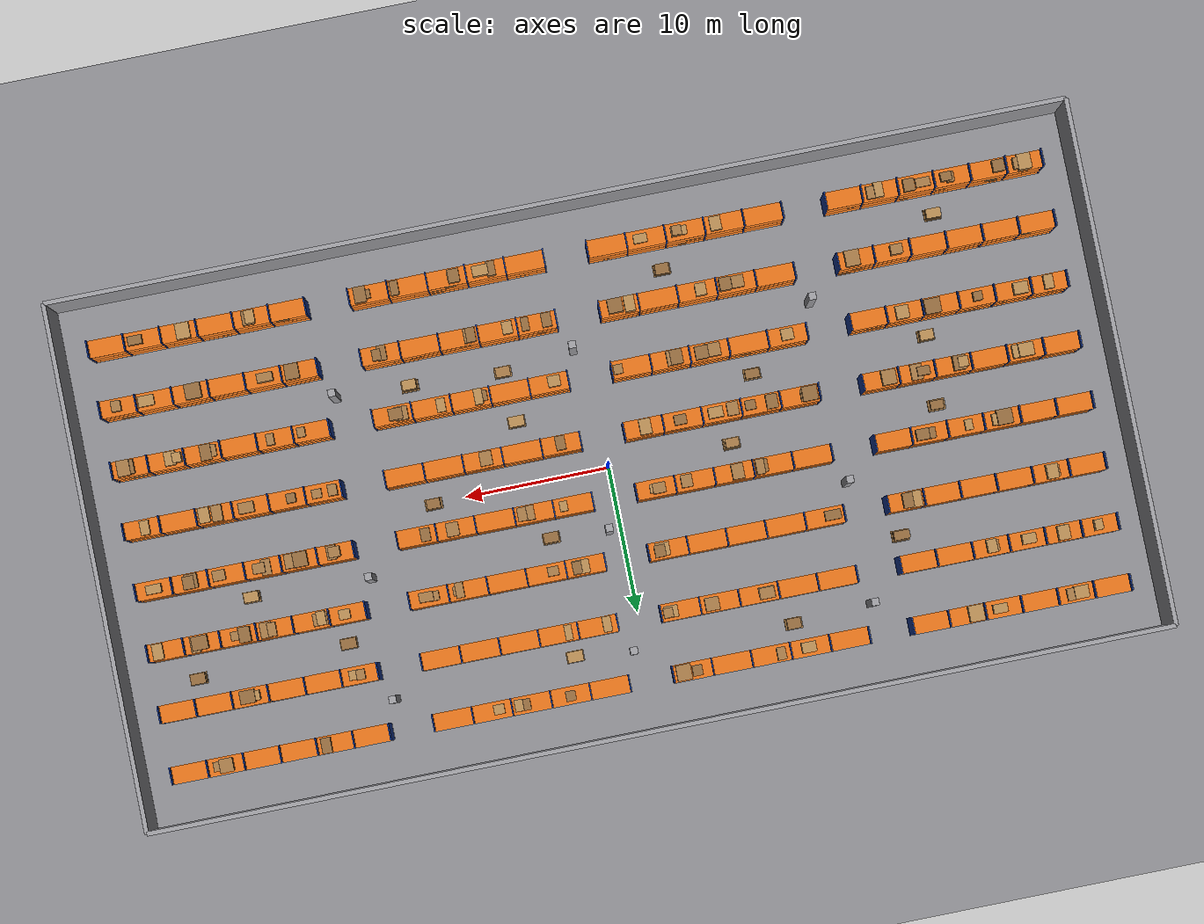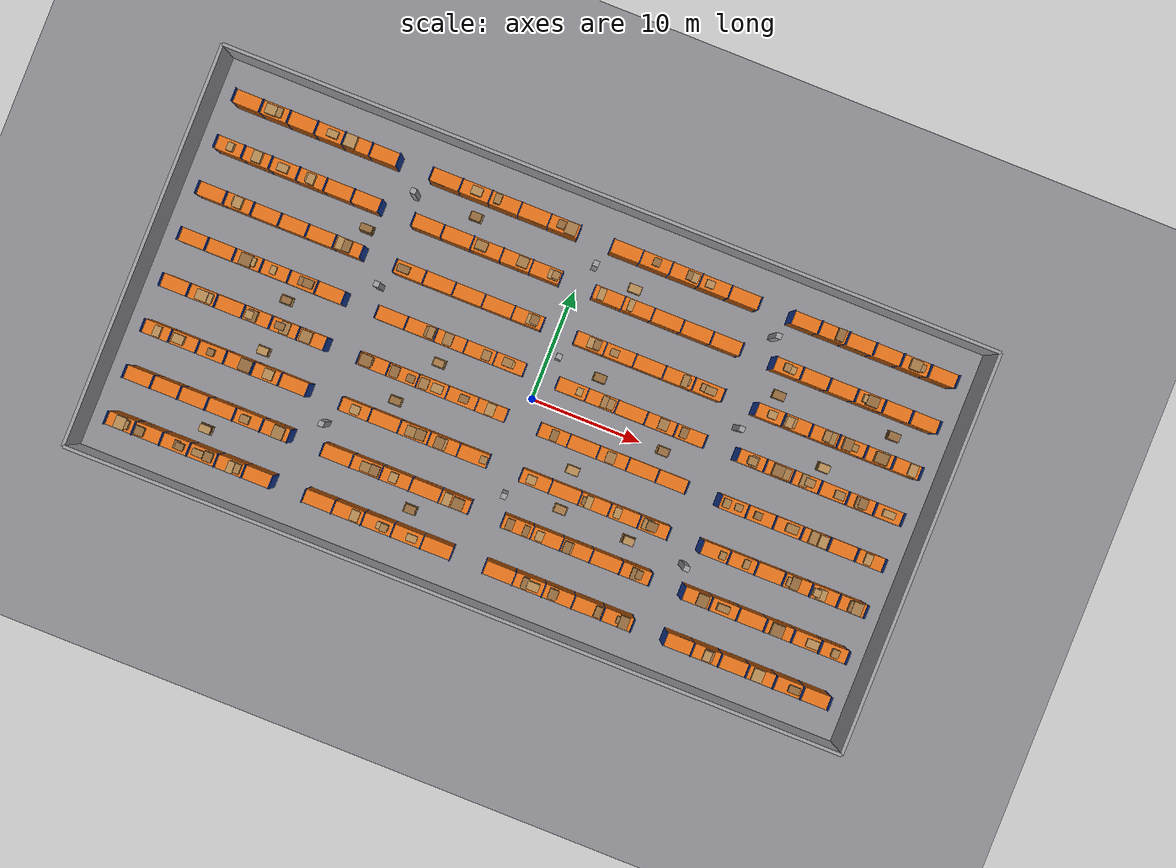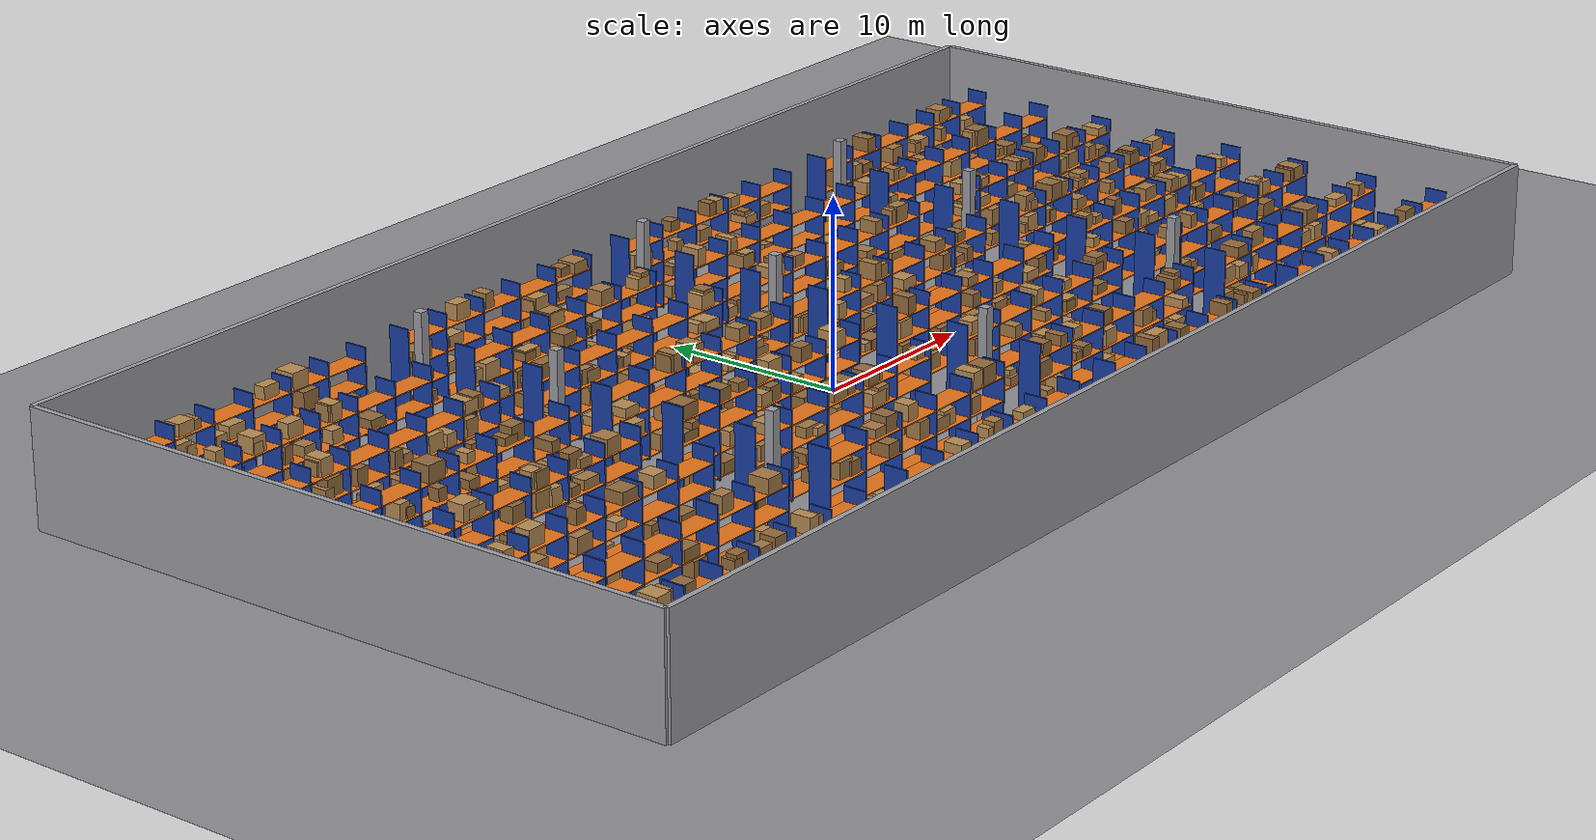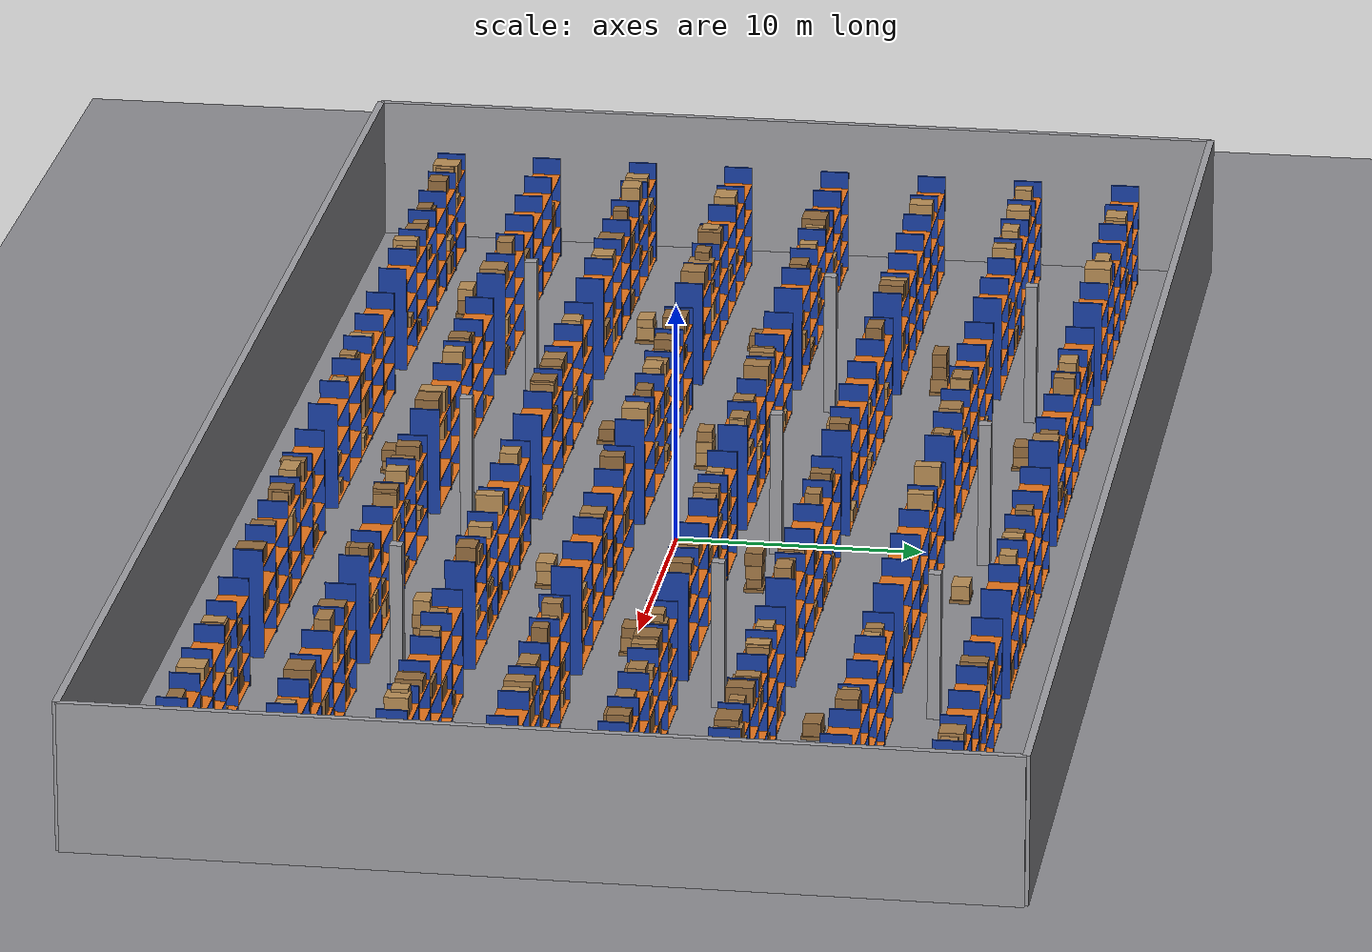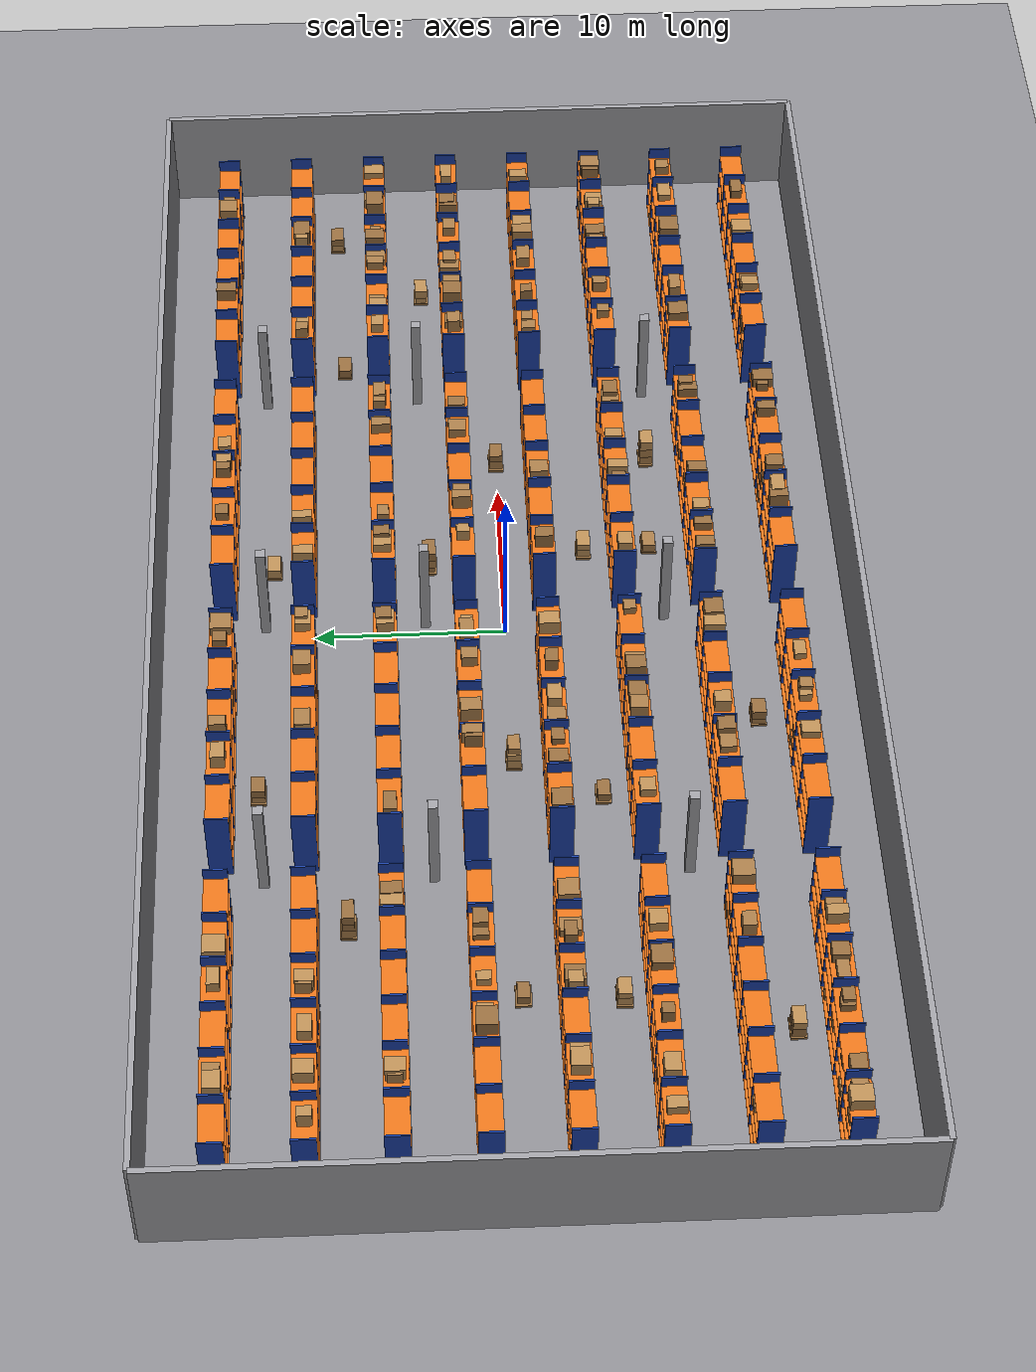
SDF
<?xml version="1.0" encoding="UTF-8"?>
<sdf version="1.9">
  <world name="warehouse">
    <physics type="ode">
      <max_step_size>0.004</max_step_size>
      <real_time_factor>1.0</real_time_factor>
      <real_time_update_rate>0</real_time_update_rate>
    </physics>
    <gravity>0 0 -9.8</gravity>
    <magnetic_field>6e-06 2.3e-05 -4.2e-05</magnetic_field>
    <atmosphere type="adiabatic"/>
    <scene>
      <grid>false</grid>
      <ambient>0.5 0.5 0.5 1</ambient>
      <background>0.7 0.7 0.7 1</background>
      <shadows>true</shadows>
    </scene>
    <model name="ground_plane">
      <static>true</static>
      <link name="link">
        <collision name="collision">
          <geometry><plane><normal>0 0 1</normal><size>1 1</size></plane></geometry>
        </collision>
        <visual name="visual">
          <geometry><plane><normal>0 0 1</normal><size>200 100</size></plane></geometry>
          <material>
            <ambient>0.55 0.55 0.57 1</ambient>
            <diffuse>0.55 0.55 0.57 1</diffuse>
            <specular>0.1 0.1 0.1 1</specular>
          </material>
        </visual>
      </link>
    </model>
    <light name="sunUTC" type="directional">
      <pose>0 0 500 0 -0 0</pose>
      <cast_shadows>true</cast_shadows>
      <intensity>1</intensity>
      <direction>0.001 0.625 -0.78</direction>
      <diffuse>0.904 0.904 0.904 1</diffuse>
      <specular>0.271 0.271 0.271 1</specular>
    </light>
    <spherical_coordinates>
      <surface_model>EARTH_WGS84</surface_model>
      <world_frame_orientation>ENU</world_frame_orientation>
      <latitude_deg>47.397971057728974</latitude_deg>
      <longitude_deg> 8.546163739800146</longitude_deg>
      <elevation>0</elevation>
    </spherical_coordinates>
    <model name="walls">
      <static>true</static>
      <link name="link">
        <collision name="n_c">
          <pose>0.000 18.150 3.000 0 0 0</pose>
          <geometry><box><size>70.300 0.300 6.000</size></box></geometry>
        </collision>
        <visual name="n_v">
          <pose>0.000 18.150 3.000 0 0 0</pose>
          <geometry><box><size>70.300 0.300 6.000</size></box></geometry>
          <material>
            <ambient>0.62 0.62 0.64 1</ambient><diffuse>0.62 0.62 0.64 1</diffuse>
            <specular>0.1 0.1 0.1 1</specular>
          </material>
        </visual>
        <collision name="s_c">
          <pose>0.000 -18.150 3.000 0 0 0</pose>
          <geometry><box><size>70.300 0.300 6.000</size></box></geometry>
        </collision>
        <visual name="s_v">
          <pose>0.000 -18.150 3.000 0 0 0</pose>
          <geometry><box><size>70.300 0.300 6.000</size></box></geometry>
          <material>
            <ambient>0.62 0.62 0.64 1</ambient><diffuse>0.62 0.62 0.64 1</diffuse>
            <specular>0.1 0.1 0.1 1</specular>
          </material>
        </visual>
        <collision name="e_c">
          <pose>35.150 0.000 3.000 0 0 0</pose>
          <geometry><box><size>0.300 36.300 6.000</size></box></geometry>
        </collision>
        <visual name="e_v">
          <pose>35.150 0.000 3.000 0 0 0</pose>
          <geometry><box><size>0.300 36.300 6.000</size></box></geometry>
          <material>
            <ambient>0.62 0.62 0.64 1</ambient><diffuse>0.62 0.62 0.64 1</diffuse>
            <specular>0.1 0.1 0.1 1</specular>
          </material>
        </visual>
        <collision name="w_c">
          <pose>-35.150 0.000 3.000 0 0 0</pose>
          <geometry><box><size>0.300 36.300 6.000</size></box></geometry>
        </collision>
        <visual name="w_v">
          <pose>-35.150 0.000 3.000 0 0 0</pose>
          <geometry><box><size>0.300 36.300 6.000</size></box></geometry>
          <material>
            <ambient>0.62 0.62 0.64 1</ambient><diffuse>0.62 0.62 0.64 1</diffuse>
            <specular>0.1 0.1 0.1 1</specular>
          </material>
        </visual>
      </link>
    </model>
    <model name="rack0">
      <static>true</static>
      <link name="link">
        <collision name="up0_c">
          <pose>-33.000 -14.700 2.250 0 0 0</pose>
          <geometry><box><size>0.080 1.200 4.500</size></box></geometry>
        </collision>
        <visual name="up0_v">
          <pose>-33.000 -14.700 2.250 0 0 0</pose>
          <geometry><box><size>0.080 1.200 4.500</size></box></geometry>
          <material>
            <ambient>0.1 0.25 0.65 1</ambient><diffuse>0.1 0.25 0.65 1</diffuse>
            <specular>0.1 0.1 0.1 1</specular>
          </material>
        </visual>
        <collision name="up1_c">
          <pose>-30.500 -14.700 2.250 0 0 0</pose>
          <geometry><box><size>0.080 1.200 4.500</size></box></geometry>
        </collision>
        <visual name="up1_v">
          <pose>-30.500 -14.700 2.250 0 0 0</pose>
          <geometry><box><size>0.080 1.200 4.500</size></box></geometry>
          <material>
            <ambient>0.1 0.25 0.65 1</ambient><diffuse>0.1 0.25 0.65 1</diffuse>
            <specular>0.1 0.1 0.1 1</specular>
          </material>
        </visual>
        <collision name="up2_c">
          <pose>-28.000 -14.700 2.250 0 0 0</pose>
          <geometry><box><size>0.080 1.200 4.500</size></box></geometry>
        </collision>
        <visual name="up2_v">
          <pose>-28.000 -14.700 2.250 0 0 0</pose>
          <geometry><box><size>0.080 1.200 4.500</size></box></geometry>
          <material>
            <ambient>0.1 0.25 0.65 1</ambient><diffuse>0.1 0.25 0.65 1</diffuse>
            <specular>0.1 0.1 0.1 1</specular>
          </material>
        </visual>
        <collision name="up3_c">
          <pose>-25.500 -14.700 2.250 0 0 0</pose>
          <geometry><box><size>0.080 1.200 4.500</size></box></geometry>
        </collision>
        <visual name="up3_v">
          <pose>-25.500 -14.700 2.250 0 0 0</pose>
          <geometry><box><size>0.080 1.200 4.500</size></box></geometry>
          <material>
            <ambient>0.1 0.25 0.65 1</ambient><diffuse>0.1 0.25 0.65 1</diffuse>
            <specular>0.1 0.1 0.1 1</specular>
          </material>
        </visual>
        <collision name="up4_c">
          <pose>-23.000 -14.700 2.250 0 0 0</pose>
          <geometry><box><size>0.080 1.200 4.500</size></box></geometry>
        </collision>
        <visual name="up4_v">
          <pose>-23.000 -14.700 2.250 0 0 0</pose>
          <geometry><box><size>0.080 1.200 4.500</size></box></geometry>
          <material>
            <ambient>0.1 0.25 0.65 1</ambient><diffuse>0.1 0.25 0.65 1</diffuse>
            <specular>0.1 0.1 0.1 1</specular>
          </material>
        </visual>
        <collision name="up5_c">
          <pose>-20.500 -14.700 2.250 0 0 0</pose>
          <geometry><box><size>0.080 1.200 4.500</size></box></geometry>
        </collision>
        <visual name="up5_v">
          <pose>-20.500 -14.700 2.250 0 0 0</pose>
          <geometry><box><size>0.080 1.200 4.500</size></box></geometry>
          <material>
            <ambient>0.1 0.25 0.65 1</ambient><diffuse>0.1 0.25 0.65 1</diffuse>
            <specular>0.1 0.1 0.1 1</specular>
          </material>
        </visual>
        <collision name="up6_c">
          <pose>-18.000 -14.700 2.250 0 0 0</pose>
          <geometry><box><size>0.080 1.200 4.500</size></box></geometry>
        </collision>
        <visual name="up6_v">
          <pose>-18.000 -14.700 2.250 0 0 0</pose>
          <geometry><box><size>0.080 1.200 4.500</size></box></geometry>
          <material>
            <ambient>0.1 0.25 0.65 1</ambient><diffuse>0.1 0.25 0.65 1</diffuse>
            <specular>0.1 0.1 0.1 1</specular>
          </material>
        </visual>
        <collision name="sh0_c">
          <pose>-25.500 -14.700 0.150 0 0 0</pose>
          <geometry><box><size>15.000 1.200 0.050</size></box></geometry>
        </collision>
        <visual name="sh0_v">
          <pose>-25.500 -14.700 0.150 0 0 0</pose>
          <geometry><box><size>15.000 1.200 0.050</size></box></geometry>
          <material>
            <ambient>0.9 0.45 0.1 1</ambient><diffuse>0.9 0.45 0.1 1</diffuse>
            <specular>0.1 0.1 0.1 1</specular>
          </material>
        </visual>
        <collision name="sh1_c">
          <pose>-25.500 -14.700 1.350 0 0 0</pose>
          <geometry><box><size>15.000 1.200 0.050</size></box></geometry>
        </collision>
        <visual name="sh1_v">
          <pose>-25.500 -14.700 1.350 0 0 0</pose>
          <geometry><box><size>15.000 1.200 0.050</size></box></geometry>
          <material>
            <ambient>0.9 0.45 0.1 1</ambient><diffuse>0.9 0.45 0.1 1</diffuse>
            <specular>0.1 0.1 0.1 1</specular>
          </material>
        </visual>
        <collision name="sh2_c">
          <pose>-25.500 -14.700 2.550 0 0 0</pose>
          <geometry><box><size>15.000 1.200 0.050</size></box></geometry>
        </collision>
        <visual name="sh2_v">
          <pose>-25.500 -14.700 2.550 0 0 0</pose>
          <geometry><box><size>15.000 1.200 0.050</size></box></geometry>
          <material>
            <ambient>0.9 0.45 0.1 1</ambient><diffuse>0.9 0.45 0.1 1</diffuse>
            <specular>0.1 0.1 0.1 1</specular>
          </material>
        </visual>
        <collision name="sh3_c">
          <pose>-25.500 -14.700 3.750 0 0 0</pose>
          <geometry><box><size>15.000 1.200 0.050</size></box></geometry>
        </collision>
        <visual name="sh3_v">
          <pose>-25.500 -14.700 3.750 0 0 0</pose>
          <geometry><box><size>15.000 1.200 0.050</size></box></geometry>
          <material>
            <ambient>0.9 0.45 0.1 1</ambient><diffuse>0.9 0.45 0.1 1</diffuse>
            <specular>0.1 0.1 0.1 1</specular>
          </material>
        </visual>
        <collision name="c0_c">
          <pose>-31.500 -14.671 1.687 0 0 0</pose>
          <geometry><box><size>0.653 0.848 0.625</size></box></geometry>
        </collision>
        <visual name="c0_v">
          <pose>-31.500 -14.671 1.687 0 0 0</pose>
          <geometry><box><size>0.653 0.848 0.625</size></box></geometry>
          <material>
            <ambient>0.65 0.48 0.28 1</ambient><diffuse>0.65 0.48 0.28 1</diffuse>
            <specular>0.1 0.1 0.1 1</specular>
          </material>
        </visual>
        <collision name="c1_c">
          <pose>-31.834 -14.678 2.776 0 0 0</pose>
          <geometry><box><size>0.760 0.981 0.401</size></box></geometry>
        </collision>
        <visual name="c1_v">
          <pose>-31.834 -14.678 2.776 0 0 0</pose>
          <geometry><box><size>0.760 0.981 0.401</size></box></geometry>
          <material>
            <ambient>0.65 0.48 0.28 1</ambient><diffuse>0.65 0.48 0.28 1</diffuse>
            <specular>0.1 0.1 0.1 1</specular>
          </material>
        </visual>
        <collision name="c2_c">
          <pose>-32.440 -14.685 2.854 0 0 0</pose>
          <geometry><box><size>0.855 0.651 0.559</size></box></geometry>
        </collision>
        <visual name="c2_v">
          <pose>-32.440 -14.685 2.854 0 0 0</pose>
          <geometry><box><size>0.855 0.651 0.559</size></box></geometry>
          <material>
            <ambient>0.65 0.48 0.28 1</ambient><diffuse>0.65 0.48 0.28 1</diffuse>
            <specular>0.1 0.1 0.1 1</specular>
          </material>
        </visual>
        <collision name="c3_c">
          <pose>-31.712 -14.674 4.156 0 0 0</pose>
          <geometry><box><size>0.912 1.085 0.763</size></box></geometry>
        </collision>
        <visual name="c3_v">
          <pose>-31.712 -14.674 4.156 0 0 0</pose>
          <geometry><box><size>0.912 1.085 0.763</size></box></geometry>
          <material>
            <ambient>0.72 0.55 0.33 1</ambient><diffuse>0.72 0.55 0.33 1</diffuse>
            <specular>0.1 0.1 0.1 1</specular>
          </material>
        </visual>
        <collision name="c4_c">
          <pose>-31.367 -14.655 4.144 0 0 0</pose>
          <geometry><box><size>0.832 0.773 0.738</size></box></geometry>
        </collision>
        <visual name="c4_v">
          <pose>-31.367 -14.655 4.144 0 0 0</pose>
          <geometry><box><size>0.832 0.773 0.738</size></box></geometry>
          <material>
            <ambient>0.65 0.48 0.28 1</ambient><diffuse>0.65 0.48 0.28 1</diffuse>
            <specular>0.1 0.1 0.1 1</specular>
          </material>
        </visual>
        <collision name="c5_c">
          <pose>-29.890 -14.717 0.590 0 0 0</pose>
          <geometry><box><size>0.612 1.096 0.830</size></box></geometry>
        </collision>
        <visual name="c5_v">
          <pose>-29.890 -14.717 0.590 0 0 0</pose>
          <geometry><box><size>0.612 1.096 0.830</size></box></geometry>
          <material>
            <ambient>0.58 0.42 0.24 1</ambient><diffuse>0.58 0.42 0.24 1</diffuse>
            <specular>0.1 0.1 0.1 1</specular>
          </material>
        </visual>
        <collision name="c6_c">
          <pose>-29.573 -14.653 1.622 0 0 0</pose>
          <geometry><box><size>0.805 1.055 0.495</size></box></geometry>
        </collision>
        <visual name="c6_v">
          <pose>-29.573 -14.653 1.622 0 0 0</pose>
          <geometry><box><size>0.805 1.055 0.495</size></box></geometry>
          <material>
            <ambient>0.72 0.55 0.33 1</ambient><diffuse>0.72 0.55 0.33 1</diffuse>
            <specular>0.1 0.1 0.1 1</specular>
          </material>
        </visual>
        <collision name="c7_c">
          <pose>-29.852 -14.726 1.722 0 0 0</pose>
          <geometry><box><size>1.008 0.853 0.695</size></box></geometry>
        </collision>
        <visual name="c7_v">
          <pose>-29.852 -14.726 1.722 0 0 0</pose>
          <geometry><box><size>1.008 0.853 0.695</size></box></geometry>
          <material>
            <ambient>0.72 0.55 0.33 1</ambient><diffuse>0.72 0.55 0.33 1</diffuse>
            <specular>0.1 0.1 0.1 1</specular>
          </material>
        </visual>
        <collision name="c8_c">
          <pose>-28.874 -14.741 2.969 0 0 0</pose>
          <geometry><box><size>0.720 1.041 0.788</size></box></geometry>
        </collision>
        <visual name="c8_v">
          <pose>-28.874 -14.741 2.969 0 0 0</pose>
          <geometry><box><size>0.720 1.041 0.788</size></box></geometry>
          <material>
            <ambient>0.58 0.42 0.24 1</ambient><diffuse>0.58 0.42 0.24 1</diffuse>
            <specular>0.1 0.1 0.1 1</specular>
          </material>
        </visual>
        <collision name="c9_c">
          <pose>-29.950 -14.746 4.097 0 0 0</pose>
          <geometry><box><size>0.813 0.797 0.645</size></box></geometry>
        </collision>
        <visual name="c9_v">
          <pose>-29.950 -14.746 4.097 0 0 0</pose>
          <geometry><box><size>0.813 0.797 0.645</size></box></geometry>
          <material>
            <ambient>0.58 0.42 0.24 1</ambient><diffuse>0.58 0.42 0.24 1</diffuse>
            <specular>0.1 0.1 0.1 1</specular>
          </material>
        </visual>
        <collision name="c10_c">
          <pose>-27.438 -14.730 0.432 0 0 0</pose>
          <geometry><box><size>0.888 0.684 0.513</size></box></geometry>
        </collision>
        <visual name="c10_v">
          <pose>-27.438 -14.730 0.432 0 0 0</pose>
          <geometry><box><size>0.888 0.684 0.513</size></box></geometry>
          <material>
            <ambient>0.58 0.42 0.24 1</ambient><diffuse>0.58 0.42 0.24 1</diffuse>
            <specular>0.1 0.1 0.1 1</specular>
          </material>
        </visual>
        <collision name="c11_c">
          <pose>-26.621 -14.704 0.613 0 0 0</pose>
          <geometry><box><size>0.639 0.857 0.876</size></box></geometry>
        </collision>
        <visual name="c11_v">
          <pose>-26.621 -14.704 0.613 0 0 0</pose>
          <geometry><box><size>0.639 0.857 0.876</size></box></geometry>
          <material>
            <ambient>0.72 0.55 0.33 1</ambient><diffuse>0.72 0.55 0.33 1</diffuse>
            <specular>0.1 0.1 0.1 1</specular>
          </material>
        </visual>
        <collision name="c12_c">
          <pose>-26.062 -14.699 1.814 0 0 0</pose>
          <geometry><box><size>0.730 1.028 0.877</size></box></geometry>
        </collision>
        <visual name="c12_v">
          <pose>-26.062 -14.699 1.814 0 0 0</pose>
          <geometry><box><size>0.730 1.028 0.877</size></box></geometry>
          <material>
            <ambient>0.65 0.48 0.28 1</ambient><diffuse>0.65 0.48 0.28 1</diffuse>
            <specular>0.1 0.1 0.1 1</specular>
          </material>
        </visual>
        <collision name="c13_c">
          <pose>-26.642 -14.730 2.993 0 0 0</pose>
          <geometry><box><size>0.756 0.628 0.835</size></box></geometry>
        </collision>
        <visual name="c13_v">
          <pose>-26.642 -14.730 2.993 0 0 0</pose>
          <geometry><box><size>0.756 0.628 0.835</size></box></geometry>
          <material>
            <ambient>0.58 0.42 0.24 1</ambient><diffuse>0.58 0.42 0.24 1</diffuse>
            <specular>0.1 0.1 0.1 1</specular>
          </material>
        </visual>
        <collision name="c14_c">
          <pose>-26.306 -14.717 4.110 0 0 0</pose>
          <geometry><box><size>0.749 0.601 0.670</size></box></geometry>
        </collision>
        <visual name="c14_v">
          <pose>-26.306 -14.717 4.110 0 0 0</pose>
          <geometry><box><size>0.749 0.601 0.670</size></box></geometry>
          <material>
            <ambient>0.58 0.42 0.24 1</ambient><diffuse>0.58 0.42 0.24 1</diffuse>
            <specular>0.1 0.1 0.1 1</specular>
          </material>
        </visual>
        <collision name="c15_c">
          <pose>-26.599 -14.664 4.019 0 0 0</pose>
          <geometry><box><size>0.517 0.715 0.489</size></box></geometry>
        </collision>
        <visual name="c15_v">
          <pose>-26.599 -14.664 4.019 0 0 0</pose>
          <geometry><box><size>0.517 0.715 0.489</size></box></geometry>
          <material>
            <ambient>0.58 0.42 0.24 1</ambient><diffuse>0.58 0.42 0.24 1</diffuse>
            <specular>0.1 0.1 0.1 1</specular>
          </material>
        </visual>
        <collision name="c16_c">
          <pose>-23.595 -14.705 0.393 0 0 0</pose>
          <geometry><box><size>0.519 1.072 0.435</size></box></geometry>
        </collision>
        <visual name="c16_v">
          <pose>-23.595 -14.705 0.393 0 0 0</pose>
          <geometry><box><size>0.519 1.072 0.435</size></box></geometry>
          <material>
            <ambient>0.72 0.55 0.33 1</ambient><diffuse>0.72 0.55 0.33 1</diffuse>
            <specular>0.1 0.1 0.1 1</specular>
          </material>
        </visual>
        <collision name="c17_c">
          <pose>-24.507 -14.743 0.531 0 0 0</pose>
          <geometry><box><size>0.650 0.655 0.712</size></box></geometry>
        </collision>
        <visual name="c17_v">
          <pose>-24.507 -14.743 0.531 0 0 0</pose>
          <geometry><box><size>0.650 0.655 0.712</size></box></geometry>
          <material>
            <ambient>0.65 0.48 0.28 1</ambient><diffuse>0.65 0.48 0.28 1</diffuse>
            <specular>0.1 0.1 0.1 1</specular>
          </material>
        </visual>
        <collision name="c18_c">
          <pose>-24.255 -14.739 2.951 0 0 0</pose>
          <geometry><box><size>0.889 0.747 0.751</size></box></geometry>
        </collision>
        <visual name="c18_v">
          <pose>-24.255 -14.739 2.951 0 0 0</pose>
          <geometry><box><size>0.889 0.747 0.751</size></box></geometry>
          <material>
            <ambient>0.72 0.55 0.33 1</ambient><diffuse>0.72 0.55 0.33 1</diffuse>
            <specular>0.1 0.1 0.1 1</specular>
          </material>
        </visual>
        <collision name="c19_c">
          <pose>-24.863 -14.660 2.822 0 0 0</pose>
          <geometry><box><size>0.732 0.810 0.494</size></box></geometry>
        </collision>
        <visual name="c19_v">
          <pose>-24.863 -14.660 2.822 0 0 0</pose>
          <geometry><box><size>0.732 0.810 0.494</size></box></geometry>
          <material>
            <ambient>0.58 0.42 0.24 1</ambient><diffuse>0.58 0.42 0.24 1</diffuse>
            <specular>0.1 0.1 0.1 1</specular>
          </material>
        </visual>
        <collision name="c20_c">
          <pose>-24.713 -14.678 3.979 0 0 0</pose>
          <geometry><box><size>0.990 0.610 0.409</size></box></geometry>
        </collision>
        <visual name="c20_v">
          <pose>-24.713 -14.678 3.979 0 0 0</pose>
          <geometry><box><size>0.990 0.610 0.409</size></box></geometry>
          <material>
            <ambient>0.65 0.48 0.28 1</ambient><diffuse>0.65 0.48 0.28 1</diffuse>
            <specular>0.1 0.1 0.1 1</specular>
          </material>
        </visual>
        <collision name="c21_c">
          <pose>-23.741 -14.652 4.082 0 0 0</pose>
          <geometry><box><size>0.767 0.853 0.613</size></box></geometry>
        </collision>
        <visual name="c21_v">
          <pose>-23.741 -14.652 4.082 0 0 0</pose>
          <geometry><box><size>0.767 0.853 0.613</size></box></geometry>
          <material>
            <ambient>0.58 0.42 0.24 1</ambient><diffuse>0.58 0.42 0.24 1</diffuse>
            <specular>0.1 0.1 0.1 1</specular>
          </material>
        </visual>
        <collision name="c22_c">
          <pose>-21.624 -14.718 0.474 0 0 0</pose>
          <geometry><box><size>0.634 0.924 0.597</size></box></geometry>
        </collision>
        <visual name="c22_v">
          <pose>-21.624 -14.718 0.474 0 0 0</pose>
          <geometry><box><size>0.634 0.924 0.597</size></box></geometry>
          <material>
            <ambient>0.58 0.42 0.24 1</ambient><diffuse>0.58 0.42 0.24 1</diffuse>
            <specular>0.1 0.1 0.1 1</specular>
          </material>
        </visual>
        <collision name="c23_c">
          <pose>-22.195 -14.745 0.406 0 0 0</pose>
          <geometry><box><size>0.756 0.969 0.463</size></box></geometry>
        </collision>
        <visual name="c23_v">
          <pose>-22.195 -14.745 0.406 0 0 0</pose>
          <geometry><box><size>0.756 0.969 0.463</size></box></geometry>
          <material>
            <ambient>0.65 0.48 0.28 1</ambient><diffuse>0.65 0.48 0.28 1</diffuse>
            <specular>0.1 0.1 0.1 1</specular>
          </material>
        </visual>
        <collision name="c24_c">
          <pose>-21.669 -14.737 1.615 0 0 0</pose>
          <geometry><box><size>1.050 0.749 0.479</size></box></geometry>
        </collision>
        <visual name="c24_v">
          <pose>-21.669 -14.737 1.615 0 0 0</pose>
          <geometry><box><size>1.050 0.749 0.479</size></box></geometry>
          <material>
            <ambient>0.58 0.42 0.24 1</ambient><diffuse>0.58 0.42 0.24 1</diffuse>
            <specular>0.1 0.1 0.1 1</specular>
          </material>
        </visual>
        <collision name="c25_c">
          <pose>-21.162 -14.693 1.780 0 0 0</pose>
          <geometry><box><size>1.027 0.619 0.810</size></box></geometry>
        </collision>
        <visual name="c25_v">
          <pose>-21.162 -14.693 1.780 0 0 0</pose>
          <geometry><box><size>1.027 0.619 0.810</size></box></geometry>
          <material>
            <ambient>0.65 0.48 0.28 1</ambient><diffuse>0.65 0.48 0.28 1</diffuse>
            <specular>0.1 0.1 0.1 1</specular>
          </material>
        </visual>
        <collision name="c26_c">
          <pose>-21.476 -14.707 2.826 0 0 0</pose>
          <geometry><box><size>0.727 0.773 0.503</size></box></geometry>
        </collision>
        <visual name="c26_v">
          <pose>-21.476 -14.707 2.826 0 0 0</pose>
          <geometry><box><size>0.727 0.773 0.503</size></box></geometry>
          <material>
            <ambient>0.65 0.48 0.28 1</ambient><diffuse>0.65 0.48 0.28 1</diffuse>
            <specular>0.1 0.1 0.1 1</specular>
          </material>
        </visual>
        <collision name="c27_c">
          <pose>-21.147 -14.660 4.056 0 0 0</pose>
          <geometry><box><size>0.678 0.850 0.563</size></box></geometry>
        </collision>
        <visual name="c27_v">
          <pose>-21.147 -14.660 4.056 0 0 0</pose>
          <geometry><box><size>0.678 0.850 0.563</size></box></geometry>
          <material>
            <ambient>0.65 0.48 0.28 1</ambient><diffuse>0.65 0.48 0.28 1</diffuse>
            <specular>0.1 0.1 0.1 1</specular>
          </material>
        </visual>
        <collision name="c28_c">
          <pose>-21.642 -14.736 4.178 0 0 0</pose>
          <geometry><box><size>0.594 1.029 0.806</size></box></geometry>
        </collision>
        <visual name="c28_v">
          <pose>-21.642 -14.736 4.178 0 0 0</pose>
          <geometry><box><size>0.594 1.029 0.806</size></box></geometry>
          <material>
            <ambient>0.72 0.55 0.33 1</ambient><diffuse>0.72 0.55 0.33 1</diffuse>
            <specular>0.1 0.1 0.1 1</specular>
          </material>
        </visual>
        <collision name="c29_c">
          <pose>-19.018 -14.702 1.796 0 0 0</pose>
          <geometry><box><size>1.059 0.772 0.841</size></box></geometry>
        </collision>
        <visual name="c29_v">
          <pose>-19.018 -14.702 1.796 0 0 0</pose>
          <geometry><box><size>1.059 0.772 0.841</size></box></geometry>
          <material>
            <ambient>0.58 0.42 0.24 1</ambient><diffuse>0.58 0.42 0.24 1</diffuse>
            <specular>0.1 0.1 0.1 1</specular>
          </material>
        </visual>
        <collision name="c30_c">
          <pose>-19.798 -14.659 1.596 0 0 0</pose>
          <geometry><box><size>0.641 0.963 0.442</size></box></geometry>
        </collision>
        <visual name="c30_v">
          <pose>-19.798 -14.659 1.596 0 0 0</pose>
          <geometry><box><size>0.641 0.963 0.442</size></box></geometry>
          <material>
            <ambient>0.65 0.48 0.28 1</ambient><diffuse>0.65 0.48 0.28 1</diffuse>
            <specular>0.1 0.1 0.1 1</specular>
          </material>
        </visual>
      </link>
    </model>
    <model name="rack1">
      <static>true</static>
      <link name="link">
        <collision name="up0_c">
          <pose>-15.000 -14.700 2.250 0 0 0</pose>
          <geometry><box><size>0.080 1.200 4.500</size></box></geometry>
        </collision>
        <visual name="up0_v">
          <pose>-15.000 -14.700 2.250 0 0 0</pose>
          <geometry><box><size>0.080 1.200 4.500</size></box></geometry>
          <material>
            <ambient>0.1 0.25 0.65 1</ambient><diffuse>0.1 0.25 0.65 1</diffuse>
            <specular>0.1 0.1 0.1 1</specular>
          </material>
        </visual>
        <collision name="up1_c">
          <pose>-12.300 -14.700 2.250 0 0 0</pose>
          <geometry><box><size>0.080 1.200 4.500</size></box></geometry>
        </collision>
        <visual name="up1_v">
          <pose>-12.300 -14.700 2.250 0 0 0</pose>
          <geometry><box><size>0.080 1.200 4.500</size></box></geometry>
          <material>
            <ambient>0.1 0.25 0.65 1</ambient><diffuse>0.1 0.25 0.65 1</diffuse>
            <specular>0.1 0.1 0.1 1</specular>
          </material>
        </visual>
        <collision name="up2_c">
          <pose>-9.600 -14.700 2.250 0 0 0</pose>
          <geometry><box><size>0.080 1.200 4.500</size></box></geometry>
        </collision>
        <visual name="up2_v">
          <pose>-9.600 -14.700 2.250 0 0 0</pose>
          <geometry><box><size>0.080 1.200 4.500</size></box></geometry>
          <material>
            <ambient>0.1 0.25 0.65 1</ambient><diffuse>0.1 0.25 0.65 1</diffuse>
            <specular>0.1 0.1 0.1 1</specular>
          </material>
        </visual>
        <collision name="up3_c">
          <pose>-6.900 -14.700 2.250 0 0 0</pose>
          <geometry><box><size>0.080 1.200 4.500</size></box></geometry>
        </collision>
        <visual name="up3_v">
          <pose>-6.900 -14.700 2.250 0 0 0</pose>
          <geometry><box><size>0.080 1.200 4.500</size></box></geometry>
          <material>
            <ambient>0.1 0.25 0.65 1</ambient><diffuse>0.1 0.25 0.65 1</diffuse>
            <specular>0.1 0.1 0.1 1</specular>
          </material>
        </visual>
        <collision name="up4_c">
          <pose>-4.200 -14.700 2.250 0 0 0</pose>
          <geometry><box><size>0.080 1.200 4.500</size></box></geometry>
        </collision>
        <visual name="up4_v">
          <pose>-4.200 -14.700 2.250 0 0 0</pose>
          <geometry><box><size>0.080 1.200 4.500</size></box></geometry>
          <material>
            <ambient>0.1 0.25 0.65 1</ambient><diffuse>0.1 0.25 0.65 1</diffuse>
            <specular>0.1 0.1 0.1 1</specular>
          </material>
        </visual>
        <collision name="up5_c">
          <pose>-1.500 -14.700 2.250 0 0 0</pose>
          <geometry><box><size>0.080 1.200 4.500</size></box></geometry>
        </collision>
        <visual name="up5_v">
          <pose>-1.500 -14.700 2.250 0 0 0</pose>
          <geometry><box><size>0.080 1.200 4.500</size></box></geometry>
          <material>
            <ambient>0.1 0.25 0.65 1</ambient><diffuse>0.1 0.25 0.65 1</diffuse>
            <specular>0.1 0.1 0.1 1</specular>
          </material>
        </visual>
        <collision name="sh0_c">
          <pose>-8.250 -14.700 0.150 0 0 0</pose>
          <geometry><box><size>13.500 1.200 0.050</size></box></geometry>
        </collision>
        <visual name="sh0_v">
          <pose>-8.250 -14.700 0.150 0 0 0</pose>
          <geometry><box><size>13.500 1.200 0.050</size></box></geometry>
          <material>
            <ambient>0.9 0.45 0.1 1</ambient><diffuse>0.9 0.45 0.1 1</diffuse>
            <specular>0.1 0.1 0.1 1</specular>
          </material>
        </visual>
        <collision name="sh1_c">
          <pose>-8.250 -14.700 1.350 0 0 0</pose>
          <geometry><box><size>13.500 1.200 0.050</size></box></geometry>
        </collision>
        <visual name="sh1_v">
          <pose>-8.250 -14.700 1.350 0 0 0</pose>
          <geometry><box><size>13.500 1.200 0.050</size></box></geometry>
          <material>
            <ambient>0.9 0.45 0.1 1</ambient><diffuse>0.9 0.45 0.1 1</diffuse>
            <specular>0.1 0.1 0.1 1</specular>
          </material>
        </visual>
        <collision name="sh2_c">
          <pose>-8.250 -14.700 2.550 0 0 0</pose>
          <geometry><box><size>13.500 1.200 0.050</size></box></geometry>
        </collision>
        <visual name="sh2_v">
          <pose>-8.250 -14.700 2.550 0 0 0</pose>
          <geometry><box><size>13.500 1.200 0.050</size></box></geometry>
          <material>
            <ambient>0.9 0.45 0.1 1</ambient><diffuse>0.9 0.45 0.1 1</diffuse>
            <specular>0.1 0.1 0.1 1</specular>
          </material>
        </visual>
        <collision name="sh3_c">
          <pose>-8.250 -14.700 3.750 0 0 0</pose>
          <geometry><box><size>13.500 1.200 0.050</size></box></geometry>
        </collision>
        <visual name="sh3_v">
          <pose>-8.250 -14.700 3.750 0 0 0</pose>
          <geometry><box><size>13.500 1.200 0.050</size></box></geometry>
          <material>
            <ambient>0.9 0.45 0.1 1</ambient><diffuse>0.9 0.45 0.1 1</diffuse>
            <specular>0.1 0.1 0.1 1</specular>
          </material>
        </visual>
        <collision name="c0_c">
          <pose>-12.996 -14.690 0.448 0 0 0</pose>
          <geometry><box><size>0.721 0.770 0.546</size></box></geometry>
        </collision>
        <visual name="c0_v">
          <pose>-12.996 -14.690 0.448 0 0 0</pose>
          <geometry><box><size>0.721 0.770 0.546</size></box></geometry>
          <material>
            <ambient>0.58 0.42 0.24 1</ambient><diffuse>0.58 0.42 0.24 1</diffuse>
            <specular>0.1 0.1 0.1 1</specular>
          </material>
        </visual>
        <collision name="c1_c">
          <pose>-14.231 -14.746 0.513 0 0 0</pose>
          <geometry><box><size>1.032 0.668 0.676</size></box></geometry>
        </collision>
        <visual name="c1_v">
          <pose>-14.231 -14.746 0.513 0 0 0</pose>
          <geometry><box><size>1.032 0.668 0.676</size></box></geometry>
          <material>
            <ambient>0.65 0.48 0.28 1</ambient><diffuse>0.65 0.48 0.28 1</diffuse>
            <specular>0.1 0.1 0.1 1</specular>
          </material>
        </visual>
        <collision name="c2_c">
          <pose>-13.226 -14.712 1.729 0 0 0</pose>
          <geometry><box><size>0.997 0.770 0.708</size></box></geometry>
        </collision>
        <visual name="c2_v">
          <pose>-13.226 -14.712 1.729 0 0 0</pose>
          <geometry><box><size>0.997 0.770 0.708</size></box></geometry>
          <material>
            <ambient>0.58 0.42 0.24 1</ambient><diffuse>0.58 0.42 0.24 1</diffuse>
            <specular>0.1 0.1 0.1 1</specular>
          </material>
        </visual>
        <collision name="c3_c">
          <pose>-13.601 -14.739 2.849 0 0 0</pose>
          <geometry><box><size>1.071 0.782 0.548</size></box></geometry>
        </collision>
        <visual name="c3_v">
          <pose>-13.601 -14.739 2.849 0 0 0</pose>
          <geometry><box><size>1.071 0.782 0.548</size></box></geometry>
          <material>
            <ambient>0.72 0.55 0.33 1</ambient><diffuse>0.72 0.55 0.33 1</diffuse>
            <specular>0.1 0.1 0.1 1</specular>
          </material>
        </visual>
        <collision name="c4_c">
          <pose>-11.845 -14.726 2.996 0 0 0</pose>
          <geometry><box><size>0.555 0.658 0.843</size></box></geometry>
        </collision>
        <visual name="c4_v">
          <pose>-11.845 -14.726 2.996 0 0 0</pose>
          <geometry><box><size>0.555 0.658 0.843</size></box></geometry>
          <material>
            <ambient>0.58 0.42 0.24 1</ambient><diffuse>0.58 0.42 0.24 1</diffuse>
            <specular>0.1 0.1 0.1 1</specular>
          </material>
        </visual>
        <collision name="c5_c">
          <pose>-10.353 -14.706 4.015 0 0 0</pose>
          <geometry><box><size>0.771 0.940 0.479</size></box></geometry>
        </collision>
        <visual name="c5_v">
          <pose>-10.353 -14.706 4.015 0 0 0</pose>
          <geometry><box><size>0.771 0.940 0.479</size></box></geometry>
          <material>
            <ambient>0.72 0.55 0.33 1</ambient><diffuse>0.72 0.55 0.33 1</diffuse>
            <specular>0.1 0.1 0.1 1</specular>
          </material>
        </visual>
        <collision name="c6_c">
          <pose>-8.738 -14.718 0.454 0 0 0</pose>
          <geometry><box><size>0.830 0.956 0.557</size></box></geometry>
        </collision>
        <visual name="c6_v">
          <pose>-8.738 -14.718 0.454 0 0 0</pose>
          <geometry><box><size>0.830 0.956 0.557</size></box></geometry>
          <material>
            <ambient>0.65 0.48 0.28 1</ambient><diffuse>0.65 0.48 0.28 1</diffuse>
            <specular>0.1 0.1 0.1 1</specular>
          </material>
        </visual>
        <collision name="c7_c">
          <pose>-8.057 -14.705 0.449 0 0 0</pose>
          <geometry><box><size>0.506 1.091 0.548</size></box></geometry>
        </collision>
        <visual name="c7_v">
          <pose>-8.057 -14.705 0.449 0 0 0</pose>
          <geometry><box><size>0.506 1.091 0.548</size></box></geometry>
          <material>
            <ambient>0.72 0.55 0.33 1</ambient><diffuse>0.72 0.55 0.33 1</diffuse>
            <specular>0.1 0.1 0.1 1</specular>
          </material>
        </visual>
        <collision name="c8_c">
          <pose>-8.814 -14.728 1.817 0 0 0</pose>
          <geometry><box><size>1.048 1.085 0.885</size></box></geometry>
        </collision>
        <visual name="c8_v">
          <pose>-8.814 -14.728 1.817 0 0 0</pose>
          <geometry><box><size>1.048 1.085 0.885</size></box></geometry>
          <material>
            <ambient>0.58 0.42 0.24 1</ambient><diffuse>0.58 0.42 0.24 1</diffuse>
            <specular>0.1 0.1 0.1 1</specular>
          </material>
        </visual>
        <collision name="c9_c">
          <pose>-8.559 -14.725 2.910 0 0 0</pose>
          <geometry><box><size>0.897 0.730 0.671</size></box></geometry>
        </collision>
        <visual name="c9_v">
          <pose>-8.559 -14.725 2.910 0 0 0</pose>
          <geometry><box><size>0.897 0.730 0.671</size></box></geometry>
          <material>
            <ambient>0.65 0.48 0.28 1</ambient><diffuse>0.65 0.48 0.28 1</diffuse>
            <specular>0.1 0.1 0.1 1</specular>
          </material>
        </visual>
        <collision name="c10_c">
          <pose>-8.868 -14.693 2.963 0 0 0</pose>
          <geometry><box><size>0.992 0.645 0.777</size></box></geometry>
        </collision>
        <visual name="c10_v">
          <pose>-8.868 -14.693 2.963 0 0 0</pose>
          <geometry><box><size>0.992 0.645 0.777</size></box></geometry>
          <material>
            <ambient>0.72 0.55 0.33 1</ambient><diffuse>0.72 0.55 0.33 1</diffuse>
            <specular>0.1 0.1 0.1 1</specular>
          </material>
        </visual>
        <collision name="c11_c">
          <pose>-7.834 -14.692 4.022 0 0 0</pose>
          <geometry><box><size>1.080 0.621 0.493</size></box></geometry>
        </collision>
        <visual name="c11_v">
          <pose>-7.834 -14.692 4.022 0 0 0</pose>
          <geometry><box><size>1.080 0.621 0.493</size></box></geometry>
          <material>
            <ambient>0.72 0.55 0.33 1</ambient><diffuse>0.72 0.55 0.33 1</diffuse>
            <specular>0.1 0.1 0.1 1</specular>
          </material>
        </visual>
        <collision name="c12_c">
          <pose>-7.680 -14.741 4.128 0 0 0</pose>
          <geometry><box><size>0.648 0.650 0.706</size></box></geometry>
        </collision>
        <visual name="c12_v">
          <pose>-7.680 -14.741 4.128 0 0 0</pose>
          <geometry><box><size>0.648 0.650 0.706</size></box></geometry>
          <material>
            <ambient>0.65 0.48 0.28 1</ambient><diffuse>0.65 0.48 0.28 1</diffuse>
            <specular>0.1 0.1 0.1 1</specular>
          </material>
        </visual>
        <collision name="c13_c">
          <pose>-5.158 -14.714 3.977 0 0 0</pose>
          <geometry><box><size>0.938 0.611 0.405</size></box></geometry>
        </collision>
        <visual name="c13_v">
          <pose>-5.158 -14.714 3.977 0 0 0</pose>
          <geometry><box><size>0.938 0.611 0.405</size></box></geometry>
          <material>
            <ambient>0.72 0.55 0.33 1</ambient><diffuse>0.72 0.55 0.33 1</diffuse>
            <specular>0.1 0.1 0.1 1</specular>
          </material>
        </visual>
        <collision name="c14_c">
          <pose>-2.832 -14.683 0.457 0 0 0</pose>
          <geometry><box><size>0.561 0.989 0.564</size></box></geometry>
        </collision>
        <visual name="c14_v">
          <pose>-2.832 -14.683 0.457 0 0 0</pose>
          <geometry><box><size>0.561 0.989 0.564</size></box></geometry>
          <material>
            <ambient>0.65 0.48 0.28 1</ambient><diffuse>0.65 0.48 0.28 1</diffuse>
            <specular>0.1 0.1 0.1 1</specular>
          </material>
        </visual>
        <collision name="c15_c">
          <pose>-2.828 -14.658 1.602 0 0 0</pose>
          <geometry><box><size>0.993 0.760 0.453</size></box></geometry>
        </collision>
        <visual name="c15_v">
          <pose>-2.828 -14.658 1.602 0 0 0</pose>
          <geometry><box><size>0.993 0.760 0.453</size></box></geometry>
          <material>
            <ambient>0.72 0.55 0.33 1</ambient><diffuse>0.72 0.55 0.33 1</diffuse>
            <specular>0.1 0.1 0.1 1</specular>
          </material>
        </visual>
      </link>
    </model>
    <model name="rack2">
      <static>true</static>
      <link name="link">
        <collision name="up0_c">
          <pose>1.500 -14.700 2.250 0 0 0</pose>
          <geometry><box><size>0.080 1.200 4.500</size></box></geometry>
        </collision>
        <visual name="up0_v">
          <pose>1.500 -14.700 2.250 0 0 0</pose>
          <geometry><box><size>0.080 1.200 4.500</size></box></geometry>
          <material>
            <ambient>0.1 0.25 0.65 1</ambient><diffuse>0.1 0.25 0.65 1</diffuse>
            <specular>0.1 0.1 0.1 1</specular>
          </material>
        </visual>
        <collision name="up1_c">
          <pose>4.200 -14.700 2.250 0 0 0</pose>
          <geometry><box><size>0.080 1.200 4.500</size></box></geometry>
        </collision>
        <visual name="up1_v">
          <pose>4.200 -14.700 2.250 0 0 0</pose>
          <geometry><box><size>0.080 1.200 4.500</size></box></geometry>
          <material>
            <ambient>0.1 0.25 0.65 1</ambient><diffuse>0.1 0.25 0.65 1</diffuse>
            <specular>0.1 0.1 0.1 1</specular>
          </material>
        </visual>
        <collision name="up2_c">
          <pose>6.900 -14.700 2.250 0 0 0</pose>
          <geometry><box><size>0.080 1.200 4.500</size></box></geometry>
        </collision>
        <visual name="up2_v">
          <pose>6.900 -14.700 2.250 0 0 0</pose>
          <geometry><box><size>0.080 1.200 4.500</size></box></geometry>
          <material>
            <ambient>0.1 0.25 0.65 1</ambient><diffuse>0.1 0.25 0.65 1</diffuse>
            <specular>0.1 0.1 0.1 1</specular>
          </material>
        </visual>
        <collision name="up3_c">
          <pose>9.600 -14.700 2.250 0 0 0</pose>
          <geometry><box><size>0.080 1.200 4.500</size></box></geometry>
        </collision>
        <visual name="up3_v">
          <pose>9.600 -14.700 2.250 0 0 0</pose>
          <geometry><box><size>0.080 1.200 4.500</size></box></geometry>
          <material>
            <ambient>0.1 0.25 0.65 1</ambient><diffuse>0.1 0.25 0.65 1</diffuse>
            <specular>0.1 0.1 0.1 1</specular>
          </material>
        </visual>
        <collision name="up4_c">
          <pose>12.300 -14.700 2.250 0 0 0</pose>
          <geometry><box><size>0.080 1.200 4.500</size></box></geometry>
        </collision>
        <visual name="up4_v">
          <pose>12.300 -14.700 2.250 0 0 0</pose>
          <geometry><box><size>0.080 1.200 4.500</size></box></geometry>
          <material>
            <ambient>0.1 0.25 0.65 1</ambient><diffuse>0.1 0.25 0.65 1</diffuse>
            <specular>0.1 0.1 0.1 1</specular>
          </material>
        </visual>
        <collision name="up5_c">
          <pose>15.000 -14.700 2.250 0 0 0</pose>
          <geometry><box><size>0.080 1.200 4.500</size></box></geometry>
        </collision>
        <visual name="up5_v">
          <pose>15.000 -14.700 2.250 0 0 0</pose>
          <geometry><box><size>0.080 1.200 4.500</size></box></geometry>
          <material>
            <ambient>0.1 0.25 0.65 1</ambient><diffuse>0.1 0.25 0.65 1</diffuse>
            <specular>0.1 0.1 0.1 1</specular>
          </material>
        </visual>
        <collision name="sh0_c">
          <pose>8.250 -14.700 0.150 0 0 0</pose>
          <geometry><box><size>13.500 1.200 0.050</size></box></geometry>
        </collision>
        <visual name="sh0_v">
          <pose>8.250 -14.700 0.150 0 0 0</pose>
          <geometry><box><size>13.500 1.200 0.050</size></box></geometry>
          <material>
            <ambient>0.9 0.45 0.1 1</ambient><diffuse>0.9 0.45 0.1 1</diffuse>
            <specular>0.1 0.1 0.1 1</specular>
          </material>
        </visual>
        <collision name="sh1_c">
          <pose>8.250 -14.700 1.350 0 0 0</pose>
          <geometry><box><size>13.500 1.200 0.050</size></box></geometry>
        </collision>
        <visual name="sh1_v">
          <pose>8.250 -14.700 1.350 0 0 0</pose>
          <geometry><box><size>13.500 1.200 0.050</size></box></geometry>
          <material>
            <ambient>0.9 0.45 0.1 1</ambient><diffuse>0.9 0.45 0.1 1</diffuse>
            <specular>0.1 0.1 0.1 1</specular>
          </material>
        </visual>
        <collision name="sh2_c">
          <pose>8.250 -14.700 2.550 0 0 0</pose>
          <geometry><box><size>13.500 1.200 0.050</size></box></geometry>
        </collision>
        <visual name="sh2_v">
          <pose>8.250 -14.700 2.550 0 0 0</pose>
          <geometry><box><size>13.500 1.200 0.050</size></box></geometry>
          <material>
            <ambient>0.9 0.45 0.1 1</ambient><diffuse>0.9 0.45 0.1 1</diffuse>
            <specular>0.1 0.1 0.1 1</specular>
          </material>
        </visual>
        <collision name="sh3_c">
          <pose>8.250 -14.700 3.750 0 0 0</pose>
          <geometry><box><size>13.500 1.200 0.050</size></box></geometry>
        </collision>
        <visual name="sh3_v">
          <pose>8.250 -14.700 3.750 0 0 0</pose>
          <geometry><box><size>13.500 1.200 0.050</size></box></geometry>
          <material>
            <ambient>0.9 0.45 0.1 1</ambient><diffuse>0.9 0.45 0.1 1</diffuse>
            <specular>0.1 0.1 0.1 1</specular>
          </material>
        </visual>
        <collision name="c0_c">
          <pose>3.114 -14.695 0.531 0 0 0</pose>
          <geometry><box><size>0.968 1.011 0.712</size></box></geometry>
        </collision>
        <visual name="c0_v">
          <pose>3.114 -14.695 0.531 0 0 0</pose>
          <geometry><box><size>0.968 1.011 0.712</size></box></geometry>
          <material>
            <ambient>0.58 0.42 0.24 1</ambient><diffuse>0.58 0.42 0.24 1</diffuse>
            <specular>0.1 0.1 0.1 1</specular>
          </material>
        </visual>
        <collision name="c1_c">
          <pose>3.257 -14.683 1.614 0 0 0</pose>
          <geometry><box><size>0.607 0.816 0.479</size></box></geometry>
        </collision>
        <visual name="c1_v">
          <pose>3.257 -14.683 1.614 0 0 0</pose>
          <geometry><box><size>0.607 0.816 0.479</size></box></geometry>
          <material>
            <ambient>0.72 0.55 0.33 1</ambient><diffuse>0.72 0.55 0.33 1</diffuse>
            <specular>0.1 0.1 0.1 1</specular>
          </material>
        </visual>
        <collision name="c2_c">
          <pose>3.382 -14.705 2.910 0 0 0</pose>
          <geometry><box><size>0.985 0.875 0.671</size></box></geometry>
        </collision>
        <visual name="c2_v">
          <pose>3.382 -14.705 2.910 0 0 0</pose>
          <geometry><box><size>0.985 0.875 0.671</size></box></geometry>
          <material>
            <ambient>0.72 0.55 0.33 1</ambient><diffuse>0.72 0.55 0.33 1</diffuse>
            <specular>0.1 0.1 0.1 1</specular>
          </material>
        </visual>
        <collision name="c3_c">
          <pose>3.289 -14.657 2.896 0 0 0</pose>
          <geometry><box><size>1.002 0.686 0.643</size></box></geometry>
        </collision>
        <visual name="c3_v">
          <pose>3.289 -14.657 2.896 0 0 0</pose>
          <geometry><box><size>1.002 0.686 0.643</size></box></geometry>
          <material>
            <ambient>0.58 0.42 0.24 1</ambient><diffuse>0.58 0.42 0.24 1</diffuse>
            <specular>0.1 0.1 0.1 1</specular>
          </material>
        </visual>
        <collision name="c4_c">
          <pose>5.183 -14.694 0.621 0 0 0</pose>
          <geometry><box><size>0.856 0.669 0.892</size></box></geometry>
        </collision>
        <visual name="c4_v">
          <pose>5.183 -14.694 0.621 0 0 0</pose>
          <geometry><box><size>0.856 0.669 0.892</size></box></geometry>
          <material>
            <ambient>0.65 0.48 0.28 1</ambient><diffuse>0.65 0.48 0.28 1</diffuse>
            <specular>0.1 0.1 0.1 1</specular>
          </material>
        </visual>
        <collision name="c5_c">
          <pose>6.221 -14.658 1.654 0 0 0</pose>
          <geometry><box><size>0.792 0.689 0.559</size></box></geometry>
        </collision>
        <visual name="c5_v">
          <pose>6.221 -14.658 1.654 0 0 0</pose>
          <geometry><box><size>0.792 0.689 0.559</size></box></geometry>
          <material>
            <ambient>0.58 0.42 0.24 1</ambient><diffuse>0.58 0.42 0.24 1</diffuse>
            <specular>0.1 0.1 0.1 1</specular>
          </material>
        </visual>
        <collision name="c6_c">
          <pose>5.039 -14.709 2.895 0 0 0</pose>
          <geometry><box><size>0.643 0.848 0.639</size></box></geometry>
        </collision>
        <visual name="c6_v">
          <pose>5.039 -14.709 2.895 0 0 0</pose>
          <geometry><box><size>0.643 0.848 0.639</size></box></geometry>
          <material>
            <ambient>0.58 0.42 0.24 1</ambient><diffuse>0.58 0.42 0.24 1</diffuse>
            <specular>0.1 0.1 0.1 1</specular>
          </material>
        </visual>
        <collision name="c7_c">
          <pose>5.923 -14.685 4.205 0 0 0</pose>
          <geometry><box><size>1.083 0.710 0.861</size></box></geometry>
        </collision>
        <visual name="c7_v">
          <pose>5.923 -14.685 4.205 0 0 0</pose>
          <geometry><box><size>1.083 0.710 0.861</size></box></geometry>
          <material>
            <ambient>0.72 0.55 0.33 1</ambient><diffuse>0.72 0.55 0.33 1</diffuse>
            <specular>0.1 0.1 0.1 1</specular>
          </material>
        </visual>
        <collision name="c8_c">
          <pose>5.192 -14.681 4.196 0 0 0</pose>
          <geometry><box><size>0.596 0.983 0.842</size></box></geometry>
        </collision>
        <visual name="c8_v">
          <pose>5.192 -14.681 4.196 0 0 0</pose>
          <geometry><box><size>0.596 0.983 0.842</size></box></geometry>
          <material>
            <ambient>0.58 0.42 0.24 1</ambient><diffuse>0.58 0.42 0.24 1</diffuse>
            <specular>0.1 0.1 0.1 1</specular>
          </material>
        </visual>
        <collision name="c9_c">
          <pose>9.006 -14.693 0.599 0 0 0</pose>
          <geometry><box><size>0.857 1.028 0.848</size></box></geometry>
        </collision>
        <visual name="c9_v">
          <pose>9.006 -14.693 0.599 0 0 0</pose>
          <geometry><box><size>0.857 1.028 0.848</size></box></geometry>
          <material>
            <ambient>0.65 0.48 0.28 1</ambient><diffuse>0.65 0.48 0.28 1</diffuse>
            <specular>0.1 0.1 0.1 1</specular>
          </material>
        </visual>
        <collision name="c10_c">
          <pose>8.669 -14.672 0.610 0 0 0</pose>
          <geometry><box><size>0.593 0.813 0.871</size></box></geometry>
        </collision>
        <visual name="c10_v">
          <pose>8.669 -14.672 0.610 0 0 0</pose>
          <geometry><box><size>0.593 0.813 0.871</size></box></geometry>
          <material>
            <ambient>0.72 0.55 0.33 1</ambient><diffuse>0.72 0.55 0.33 1</diffuse>
            <specular>0.1 0.1 0.1 1</specular>
          </material>
        </visual>
        <collision name="c11_c">
          <pose>9.125 -14.698 1.711 0 0 0</pose>
          <geometry><box><size>0.730 1.023 0.672</size></box></geometry>
        </collision>
        <visual name="c11_v">
          <pose>9.125 -14.698 1.711 0 0 0</pose>
          <geometry><box><size>0.730 1.023 0.672</size></box></geometry>
          <material>
            <ambient>0.65 0.48 0.28 1</ambient><diffuse>0.65 0.48 0.28 1</diffuse>
            <specular>0.1 0.1 0.1 1</specular>
          </material>
        </visual>
        <collision name="c12_c">
          <pose>8.876 -14.654 1.642 0 0 0</pose>
          <geometry><box><size>0.985 0.914 0.534</size></box></geometry>
        </collision>
        <visual name="c12_v">
          <pose>8.876 -14.654 1.642 0 0 0</pose>
          <geometry><box><size>0.985 0.914 0.534</size></box></geometry>
          <material>
            <ambient>0.65 0.48 0.28 1</ambient><diffuse>0.65 0.48 0.28 1</diffuse>
            <specular>0.1 0.1 0.1 1</specular>
          </material>
        </visual>
        <collision name="c13_c">
          <pose>8.046 -14.670 3.018 0 0 0</pose>
          <geometry><box><size>0.767 1.062 0.886</size></box></geometry>
        </collision>
        <visual name="c13_v">
          <pose>8.046 -14.670 3.018 0 0 0</pose>
          <geometry><box><size>0.767 1.062 0.886</size></box></geometry>
          <material>
            <ambient>0.72 0.55 0.33 1</ambient><diffuse>0.72 0.55 0.33 1</diffuse>
            <specular>0.1 0.1 0.1 1</specular>
          </material>
        </visual>
        <collision name="c14_c">
          <pose>7.750 -14.707 4.097 0 0 0</pose>
          <geometry><box><size>0.763 0.911 0.644</size></box></geometry>
        </collision>
        <visual name="c14_v">
          <pose>7.750 -14.707 4.097 0 0 0</pose>
          <geometry><box><size>0.763 0.911 0.644</size></box></geometry>
          <material>
            <ambient>0.58 0.42 0.24 1</ambient><diffuse>0.58 0.42 0.24 1</diffuse>
            <specular>0.1 0.1 0.1 1</specular>
          </material>
        </visual>
        <collision name="c15_c">
          <pose>7.808 -14.675 4.049 0 0 0</pose>
          <geometry><box><size>0.745 0.659 0.548</size></box></geometry>
        </collision>
        <visual name="c15_v">
          <pose>7.808 -14.675 4.049 0 0 0</pose>
          <geometry><box><size>0.745 0.659 0.548</size></box></geometry>
          <material>
            <ambient>0.65 0.48 0.28 1</ambient><diffuse>0.65 0.48 0.28 1</diffuse>
            <specular>0.1 0.1 0.1 1</specular>
          </material>
        </visual>
        <collision name="c16_c">
          <pose>10.524 -14.724 0.618 0 0 0</pose>
          <geometry><box><size>0.847 0.615 0.887</size></box></geometry>
        </collision>
        <visual name="c16_v">
          <pose>10.524 -14.724 0.618 0 0 0</pose>
          <geometry><box><size>0.847 0.615 0.887</size></box></geometry>
          <material>
            <ambient>0.65 0.48 0.28 1</ambient><diffuse>0.65 0.48 0.28 1</diffuse>
            <specular>0.1 0.1 0.1 1</specular>
          </material>
        </visual>
        <collision name="c17_c">
          <pose>11.107 -14.725 0.443 0 0 0</pose>
          <geometry><box><size>0.671 0.871 0.537</size></box></geometry>
        </collision>
        <visual name="c17_v">
          <pose>11.107 -14.725 0.443 0 0 0</pose>
          <geometry><box><size>0.671 0.871 0.537</size></box></geometry>
          <material>
            <ambient>0.58 0.42 0.24 1</ambient><diffuse>0.58 0.42 0.24 1</diffuse>
            <specular>0.1 0.1 0.1 1</specular>
          </material>
        </visual>
        <collision name="c18_c">
          <pose>11.400 -14.693 1.789 0 0 0</pose>
          <geometry><box><size>0.827 0.845 0.828</size></box></geometry>
        </collision>
        <visual name="c18_v">
          <pose>11.400 -14.693 1.789 0 0 0</pose>
          <geometry><box><size>0.827 0.845 0.828</size></box></geometry>
          <material>
            <ambient>0.72 0.55 0.33 1</ambient><diffuse>0.72 0.55 0.33 1</diffuse>
            <specular>0.1 0.1 0.1 1</specular>
          </material>
        </visual>
        <collision name="c19_c">
          <pose>11.847 -14.674 4.111 0 0 0</pose>
          <geometry><box><size>0.571 0.974 0.673</size></box></geometry>
        </collision>
        <visual name="c19_v">
          <pose>11.847 -14.674 4.111 0 0 0</pose>
          <geometry><box><size>0.571 0.974 0.673</size></box></geometry>
          <material>
            <ambient>0.58 0.42 0.24 1</ambient><diffuse>0.58 0.42 0.24 1</diffuse>
            <specular>0.1 0.1 0.1 1</specular>
          </material>
        </visual>
        <collision name="c20_c">
          <pose>13.344 -14.738 1.765 0 0 0</pose>
          <geometry><box><size>0.762 0.939 0.779</size></box></geometry>
        </collision>
        <visual name="c20_v">
          <pose>13.344 -14.738 1.765 0 0 0</pose>
          <geometry><box><size>0.762 0.939 0.779</size></box></geometry>
          <material>
            <ambient>0.58 0.42 0.24 1</ambient><diffuse>0.58 0.42 0.24 1</diffuse>
            <specular>0.1 0.1 0.1 1</specular>
          </material>
        </visual>
        <collision name="c21_c">
          <pose>14.140 -14.682 1.675 0 0 0</pose>
          <geometry><box><size>0.770 0.752 0.600</size></box></geometry>
        </collision>
        <visual name="c21_v">
          <pose>14.140 -14.682 1.675 0 0 0</pose>
          <geometry><box><size>0.770 0.752 0.600</size></box></geometry>
          <material>
            <ambient>0.72 0.55 0.33 1</ambient><diffuse>0.72 0.55 0.33 1</diffuse>
            <specular>0.1 0.1 0.1 1</specular>
          </material>
        </visual>
        <collision name="c22_c">
          <pose>13.834 -14.662 4.044 0 0 0</pose>
          <geometry><box><size>0.622 0.602 0.539</size></box></geometry>
        </collision>
        <visual name="c22_v">
          <pose>13.834 -14.662 4.044 0 0 0</pose>
          <geometry><box><size>0.622 0.602 0.539</size></box></geometry>
          <material>
            <ambient>0.58 0.42 0.24 1</ambient><diffuse>0.58 0.42 0.24 1</diffuse>
            <specular>0.1 0.1 0.1 1</specular>
          </material>
        </visual>
        <collision name="c23_c">
          <pose>14.217 -14.709 4.090 0 0 0</pose>
          <geometry><box><size>0.807 1.094 0.631</size></box></geometry>
        </collision>
        <visual name="c23_v">
          <pose>14.217 -14.709 4.090 0 0 0</pose>
          <geometry><box><size>0.807 1.094 0.631</size></box></geometry>
          <material>
            <ambient>0.58 0.42 0.24 1</ambient><diffuse>0.58 0.42 0.24 1</diffuse>
            <specular>0.1 0.1 0.1 1</specular>
          </material>
        </visual>
      </link>
    </model>
    <model name="rack3">
      <static>true</static>
      <link name="link">
        <collision name="up0_c">
          <pose>18.000 -14.700 2.250 0 0 0</pose>
          <geometry><box><size>0.080 1.200 4.500</size></box></geometry>
        </collision>
        <visual name="up0_v">
          <pose>18.000 -14.700 2.250 0 0 0</pose>
          <geometry><box><size>0.080 1.200 4.500</size></box></geometry>
          <material>
            <ambient>0.1 0.25 0.65 1</ambient><diffuse>0.1 0.25 0.65 1</diffuse>
            <specular>0.1 0.1 0.1 1</specular>
          </material>
        </visual>
        <collision name="up1_c">
          <pose>20.500 -14.700 2.250 0 0 0</pose>
          <geometry><box><size>0.080 1.200 4.500</size></box></geometry>
        </collision>
        <visual name="up1_v">
          <pose>20.500 -14.700 2.250 0 0 0</pose>
          <geometry><box><size>0.080 1.200 4.500</size></box></geometry>
          <material>
            <ambient>0.1 0.25 0.65 1</ambient><diffuse>0.1 0.25 0.65 1</diffuse>
            <specular>0.1 0.1 0.1 1</specular>
          </material>
        </visual>
        <collision name="up2_c">
          <pose>23.000 -14.700 2.250 0 0 0</pose>
          <geometry><box><size>0.080 1.200 4.500</size></box></geometry>
        </collision>
        <visual name="up2_v">
          <pose>23.000 -14.700 2.250 0 0 0</pose>
          <geometry><box><size>0.080 1.200 4.500</size></box></geometry>
          <material>
            <ambient>0.1 0.25 0.65 1</ambient><diffuse>0.1 0.25 0.65 1</diffuse>
            <specular>0.1 0.1 0.1 1</specular>
          </material>
        </visual>
        <collision name="up3_c">
          <pose>25.500 -14.700 2.250 0 0 0</pose>
          <geometry><box><size>0.080 1.200 4.500</size></box></geometry>
        </collision>
        <visual name="up3_v">
          <pose>25.500 -14.700 2.250 0 0 0</pose>
          <geometry><box><size>0.080 1.200 4.500</size></box></geometry>
          <material>
            <ambient>0.1 0.25 0.65 1</ambient><diffuse>0.1 0.25 0.65 1</diffuse>
            <specular>0.1 0.1 0.1 1</specular>
          </material>
        </visual>
        <collision name="up4_c">
          <pose>28.000 -14.700 2.250 0 0 0</pose>
          <geometry><box><size>0.080 1.200 4.500</size></box></geometry>
        </collision>
        <visual name="up4_v">
          <pose>28.000 -14.700 2.250 0 0 0</pose>
          <geometry><box><size>0.080 1.200 4.500</size></box></geometry>
          <material>
            <ambient>0.1 0.25 0.65 1</ambient><diffuse>0.1 0.25 0.65 1</diffuse>
            <specular>0.1 0.1 0.1 1</specular>
          </material>
        </visual>
        <collision name="up5_c">
          <pose>30.500 -14.700 2.250 0 0 0</pose>
          <geometry><box><size>0.080 1.200 4.500</size></box></geometry>
        </collision>
        <visual name="up5_v">
          <pose>30.500 -14.700 2.250 0 0 0</pose>
          <geometry><box><size>0.080 1.200 4.500</size></box></geometry>
          <material>
            <ambient>0.1 0.25 0.65 1</ambient><diffuse>0.1 0.25 0.65 1</diffuse>
            <specular>0.1 0.1 0.1 1</specular>
          </material>
        </visual>
        <collision name="up6_c">
          <pose>33.000 -14.700 2.250 0 0 0</pose>
          <geometry><box><size>0.080 1.200 4.500</size></box></geometry>
        </collision>
        <visual name="up6_v">
          <pose>33.000 -14.700 2.250 0 0 0</pose>
          <geometry><box><size>0.080 1.200 4.500</size></box></geometry>
          <material>
            <ambient>0.1 0.25 0.65 1</ambient><diffuse>0.1 0.25 0.65 1</diffuse>
            <specular>0.1 0.1 0.1 1</specular>
          </material>
        </visual>
        <collision name="sh0_c">
          <pose>25.500 -14.700 0.150 0 0 0</pose>
          <geometry><box><size>15.000 1.200 0.050</size></box></geometry>
        </collision>
        <visual name="sh0_v">
          <pose>25.500 -14.700 0.150 0 0 0</pose>
          <geometry><box><size>15.000 1.200 0.050</size></box></geometry>
          <material>
            <ambient>0.9 0.45 0.1 1</ambient><diffuse>0.9 0.45 0.1 1</diffuse>
            <specular>0.1 0.1 0.1 1</specular>
          </material>
        </visual>
        <collision name="sh1_c">
          <pose>25.500 -14.700 1.350 0 0 0</pose>
          <geometry><box><size>15.000 1.200 0.050</size></box></geometry>
        </collision>
        <visual name="sh1_v">
          <pose>25.500 -14.700 1.350 0 0 0</pose>
          <geometry><box><size>15.000 1.200 0.050</size></box></geometry>
          <material>
            <ambient>0.9 0.45 0.1 1</ambient><diffuse>0.9 0.45 0.1 1</diffuse>
            <specular>0.1 0.1 0.1 1</specular>
          </material>
        </visual>
        <collision name="sh2_c">
          <pose>25.500 -14.700 2.550 0 0 0</pose>
          <geometry><box><size>15.000 1.200 0.050</size></box></geometry>
        </collision>
        <visual name="sh2_v">
          <pose>25.500 -14.700 2.550 0 0 0</pose>
          <geometry><box><size>15.000 1.200 0.050</size></box></geometry>
          <material>
            <ambient>0.9 0.45 0.1 1</ambient><diffuse>0.9 0.45 0.1 1</diffuse>
            <specular>0.1 0.1 0.1 1</specular>
          </material>
        </visual>
        <collision name="sh3_c">
          <pose>25.500 -14.700 3.750 0 0 0</pose>
          <geometry><box><size>15.000 1.200 0.050</size></box></geometry>
        </collision>
        <visual name="sh3_v">
          <pose>25.500 -14.700 3.750 0 0 0</pose>
          <geometry><box><size>15.000 1.200 0.050</size></box></geometry>
          <material>
            <ambient>0.9 0.45 0.1 1</ambient><diffuse>0.9 0.45 0.1 1</diffuse>
            <specular>0.1 0.1 0.1 1</specular>
          </material>
        </visual>
        <collision name="c0_c">
          <pose>18.833 -14.697 0.542 0 0 0</pose>
          <geometry><box><size>0.922 0.825 0.734</size></box></geometry>
        </collision>
        <visual name="c0_v">
          <pose>18.833 -14.697 0.542 0 0 0</pose>
          <geometry><box><size>0.922 0.825 0.734</size></box></geometry>
          <material>
            <ambient>0.58 0.42 0.24 1</ambient><diffuse>0.58 0.42 0.24 1</diffuse>
            <specular>0.1 0.1 0.1 1</specular>
          </material>
        </visual>
        <collision name="c1_c">
          <pose>19.816 -14.692 0.476 0 0 0</pose>
          <geometry><box><size>0.733 0.813 0.603</size></box></geometry>
        </collision>
        <visual name="c1_v">
          <pose>19.816 -14.692 0.476 0 0 0</pose>
          <geometry><box><size>0.733 0.813 0.603</size></box></geometry>
          <material>
            <ambient>0.58 0.42 0.24 1</ambient><diffuse>0.58 0.42 0.24 1</diffuse>
            <specular>0.1 0.1 0.1 1</specular>
          </material>
        </visual>
        <collision name="c2_c">
          <pose>19.474 -14.687 1.735 0 0 0</pose>
          <geometry><box><size>0.796 0.973 0.720</size></box></geometry>
        </collision>
        <visual name="c2_v">
          <pose>19.474 -14.687 1.735 0 0 0</pose>
          <geometry><box><size>0.796 0.973 0.720</size></box></geometry>
          <material>
            <ambient>0.72 0.55 0.33 1</ambient><diffuse>0.72 0.55 0.33 1</diffuse>
            <specular>0.1 0.1 0.1 1</specular>
          </material>
        </visual>
        <collision name="c3_c">
          <pose>19.742 -14.673 2.971 0 0 0</pose>
          <geometry><box><size>0.880 1.069 0.791</size></box></geometry>
        </collision>
        <visual name="c3_v">
          <pose>19.742 -14.673 2.971 0 0 0</pose>
          <geometry><box><size>0.880 1.069 0.791</size></box></geometry>
          <material>
            <ambient>0.58 0.42 0.24 1</ambient><diffuse>0.58 0.42 0.24 1</diffuse>
            <specular>0.1 0.1 0.1 1</specular>
          </material>
        </visual>
        <collision name="c4_c">
          <pose>22.175 -14.702 0.413 0 0 0</pose>
          <geometry><box><size>1.024 0.872 0.476</size></box></geometry>
        </collision>
        <visual name="c4_v">
          <pose>22.175 -14.702 0.413 0 0 0</pose>
          <geometry><box><size>1.024 0.872 0.476</size></box></geometry>
          <material>
            <ambient>0.72 0.55 0.33 1</ambient><diffuse>0.72 0.55 0.33 1</diffuse>
            <specular>0.1 0.1 0.1 1</specular>
          </material>
        </visual>
        <collision name="c5_c">
          <pose>21.885 -14.743 0.400 0 0 0</pose>
          <geometry><box><size>0.806 0.735 0.449</size></box></geometry>
        </collision>
        <visual name="c5_v">
          <pose>21.885 -14.743 0.400 0 0 0</pose>
          <geometry><box><size>0.806 0.735 0.449</size></box></geometry>
          <material>
            <ambient>0.65 0.48 0.28 1</ambient><diffuse>0.65 0.48 0.28 1</diffuse>
            <specular>0.1 0.1 0.1 1</specular>
          </material>
        </visual>
        <collision name="c6_c">
          <pose>21.058 -14.686 1.615 0 0 0</pose>
          <geometry><box><size>0.598 0.955 0.481</size></box></geometry>
        </collision>
        <visual name="c6_v">
          <pose>21.058 -14.686 1.615 0 0 0</pose>
          <geometry><box><size>0.598 0.955 0.481</size></box></geometry>
          <material>
            <ambient>0.72 0.55 0.33 1</ambient><diffuse>0.72 0.55 0.33 1</diffuse>
            <specular>0.1 0.1 0.1 1</specular>
          </material>
        </visual>
        <collision name="c7_c">
          <pose>21.110 -14.680 2.858 0 0 0</pose>
          <geometry><box><size>0.817 0.719 0.567</size></box></geometry>
        </collision>
        <visual name="c7_v">
          <pose>21.110 -14.680 2.858 0 0 0</pose>
          <geometry><box><size>0.817 0.719 0.567</size></box></geometry>
          <material>
            <ambient>0.58 0.42 0.24 1</ambient><diffuse>0.58 0.42 0.24 1</diffuse>
            <specular>0.1 0.1 0.1 1</specular>
          </material>
        </visual>
        <collision name="c8_c">
          <pose>21.979 -14.679 4.017 0 0 0</pose>
          <geometry><box><size>0.807 0.968 0.484</size></box></geometry>
        </collision>
        <visual name="c8_v">
          <pose>21.979 -14.679 4.017 0 0 0</pose>
          <geometry><box><size>0.807 0.968 0.484</size></box></geometry>
          <material>
            <ambient>0.58 0.42 0.24 1</ambient><diffuse>0.58 0.42 0.24 1</diffuse>
            <specular>0.1 0.1 0.1 1</specular>
          </material>
        </visual>
        <collision name="c9_c">
          <pose>21.850 -14.733 4.033 0 0 0</pose>
          <geometry><box><size>0.662 0.905 0.516</size></box></geometry>
        </collision>
        <visual name="c9_v">
          <pose>21.850 -14.733 4.033 0 0 0</pose>
          <geometry><box><size>0.662 0.905 0.516</size></box></geometry>
          <material>
            <ambient>0.72 0.55 0.33 1</ambient><diffuse>0.72 0.55 0.33 1</diffuse>
            <specular>0.1 0.1 0.1 1</specular>
          </material>
        </visual>
        <collision name="c10_c">
          <pose>23.899 -14.684 0.527 0 0 0</pose>
          <geometry><box><size>0.930 0.729 0.705</size></box></geometry>
        </collision>
        <visual name="c10_v">
          <pose>23.899 -14.684 0.527 0 0 0</pose>
          <geometry><box><size>0.930 0.729 0.705</size></box></geometry>
          <material>
            <ambient>0.58 0.42 0.24 1</ambient><diffuse>0.58 0.42 0.24 1</diffuse>
            <specular>0.1 0.1 0.1 1</specular>
          </material>
        </visual>
        <collision name="c11_c">
          <pose>23.858 -14.723 0.608 0 0 0</pose>
          <geometry><box><size>0.742 1.064 0.867</size></box></geometry>
        </collision>
        <visual name="c11_v">
          <pose>23.858 -14.723 0.608 0 0 0</pose>
          <geometry><box><size>0.742 1.064 0.867</size></box></geometry>
          <material>
            <ambient>0.65 0.48 0.28 1</ambient><diffuse>0.65 0.48 0.28 1</diffuse>
            <specular>0.1 0.1 0.1 1</specular>
          </material>
        </visual>
        <collision name="c12_c">
          <pose>24.803 -14.735 1.720 0 0 0</pose>
          <geometry><box><size>1.023 0.890 0.691</size></box></geometry>
        </collision>
        <visual name="c12_v">
          <pose>24.803 -14.735 1.720 0 0 0</pose>
          <geometry><box><size>1.023 0.890 0.691</size></box></geometry>
          <material>
            <ambient>0.72 0.55 0.33 1</ambient><diffuse>0.72 0.55 0.33 1</diffuse>
            <specular>0.1 0.1 0.1 1</specular>
          </material>
        </visual>
        <collision name="c13_c">
          <pose>24.012 -14.675 2.954 0 0 0</pose>
          <geometry><box><size>0.583 0.669 0.758</size></box></geometry>
        </collision>
        <visual name="c13_v">
          <pose>24.012 -14.675 2.954 0 0 0</pose>
          <geometry><box><size>0.583 0.669 0.758</size></box></geometry>
          <material>
            <ambient>0.65 0.48 0.28 1</ambient><diffuse>0.65 0.48 0.28 1</diffuse>
            <specular>0.1 0.1 0.1 1</specular>
          </material>
        </visual>
        <collision name="c14_c">
          <pose>26.055 -14.731 1.698 0 0 0</pose>
          <geometry><box><size>0.564 0.799 0.646</size></box></geometry>
        </collision>
        <visual name="c14_v">
          <pose>26.055 -14.731 1.698 0 0 0</pose>
          <geometry><box><size>0.564 0.799 0.646</size></box></geometry>
          <material>
            <ambient>0.65 0.48 0.28 1</ambient><diffuse>0.65 0.48 0.28 1</diffuse>
            <specular>0.1 0.1 0.1 1</specular>
          </material>
        </visual>
        <collision name="c15_c">
          <pose>27.008 -14.669 2.784 0 0 0</pose>
          <geometry><box><size>1.033 0.708 0.417</size></box></geometry>
        </collision>
        <visual name="c15_v">
          <pose>27.008 -14.669 2.784 0 0 0</pose>
          <geometry><box><size>1.033 0.708 0.417</size></box></geometry>
          <material>
            <ambient>0.58 0.42 0.24 1</ambient><diffuse>0.58 0.42 0.24 1</diffuse>
            <specular>0.1 0.1 0.1 1</specular>
          </material>
        </visual>
        <collision name="c16_c">
          <pose>26.577 -14.700 3.999 0 0 0</pose>
          <geometry><box><size>0.571 0.946 0.448</size></box></geometry>
        </collision>
        <visual name="c16_v">
          <pose>26.577 -14.700 3.999 0 0 0</pose>
          <geometry><box><size>0.571 0.946 0.448</size></box></geometry>
          <material>
            <ambient>0.72 0.55 0.33 1</ambient><diffuse>0.72 0.55 0.33 1</diffuse>
            <specular>0.1 0.1 0.1 1</specular>
          </material>
        </visual>
        <collision name="c17_c">
          <pose>26.458 -14.695 4.034 0 0 0</pose>
          <geometry><box><size>0.950 1.087 0.518</size></box></geometry>
        </collision>
        <visual name="c17_v">
          <pose>26.458 -14.695 4.034 0 0 0</pose>
          <geometry><box><size>0.950 1.087 0.518</size></box></geometry>
          <material>
            <ambient>0.72 0.55 0.33 1</ambient><diffuse>0.72 0.55 0.33 1</diffuse>
            <specular>0.1 0.1 0.1 1</specular>
          </material>
        </visual>
        <collision name="c18_c">
          <pose>28.617 -14.748 1.628 0 0 0</pose>
          <geometry><box><size>0.798 0.655 0.507</size></box></geometry>
        </collision>
        <visual name="c18_v">
          <pose>28.617 -14.748 1.628 0 0 0</pose>
          <geometry><box><size>0.798 0.655 0.507</size></box></geometry>
          <material>
            <ambient>0.65 0.48 0.28 1</ambient><diffuse>0.65 0.48 0.28 1</diffuse>
            <specular>0.1 0.1 0.1 1</specular>
          </material>
        </visual>
        <collision name="c19_c">
          <pose>29.353 -14.658 1.671 0 0 0</pose>
          <geometry><box><size>1.015 0.760 0.592</size></box></geometry>
        </collision>
        <visual name="c19_v">
          <pose>29.353 -14.658 1.671 0 0 0</pose>
          <geometry><box><size>1.015 0.760 0.592</size></box></geometry>
          <material>
            <ambient>0.72 0.55 0.33 1</ambient><diffuse>0.72 0.55 0.33 1</diffuse>
            <specular>0.1 0.1 0.1 1</specular>
          </material>
        </visual>
        <collision name="c20_c">
          <pose>29.748 -14.696 4.072 0 0 0</pose>
          <geometry><box><size>0.976 0.615 0.594</size></box></geometry>
        </collision>
        <visual name="c20_v">
          <pose>29.748 -14.696 4.072 0 0 0</pose>
          <geometry><box><size>0.976 0.615 0.594</size></box></geometry>
          <material>
            <ambient>0.58 0.42 0.24 1</ambient><diffuse>0.58 0.42 0.24 1</diffuse>
            <specular>0.1 0.1 0.1 1</specular>
          </material>
        </visual>
        <collision name="c21_c">
          <pose>30.899 -14.696 0.451 0 0 0</pose>
          <geometry><box><size>0.548 0.926 0.552</size></box></geometry>
        </collision>
        <visual name="c21_v">
          <pose>30.899 -14.696 0.451 0 0 0</pose>
          <geometry><box><size>0.548 0.926 0.552</size></box></geometry>
          <material>
            <ambient>0.58 0.42 0.24 1</ambient><diffuse>0.58 0.42 0.24 1</diffuse>
            <specular>0.1 0.1 0.1 1</specular>
          </material>
        </visual>
        <collision name="c22_c">
          <pose>31.366 -14.700 1.683 0 0 0</pose>
          <geometry><box><size>1.060 0.990 0.616</size></box></geometry>
        </collision>
        <visual name="c22_v">
          <pose>31.366 -14.700 1.683 0 0 0</pose>
          <geometry><box><size>1.060 0.990 0.616</size></box></geometry>
          <material>
            <ambient>0.65 0.48 0.28 1</ambient><diffuse>0.65 0.48 0.28 1</diffuse>
            <specular>0.1 0.1 0.1 1</specular>
          </material>
        </visual>
        <collision name="c23_c">
          <pose>32.408 -14.686 2.933 0 0 0</pose>
          <geometry><box><size>0.898 0.795 0.716</size></box></geometry>
        </collision>
        <visual name="c23_v">
          <pose>32.408 -14.686 2.933 0 0 0</pose>
          <geometry><box><size>0.898 0.795 0.716</size></box></geometry>
          <material>
            <ambient>0.65 0.48 0.28 1</ambient><diffuse>0.65 0.48 0.28 1</diffuse>
            <specular>0.1 0.1 0.1 1</specular>
          </material>
        </visual>
      </link>
    </model>
    <model name="rack4">
      <static>true</static>
      <link name="link">
        <collision name="up0_c">
          <pose>-33.000 -10.500 2.250 0 0 0</pose>
          <geometry><box><size>0.080 1.200 4.500</size></box></geometry>
        </collision>
        <visual name="up0_v">
          <pose>-33.000 -10.500 2.250 0 0 0</pose>
          <geometry><box><size>0.080 1.200 4.500</size></box></geometry>
          <material>
            <ambient>0.1 0.25 0.65 1</ambient><diffuse>0.1 0.25 0.65 1</diffuse>
            <specular>0.1 0.1 0.1 1</specular>
          </material>
        </visual>
        <collision name="up1_c">
          <pose>-30.500 -10.500 2.250 0 0 0</pose>
          <geometry><box><size>0.080 1.200 4.500</size></box></geometry>
        </collision>
        <visual name="up1_v">
          <pose>-30.500 -10.500 2.250 0 0 0</pose>
          <geometry><box><size>0.080 1.200 4.500</size></box></geometry>
          <material>
            <ambient>0.1 0.25 0.65 1</ambient><diffuse>0.1 0.25 0.65 1</diffuse>
            <specular>0.1 0.1 0.1 1</specular>
          </material>
        </visual>
        <collision name="up2_c">
          <pose>-28.000 -10.500 2.250 0 0 0</pose>
          <geometry><box><size>0.080 1.200 4.500</size></box></geometry>
        </collision>
        <visual name="up2_v">
          <pose>-28.000 -10.500 2.250 0 0 0</pose>
          <geometry><box><size>0.080 1.200 4.500</size></box></geometry>
          <material>
            <ambient>0.1 0.25 0.65 1</ambient><diffuse>0.1 0.25 0.65 1</diffuse>
            <specular>0.1 0.1 0.1 1</specular>
          </material>
        </visual>
        <collision name="up3_c">
          <pose>-25.500 -10.500 2.250 0 0 0</pose>
          <geometry><box><size>0.080 1.200 4.500</size></box></geometry>
        </collision>
        <visual name="up3_v">
          <pose>-25.500 -10.500 2.250 0 0 0</pose>
          <geometry><box><size>0.080 1.200 4.500</size></box></geometry>
          <material>
            <ambient>0.1 0.25 0.65 1</ambient><diffuse>0.1 0.25 0.65 1</diffuse>
            <specular>0.1 0.1 0.1 1</specular>
          </material>
        </visual>
        <collision name="up4_c">
          <pose>-23.000 -10.500 2.250 0 0 0</pose>
          <geometry><box><size>0.080 1.200 4.500</size></box></geometry>
        </collision>
        <visual name="up4_v">
          <pose>-23.000 -10.500 2.250 0 0 0</pose>
          <geometry><box><size>0.080 1.200 4.500</size></box></geometry>
          <material>
            <ambient>0.1 0.25 0.65 1</ambient><diffuse>0.1 0.25 0.65 1</diffuse>
            <specular>0.1 0.1 0.1 1</specular>
          </material>
        </visual>
        <collision name="up5_c">
          <pose>-20.500 -10.500 2.250 0 0 0</pose>
          <geometry><box><size>0.080 1.200 4.500</size></box></geometry>
        </collision>
        <visual name="up5_v">
          <pose>-20.500 -10.500 2.250 0 0 0</pose>
          <geometry><box><size>0.080 1.200 4.500</size></box></geometry>
          <material>
            <ambient>0.1 0.25 0.65 1</ambient><diffuse>0.1 0.25 0.65 1</diffuse>
            <specular>0.1 0.1 0.1 1</specular>
          </material>
        </visual>
        <collision name="up6_c">
          <pose>-18.000 -10.500 2.250 0 0 0</pose>
          <geometry><box><size>0.080 1.200 4.500</size></box></geometry>
        </collision>
        <visual name="up6_v">
          <pose>-18.000 -10.500 2.250 0 0 0</pose>
          <geometry><box><size>0.080 1.200 4.500</size></box></geometry>
          <material>
            <ambient>0.1 0.25 0.65 1</ambient><diffuse>0.1 0.25 0.65 1</diffuse>
            <specular>0.1 0.1 0.1 1</specular>
          </material>
        </visual>
        <collision name="sh0_c">
          <pose>-25.500 -10.500 0.150 0 0 0</pose>
          <geometry><box><size>15.000 1.200 0.050</size></box></geometry>
        </collision>
        <visual name="sh0_v">
          <pose>-25.500 -10.500 0.150 0 0 0</pose>
          <geometry><box><size>15.000 1.200 0.050</size></box></geometry>
          <material>
            <ambient>0.9 0.45 0.1 1</ambient><diffuse>0.9 0.45 0.1 1</diffuse>
            <specular>0.1 0.1 0.1 1</specular>
          </material>
        </visual>
        <collision name="sh1_c">
          <pose>-25.500 -10.500 1.350 0 0 0</pose>
          <geometry><box><size>15.000 1.200 0.050</size></box></geometry>
        </collision>
        <visual name="sh1_v">
          <pose>-25.500 -10.500 1.350 0 0 0</pose>
          <geometry><box><size>15.000 1.200 0.050</size></box></geometry>
          <material>
            <ambient>0.9 0.45 0.1 1</ambient><diffuse>0.9 0.45 0.1 1</diffuse>
            <specular>0.1 0.1 0.1 1</specular>
          </material>
        </visual>
        <collision name="sh2_c">
          <pose>-25.500 -10.500 2.550 0 0 0</pose>
          <geometry><box><size>15.000 1.200 0.050</size></box></geometry>
        </collision>
        <visual name="sh2_v">
          <pose>-25.500 -10.500 2.550 0 0 0</pose>
          <geometry><box><size>15.000 1.200 0.050</size></box></geometry>
          <material>
            <ambient>0.9 0.45 0.1 1</ambient><diffuse>0.9 0.45 0.1 1</diffuse>
            <specular>0.1 0.1 0.1 1</specular>
          </material>
        </visual>
        <collision name="sh3_c">
          <pose>-25.500 -10.500 3.750 0 0 0</pose>
          <geometry><box><size>15.000 1.200 0.050</size></box></geometry>
        </collision>
        <visual name="sh3_v">
          <pose>-25.500 -10.500 3.750 0 0 0</pose>
          <geometry><box><size>15.000 1.200 0.050</size></box></geometry>
          <material>
            <ambient>0.9 0.45 0.1 1</ambient><diffuse>0.9 0.45 0.1 1</diffuse>
            <specular>0.1 0.1 0.1 1</specular>
          </material>
        </visual>
        <collision name="c0_c">
          <pose>-31.715 -10.544 0.515 0 0 0</pose>
          <geometry><box><size>0.710 0.903 0.680</size></box></geometry>
        </collision>
        <visual name="c0_v">
          <pose>-31.715 -10.544 0.515 0 0 0</pose>
          <geometry><box><size>0.710 0.903 0.680</size></box></geometry>
          <material>
            <ambient>0.72 0.55 0.33 1</ambient><diffuse>0.72 0.55 0.33 1</diffuse>
            <specular>0.1 0.1 0.1 1</specular>
          </material>
        </visual>
        <collision name="c1_c">
          <pose>-32.340 -10.523 1.805 0 0 0</pose>
          <geometry><box><size>0.927 0.868 0.860</size></box></geometry>
        </collision>
        <visual name="c1_v">
          <pose>-32.340 -10.523 1.805 0 0 0</pose>
          <geometry><box><size>0.927 0.868 0.860</size></box></geometry>
          <material>
            <ambient>0.58 0.42 0.24 1</ambient><diffuse>0.58 0.42 0.24 1</diffuse>
            <specular>0.1 0.1 0.1 1</specular>
          </material>
        </visual>
        <collision name="c2_c">
          <pose>-31.060 -10.465 2.813 0 0 0</pose>
          <geometry><box><size>0.651 1.088 0.476</size></box></geometry>
        </collision>
        <visual name="c2_v">
          <pose>-31.060 -10.465 2.813 0 0 0</pose>
          <geometry><box><size>0.651 1.088 0.476</size></box></geometry>
          <material>
            <ambient>0.65 0.48 0.28 1</ambient><diffuse>0.65 0.48 0.28 1</diffuse>
            <specular>0.1 0.1 0.1 1</specular>
          </material>
        </visual>
        <collision name="c3_c">
          <pose>-29.810 -10.547 1.653 0 0 0</pose>
          <geometry><box><size>0.801 0.650 0.556</size></box></geometry>
        </collision>
        <visual name="c3_v">
          <pose>-29.810 -10.547 1.653 0 0 0</pose>
          <geometry><box><size>0.801 0.650 0.556</size></box></geometry>
          <material>
            <ambient>0.58 0.42 0.24 1</ambient><diffuse>0.58 0.42 0.24 1</diffuse>
            <specular>0.1 0.1 0.1 1</specular>
          </material>
        </visual>
        <collision name="c4_c">
          <pose>-28.591 -10.548 1.752 0 0 0</pose>
          <geometry><box><size>0.577 0.798 0.754</size></box></geometry>
        </collision>
        <visual name="c4_v">
          <pose>-28.591 -10.548 1.752 0 0 0</pose>
          <geometry><box><size>0.577 0.798 0.754</size></box></geometry>
          <material>
            <ambient>0.58 0.42 0.24 1</ambient><diffuse>0.58 0.42 0.24 1</diffuse>
            <specular>0.1 0.1 0.1 1</specular>
          </material>
        </visual>
        <collision name="c5_c">
          <pose>-26.349 -10.469 2.808 0 0 0</pose>
          <geometry><box><size>0.940 0.757 0.465</size></box></geometry>
        </collision>
        <visual name="c5_v">
          <pose>-26.349 -10.469 2.808 0 0 0</pose>
          <geometry><box><size>0.940 0.757 0.465</size></box></geometry>
          <material>
            <ambient>0.58 0.42 0.24 1</ambient><diffuse>0.58 0.42 0.24 1</diffuse>
            <specular>0.1 0.1 0.1 1</specular>
          </material>
        </visual>
        <collision name="c6_c">
          <pose>-24.236 -10.511 0.606 0 0 0</pose>
          <geometry><box><size>0.802 0.703 0.862</size></box></geometry>
        </collision>
        <visual name="c6_v">
          <pose>-24.236 -10.511 0.606 0 0 0</pose>
          <geometry><box><size>0.802 0.703 0.862</size></box></geometry>
          <material>
            <ambient>0.58 0.42 0.24 1</ambient><diffuse>0.58 0.42 0.24 1</diffuse>
            <specular>0.1 0.1 0.1 1</specular>
          </material>
        </visual>
        <collision name="c7_c">
          <pose>-23.941 -10.467 1.822 0 0 0</pose>
          <geometry><box><size>0.892 0.824 0.894</size></box></geometry>
        </collision>
        <visual name="c7_v">
          <pose>-23.941 -10.467 1.822 0 0 0</pose>
          <geometry><box><size>0.892 0.824 0.894</size></box></geometry>
          <material>
            <ambient>0.58 0.42 0.24 1</ambient><diffuse>0.58 0.42 0.24 1</diffuse>
            <specular>0.1 0.1 0.1 1</specular>
          </material>
        </visual>
        <collision name="c8_c">
          <pose>-24.683 -10.513 2.848 0 0 0</pose>
          <geometry><box><size>1.038 1.016 0.546</size></box></geometry>
        </collision>
        <visual name="c8_v">
          <pose>-24.683 -10.513 2.848 0 0 0</pose>
          <geometry><box><size>1.038 1.016 0.546</size></box></geometry>
          <material>
            <ambient>0.58 0.42 0.24 1</ambient><diffuse>0.58 0.42 0.24 1</diffuse>
            <specular>0.1 0.1 0.1 1</specular>
          </material>
        </visual>
        <collision name="c9_c">
          <pose>-21.530 -10.519 0.579 0 0 0</pose>
          <geometry><box><size>0.845 0.622 0.807</size></box></geometry>
        </collision>
        <visual name="c9_v">
          <pose>-21.530 -10.519 0.579 0 0 0</pose>
          <geometry><box><size>0.845 0.622 0.807</size></box></geometry>
          <material>
            <ambient>0.72 0.55 0.33 1</ambient><diffuse>0.72 0.55 0.33 1</diffuse>
            <specular>0.1 0.1 0.1 1</specular>
          </material>
        </visual>
        <collision name="c10_c">
          <pose>-22.009 -10.517 4.204 0 0 0</pose>
          <geometry><box><size>0.816 0.674 0.857</size></box></geometry>
        </collision>
        <visual name="c10_v">
          <pose>-22.009 -10.517 4.204 0 0 0</pose>
          <geometry><box><size>0.816 0.674 0.857</size></box></geometry>
          <material>
            <ambient>0.65 0.48 0.28 1</ambient><diffuse>0.65 0.48 0.28 1</diffuse>
            <specular>0.1 0.1 0.1 1</specular>
          </material>
        </visual>
        <collision name="c11_c">
          <pose>-18.540 -10.468 0.607 0 0 0</pose>
          <geometry><box><size>0.788 1.056 0.864</size></box></geometry>
        </collision>
        <visual name="c11_v">
          <pose>-18.540 -10.468 0.607 0 0 0</pose>
          <geometry><box><size>0.788 1.056 0.864</size></box></geometry>
          <material>
            <ambient>0.65 0.48 0.28 1</ambient><diffuse>0.65 0.48 0.28 1</diffuse>
            <specular>0.1 0.1 0.1 1</specular>
          </material>
        </visual>
        <collision name="c12_c">
          <pose>-19.220 -10.492 0.409 0 0 0</pose>
          <geometry><box><size>1.053 1.001 0.467</size></box></geometry>
        </collision>
        <visual name="c12_v">
          <pose>-19.220 -10.492 0.409 0 0 0</pose>
          <geometry><box><size>1.053 1.001 0.467</size></box></geometry>
          <material>
            <ambient>0.72 0.55 0.33 1</ambient><diffuse>0.72 0.55 0.33 1</diffuse>
            <specular>0.1 0.1 0.1 1</specular>
          </material>
        </visual>
        <collision name="c13_c">
          <pose>-19.404 -10.504 1.736 0 0 0</pose>
          <geometry><box><size>0.717 1.071 0.722</size></box></geometry>
        </collision>
        <visual name="c13_v">
          <pose>-19.404 -10.504 1.736 0 0 0</pose>
          <geometry><box><size>0.717 1.071 0.722</size></box></geometry>
          <material>
            <ambient>0.72 0.55 0.33 1</ambient><diffuse>0.72 0.55 0.33 1</diffuse>
            <specular>0.1 0.1 0.1 1</specular>
          </material>
        </visual>
        <collision name="c14_c">
          <pose>-18.973 -10.494 1.612 0 0 0</pose>
          <geometry><box><size>0.819 0.684 0.474</size></box></geometry>
        </collision>
        <visual name="c14_v">
          <pose>-18.973 -10.494 1.612 0 0 0</pose>
          <geometry><box><size>0.819 0.684 0.474</size></box></geometry>
          <material>
            <ambient>0.65 0.48 0.28 1</ambient><diffuse>0.65 0.48 0.28 1</diffuse>
            <specular>0.1 0.1 0.1 1</specular>
          </material>
        </visual>
        <collision name="c15_c">
          <pose>-18.968 -10.530 4.145 0 0 0</pose>
          <geometry><box><size>0.987 1.089 0.741</size></box></geometry>
        </collision>
        <visual name="c15_v">
          <pose>-18.968 -10.530 4.145 0 0 0</pose>
          <geometry><box><size>0.987 1.089 0.741</size></box></geometry>
          <material>
            <ambient>0.65 0.48 0.28 1</ambient><diffuse>0.65 0.48 0.28 1</diffuse>
            <specular>0.1 0.1 0.1 1</specular>
          </material>
        </visual>
      </link>
    </model>
    <model name="rack5">
      <static>true</static>
      <link name="link">
        <collision name="up0_c">
          <pose>-15.000 -10.500 2.250 0 0 0</pose>
          <geometry><box><size>0.080 1.200 4.500</size></box></geometry>
        </collision>
        <visual name="up0_v">
          <pose>-15.000 -10.500 2.250 0 0 0</pose>
          <geometry><box><size>0.080 1.200 4.500</size></box></geometry>
          <material>
            <ambient>0.1 0.25 0.65 1</ambient><diffuse>0.1 0.25 0.65 1</diffuse>
            <specular>0.1 0.1 0.1 1</specular>
          </material>
        </visual>
        <collision name="up1_c">
          <pose>-12.300 -10.500 2.250 0 0 0</pose>
          <geometry><box><size>0.080 1.200 4.500</size></box></geometry>
        </collision>
        <visual name="up1_v">
          <pose>-12.300 -10.500 2.250 0 0 0</pose>
          <geometry><box><size>0.080 1.200 4.500</size></box></geometry>
          <material>
            <ambient>0.1 0.25 0.65 1</ambient><diffuse>0.1 0.25 0.65 1</diffuse>
            <specular>0.1 0.1 0.1 1</specular>
          </material>
        </visual>
        <collision name="up2_c">
          <pose>-9.600 -10.500 2.250 0 0 0</pose>
          <geometry><box><size>0.080 1.200 4.500</size></box></geometry>
        </collision>
        <visual name="up2_v">
          <pose>-9.600 -10.500 2.250 0 0 0</pose>
          <geometry><box><size>0.080 1.200 4.500</size></box></geometry>
          <material>
            <ambient>0.1 0.25 0.65 1</ambient><diffuse>0.1 0.25 0.65 1</diffuse>
            <specular>0.1 0.1 0.1 1</specular>
          </material>
        </visual>
        <collision name="up3_c">
          <pose>-6.900 -10.500 2.250 0 0 0</pose>
          <geometry><box><size>0.080 1.200 4.500</size></box></geometry>
        </collision>
        <visual name="up3_v">
          <pose>-6.900 -10.500 2.250 0 0 0</pose>
          <geometry><box><size>0.080 1.200 4.500</size></box></geometry>
          <material>
            <ambient>0.1 0.25 0.65 1</ambient><diffuse>0.1 0.25 0.65 1</diffuse>
            <specular>0.1 0.1 0.1 1</specular>
          </material>
        </visual>
        <collision name="up4_c">
          <pose>-4.200 -10.500 2.250 0 0 0</pose>
          <geometry><box><size>0.080 1.200 4.500</size></box></geometry>
        </collision>
        <visual name="up4_v">
          <pose>-4.200 -10.500 2.250 0 0 0</pose>
          <geometry><box><size>0.080 1.200 4.500</size></box></geometry>
          <material>
            <ambient>0.1 0.25 0.65 1</ambient><diffuse>0.1 0.25 0.65 1</diffuse>
            <specular>0.1 0.1 0.1 1</specular>
          </material>
        </visual>
        <collision name="up5_c">
          <pose>-1.500 -10.500 2.250 0 0 0</pose>
          <geometry><box><size>0.080 1.200 4.500</size></box></geometry>
        </collision>
        <visual name="up5_v">
          <pose>-1.500 -10.500 2.250 0 0 0</pose>
          <geometry><box><size>0.080 1.200 4.500</size></box></geometry>
          <material>
            <ambient>0.1 0.25 0.65 1</ambient><diffuse>0.1 0.25 0.65 1</diffuse>
            <specular>0.1 0.1 0.1 1</specular>
          </material>
        </visual>
        <collision name="sh0_c">
          <pose>-8.250 -10.500 0.150 0 0 0</pose>
          <geometry><box><size>13.500 1.200 0.050</size></box></geometry>
        </collision>
        <visual name="sh0_v">
          <pose>-8.250 -10.500 0.150 0 0 0</pose>
          <geometry><box><size>13.500 1.200 0.050</size></box></geometry>
          <material>
            <ambient>0.9 0.45 0.1 1</ambient><diffuse>0.9 0.45 0.1 1</diffuse>
            <specular>0.1 0.1 0.1 1</specular>
          </material>
        </visual>
        <collision name="sh1_c">
          <pose>-8.250 -10.500 1.350 0 0 0</pose>
          <geometry><box><size>13.500 1.200 0.050</size></box></geometry>
        </collision>
        <visual name="sh1_v">
          <pose>-8.250 -10.500 1.350 0 0 0</pose>
          <geometry><box><size>13.500 1.200 0.050</size></box></geometry>
          <material>
            <ambient>0.9 0.45 0.1 1</ambient><diffuse>0.9 0.45 0.1 1</diffuse>
            <specular>0.1 0.1 0.1 1</specular>
          </material>
        </visual>
        <collision name="sh2_c">
          <pose>-8.250 -10.500 2.550 0 0 0</pose>
          <geometry><box><size>13.500 1.200 0.050</size></box></geometry>
        </collision>
        <visual name="sh2_v">
          <pose>-8.250 -10.500 2.550 0 0 0</pose>
          <geometry><box><size>13.500 1.200 0.050</size></box></geometry>
          <material>
            <ambient>0.9 0.45 0.1 1</ambient><diffuse>0.9 0.45 0.1 1</diffuse>
            <specular>0.1 0.1 0.1 1</specular>
          </material>
        </visual>
        <collision name="sh3_c">
          <pose>-8.250 -10.500 3.750 0 0 0</pose>
          <geometry><box><size>13.500 1.200 0.050</size></box></geometry>
        </collision>
        <visual name="sh3_v">
          <pose>-8.250 -10.500 3.750 0 0 0</pose>
          <geometry><box><size>13.500 1.200 0.050</size></box></geometry>
          <material>
            <ambient>0.9 0.45 0.1 1</ambient><diffuse>0.9 0.45 0.1 1</diffuse>
            <specular>0.1 0.1 0.1 1</specular>
          </material>
        </visual>
        <collision name="c0_c">
          <pose>-13.147 -10.499 0.429 0 0 0</pose>
          <geometry><box><size>1.013 0.997 0.509</size></box></geometry>
        </collision>
        <visual name="c0_v">
          <pose>-13.147 -10.499 0.429 0 0 0</pose>
          <geometry><box><size>1.013 0.997 0.509</size></box></geometry>
          <material>
            <ambient>0.72 0.55 0.33 1</ambient><diffuse>0.72 0.55 0.33 1</diffuse>
            <specular>0.1 0.1 0.1 1</specular>
          </material>
        </visual>
        <collision name="c1_c">
          <pose>-13.496 -10.463 2.998 0 0 0</pose>
          <geometry><box><size>0.926 0.742 0.846</size></box></geometry>
        </collision>
        <visual name="c1_v">
          <pose>-13.496 -10.463 2.998 0 0 0</pose>
          <geometry><box><size>0.926 0.742 0.846</size></box></geometry>
          <material>
            <ambient>0.65 0.48 0.28 1</ambient><diffuse>0.65 0.48 0.28 1</diffuse>
            <specular>0.1 0.1 0.1 1</specular>
          </material>
        </visual>
        <collision name="c2_c">
          <pose>-12.874 -10.470 2.911 0 0 0</pose>
          <geometry><box><size>0.755 0.938 0.672</size></box></geometry>
        </collision>
        <visual name="c2_v">
          <pose>-12.874 -10.470 2.911 0 0 0</pose>
          <geometry><box><size>0.755 0.938 0.672</size></box></geometry>
          <material>
            <ambient>0.58 0.42 0.24 1</ambient><diffuse>0.58 0.42 0.24 1</diffuse>
            <specular>0.1 0.1 0.1 1</specular>
          </material>
        </visual>
        <collision name="c3_c">
          <pose>-11.159 -10.462 0.508 0 0 0</pose>
          <geometry><box><size>0.744 0.604 0.666</size></box></geometry>
        </collision>
        <visual name="c3_v">
          <pose>-11.159 -10.462 0.508 0 0 0</pose>
          <geometry><box><size>0.744 0.604 0.666</size></box></geometry>
          <material>
            <ambient>0.65 0.48 0.28 1</ambient><diffuse>0.65 0.48 0.28 1</diffuse>
            <specular>0.1 0.1 0.1 1</specular>
          </material>
        </visual>
        <collision name="c4_c">
          <pose>-10.801 -10.546 0.574 0 0 0</pose>
          <geometry><box><size>0.742 1.041 0.798</size></box></geometry>
        </collision>
        <visual name="c4_v">
          <pose>-10.801 -10.546 0.574 0 0 0</pose>
          <geometry><box><size>0.742 1.041 0.798</size></box></geometry>
          <material>
            <ambient>0.72 0.55 0.33 1</ambient><diffuse>0.72 0.55 0.33 1</diffuse>
            <specular>0.1 0.1 0.1 1</specular>
          </material>
        </visual>
        <collision name="c5_c">
          <pose>-10.122 -10.518 2.903 0 0 0</pose>
          <geometry><box><size>0.824 1.011 0.656</size></box></geometry>
        </collision>
        <visual name="c5_v">
          <pose>-10.122 -10.518 2.903 0 0 0</pose>
          <geometry><box><size>0.824 1.011 0.656</size></box></geometry>
          <material>
            <ambient>0.58 0.42 0.24 1</ambient><diffuse>0.58 0.42 0.24 1</diffuse>
            <specular>0.1 0.1 0.1 1</specular>
          </material>
        </visual>
        <collision name="c6_c">
          <pose>-10.186 -10.509 4.180 0 0 0</pose>
          <geometry><box><size>0.815 0.871 0.809</size></box></geometry>
        </collision>
        <visual name="c6_v">
          <pose>-10.186 -10.509 4.180 0 0 0</pose>
          <geometry><box><size>0.815 0.871 0.809</size></box></geometry>
          <material>
            <ambient>0.58 0.42 0.24 1</ambient><diffuse>0.58 0.42 0.24 1</diffuse>
            <specular>0.1 0.1 0.1 1</specular>
          </material>
        </visual>
        <collision name="c7_c">
          <pose>-11.042 -10.536 4.008 0 0 0</pose>
          <geometry><box><size>0.849 0.826 0.465</size></box></geometry>
        </collision>
        <visual name="c7_v">
          <pose>-11.042 -10.536 4.008 0 0 0</pose>
          <geometry><box><size>0.849 0.826 0.465</size></box></geometry>
          <material>
            <ambient>0.65 0.48 0.28 1</ambient><diffuse>0.65 0.48 0.28 1</diffuse>
            <specular>0.1 0.1 0.1 1</specular>
          </material>
        </visual>
        <collision name="c8_c">
          <pose>-7.547 -10.483 3.009 0 0 0</pose>
          <geometry><box><size>0.721 0.801 0.868</size></box></geometry>
        </collision>
        <visual name="c8_v">
          <pose>-7.547 -10.483 3.009 0 0 0</pose>
          <geometry><box><size>0.721 0.801 0.868</size></box></geometry>
          <material>
            <ambient>0.65 0.48 0.28 1</ambient><diffuse>0.65 0.48 0.28 1</diffuse>
            <specular>0.1 0.1 0.1 1</specular>
          </material>
        </visual>
        <collision name="c9_c">
          <pose>-8.475 -10.475 4.174 0 0 0</pose>
          <geometry><box><size>0.730 0.832 0.798</size></box></geometry>
        </collision>
        <visual name="c9_v">
          <pose>-8.475 -10.475 4.174 0 0 0</pose>
          <geometry><box><size>0.730 0.832 0.798</size></box></geometry>
          <material>
            <ambient>0.72 0.55 0.33 1</ambient><diffuse>0.72 0.55 0.33 1</diffuse>
            <specular>0.1 0.1 0.1 1</specular>
          </material>
        </visual>
        <collision name="c10_c">
          <pose>-5.696 -10.548 0.464 0 0 0</pose>
          <geometry><box><size>0.774 0.658 0.577</size></box></geometry>
        </collision>
        <visual name="c10_v">
          <pose>-5.696 -10.548 0.464 0 0 0</pose>
          <geometry><box><size>0.774 0.658 0.577</size></box></geometry>
          <material>
            <ambient>0.65 0.48 0.28 1</ambient><diffuse>0.65 0.48 0.28 1</diffuse>
            <specular>0.1 0.1 0.1 1</specular>
          </material>
        </visual>
        <collision name="c11_c">
          <pose>-5.117 -10.455 0.407 0 0 0</pose>
          <geometry><box><size>0.988 0.784 0.464</size></box></geometry>
        </collision>
        <visual name="c11_v">
          <pose>-5.117 -10.455 0.407 0 0 0</pose>
          <geometry><box><size>0.988 0.784 0.464</size></box></geometry>
          <material>
            <ambient>0.72 0.55 0.33 1</ambient><diffuse>0.72 0.55 0.33 1</diffuse>
            <specular>0.1 0.1 0.1 1</specular>
          </material>
        </visual>
        <collision name="c12_c">
          <pose>-5.573 -10.478 2.969 0 0 0</pose>
          <geometry><box><size>0.915 0.817 0.788</size></box></geometry>
        </collision>
        <visual name="c12_v">
          <pose>-5.573 -10.478 2.969 0 0 0</pose>
          <geometry><box><size>0.915 0.817 0.788</size></box></geometry>
          <material>
            <ambient>0.72 0.55 0.33 1</ambient><diffuse>0.72 0.55 0.33 1</diffuse>
            <specular>0.1 0.1 0.1 1</specular>
          </material>
        </visual>
        <collision name="c13_c">
          <pose>-6.173 -10.529 2.881 0 0 0</pose>
          <geometry><box><size>1.070 0.801 0.613</size></box></geometry>
        </collision>
        <visual name="c13_v">
          <pose>-6.173 -10.529 2.881 0 0 0</pose>
          <geometry><box><size>1.070 0.801 0.613</size></box></geometry>
          <material>
            <ambient>0.65 0.48 0.28 1</ambient><diffuse>0.65 0.48 0.28 1</diffuse>
            <specular>0.1 0.1 0.1 1</specular>
          </material>
        </visual>
        <collision name="c14_c">
          <pose>-3.573 -10.489 2.984 0 0 0</pose>
          <geometry><box><size>0.739 0.962 0.817</size></box></geometry>
        </collision>
        <visual name="c14_v">
          <pose>-3.573 -10.489 2.984 0 0 0</pose>
          <geometry><box><size>0.739 0.962 0.817</size></box></geometry>
          <material>
            <ambient>0.65 0.48 0.28 1</ambient><diffuse>0.65 0.48 0.28 1</diffuse>
            <specular>0.1 0.1 0.1 1</specular>
          </material>
        </visual>
        <collision name="c15_c">
          <pose>-3.561 -10.495 4.217 0 0 0</pose>
          <geometry><box><size>0.708 1.073 0.885</size></box></geometry>
        </collision>
        <visual name="c15_v">
          <pose>-3.561 -10.495 4.217 0 0 0</pose>
          <geometry><box><size>0.708 1.073 0.885</size></box></geometry>
          <material>
            <ambient>0.72 0.55 0.33 1</ambient><diffuse>0.72 0.55 0.33 1</diffuse>
            <specular>0.1 0.1 0.1 1</specular>
          </material>
        </visual>
        <collision name="c16_c">
          <pose>-2.573 -10.532 4.224 0 0 0</pose>
          <geometry><box><size>1.001 0.971 0.898</size></box></geometry>
        </collision>
        <visual name="c16_v">
          <pose>-2.573 -10.532 4.224 0 0 0</pose>
          <geometry><box><size>1.001 0.971 0.898</size></box></geometry>
          <material>
            <ambient>0.58 0.42 0.24 1</ambient><diffuse>0.58 0.42 0.24 1</diffuse>
            <specular>0.1 0.1 0.1 1</specular>
          </material>
        </visual>
      </link>
    </model>
    <model name="rack6">
      <static>true</static>
      <link name="link">
        <collision name="up0_c">
          <pose>1.500 -10.500 2.250 0 0 0</pose>
          <geometry><box><size>0.080 1.200 4.500</size></box></geometry>
        </collision>
        <visual name="up0_v">
          <pose>1.500 -10.500 2.250 0 0 0</pose>
          <geometry><box><size>0.080 1.200 4.500</size></box></geometry>
          <material>
            <ambient>0.1 0.25 0.65 1</ambient><diffuse>0.1 0.25 0.65 1</diffuse>
            <specular>0.1 0.1 0.1 1</specular>
          </material>
        </visual>
        <collision name="up1_c">
          <pose>4.200 -10.500 2.250 0 0 0</pose>
          <geometry><box><size>0.080 1.200 4.500</size></box></geometry>
        </collision>
        <visual name="up1_v">
          <pose>4.200 -10.500 2.250 0 0 0</pose>
          <geometry><box><size>0.080 1.200 4.500</size></box></geometry>
          <material>
            <ambient>0.1 0.25 0.65 1</ambient><diffuse>0.1 0.25 0.65 1</diffuse>
            <specular>0.1 0.1 0.1 1</specular>
          </material>
        </visual>
        <collision name="up2_c">
          <pose>6.900 -10.500 2.250 0 0 0</pose>
          <geometry><box><size>0.080 1.200 4.500</size></box></geometry>
        </collision>
        <visual name="up2_v">
          <pose>6.900 -10.500 2.250 0 0 0</pose>
          <geometry><box><size>0.080 1.200 4.500</size></box></geometry>
          <material>
            <ambient>0.1 0.25 0.65 1</ambient><diffuse>0.1 0.25 0.65 1</diffuse>
            <specular>0.1 0.1 0.1 1</specular>
          </material>
        </visual>
        <collision name="up3_c">
          <pose>9.600 -10.500 2.250 0 0 0</pose>
          <geometry><box><size>0.080 1.200 4.500</size></box></geometry>
        </collision>
        <visual name="up3_v">
          <pose>9.600 -10.500 2.250 0 0 0</pose>
          <geometry><box><size>0.080 1.200 4.500</size></box></geometry>
          <material>
            <ambient>0.1 0.25 0.65 1</ambient><diffuse>0.1 0.25 0.65 1</diffuse>
            <specular>0.1 0.1 0.1 1</specular>
          </material>
        </visual>
        <collision name="up4_c">
          <pose>12.300 -10.500 2.250 0 0 0</pose>
          <geometry><box><size>0.080 1.200 4.500</size></box></geometry>
        </collision>
        <visual name="up4_v">
          <pose>12.300 -10.500 2.250 0 0 0</pose>
          <geometry><box><size>0.080 1.200 4.500</size></box></geometry>
          <material>
            <ambient>0.1 0.25 0.65 1</ambient><diffuse>0.1 0.25 0.65 1</diffuse>
            <specular>0.1 0.1 0.1 1</specular>
          </material>
        </visual>
        <collision name="up5_c">
          <pose>15.000 -10.500 2.250 0 0 0</pose>
          <geometry><box><size>0.080 1.200 4.500</size></box></geometry>
        </collision>
        <visual name="up5_v">
          <pose>15.000 -10.500 2.250 0 0 0</pose>
          <geometry><box><size>0.080 1.200 4.500</size></box></geometry>
          <material>
            <ambient>0.1 0.25 0.65 1</ambient><diffuse>0.1 0.25 0.65 1</diffuse>
            <specular>0.1 0.1 0.1 1</specular>
          </material>
        </visual>
        <collision name="sh0_c">
          <pose>8.250 -10.500 0.150 0 0 0</pose>
          <geometry><box><size>13.500 1.200 0.050</size></box></geometry>
        </collision>
        <visual name="sh0_v">
          <pose>8.250 -10.500 0.150 0 0 0</pose>
          <geometry><box><size>13.500 1.200 0.050</size></box></geometry>
          <material>
            <ambient>0.9 0.45 0.1 1</ambient><diffuse>0.9 0.45 0.1 1</diffuse>
            <specular>0.1 0.1 0.1 1</specular>
          </material>
        </visual>
        <collision name="sh1_c">
          <pose>8.250 -10.500 1.350 0 0 0</pose>
          <geometry><box><size>13.500 1.200 0.050</size></box></geometry>
        </collision>
        <visual name="sh1_v">
          <pose>8.250 -10.500 1.350 0 0 0</pose>
          <geometry><box><size>13.500 1.200 0.050</size></box></geometry>
          <material>
            <ambient>0.9 0.45 0.1 1</ambient><diffuse>0.9 0.45 0.1 1</diffuse>
            <specular>0.1 0.1 0.1 1</specular>
          </material>
        </visual>
        <collision name="sh2_c">
          <pose>8.250 -10.500 2.550 0 0 0</pose>
          <geometry><box><size>13.500 1.200 0.050</size></box></geometry>
        </collision>
        <visual name="sh2_v">
          <pose>8.250 -10.500 2.550 0 0 0</pose>
          <geometry><box><size>13.500 1.200 0.050</size></box></geometry>
          <material>
            <ambient>0.9 0.45 0.1 1</ambient><diffuse>0.9 0.45 0.1 1</diffuse>
            <specular>0.1 0.1 0.1 1</specular>
          </material>
        </visual>
        <collision name="sh3_c">
          <pose>8.250 -10.500 3.750 0 0 0</pose>
          <geometry><box><size>13.500 1.200 0.050</size></box></geometry>
        </collision>
        <visual name="sh3_v">
          <pose>8.250 -10.500 3.750 0 0 0</pose>
          <geometry><box><size>13.500 1.200 0.050</size></box></geometry>
          <material>
            <ambient>0.9 0.45 0.1 1</ambient><diffuse>0.9 0.45 0.1 1</diffuse>
            <specular>0.1 0.1 0.1 1</specular>
          </material>
        </visual>
        <collision name="c0_c">
          <pose>3.119 -10.521 0.472 0 0 0</pose>
          <geometry><box><size>0.906 0.644 0.595</size></box></geometry>
        </collision>
        <visual name="c0_v">
          <pose>3.119 -10.521 0.472 0 0 0</pose>
          <geometry><box><size>0.906 0.644 0.595</size></box></geometry>
          <material>
            <ambient>0.58 0.42 0.24 1</ambient><diffuse>0.58 0.42 0.24 1</diffuse>
            <specular>0.1 0.1 0.1 1</specular>
          </material>
        </visual>
        <collision name="c1_c">
          <pose>2.631 -10.459 1.601 0 0 0</pose>
          <geometry><box><size>0.570 1.027 0.453</size></box></geometry>
        </collision>
        <visual name="c1_v">
          <pose>2.631 -10.459 1.601 0 0 0</pose>
          <geometry><box><size>0.570 1.027 0.453</size></box></geometry>
          <material>
            <ambient>0.65 0.48 0.28 1</ambient><diffuse>0.65 0.48 0.28 1</diffuse>
            <specular>0.1 0.1 0.1 1</specular>
          </material>
        </visual>
        <collision name="c2_c">
          <pose>3.677 -10.496 1.761 0 0 0</pose>
          <geometry><box><size>0.600 0.729 0.772</size></box></geometry>
        </collision>
        <visual name="c2_v">
          <pose>3.677 -10.496 1.761 0 0 0</pose>
          <geometry><box><size>0.600 0.729 0.772</size></box></geometry>
          <material>
            <ambient>0.72 0.55 0.33 1</ambient><diffuse>0.72 0.55 0.33 1</diffuse>
            <specular>0.1 0.1 0.1 1</specular>
          </material>
        </visual>
        <collision name="c3_c">
          <pose>2.244 -10.474 2.990 0 0 0</pose>
          <geometry><box><size>0.973 0.912 0.831</size></box></geometry>
        </collision>
        <visual name="c3_v">
          <pose>2.244 -10.474 2.990 0 0 0</pose>
          <geometry><box><size>0.973 0.912 0.831</size></box></geometry>
          <material>
            <ambient>0.58 0.42 0.24 1</ambient><diffuse>0.58 0.42 0.24 1</diffuse>
            <specular>0.1 0.1 0.1 1</specular>
          </material>
        </visual>
        <collision name="c4_c">
          <pose>3.645 -10.540 4.050 0 0 0</pose>
          <geometry><box><size>0.534 0.913 0.550</size></box></geometry>
        </collision>
        <visual name="c4_v">
          <pose>3.645 -10.540 4.050 0 0 0</pose>
          <geometry><box><size>0.534 0.913 0.550</size></box></geometry>
          <material>
            <ambient>0.58 0.42 0.24 1</ambient><diffuse>0.58 0.42 0.24 1</diffuse>
            <specular>0.1 0.1 0.1 1</specular>
          </material>
        </visual>
        <collision name="c5_c">
          <pose>2.171 -10.530 4.078 0 0 0</pose>
          <geometry><box><size>0.665 0.953 0.606</size></box></geometry>
        </collision>
        <visual name="c5_v">
          <pose>2.171 -10.530 4.078 0 0 0</pose>
          <geometry><box><size>0.665 0.953 0.606</size></box></geometry>
          <material>
            <ambient>0.58 0.42 0.24 1</ambient><diffuse>0.58 0.42 0.24 1</diffuse>
            <specular>0.1 0.1 0.1 1</specular>
          </material>
        </visual>
        <collision name="c6_c">
          <pose>5.405 -10.522 0.412 0 0 0</pose>
          <geometry><box><size>0.820 0.904 0.474</size></box></geometry>
        </collision>
        <visual name="c6_v">
          <pose>5.405 -10.522 0.412 0 0 0</pose>
          <geometry><box><size>0.820 0.904 0.474</size></box></geometry>
          <material>
            <ambient>0.58 0.42 0.24 1</ambient><diffuse>0.58 0.42 0.24 1</diffuse>
            <specular>0.1 0.1 0.1 1</specular>
          </material>
        </visual>
        <collision name="c7_c">
          <pose>5.738 -10.532 2.860 0 0 0</pose>
          <geometry><box><size>0.721 0.835 0.569</size></box></geometry>
        </collision>
        <visual name="c7_v">
          <pose>5.738 -10.532 2.860 0 0 0</pose>
          <geometry><box><size>0.721 0.835 0.569</size></box></geometry>
          <material>
            <ambient>0.58 0.42 0.24 1</ambient><diffuse>0.58 0.42 0.24 1</diffuse>
            <specular>0.1 0.1 0.1 1</specular>
          </material>
        </visual>
        <collision name="c8_c">
          <pose>5.274 -10.481 2.790 0 0 0</pose>
          <geometry><box><size>0.917 0.867 0.429</size></box></geometry>
        </collision>
        <visual name="c8_v">
          <pose>5.274 -10.481 2.790 0 0 0</pose>
          <geometry><box><size>0.917 0.867 0.429</size></box></geometry>
          <material>
            <ambient>0.58 0.42 0.24 1</ambient><diffuse>0.58 0.42 0.24 1</diffuse>
            <specular>0.1 0.1 0.1 1</specular>
          </material>
        </visual>
        <collision name="c9_c">
          <pose>4.876 -10.536 4.058 0 0 0</pose>
          <geometry><box><size>0.689 0.847 0.565</size></box></geometry>
        </collision>
        <visual name="c9_v">
          <pose>4.876 -10.536 4.058 0 0 0</pose>
          <geometry><box><size>0.689 0.847 0.565</size></box></geometry>
          <material>
            <ambient>0.72 0.55 0.33 1</ambient><diffuse>0.72 0.55 0.33 1</diffuse>
            <specular>0.1 0.1 0.1 1</specular>
          </material>
        </visual>
        <collision name="c10_c">
          <pose>7.750 -10.493 1.632 0 0 0</pose>
          <geometry><box><size>0.838 0.942 0.513</size></box></geometry>
        </collision>
        <visual name="c10_v">
          <pose>7.750 -10.493 1.632 0 0 0</pose>
          <geometry><box><size>0.838 0.942 0.513</size></box></geometry>
          <material>
            <ambient>0.72 0.55 0.33 1</ambient><diffuse>0.72 0.55 0.33 1</diffuse>
            <specular>0.1 0.1 0.1 1</specular>
          </material>
        </visual>
        <collision name="c11_c">
          <pose>7.820 -10.476 2.981 0 0 0</pose>
          <geometry><box><size>0.964 1.011 0.811</size></box></geometry>
        </collision>
        <visual name="c11_v">
          <pose>7.820 -10.476 2.981 0 0 0</pose>
          <geometry><box><size>0.964 1.011 0.811</size></box></geometry>
          <material>
            <ambient>0.72 0.55 0.33 1</ambient><diffuse>0.72 0.55 0.33 1</diffuse>
            <specular>0.1 0.1 0.1 1</specular>
          </material>
        </visual>
        <collision name="c12_c">
          <pose>7.554 -10.515 4.070 0 0 0</pose>
          <geometry><box><size>0.661 0.959 0.590</size></box></geometry>
        </collision>
        <visual name="c12_v">
          <pose>7.554 -10.515 4.070 0 0 0</pose>
          <geometry><box><size>0.661 0.959 0.590</size></box></geometry>
          <material>
            <ambient>0.65 0.48 0.28 1</ambient><diffuse>0.65 0.48 0.28 1</diffuse>
            <specular>0.1 0.1 0.1 1</specular>
          </material>
        </visual>
        <collision name="c13_c">
          <pose>7.401 -10.542 4.145 0 0 0</pose>
          <geometry><box><size>0.650 0.985 0.741</size></box></geometry>
        </collision>
        <visual name="c13_v">
          <pose>7.401 -10.542 4.145 0 0 0</pose>
          <geometry><box><size>0.650 0.985 0.741</size></box></geometry>
          <material>
            <ambient>0.58 0.42 0.24 1</ambient><diffuse>0.58 0.42 0.24 1</diffuse>
            <specular>0.1 0.1 0.1 1</specular>
          </material>
        </visual>
        <collision name="c14_c">
          <pose>10.102 -10.536 0.387 0 0 0</pose>
          <geometry><box><size>0.690 0.735 0.425</size></box></geometry>
        </collision>
        <visual name="c14_v">
          <pose>10.102 -10.536 0.387 0 0 0</pose>
          <geometry><box><size>0.690 0.735 0.425</size></box></geometry>
          <material>
            <ambient>0.72 0.55 0.33 1</ambient><diffuse>0.72 0.55 0.33 1</diffuse>
            <specular>0.1 0.1 0.1 1</specular>
          </material>
        </visual>
        <collision name="c15_c">
          <pose>10.228 -10.517 0.548 0 0 0</pose>
          <geometry><box><size>0.723 0.960 0.746</size></box></geometry>
        </collision>
        <visual name="c15_v">
          <pose>10.228 -10.517 0.548 0 0 0</pose>
          <geometry><box><size>0.723 0.960 0.746</size></box></geometry>
          <material>
            <ambient>0.65 0.48 0.28 1</ambient><diffuse>0.65 0.48 0.28 1</diffuse>
            <specular>0.1 0.1 0.1 1</specular>
          </material>
        </visual>
        <collision name="c16_c">
          <pose>11.365 -10.478 1.806 0 0 0</pose>
          <geometry><box><size>1.075 0.656 0.862</size></box></geometry>
        </collision>
        <visual name="c16_v">
          <pose>11.365 -10.478 1.806 0 0 0</pose>
          <geometry><box><size>1.075 0.656 0.862</size></box></geometry>
          <material>
            <ambient>0.65 0.48 0.28 1</ambient><diffuse>0.65 0.48 0.28 1</diffuse>
            <specular>0.1 0.1 0.1 1</specular>
          </material>
        </visual>
        <collision name="c17_c">
          <pose>11.243 -10.488 1.676 0 0 0</pose>
          <geometry><box><size>0.864 1.035 0.603</size></box></geometry>
        </collision>
        <visual name="c17_v">
          <pose>11.243 -10.488 1.676 0 0 0</pose>
          <geometry><box><size>0.864 1.035 0.603</size></box></geometry>
          <material>
            <ambient>0.58 0.42 0.24 1</ambient><diffuse>0.58 0.42 0.24 1</diffuse>
            <specular>0.1 0.1 0.1 1</specular>
          </material>
        </visual>
        <collision name="c18_c">
          <pose>11.173 -10.495 3.000 0 0 0</pose>
          <geometry><box><size>0.821 0.797 0.849</size></box></geometry>
        </collision>
        <visual name="c18_v">
          <pose>11.173 -10.495 3.000 0 0 0</pose>
          <geometry><box><size>0.821 0.797 0.849</size></box></geometry>
          <material>
            <ambient>0.65 0.48 0.28 1</ambient><diffuse>0.65 0.48 0.28 1</diffuse>
            <specular>0.1 0.1 0.1 1</specular>
          </material>
        </visual>
        <collision name="c19_c">
          <pose>11.601 -10.523 2.835 0 0 0</pose>
          <geometry><box><size>0.860 0.655 0.520</size></box></geometry>
        </collision>
        <visual name="c19_v">
          <pose>11.601 -10.523 2.835 0 0 0</pose>
          <geometry><box><size>0.860 0.655 0.520</size></box></geometry>
          <material>
            <ambient>0.65 0.48 0.28 1</ambient><diffuse>0.65 0.48 0.28 1</diffuse>
            <specular>0.1 0.1 0.1 1</specular>
          </material>
        </visual>
        <collision name="c20_c">
          <pose>12.821 -10.452 1.761 0 0 0</pose>
          <geometry><box><size>0.576 0.954 0.772</size></box></geometry>
        </collision>
        <visual name="c20_v">
          <pose>12.821 -10.452 1.761 0 0 0</pose>
          <geometry><box><size>0.576 0.954 0.772</size></box></geometry>
          <material>
            <ambient>0.72 0.55 0.33 1</ambient><diffuse>0.72 0.55 0.33 1</diffuse>
            <specular>0.1 0.1 0.1 1</specular>
          </material>
        </visual>
        <collision name="c21_c">
          <pose>13.959 -10.547 1.756 0 0 0</pose>
          <geometry><box><size>0.827 1.022 0.762</size></box></geometry>
        </collision>
        <visual name="c21_v">
          <pose>13.959 -10.547 1.756 0 0 0</pose>
          <geometry><box><size>0.827 1.022 0.762</size></box></geometry>
          <material>
            <ambient>0.72 0.55 0.33 1</ambient><diffuse>0.72 0.55 0.33 1</diffuse>
            <specular>0.1 0.1 0.1 1</specular>
          </material>
        </visual>
        <collision name="c22_c">
          <pose>14.373 -10.528 2.810 0 0 0</pose>
          <geometry><box><size>0.593 1.057 0.471</size></box></geometry>
        </collision>
        <visual name="c22_v">
          <pose>14.373 -10.528 2.810 0 0 0</pose>
          <geometry><box><size>0.593 1.057 0.471</size></box></geometry>
          <material>
            <ambient>0.72 0.55 0.33 1</ambient><diffuse>0.72 0.55 0.33 1</diffuse>
            <specular>0.1 0.1 0.1 1</specular>
          </material>
        </visual>
        <collision name="c23_c">
          <pose>13.535 -10.538 4.070 0 0 0</pose>
          <geometry><box><size>0.596 1.025 0.591</size></box></geometry>
        </collision>
        <visual name="c23_v">
          <pose>13.535 -10.538 4.070 0 0 0</pose>
          <geometry><box><size>0.596 1.025 0.591</size></box></geometry>
          <material>
            <ambient>0.58 0.42 0.24 1</ambient><diffuse>0.58 0.42 0.24 1</diffuse>
            <specular>0.1 0.1 0.1 1</specular>
          </material>
        </visual>
        <collision name="c24_c">
          <pose>13.916 -10.455 4.147 0 0 0</pose>
          <geometry><box><size>0.587 0.748 0.743</size></box></geometry>
        </collision>
        <visual name="c24_v">
          <pose>13.916 -10.455 4.147 0 0 0</pose>
          <geometry><box><size>0.587 0.748 0.743</size></box></geometry>
          <material>
            <ambient>0.58 0.42 0.24 1</ambient><diffuse>0.58 0.42 0.24 1</diffuse>
            <specular>0.1 0.1 0.1 1</specular>
          </material>
        </visual>
      </link>
    </model>
    <model name="rack7">
      <static>true</static>
      <link name="link">
        <collision name="up0_c">
          <pose>18.000 -10.500 2.250 0 0 0</pose>
          <geometry><box><size>0.080 1.200 4.500</size></box></geometry>
        </collision>
        <visual name="up0_v">
          <pose>18.000 -10.500 2.250 0 0 0</pose>
          <geometry><box><size>0.080 1.200 4.500</size></box></geometry>
          <material>
            <ambient>0.1 0.25 0.65 1</ambient><diffuse>0.1 0.25 0.65 1</diffuse>
            <specular>0.1 0.1 0.1 1</specular>
          </material>
        </visual>
        <collision name="up1_c">
          <pose>20.500 -10.500 2.250 0 0 0</pose>
          <geometry><box><size>0.080 1.200 4.500</size></box></geometry>
        </collision>
        <visual name="up1_v">
          <pose>20.500 -10.500 2.250 0 0 0</pose>
          <geometry><box><size>0.080 1.200 4.500</size></box></geometry>
          <material>
            <ambient>0.1 0.25 0.65 1</ambient><diffuse>0.1 0.25 0.65 1</diffuse>
            <specular>0.1 0.1 0.1 1</specular>
          </material>
        </visual>
        <collision name="up2_c">
          <pose>23.000 -10.500 2.250 0 0 0</pose>
          <geometry><box><size>0.080 1.200 4.500</size></box></geometry>
        </collision>
        <visual name="up2_v">
          <pose>23.000 -10.500 2.250 0 0 0</pose>
          <geometry><box><size>0.080 1.200 4.500</size></box></geometry>
          <material>
            <ambient>0.1 0.25 0.65 1</ambient><diffuse>0.1 0.25 0.65 1</diffuse>
            <specular>0.1 0.1 0.1 1</specular>
          </material>
        </visual>
        <collision name="up3_c">
          <pose>25.500 -10.500 2.250 0 0 0</pose>
          <geometry><box><size>0.080 1.200 4.500</size></box></geometry>
        </collision>
        <visual name="up3_v">
          <pose>25.500 -10.500 2.250 0 0 0</pose>
          <geometry><box><size>0.080 1.200 4.500</size></box></geometry>
          <material>
            <ambient>0.1 0.25 0.65 1</ambient><diffuse>0.1 0.25 0.65 1</diffuse>
            <specular>0.1 0.1 0.1 1</specular>
          </material>
        </visual>
        <collision name="up4_c">
          <pose>28.000 -10.500 2.250 0 0 0</pose>
          <geometry><box><size>0.080 1.200 4.500</size></box></geometry>
        </collision>
        <visual name="up4_v">
          <pose>28.000 -10.500 2.250 0 0 0</pose>
          <geometry><box><size>0.080 1.200 4.500</size></box></geometry>
          <material>
            <ambient>0.1 0.25 0.65 1</ambient><diffuse>0.1 0.25 0.65 1</diffuse>
            <specular>0.1 0.1 0.1 1</specular>
          </material>
        </visual>
        <collision name="up5_c">
          <pose>30.500 -10.500 2.250 0 0 0</pose>
          <geometry><box><size>0.080 1.200 4.500</size></box></geometry>
        </collision>
        <visual name="up5_v">
          <pose>30.500 -10.500 2.250 0 0 0</pose>
          <geometry><box><size>0.080 1.200 4.500</size></box></geometry>
          <material>
            <ambient>0.1 0.25 0.65 1</ambient><diffuse>0.1 0.25 0.65 1</diffuse>
            <specular>0.1 0.1 0.1 1</specular>
          </material>
        </visual>
        <collision name="up6_c">
          <pose>33.000 -10.500 2.250 0 0 0</pose>
          <geometry><box><size>0.080 1.200 4.500</size></box></geometry>
        </collision>
        <visual name="up6_v">
          <pose>33.000 -10.500 2.250 0 0 0</pose>
          <geometry><box><size>0.080 1.200 4.500</size></box></geometry>
          <material>
            <ambient>0.1 0.25 0.65 1</ambient><diffuse>0.1 0.25 0.65 1</diffuse>
            <specular>0.1 0.1 0.1 1</specular>
          </material>
        </visual>
        <collision name="sh0_c">
          <pose>25.500 -10.500 0.150 0 0 0</pose>
          <geometry><box><size>15.000 1.200 0.050</size></box></geometry>
        </collision>
        <visual name="sh0_v">
          <pose>25.500 -10.500 0.150 0 0 0</pose>
          <geometry><box><size>15.000 1.200 0.050</size></box></geometry>
          <material>
            <ambient>0.9 0.45 0.1 1</ambient><diffuse>0.9 0.45 0.1 1</diffuse>
            <specular>0.1 0.1 0.1 1</specular>
          </material>
        </visual>
        <collision name="sh1_c">
          <pose>25.500 -10.500 1.350 0 0 0</pose>
          <geometry><box><size>15.000 1.200 0.050</size></box></geometry>
        </collision>
        <visual name="sh1_v">
          <pose>25.500 -10.500 1.350 0 0 0</pose>
          <geometry><box><size>15.000 1.200 0.050</size></box></geometry>
          <material>
            <ambient>0.9 0.45 0.1 1</ambient><diffuse>0.9 0.45 0.1 1</diffuse>
            <specular>0.1 0.1 0.1 1</specular>
          </material>
        </visual>
        <collision name="sh2_c">
          <pose>25.500 -10.500 2.550 0 0 0</pose>
          <geometry><box><size>15.000 1.200 0.050</size></box></geometry>
        </collision>
        <visual name="sh2_v">
          <pose>25.500 -10.500 2.550 0 0 0</pose>
          <geometry><box><size>15.000 1.200 0.050</size></box></geometry>
          <material>
            <ambient>0.9 0.45 0.1 1</ambient><diffuse>0.9 0.45 0.1 1</diffuse>
            <specular>0.1 0.1 0.1 1</specular>
          </material>
        </visual>
        <collision name="sh3_c">
          <pose>25.500 -10.500 3.750 0 0 0</pose>
          <geometry><box><size>15.000 1.200 0.050</size></box></geometry>
        </collision>
        <visual name="sh3_v">
          <pose>25.500 -10.500 3.750 0 0 0</pose>
          <geometry><box><size>15.000 1.200 0.050</size></box></geometry>
          <material>
            <ambient>0.9 0.45 0.1 1</ambient><diffuse>0.9 0.45 0.1 1</diffuse>
            <specular>0.1 0.1 0.1 1</specular>
          </material>
        </visual>
        <collision name="c0_c">
          <pose>19.186 -10.472 0.596 0 0 0</pose>
          <geometry><box><size>0.728 0.881 0.841</size></box></geometry>
        </collision>
        <visual name="c0_v">
          <pose>19.186 -10.472 0.596 0 0 0</pose>
          <geometry><box><size>0.728 0.881 0.841</size></box></geometry>
          <material>
            <ambient>0.58 0.42 0.24 1</ambient><diffuse>0.58 0.42 0.24 1</diffuse>
            <specular>0.1 0.1 0.1 1</specular>
          </material>
        </visual>
        <collision name="c1_c">
          <pose>18.696 -10.503 1.726 0 0 0</pose>
          <geometry><box><size>1.060 0.804 0.703</size></box></geometry>
        </collision>
        <visual name="c1_v">
          <pose>18.696 -10.503 1.726 0 0 0</pose>
          <geometry><box><size>1.060 0.804 0.703</size></box></geometry>
          <material>
            <ambient>0.65 0.48 0.28 1</ambient><diffuse>0.65 0.48 0.28 1</diffuse>
            <specular>0.1 0.1 0.1 1</specular>
          </material>
        </visual>
        <collision name="c2_c">
          <pose>19.719 -10.491 1.778 0 0 0</pose>
          <geometry><box><size>0.888 0.949 0.806</size></box></geometry>
        </collision>
        <visual name="c2_v">
          <pose>19.719 -10.491 1.778 0 0 0</pose>
          <geometry><box><size>0.888 0.949 0.806</size></box></geometry>
          <material>
            <ambient>0.58 0.42 0.24 1</ambient><diffuse>0.58 0.42 0.24 1</diffuse>
            <specular>0.1 0.1 0.1 1</specular>
          </material>
        </visual>
        <collision name="c3_c">
          <pose>19.939 -10.514 2.917 0 0 0</pose>
          <geometry><box><size>0.831 0.991 0.684</size></box></geometry>
        </collision>
        <visual name="c3_v">
          <pose>19.939 -10.514 2.917 0 0 0</pose>
          <geometry><box><size>0.831 0.991 0.684</size></box></geometry>
          <material>
            <ambient>0.72 0.55 0.33 1</ambient><diffuse>0.72 0.55 0.33 1</diffuse>
            <specular>0.1 0.1 0.1 1</specular>
          </material>
        </visual>
        <collision name="c4_c">
          <pose>18.910 -10.494 2.977 0 0 0</pose>
          <geometry><box><size>0.992 0.723 0.804</size></box></geometry>
        </collision>
        <visual name="c4_v">
          <pose>18.910 -10.494 2.977 0 0 0</pose>
          <geometry><box><size>0.992 0.723 0.804</size></box></geometry>
          <material>
            <ambient>0.72 0.55 0.33 1</ambient><diffuse>0.72 0.55 0.33 1</diffuse>
            <specular>0.1 0.1 0.1 1</specular>
          </material>
        </visual>
        <collision name="c5_c">
          <pose>19.757 -10.515 4.053 0 0 0</pose>
          <geometry><box><size>0.966 1.058 0.557</size></box></geometry>
        </collision>
        <visual name="c5_v">
          <pose>19.757 -10.515 4.053 0 0 0</pose>
          <geometry><box><size>0.966 1.058 0.557</size></box></geometry>
          <material>
            <ambient>0.58 0.42 0.24 1</ambient><diffuse>0.58 0.42 0.24 1</diffuse>
            <specular>0.1 0.1 0.1 1</specular>
          </material>
        </visual>
        <collision name="c6_c">
          <pose>22.113 -10.516 0.465 0 0 0</pose>
          <geometry><box><size>0.870 0.807 0.579</size></box></geometry>
        </collision>
        <visual name="c6_v">
          <pose>22.113 -10.516 0.465 0 0 0</pose>
          <geometry><box><size>0.870 0.807 0.579</size></box></geometry>
          <material>
            <ambient>0.58 0.42 0.24 1</ambient><diffuse>0.58 0.42 0.24 1</diffuse>
            <specular>0.1 0.1 0.1 1</specular>
          </material>
        </visual>
        <collision name="c7_c">
          <pose>21.171 -10.486 2.998 0 0 0</pose>
          <geometry><box><size>0.534 0.937 0.846</size></box></geometry>
        </collision>
        <visual name="c7_v">
          <pose>21.171 -10.486 2.998 0 0 0</pose>
          <geometry><box><size>0.534 0.937 0.846</size></box></geometry>
          <material>
            <ambient>0.72 0.55 0.33 1</ambient><diffuse>0.72 0.55 0.33 1</diffuse>
            <specular>0.1 0.1 0.1 1</specular>
          </material>
        </visual>
        <collision name="c8_c">
          <pose>21.608 -10.467 4.199 0 0 0</pose>
          <geometry><box><size>1.085 0.611 0.849</size></box></geometry>
        </collision>
        <visual name="c8_v">
          <pose>21.608 -10.467 4.199 0 0 0</pose>
          <geometry><box><size>1.085 0.611 0.849</size></box></geometry>
          <material>
            <ambient>0.65 0.48 0.28 1</ambient><diffuse>0.65 0.48 0.28 1</diffuse>
            <specular>0.1 0.1 0.1 1</specular>
          </material>
        </visual>
        <collision name="c9_c">
          <pose>24.523 -10.472 0.617 0 0 0</pose>
          <geometry><box><size>0.560 0.768 0.885</size></box></geometry>
        </collision>
        <visual name="c9_v">
          <pose>24.523 -10.472 0.617 0 0 0</pose>
          <geometry><box><size>0.560 0.768 0.885</size></box></geometry>
          <material>
            <ambient>0.72 0.55 0.33 1</ambient><diffuse>0.72 0.55 0.33 1</diffuse>
            <specular>0.1 0.1 0.1 1</specular>
          </material>
        </visual>
        <collision name="c10_c">
          <pose>23.789 -10.506 1.756 0 0 0</pose>
          <geometry><box><size>0.796 0.987 0.762</size></box></geometry>
        </collision>
        <visual name="c10_v">
          <pose>23.789 -10.506 1.756 0 0 0</pose>
          <geometry><box><size>0.796 0.987 0.762</size></box></geometry>
          <material>
            <ambient>0.58 0.42 0.24 1</ambient><diffuse>0.58 0.42 0.24 1</diffuse>
            <specular>0.1 0.1 0.1 1</specular>
          </material>
        </visual>
        <collision name="c11_c">
          <pose>23.602 -10.549 1.642 0 0 0</pose>
          <geometry><box><size>0.572 0.844 0.533</size></box></geometry>
        </collision>
        <visual name="c11_v">
          <pose>23.602 -10.549 1.642 0 0 0</pose>
          <geometry><box><size>0.572 0.844 0.533</size></box></geometry>
          <material>
            <ambient>0.72 0.55 0.33 1</ambient><diffuse>0.72 0.55 0.33 1</diffuse>
            <specular>0.1 0.1 0.1 1</specular>
          </material>
        </visual>
        <collision name="c12_c">
          <pose>26.257 -10.525 2.906 0 0 0</pose>
          <geometry><box><size>1.051 0.677 0.662</size></box></geometry>
        </collision>
        <visual name="c12_v">
          <pose>26.257 -10.525 2.906 0 0 0</pose>
          <geometry><box><size>1.051 0.677 0.662</size></box></geometry>
          <material>
            <ambient>0.72 0.55 0.33 1</ambient><diffuse>0.72 0.55 0.33 1</diffuse>
            <specular>0.1 0.1 0.1 1</specular>
          </material>
        </visual>
        <collision name="c13_c">
          <pose>27.395 -10.496 2.959 0 0 0</pose>
          <geometry><box><size>0.738 0.917 0.768</size></box></geometry>
        </collision>
        <visual name="c13_v">
          <pose>27.395 -10.496 2.959 0 0 0</pose>
          <geometry><box><size>0.738 0.917 0.768</size></box></geometry>
          <material>
            <ambient>0.72 0.55 0.33 1</ambient><diffuse>0.72 0.55 0.33 1</diffuse>
            <specular>0.1 0.1 0.1 1</specular>
          </material>
        </visual>
        <collision name="c14_c">
          <pose>26.559 -10.526 4.141 0 0 0</pose>
          <geometry><box><size>1.089 1.054 0.731</size></box></geometry>
        </collision>
        <visual name="c14_v">
          <pose>26.559 -10.526 4.141 0 0 0</pose>
          <geometry><box><size>1.089 1.054 0.731</size></box></geometry>
          <material>
            <ambient>0.58 0.42 0.24 1</ambient><diffuse>0.58 0.42 0.24 1</diffuse>
            <specular>0.1 0.1 0.1 1</specular>
          </material>
        </visual>
        <collision name="c15_c">
          <pose>29.127 -10.471 0.503 0 0 0</pose>
          <geometry><box><size>0.605 0.893 0.657</size></box></geometry>
        </collision>
        <visual name="c15_v">
          <pose>29.127 -10.471 0.503 0 0 0</pose>
          <geometry><box><size>0.605 0.893 0.657</size></box></geometry>
          <material>
            <ambient>0.58 0.42 0.24 1</ambient><diffuse>0.58 0.42 0.24 1</diffuse>
            <specular>0.1 0.1 0.1 1</specular>
          </material>
        </visual>
        <collision name="c16_c">
          <pose>29.488 -10.511 1.605 0 0 0</pose>
          <geometry><box><size>0.649 0.990 0.460</size></box></geometry>
        </collision>
        <visual name="c16_v">
          <pose>29.488 -10.511 1.605 0 0 0</pose>
          <geometry><box><size>0.649 0.990 0.460</size></box></geometry>
          <material>
            <ambient>0.58 0.42 0.24 1</ambient><diffuse>0.58 0.42 0.24 1</diffuse>
            <specular>0.1 0.1 0.1 1</specular>
          </material>
        </visual>
        <collision name="c17_c">
          <pose>29.802 -10.519 3.978 0 0 0</pose>
          <geometry><box><size>1.087 0.720 0.406</size></box></geometry>
        </collision>
        <visual name="c17_v">
          <pose>29.802 -10.519 3.978 0 0 0</pose>
          <geometry><box><size>1.087 0.720 0.406</size></box></geometry>
          <material>
            <ambient>0.72 0.55 0.33 1</ambient><diffuse>0.72 0.55 0.33 1</diffuse>
            <specular>0.1 0.1 0.1 1</specular>
          </material>
        </visual>
        <collision name="c18_c">
          <pose>31.488 -10.497 0.552 0 0 0</pose>
          <geometry><box><size>0.857 1.093 0.754</size></box></geometry>
        </collision>
        <visual name="c18_v">
          <pose>31.488 -10.497 0.552 0 0 0</pose>
          <geometry><box><size>0.857 1.093 0.754</size></box></geometry>
          <material>
            <ambient>0.72 0.55 0.33 1</ambient><diffuse>0.72 0.55 0.33 1</diffuse>
            <specular>0.1 0.1 0.1 1</specular>
          </material>
        </visual>
        <collision name="c19_c">
          <pose>32.203 -10.500 1.750 0 0 0</pose>
          <geometry><box><size>0.832 0.949 0.749</size></box></geometry>
        </collision>
        <visual name="c19_v">
          <pose>32.203 -10.500 1.750 0 0 0</pose>
          <geometry><box><size>0.832 0.949 0.749</size></box></geometry>
          <material>
            <ambient>0.72 0.55 0.33 1</ambient><diffuse>0.72 0.55 0.33 1</diffuse>
            <specular>0.1 0.1 0.1 1</specular>
          </material>
        </visual>
        <collision name="c20_c">
          <pose>32.296 -10.472 1.717 0 0 0</pose>
          <geometry><box><size>0.716 0.676 0.683</size></box></geometry>
        </collision>
        <visual name="c20_v">
          <pose>32.296 -10.472 1.717 0 0 0</pose>
          <geometry><box><size>0.716 0.676 0.683</size></box></geometry>
          <material>
            <ambient>0.58 0.42 0.24 1</ambient><diffuse>0.58 0.42 0.24 1</diffuse>
            <specular>0.1 0.1 0.1 1</specular>
          </material>
        </visual>
        <collision name="c21_c">
          <pose>31.858 -10.549 4.071 0 0 0</pose>
          <geometry><box><size>0.655 0.726 0.592</size></box></geometry>
        </collision>
        <visual name="c21_v">
          <pose>31.858 -10.549 4.071 0 0 0</pose>
          <geometry><box><size>0.655 0.726 0.592</size></box></geometry>
          <material>
            <ambient>0.65 0.48 0.28 1</ambient><diffuse>0.65 0.48 0.28 1</diffuse>
            <specular>0.1 0.1 0.1 1</specular>
          </material>
        </visual>
      </link>
    </model>
    <model name="rack8">
      <static>true</static>
      <link name="link">
        <collision name="up0_c">
          <pose>-33.000 -6.300 2.250 0 0 0</pose>
          <geometry><box><size>0.080 1.200 4.500</size></box></geometry>
        </collision>
        <visual name="up0_v">
          <pose>-33.000 -6.300 2.250 0 0 0</pose>
          <geometry><box><size>0.080 1.200 4.500</size></box></geometry>
          <material>
            <ambient>0.1 0.25 0.65 1</ambient><diffuse>0.1 0.25 0.65 1</diffuse>
            <specular>0.1 0.1 0.1 1</specular>
          </material>
        </visual>
        <collision name="up1_c">
          <pose>-30.500 -6.300 2.250 0 0 0</pose>
          <geometry><box><size>0.080 1.200 4.500</size></box></geometry>
        </collision>
        <visual name="up1_v">
          <pose>-30.500 -6.300 2.250 0 0 0</pose>
          <geometry><box><size>0.080 1.200 4.500</size></box></geometry>
          <material>
            <ambient>0.1 0.25 0.65 1</ambient><diffuse>0.1 0.25 0.65 1</diffuse>
            <specular>0.1 0.1 0.1 1</specular>
          </material>
        </visual>
        <collision name="up2_c">
          <pose>-28.000 -6.300 2.250 0 0 0</pose>
          <geometry><box><size>0.080 1.200 4.500</size></box></geometry>
        </collision>
        <visual name="up2_v">
          <pose>-28.000 -6.300 2.250 0 0 0</pose>
          <geometry><box><size>0.080 1.200 4.500</size></box></geometry>
          <material>
            <ambient>0.1 0.25 0.65 1</ambient><diffuse>0.1 0.25 0.65 1</diffuse>
            <specular>0.1 0.1 0.1 1</specular>
          </material>
        </visual>
        <collision name="up3_c">
          <pose>-25.500 -6.300 2.250 0 0 0</pose>
          <geometry><box><size>0.080 1.200 4.500</size></box></geometry>
        </collision>
        <visual name="up3_v">
          <pose>-25.500 -6.300 2.250 0 0 0</pose>
          <geometry><box><size>0.080 1.200 4.500</size></box></geometry>
          <material>
            <ambient>0.1 0.25 0.65 1</ambient><diffuse>0.1 0.25 0.65 1</diffuse>
            <specular>0.1 0.1 0.1 1</specular>
          </material>
        </visual>
        <collision name="up4_c">
          <pose>-23.000 -6.300 2.250 0 0 0</pose>
          <geometry><box><size>0.080 1.200 4.500</size></box></geometry>
        </collision>
        <visual name="up4_v">
          <pose>-23.000 -6.300 2.250 0 0 0</pose>
          <geometry><box><size>0.080 1.200 4.500</size></box></geometry>
          <material>
            <ambient>0.1 0.25 0.65 1</ambient><diffuse>0.1 0.25 0.65 1</diffuse>
            <specular>0.1 0.1 0.1 1</specular>
          </material>
        </visual>
        <collision name="up5_c">
          <pose>-20.500 -6.300 2.250 0 0 0</pose>
          <geometry><box><size>0.080 1.200 4.500</size></box></geometry>
        </collision>
        <visual name="up5_v">
          <pose>-20.500 -6.300 2.250 0 0 0</pose>
          <geometry><box><size>0.080 1.200 4.500</size></box></geometry>
          <material>
            <ambient>0.1 0.25 0.65 1</ambient><diffuse>0.1 0.25 0.65 1</diffuse>
            <specular>0.1 0.1 0.1 1</specular>
          </material>
        </visual>
        <collision name="up6_c">
          <pose>-18.000 -6.300 2.250 0 0 0</pose>
          <geometry><box><size>0.080 1.200 4.500</size></box></geometry>
        </collision>
        <visual name="up6_v">
          <pose>-18.000 -6.300 2.250 0 0 0</pose>
          <geometry><box><size>0.080 1.200 4.500</size></box></geometry>
          <material>
            <ambient>0.1 0.25 0.65 1</ambient><diffuse>0.1 0.25 0.65 1</diffuse>
            <specular>0.1 0.1 0.1 1</specular>
          </material>
        </visual>
        <collision name="sh0_c">
          <pose>-25.500 -6.300 0.150 0 0 0</pose>
          <geometry><box><size>15.000 1.200 0.050</size></box></geometry>
        </collision>
        <visual name="sh0_v">
          <pose>-25.500 -6.300 0.150 0 0 0</pose>
          <geometry><box><size>15.000 1.200 0.050</size></box></geometry>
          <material>
            <ambient>0.9 0.45 0.1 1</ambient><diffuse>0.9 0.45 0.1 1</diffuse>
            <specular>0.1 0.1 0.1 1</specular>
          </material>
        </visual>
        <collision name="sh1_c">
          <pose>-25.500 -6.300 1.350 0 0 0</pose>
          <geometry><box><size>15.000 1.200 0.050</size></box></geometry>
        </collision>
        <visual name="sh1_v">
          <pose>-25.500 -6.300 1.350 0 0 0</pose>
          <geometry><box><size>15.000 1.200 0.050</size></box></geometry>
          <material>
            <ambient>0.9 0.45 0.1 1</ambient><diffuse>0.9 0.45 0.1 1</diffuse>
            <specular>0.1 0.1 0.1 1</specular>
          </material>
        </visual>
        <collision name="sh2_c">
          <pose>-25.500 -6.300 2.550 0 0 0</pose>
          <geometry><box><size>15.000 1.200 0.050</size></box></geometry>
        </collision>
        <visual name="sh2_v">
          <pose>-25.500 -6.300 2.550 0 0 0</pose>
          <geometry><box><size>15.000 1.200 0.050</size></box></geometry>
          <material>
            <ambient>0.9 0.45 0.1 1</ambient><diffuse>0.9 0.45 0.1 1</diffuse>
            <specular>0.1 0.1 0.1 1</specular>
          </material>
        </visual>
        <collision name="sh3_c">
          <pose>-25.500 -6.300 3.750 0 0 0</pose>
          <geometry><box><size>15.000 1.200 0.050</size></box></geometry>
        </collision>
        <visual name="sh3_v">
          <pose>-25.500 -6.300 3.750 0 0 0</pose>
          <geometry><box><size>15.000 1.200 0.050</size></box></geometry>
          <material>
            <ambient>0.9 0.45 0.1 1</ambient><diffuse>0.9 0.45 0.1 1</diffuse>
            <specular>0.1 0.1 0.1 1</specular>
          </material>
        </visual>
        <collision name="c0_c">
          <pose>-32.257 -6.307 0.509 0 0 0</pose>
          <geometry><box><size>0.618 1.001 0.669</size></box></geometry>
        </collision>
        <visual name="c0_v">
          <pose>-32.257 -6.307 0.509 0 0 0</pose>
          <geometry><box><size>0.618 1.001 0.669</size></box></geometry>
          <material>
            <ambient>0.65 0.48 0.28 1</ambient><diffuse>0.65 0.48 0.28 1</diffuse>
            <specular>0.1 0.1 0.1 1</specular>
          </material>
        </visual>
        <collision name="c1_c">
          <pose>-32.412 -6.271 1.731 0 0 0</pose>
          <geometry><box><size>0.735 0.698 0.713</size></box></geometry>
        </collision>
        <visual name="c1_v">
          <pose>-32.412 -6.271 1.731 0 0 0</pose>
          <geometry><box><size>0.735 0.698 0.713</size></box></geometry>
          <material>
            <ambient>0.65 0.48 0.28 1</ambient><diffuse>0.65 0.48 0.28 1</diffuse>
            <specular>0.1 0.1 0.1 1</specular>
          </material>
        </visual>
        <collision name="c2_c">
          <pose>-32.396 -6.290 1.679 0 0 0</pose>
          <geometry><box><size>0.518 0.803 0.609</size></box></geometry>
        </collision>
        <visual name="c2_v">
          <pose>-32.396 -6.290 1.679 0 0 0</pose>
          <geometry><box><size>0.518 0.803 0.609</size></box></geometry>
          <material>
            <ambient>0.58 0.42 0.24 1</ambient><diffuse>0.58 0.42 0.24 1</diffuse>
            <specular>0.1 0.1 0.1 1</specular>
          </material>
        </visual>
        <collision name="c3_c">
          <pose>-32.120 -6.278 2.810 0 0 0</pose>
          <geometry><box><size>1.056 1.025 0.470</size></box></geometry>
        </collision>
        <visual name="c3_v">
          <pose>-32.120 -6.278 2.810 0 0 0</pose>
          <geometry><box><size>1.056 1.025 0.470</size></box></geometry>
          <material>
            <ambient>0.72 0.55 0.33 1</ambient><diffuse>0.72 0.55 0.33 1</diffuse>
            <specular>0.1 0.1 0.1 1</specular>
          </material>
        </visual>
        <collision name="c4_c">
          <pose>-31.691 -6.341 4.062 0 0 0</pose>
          <geometry><box><size>0.635 0.955 0.574</size></box></geometry>
        </collision>
        <visual name="c4_v">
          <pose>-31.691 -6.341 4.062 0 0 0</pose>
          <geometry><box><size>0.635 0.955 0.574</size></box></geometry>
          <material>
            <ambient>0.72 0.55 0.33 1</ambient><diffuse>0.72 0.55 0.33 1</diffuse>
            <specular>0.1 0.1 0.1 1</specular>
          </material>
        </visual>
        <collision name="c5_c">
          <pose>-29.418 -6.306 1.601 0 0 0</pose>
          <geometry><box><size>0.980 0.911 0.452</size></box></geometry>
        </collision>
        <visual name="c5_v">
          <pose>-29.418 -6.306 1.601 0 0 0</pose>
          <geometry><box><size>0.980 0.911 0.452</size></box></geometry>
          <material>
            <ambient>0.58 0.42 0.24 1</ambient><diffuse>0.58 0.42 0.24 1</diffuse>
            <specular>0.1 0.1 0.1 1</specular>
          </material>
        </visual>
        <collision name="c6_c">
          <pose>-28.699 -6.254 1.654 0 0 0</pose>
          <geometry><box><size>0.535 1.014 0.558</size></box></geometry>
        </collision>
        <visual name="c6_v">
          <pose>-28.699 -6.254 1.654 0 0 0</pose>
          <geometry><box><size>0.535 1.014 0.558</size></box></geometry>
          <material>
            <ambient>0.58 0.42 0.24 1</ambient><diffuse>0.58 0.42 0.24 1</diffuse>
            <specular>0.1 0.1 0.1 1</specular>
          </material>
        </visual>
        <collision name="c7_c">
          <pose>-29.626 -6.299 2.836 0 0 0</pose>
          <geometry><box><size>1.012 0.917 0.523</size></box></geometry>
        </collision>
        <visual name="c7_v">
          <pose>-29.626 -6.299 2.836 0 0 0</pose>
          <geometry><box><size>1.012 0.917 0.523</size></box></geometry>
          <material>
            <ambient>0.65 0.48 0.28 1</ambient><diffuse>0.65 0.48 0.28 1</diffuse>
            <specular>0.1 0.1 0.1 1</specular>
          </material>
        </visual>
        <collision name="c8_c">
          <pose>-29.729 -6.278 4.206 0 0 0</pose>
          <geometry><box><size>0.992 0.792 0.862</size></box></geometry>
        </collision>
        <visual name="c8_v">
          <pose>-29.729 -6.278 4.206 0 0 0</pose>
          <geometry><box><size>0.992 0.792 0.862</size></box></geometry>
          <material>
            <ambient>0.72 0.55 0.33 1</ambient><diffuse>0.72 0.55 0.33 1</diffuse>
            <specular>0.1 0.1 0.1 1</specular>
          </material>
        </visual>
        <collision name="c9_c">
          <pose>-26.536 -6.296 0.516 0 0 0</pose>
          <geometry><box><size>0.985 1.093 0.681</size></box></geometry>
        </collision>
        <visual name="c9_v">
          <pose>-26.536 -6.296 0.516 0 0 0</pose>
          <geometry><box><size>0.985 1.093 0.681</size></box></geometry>
          <material>
            <ambient>0.65 0.48 0.28 1</ambient><diffuse>0.65 0.48 0.28 1</diffuse>
            <specular>0.1 0.1 0.1 1</specular>
          </material>
        </visual>
        <collision name="c10_c">
          <pose>-26.851 -6.323 2.967 0 0 0</pose>
          <geometry><box><size>1.013 1.084 0.784</size></box></geometry>
        </collision>
        <visual name="c10_v">
          <pose>-26.851 -6.323 2.967 0 0 0</pose>
          <geometry><box><size>1.013 1.084 0.784</size></box></geometry>
          <material>
            <ambient>0.65 0.48 0.28 1</ambient><diffuse>0.65 0.48 0.28 1</diffuse>
            <specular>0.1 0.1 0.1 1</specular>
          </material>
        </visual>
        <collision name="c11_c">
          <pose>-26.769 -6.311 4.163 0 0 0</pose>
          <geometry><box><size>0.612 0.608 0.777</size></box></geometry>
        </collision>
        <visual name="c11_v">
          <pose>-26.769 -6.311 4.163 0 0 0</pose>
          <geometry><box><size>0.612 0.608 0.777</size></box></geometry>
          <material>
            <ambient>0.58 0.42 0.24 1</ambient><diffuse>0.58 0.42 0.24 1</diffuse>
            <specular>0.1 0.1 0.1 1</specular>
          </material>
        </visual>
        <collision name="c12_c">
          <pose>-24.824 -6.308 0.545 0 0 0</pose>
          <geometry><box><size>1.045 0.647 0.739</size></box></geometry>
        </collision>
        <visual name="c12_v">
          <pose>-24.824 -6.308 0.545 0 0 0</pose>
          <geometry><box><size>1.045 0.647 0.739</size></box></geometry>
          <material>
            <ambient>0.72 0.55 0.33 1</ambient><diffuse>0.72 0.55 0.33 1</diffuse>
            <specular>0.1 0.1 0.1 1</specular>
          </material>
        </visual>
        <collision name="c13_c">
          <pose>-23.664 -6.312 0.500 0 0 0</pose>
          <geometry><box><size>0.613 0.687 0.651</size></box></geometry>
        </collision>
        <visual name="c13_v">
          <pose>-23.664 -6.312 0.500 0 0 0</pose>
          <geometry><box><size>0.613 0.687 0.651</size></box></geometry>
          <material>
            <ambient>0.72 0.55 0.33 1</ambient><diffuse>0.72 0.55 0.33 1</diffuse>
            <specular>0.1 0.1 0.1 1</specular>
          </material>
        </visual>
        <collision name="c14_c">
          <pose>-24.074 -6.261 2.786 0 0 0</pose>
          <geometry><box><size>0.705 0.626 0.422</size></box></geometry>
        </collision>
        <visual name="c14_v">
          <pose>-24.074 -6.261 2.786 0 0 0</pose>
          <geometry><box><size>0.705 0.626 0.422</size></box></geometry>
          <material>
            <ambient>0.72 0.55 0.33 1</ambient><diffuse>0.72 0.55 0.33 1</diffuse>
            <specular>0.1 0.1 0.1 1</specular>
          </material>
        </visual>
        <collision name="c15_c">
          <pose>-23.656 -6.270 4.074 0 0 0</pose>
          <geometry><box><size>1.094 1.018 0.598</size></box></geometry>
        </collision>
        <visual name="c15_v">
          <pose>-23.656 -6.270 4.074 0 0 0</pose>
          <geometry><box><size>1.094 1.018 0.598</size></box></geometry>
          <material>
            <ambient>0.58 0.42 0.24 1</ambient><diffuse>0.58 0.42 0.24 1</diffuse>
            <specular>0.1 0.1 0.1 1</specular>
          </material>
        </visual>
        <collision name="c16_c">
          <pose>-22.489 -6.255 0.615 0 0 0</pose>
          <geometry><box><size>0.661 0.776 0.881</size></box></geometry>
        </collision>
        <visual name="c16_v">
          <pose>-22.489 -6.255 0.615 0 0 0</pose>
          <geometry><box><size>0.661 0.776 0.881</size></box></geometry>
          <material>
            <ambient>0.72 0.55 0.33 1</ambient><diffuse>0.72 0.55 0.33 1</diffuse>
            <specular>0.1 0.1 0.1 1</specular>
          </material>
        </visual>
        <collision name="c17_c">
          <pose>-21.222 -6.290 0.562 0 0 0</pose>
          <geometry><box><size>0.510 0.752 0.774</size></box></geometry>
        </collision>
        <visual name="c17_v">
          <pose>-21.222 -6.290 0.562 0 0 0</pose>
          <geometry><box><size>0.510 0.752 0.774</size></box></geometry>
          <material>
            <ambient>0.58 0.42 0.24 1</ambient><diffuse>0.58 0.42 0.24 1</diffuse>
            <specular>0.1 0.1 0.1 1</specular>
          </material>
        </visual>
        <collision name="c18_c">
          <pose>-21.995 -6.311 1.773 0 0 0</pose>
          <geometry><box><size>0.540 0.904 0.795</size></box></geometry>
        </collision>
        <visual name="c18_v">
          <pose>-21.995 -6.311 1.773 0 0 0</pose>
          <geometry><box><size>0.540 0.904 0.795</size></box></geometry>
          <material>
            <ambient>0.58 0.42 0.24 1</ambient><diffuse>0.58 0.42 0.24 1</diffuse>
            <specular>0.1 0.1 0.1 1</specular>
          </material>
        </visual>
        <collision name="c19_c">
          <pose>-21.652 -6.349 1.603 0 0 0</pose>
          <geometry><box><size>0.975 0.888 0.457</size></box></geometry>
        </collision>
        <visual name="c19_v">
          <pose>-21.652 -6.349 1.603 0 0 0</pose>
          <geometry><box><size>0.975 0.888 0.457</size></box></geometry>
          <material>
            <ambient>0.72 0.55 0.33 1</ambient><diffuse>0.72 0.55 0.33 1</diffuse>
            <specular>0.1 0.1 0.1 1</specular>
          </material>
        </visual>
        <collision name="c20_c">
          <pose>-21.560 -6.265 4.096 0 0 0</pose>
          <geometry><box><size>0.882 0.891 0.642</size></box></geometry>
        </collision>
        <visual name="c20_v">
          <pose>-21.560 -6.265 4.096 0 0 0</pose>
          <geometry><box><size>0.882 0.891 0.642</size></box></geometry>
          <material>
            <ambient>0.72 0.55 0.33 1</ambient><diffuse>0.72 0.55 0.33 1</diffuse>
            <specular>0.1 0.1 0.1 1</specular>
          </material>
        </visual>
        <collision name="c21_c">
          <pose>-19.691 -6.292 1.665 0 0 0</pose>
          <geometry><box><size>1.054 1.055 0.580</size></box></geometry>
        </collision>
        <visual name="c21_v">
          <pose>-19.691 -6.292 1.665 0 0 0</pose>
          <geometry><box><size>1.054 1.055 0.580</size></box></geometry>
          <material>
            <ambient>0.58 0.42 0.24 1</ambient><diffuse>0.58 0.42 0.24 1</diffuse>
            <specular>0.1 0.1 0.1 1</specular>
          </material>
        </visual>
      </link>
    </model>
    <model name="rack9">
      <static>true</static>
      <link name="link">
        <collision name="up0_c">
          <pose>-15.000 -6.300 2.250 0 0 0</pose>
          <geometry><box><size>0.080 1.200 4.500</size></box></geometry>
        </collision>
        <visual name="up0_v">
          <pose>-15.000 -6.300 2.250 0 0 0</pose>
          <geometry><box><size>0.080 1.200 4.500</size></box></geometry>
          <material>
            <ambient>0.1 0.25 0.65 1</ambient><diffuse>0.1 0.25 0.65 1</diffuse>
            <specular>0.1 0.1 0.1 1</specular>
          </material>
        </visual>
        <collision name="up1_c">
          <pose>-12.300 -6.300 2.250 0 0 0</pose>
          <geometry><box><size>0.080 1.200 4.500</size></box></geometry>
        </collision>
        <visual name="up1_v">
          <pose>-12.300 -6.300 2.250 0 0 0</pose>
          <geometry><box><size>0.080 1.200 4.500</size></box></geometry>
          <material>
            <ambient>0.1 0.25 0.65 1</ambient><diffuse>0.1 0.25 0.65 1</diffuse>
            <specular>0.1 0.1 0.1 1</specular>
          </material>
        </visual>
        <collision name="up2_c">
          <pose>-9.600 -6.300 2.250 0 0 0</pose>
          <geometry><box><size>0.080 1.200 4.500</size></box></geometry>
        </collision>
        <visual name="up2_v">
          <pose>-9.600 -6.300 2.250 0 0 0</pose>
          <geometry><box><size>0.080 1.200 4.500</size></box></geometry>
          <material>
            <ambient>0.1 0.25 0.65 1</ambient><diffuse>0.1 0.25 0.65 1</diffuse>
            <specular>0.1 0.1 0.1 1</specular>
          </material>
        </visual>
        <collision name="up3_c">
          <pose>-6.900 -6.300 2.250 0 0 0</pose>
          <geometry><box><size>0.080 1.200 4.500</size></box></geometry>
        </collision>
        <visual name="up3_v">
          <pose>-6.900 -6.300 2.250 0 0 0</pose>
          <geometry><box><size>0.080 1.200 4.500</size></box></geometry>
          <material>
            <ambient>0.1 0.25 0.65 1</ambient><diffuse>0.1 0.25 0.65 1</diffuse>
            <specular>0.1 0.1 0.1 1</specular>
          </material>
        </visual>
        <collision name="up4_c">
          <pose>-4.200 -6.300 2.250 0 0 0</pose>
          <geometry><box><size>0.080 1.200 4.500</size></box></geometry>
        </collision>
        <visual name="up4_v">
          <pose>-4.200 -6.300 2.250 0 0 0</pose>
          <geometry><box><size>0.080 1.200 4.500</size></box></geometry>
          <material>
            <ambient>0.1 0.25 0.65 1</ambient><diffuse>0.1 0.25 0.65 1</diffuse>
            <specular>0.1 0.1 0.1 1</specular>
          </material>
        </visual>
        <collision name="up5_c">
          <pose>-1.500 -6.300 2.250 0 0 0</pose>
          <geometry><box><size>0.080 1.200 4.500</size></box></geometry>
        </collision>
        <visual name="up5_v">
          <pose>-1.500 -6.300 2.250 0 0 0</pose>
          <geometry><box><size>0.080 1.200 4.500</size></box></geometry>
          <material>
            <ambient>0.1 0.25 0.65 1</ambient><diffuse>0.1 0.25 0.65 1</diffuse>
            <specular>0.1 0.1 0.1 1</specular>
          </material>
        </visual>
        <collision name="sh0_c">
          <pose>-8.250 -6.300 0.150 0 0 0</pose>
          <geometry><box><size>13.500 1.200 0.050</size></box></geometry>
        </collision>
        <visual name="sh0_v">
          <pose>-8.250 -6.300 0.150 0 0 0</pose>
          <geometry><box><size>13.500 1.200 0.050</size></box></geometry>
          <material>
            <ambient>0.9 0.45 0.1 1</ambient><diffuse>0.9 0.45 0.1 1</diffuse>
            <specular>0.1 0.1 0.1 1</specular>
          </material>
        </visual>
        <collision name="sh1_c">
          <pose>-8.250 -6.300 1.350 0 0 0</pose>
          <geometry><box><size>13.500 1.200 0.050</size></box></geometry>
        </collision>
        <visual name="sh1_v">
          <pose>-8.250 -6.300 1.350 0 0 0</pose>
          <geometry><box><size>13.500 1.200 0.050</size></box></geometry>
          <material>
            <ambient>0.9 0.45 0.1 1</ambient><diffuse>0.9 0.45 0.1 1</diffuse>
            <specular>0.1 0.1 0.1 1</specular>
          </material>
        </visual>
        <collision name="sh2_c">
          <pose>-8.250 -6.300 2.550 0 0 0</pose>
          <geometry><box><size>13.500 1.200 0.050</size></box></geometry>
        </collision>
        <visual name="sh2_v">
          <pose>-8.250 -6.300 2.550 0 0 0</pose>
          <geometry><box><size>13.500 1.200 0.050</size></box></geometry>
          <material>
            <ambient>0.9 0.45 0.1 1</ambient><diffuse>0.9 0.45 0.1 1</diffuse>
            <specular>0.1 0.1 0.1 1</specular>
          </material>
        </visual>
        <collision name="sh3_c">
          <pose>-8.250 -6.300 3.750 0 0 0</pose>
          <geometry><box><size>13.500 1.200 0.050</size></box></geometry>
        </collision>
        <visual name="sh3_v">
          <pose>-8.250 -6.300 3.750 0 0 0</pose>
          <geometry><box><size>13.500 1.200 0.050</size></box></geometry>
          <material>
            <ambient>0.9 0.45 0.1 1</ambient><diffuse>0.9 0.45 0.1 1</diffuse>
            <specular>0.1 0.1 0.1 1</specular>
          </material>
        </visual>
        <collision name="c0_c">
          <pose>-14.299 -6.344 0.527 0 0 0</pose>
          <geometry><box><size>1.097 1.026 0.704</size></box></geometry>
        </collision>
        <visual name="c0_v">
          <pose>-14.299 -6.344 0.527 0 0 0</pose>
          <geometry><box><size>1.097 1.026 0.704</size></box></geometry>
          <material>
            <ambient>0.58 0.42 0.24 1</ambient><diffuse>0.58 0.42 0.24 1</diffuse>
            <specular>0.1 0.1 0.1 1</specular>
          </material>
        </visual>
        <collision name="c1_c">
          <pose>-13.841 -6.322 0.564 0 0 0</pose>
          <geometry><box><size>0.648 0.995 0.777</size></box></geometry>
        </collision>
        <visual name="c1_v">
          <pose>-13.841 -6.322 0.564 0 0 0</pose>
          <geometry><box><size>0.648 0.995 0.777</size></box></geometry>
          <material>
            <ambient>0.58 0.42 0.24 1</ambient><diffuse>0.58 0.42 0.24 1</diffuse>
            <specular>0.1 0.1 0.1 1</specular>
          </material>
        </visual>
        <collision name="c2_c">
          <pose>-13.403 -6.327 2.913 0 0 0</pose>
          <geometry><box><size>0.748 0.663 0.675</size></box></geometry>
        </collision>
        <visual name="c2_v">
          <pose>-13.403 -6.327 2.913 0 0 0</pose>
          <geometry><box><size>0.748 0.663 0.675</size></box></geometry>
          <material>
            <ambient>0.65 0.48 0.28 1</ambient><diffuse>0.65 0.48 0.28 1</diffuse>
            <specular>0.1 0.1 0.1 1</specular>
          </material>
        </visual>
        <collision name="c3_c">
          <pose>-14.014 -6.263 2.959 0 0 0</pose>
          <geometry><box><size>0.666 0.840 0.769</size></box></geometry>
        </collision>
        <visual name="c3_v">
          <pose>-14.014 -6.263 2.959 0 0 0</pose>
          <geometry><box><size>0.666 0.840 0.769</size></box></geometry>
          <material>
            <ambient>0.65 0.48 0.28 1</ambient><diffuse>0.65 0.48 0.28 1</diffuse>
            <specular>0.1 0.1 0.1 1</specular>
          </material>
        </visual>
        <collision name="c4_c">
          <pose>-13.623 -6.346 4.049 0 0 0</pose>
          <geometry><box><size>0.830 0.770 0.548</size></box></geometry>
        </collision>
        <visual name="c4_v">
          <pose>-13.623 -6.346 4.049 0 0 0</pose>
          <geometry><box><size>0.830 0.770 0.548</size></box></geometry>
          <material>
            <ambient>0.72 0.55 0.33 1</ambient><diffuse>0.72 0.55 0.33 1</diffuse>
            <specular>0.1 0.1 0.1 1</specular>
          </material>
        </visual>
        <collision name="c5_c">
          <pose>-10.183 -6.346 0.562 0 0 0</pose>
          <geometry><box><size>0.517 0.758 0.775</size></box></geometry>
        </collision>
        <visual name="c5_v">
          <pose>-10.183 -6.346 0.562 0 0 0</pose>
          <geometry><box><size>0.517 0.758 0.775</size></box></geometry>
          <material>
            <ambient>0.58 0.42 0.24 1</ambient><diffuse>0.58 0.42 0.24 1</diffuse>
            <specular>0.1 0.1 0.1 1</specular>
          </material>
        </visual>
        <collision name="c6_c">
          <pose>-10.785 -6.253 1.633 0 0 0</pose>
          <geometry><box><size>0.611 1.052 0.516</size></box></geometry>
        </collision>
        <visual name="c6_v">
          <pose>-10.785 -6.253 1.633 0 0 0</pose>
          <geometry><box><size>0.611 1.052 0.516</size></box></geometry>
          <material>
            <ambient>0.58 0.42 0.24 1</ambient><diffuse>0.58 0.42 0.24 1</diffuse>
            <specular>0.1 0.1 0.1 1</specular>
          </material>
        </visual>
        <collision name="c7_c">
          <pose>-11.807 -6.254 1.624 0 0 0</pose>
          <geometry><box><size>0.573 0.733 0.498</size></box></geometry>
        </collision>
        <visual name="c7_v">
          <pose>-11.807 -6.254 1.624 0 0 0</pose>
          <geometry><box><size>0.573 0.733 0.498</size></box></geometry>
          <material>
            <ambient>0.72 0.55 0.33 1</ambient><diffuse>0.72 0.55 0.33 1</diffuse>
            <specular>0.1 0.1 0.1 1</specular>
          </material>
        </visual>
        <collision name="c8_c">
          <pose>-10.050 -6.347 2.777 0 0 0</pose>
          <geometry><box><size>0.632 1.066 0.405</size></box></geometry>
        </collision>
        <visual name="c8_v">
          <pose>-10.050 -6.347 2.777 0 0 0</pose>
          <geometry><box><size>0.632 1.066 0.405</size></box></geometry>
          <material>
            <ambient>0.72 0.55 0.33 1</ambient><diffuse>0.72 0.55 0.33 1</diffuse>
            <specular>0.1 0.1 0.1 1</specular>
          </material>
        </visual>
        <collision name="c9_c">
          <pose>-10.384 -6.298 2.833 0 0 0</pose>
          <geometry><box><size>1.039 0.620 0.515</size></box></geometry>
        </collision>
        <visual name="c9_v">
          <pose>-10.384 -6.298 2.833 0 0 0</pose>
          <geometry><box><size>1.039 0.620 0.515</size></box></geometry>
          <material>
            <ambient>0.65 0.48 0.28 1</ambient><diffuse>0.65 0.48 0.28 1</diffuse>
            <specular>0.1 0.1 0.1 1</specular>
          </material>
        </visual>
        <collision name="c10_c">
          <pose>-8.554 -6.256 0.501 0 0 0</pose>
          <geometry><box><size>0.766 0.722 0.653</size></box></geometry>
        </collision>
        <visual name="c10_v">
          <pose>-8.554 -6.256 0.501 0 0 0</pose>
          <geometry><box><size>0.766 0.722 0.653</size></box></geometry>
          <material>
            <ambient>0.65 0.48 0.28 1</ambient><diffuse>0.65 0.48 0.28 1</diffuse>
            <specular>0.1 0.1 0.1 1</specular>
          </material>
        </visual>
        <collision name="c11_c">
          <pose>-8.445 -6.301 4.128 0 0 0</pose>
          <geometry><box><size>1.073 0.891 0.707</size></box></geometry>
        </collision>
        <visual name="c11_v">
          <pose>-8.445 -6.301 4.128 0 0 0</pose>
          <geometry><box><size>1.073 0.891 0.707</size></box></geometry>
          <material>
            <ambient>0.65 0.48 0.28 1</ambient><diffuse>0.65 0.48 0.28 1</diffuse>
            <specular>0.1 0.1 0.1 1</specular>
          </material>
        </visual>
        <collision name="c12_c">
          <pose>-7.695 -6.267 4.130 0 0 0</pose>
          <geometry><box><size>0.895 0.889 0.710</size></box></geometry>
        </collision>
        <visual name="c12_v">
          <pose>-7.695 -6.267 4.130 0 0 0</pose>
          <geometry><box><size>0.895 0.889 0.710</size></box></geometry>
          <material>
            <ambient>0.58 0.42 0.24 1</ambient><diffuse>0.58 0.42 0.24 1</diffuse>
            <specular>0.1 0.1 0.1 1</specular>
          </material>
        </visual>
        <collision name="c13_c">
          <pose>-5.478 -6.300 2.916 0 0 0</pose>
          <geometry><box><size>1.071 1.016 0.682</size></box></geometry>
        </collision>
        <visual name="c13_v">
          <pose>-5.478 -6.300 2.916 0 0 0</pose>
          <geometry><box><size>1.071 1.016 0.682</size></box></geometry>
          <material>
            <ambient>0.72 0.55 0.33 1</ambient><diffuse>0.72 0.55 0.33 1</diffuse>
            <specular>0.1 0.1 0.1 1</specular>
          </material>
        </visual>
        <collision name="c14_c">
          <pose>-5.110 -6.290 3.001 0 0 0</pose>
          <geometry><box><size>0.860 0.969 0.853</size></box></geometry>
        </collision>
        <visual name="c14_v">
          <pose>-5.110 -6.290 3.001 0 0 0</pose>
          <geometry><box><size>0.860 0.969 0.853</size></box></geometry>
          <material>
            <ambient>0.65 0.48 0.28 1</ambient><diffuse>0.65 0.48 0.28 1</diffuse>
            <specular>0.1 0.1 0.1 1</specular>
          </material>
        </visual>
        <collision name="c15_c">
          <pose>-5.950 -6.319 4.127 0 0 0</pose>
          <geometry><box><size>0.838 1.003 0.704</size></box></geometry>
        </collision>
        <visual name="c15_v">
          <pose>-5.950 -6.319 4.127 0 0 0</pose>
          <geometry><box><size>0.838 1.003 0.704</size></box></geometry>
          <material>
            <ambient>0.58 0.42 0.24 1</ambient><diffuse>0.58 0.42 0.24 1</diffuse>
            <specular>0.1 0.1 0.1 1</specular>
          </material>
        </visual>
        <collision name="c16_c">
          <pose>-5.773 -6.299 4.089 0 0 0</pose>
          <geometry><box><size>0.954 0.991 0.629</size></box></geometry>
        </collision>
        <visual name="c16_v">
          <pose>-5.773 -6.299 4.089 0 0 0</pose>
          <geometry><box><size>0.954 0.991 0.629</size></box></geometry>
          <material>
            <ambient>0.65 0.48 0.28 1</ambient><diffuse>0.65 0.48 0.28 1</diffuse>
            <specular>0.1 0.1 0.1 1</specular>
          </material>
        </visual>
        <collision name="c17_c">
          <pose>-2.949 -6.286 0.471 0 0 0</pose>
          <geometry><box><size>0.918 0.913 0.592</size></box></geometry>
        </collision>
        <visual name="c17_v">
          <pose>-2.949 -6.286 0.471 0 0 0</pose>
          <geometry><box><size>0.918 0.913 0.592</size></box></geometry>
          <material>
            <ambient>0.72 0.55 0.33 1</ambient><diffuse>0.72 0.55 0.33 1</diffuse>
            <specular>0.1 0.1 0.1 1</specular>
          </material>
        </visual>
        <collision name="c18_c">
          <pose>-2.789 -6.345 0.439 0 0 0</pose>
          <geometry><box><size>1.023 1.058 0.528</size></box></geometry>
        </collision>
        <visual name="c18_v">
          <pose>-2.789 -6.345 0.439 0 0 0</pose>
          <geometry><box><size>1.023 1.058 0.528</size></box></geometry>
          <material>
            <ambient>0.72 0.55 0.33 1</ambient><diffuse>0.72 0.55 0.33 1</diffuse>
            <specular>0.1 0.1 0.1 1</specular>
          </material>
        </visual>
        <collision name="c19_c">
          <pose>-1.933 -6.285 4.005 0 0 0</pose>
          <geometry><box><size>0.625 0.641 0.460</size></box></geometry>
        </collision>
        <visual name="c19_v">
          <pose>-1.933 -6.285 4.005 0 0 0</pose>
          <geometry><box><size>0.625 0.641 0.460</size></box></geometry>
          <material>
            <ambient>0.65 0.48 0.28 1</ambient><diffuse>0.65 0.48 0.28 1</diffuse>
            <specular>0.1 0.1 0.1 1</specular>
          </material>
        </visual>
      </link>
    </model>
    <model name="rack10">
      <static>true</static>
      <link name="link">
        <collision name="up0_c">
          <pose>1.500 -6.300 2.250 0 0 0</pose>
          <geometry><box><size>0.080 1.200 4.500</size></box></geometry>
        </collision>
        <visual name="up0_v">
          <pose>1.500 -6.300 2.250 0 0 0</pose>
          <geometry><box><size>0.080 1.200 4.500</size></box></geometry>
          <material>
            <ambient>0.1 0.25 0.65 1</ambient><diffuse>0.1 0.25 0.65 1</diffuse>
            <specular>0.1 0.1 0.1 1</specular>
          </material>
        </visual>
        <collision name="up1_c">
          <pose>4.200 -6.300 2.250 0 0 0</pose>
          <geometry><box><size>0.080 1.200 4.500</size></box></geometry>
        </collision>
        <visual name="up1_v">
          <pose>4.200 -6.300 2.250 0 0 0</pose>
          <geometry><box><size>0.080 1.200 4.500</size></box></geometry>
          <material>
            <ambient>0.1 0.25 0.65 1</ambient><diffuse>0.1 0.25 0.65 1</diffuse>
            <specular>0.1 0.1 0.1 1</specular>
          </material>
        </visual>
        <collision name="up2_c">
          <pose>6.900 -6.300 2.250 0 0 0</pose>
          <geometry><box><size>0.080 1.200 4.500</size></box></geometry>
        </collision>
        <visual name="up2_v">
          <pose>6.900 -6.300 2.250 0 0 0</pose>
          <geometry><box><size>0.080 1.200 4.500</size></box></geometry>
          <material>
            <ambient>0.1 0.25 0.65 1</ambient><diffuse>0.1 0.25 0.65 1</diffuse>
            <specular>0.1 0.1 0.1 1</specular>
          </material>
        </visual>
        <collision name="up3_c">
          <pose>9.600 -6.300 2.250 0 0 0</pose>
          <geometry><box><size>0.080 1.200 4.500</size></box></geometry>
        </collision>
        <visual name="up3_v">
          <pose>9.600 -6.300 2.250 0 0 0</pose>
          <geometry><box><size>0.080 1.200 4.500</size></box></geometry>
          <material>
            <ambient>0.1 0.25 0.65 1</ambient><diffuse>0.1 0.25 0.65 1</diffuse>
            <specular>0.1 0.1 0.1 1</specular>
          </material>
        </visual>
        <collision name="up4_c">
          <pose>12.300 -6.300 2.250 0 0 0</pose>
          <geometry><box><size>0.080 1.200 4.500</size></box></geometry>
        </collision>
        <visual name="up4_v">
          <pose>12.300 -6.300 2.250 0 0 0</pose>
          <geometry><box><size>0.080 1.200 4.500</size></box></geometry>
          <material>
            <ambient>0.1 0.25 0.65 1</ambient><diffuse>0.1 0.25 0.65 1</diffuse>
            <specular>0.1 0.1 0.1 1</specular>
          </material>
        </visual>
        <collision name="up5_c">
          <pose>15.000 -6.300 2.250 0 0 0</pose>
          <geometry><box><size>0.080 1.200 4.500</size></box></geometry>
        </collision>
        <visual name="up5_v">
          <pose>15.000 -6.300 2.250 0 0 0</pose>
          <geometry><box><size>0.080 1.200 4.500</size></box></geometry>
          <material>
            <ambient>0.1 0.25 0.65 1</ambient><diffuse>0.1 0.25 0.65 1</diffuse>
            <specular>0.1 0.1 0.1 1</specular>
          </material>
        </visual>
        <collision name="sh0_c">
          <pose>8.250 -6.300 0.150 0 0 0</pose>
          <geometry><box><size>13.500 1.200 0.050</size></box></geometry>
        </collision>
        <visual name="sh0_v">
          <pose>8.250 -6.300 0.150 0 0 0</pose>
          <geometry><box><size>13.500 1.200 0.050</size></box></geometry>
          <material>
            <ambient>0.9 0.45 0.1 1</ambient><diffuse>0.9 0.45 0.1 1</diffuse>
            <specular>0.1 0.1 0.1 1</specular>
          </material>
        </visual>
        <collision name="sh1_c">
          <pose>8.250 -6.300 1.350 0 0 0</pose>
          <geometry><box><size>13.500 1.200 0.050</size></box></geometry>
        </collision>
        <visual name="sh1_v">
          <pose>8.250 -6.300 1.350 0 0 0</pose>
          <geometry><box><size>13.500 1.200 0.050</size></box></geometry>
          <material>
            <ambient>0.9 0.45 0.1 1</ambient><diffuse>0.9 0.45 0.1 1</diffuse>
            <specular>0.1 0.1 0.1 1</specular>
          </material>
        </visual>
        <collision name="sh2_c">
          <pose>8.250 -6.300 2.550 0 0 0</pose>
          <geometry><box><size>13.500 1.200 0.050</size></box></geometry>
        </collision>
        <visual name="sh2_v">
          <pose>8.250 -6.300 2.550 0 0 0</pose>
          <geometry><box><size>13.500 1.200 0.050</size></box></geometry>
          <material>
            <ambient>0.9 0.45 0.1 1</ambient><diffuse>0.9 0.45 0.1 1</diffuse>
            <specular>0.1 0.1 0.1 1</specular>
          </material>
        </visual>
        <collision name="sh3_c">
          <pose>8.250 -6.300 3.750 0 0 0</pose>
          <geometry><box><size>13.500 1.200 0.050</size></box></geometry>
        </collision>
        <visual name="sh3_v">
          <pose>8.250 -6.300 3.750 0 0 0</pose>
          <geometry><box><size>13.500 1.200 0.050</size></box></geometry>
          <material>
            <ambient>0.9 0.45 0.1 1</ambient><diffuse>0.9 0.45 0.1 1</diffuse>
            <specular>0.1 0.1 0.1 1</specular>
          </material>
        </visual>
        <collision name="c0_c">
          <pose>3.509 -6.280 0.433 0 0 0</pose>
          <geometry><box><size>1.076 0.904 0.516</size></box></geometry>
        </collision>
        <visual name="c0_v">
          <pose>3.509 -6.280 0.433 0 0 0</pose>
          <geometry><box><size>1.076 0.904 0.516</size></box></geometry>
          <material>
            <ambient>0.65 0.48 0.28 1</ambient><diffuse>0.65 0.48 0.28 1</diffuse>
            <specular>0.1 0.1 0.1 1</specular>
          </material>
        </visual>
        <collision name="c1_c">
          <pose>3.068 -6.320 0.562 0 0 0</pose>
          <geometry><box><size>0.953 0.978 0.775</size></box></geometry>
        </collision>
        <visual name="c1_v">
          <pose>3.068 -6.320 0.562 0 0 0</pose>
          <geometry><box><size>0.953 0.978 0.775</size></box></geometry>
          <material>
            <ambient>0.72 0.55 0.33 1</ambient><diffuse>0.72 0.55 0.33 1</diffuse>
            <specular>0.1 0.1 0.1 1</specular>
          </material>
        </visual>
        <collision name="c2_c">
          <pose>2.710 -6.327 1.810 0 0 0</pose>
          <geometry><box><size>0.986 1.029 0.870</size></box></geometry>
        </collision>
        <visual name="c2_v">
          <pose>2.710 -6.327 1.810 0 0 0</pose>
          <geometry><box><size>0.986 1.029 0.870</size></box></geometry>
          <material>
            <ambient>0.65 0.48 0.28 1</ambient><diffuse>0.65 0.48 0.28 1</diffuse>
            <specular>0.1 0.1 0.1 1</specular>
          </material>
        </visual>
        <collision name="c3_c">
          <pose>2.678 -6.329 1.636 0 0 0</pose>
          <geometry><box><size>0.871 0.915 0.522</size></box></geometry>
        </collision>
        <visual name="c3_v">
          <pose>2.678 -6.329 1.636 0 0 0</pose>
          <geometry><box><size>0.871 0.915 0.522</size></box></geometry>
          <material>
            <ambient>0.65 0.48 0.28 1</ambient><diffuse>0.65 0.48 0.28 1</diffuse>
            <specular>0.1 0.1 0.1 1</specular>
          </material>
        </visual>
        <collision name="c4_c">
          <pose>3.168 -6.319 2.775 0 0 0</pose>
          <geometry><box><size>0.946 1.040 0.401</size></box></geometry>
        </collision>
        <visual name="c4_v">
          <pose>3.168 -6.319 2.775 0 0 0</pose>
          <geometry><box><size>0.946 1.040 0.401</size></box></geometry>
          <material>
            <ambient>0.72 0.55 0.33 1</ambient><diffuse>0.72 0.55 0.33 1</diffuse>
            <specular>0.1 0.1 0.1 1</specular>
          </material>
        </visual>
        <collision name="c5_c">
          <pose>2.730 -6.316 3.023 0 0 0</pose>
          <geometry><box><size>0.603 0.673 0.896</size></box></geometry>
        </collision>
        <visual name="c5_v">
          <pose>2.730 -6.316 3.023 0 0 0</pose>
          <geometry><box><size>0.603 0.673 0.896</size></box></geometry>
          <material>
            <ambient>0.58 0.42 0.24 1</ambient><diffuse>0.58 0.42 0.24 1</diffuse>
            <specular>0.1 0.1 0.1 1</specular>
          </material>
        </visual>
        <collision name="c6_c">
          <pose>2.481 -6.349 4.112 0 0 0</pose>
          <geometry><box><size>0.850 0.746 0.674</size></box></geometry>
        </collision>
        <visual name="c6_v">
          <pose>2.481 -6.349 4.112 0 0 0</pose>
          <geometry><box><size>0.850 0.746 0.674</size></box></geometry>
          <material>
            <ambient>0.72 0.55 0.33 1</ambient><diffuse>0.72 0.55 0.33 1</diffuse>
            <specular>0.1 0.1 0.1 1</specular>
          </material>
        </visual>
        <collision name="c7_c">
          <pose>5.827 -6.253 0.526 0 0 0</pose>
          <geometry><box><size>0.569 0.710 0.703</size></box></geometry>
        </collision>
        <visual name="c7_v">
          <pose>5.827 -6.253 0.526 0 0 0</pose>
          <geometry><box><size>0.569 0.710 0.703</size></box></geometry>
          <material>
            <ambient>0.72 0.55 0.33 1</ambient><diffuse>0.72 0.55 0.33 1</diffuse>
            <specular>0.1 0.1 0.1 1</specular>
          </material>
        </visual>
        <collision name="c8_c">
          <pose>5.718 -6.299 0.389 0 0 0</pose>
          <geometry><box><size>0.762 0.992 0.427</size></box></geometry>
        </collision>
        <visual name="c8_v">
          <pose>5.718 -6.299 0.389 0 0 0</pose>
          <geometry><box><size>0.762 0.992 0.427</size></box></geometry>
          <material>
            <ambient>0.65 0.48 0.28 1</ambient><diffuse>0.65 0.48 0.28 1</diffuse>
            <specular>0.1 0.1 0.1 1</specular>
          </material>
        </visual>
        <collision name="c9_c">
          <pose>5.953 -6.348 2.881 0 0 0</pose>
          <geometry><box><size>0.631 0.936 0.611</size></box></geometry>
        </collision>
        <visual name="c9_v">
          <pose>5.953 -6.348 2.881 0 0 0</pose>
          <geometry><box><size>0.631 0.936 0.611</size></box></geometry>
          <material>
            <ambient>0.65 0.48 0.28 1</ambient><diffuse>0.65 0.48 0.28 1</diffuse>
            <specular>0.1 0.1 0.1 1</specular>
          </material>
        </visual>
        <collision name="c10_c">
          <pose>8.203 -6.323 0.515 0 0 0</pose>
          <geometry><box><size>0.971 0.906 0.680</size></box></geometry>
        </collision>
        <visual name="c10_v">
          <pose>8.203 -6.323 0.515 0 0 0</pose>
          <geometry><box><size>0.971 0.906 0.680</size></box></geometry>
          <material>
            <ambient>0.58 0.42 0.24 1</ambient><diffuse>0.58 0.42 0.24 1</diffuse>
            <specular>0.1 0.1 0.1 1</specular>
          </material>
        </visual>
        <collision name="c11_c">
          <pose>7.767 -6.261 0.433 0 0 0</pose>
          <geometry><box><size>0.830 0.726 0.517</size></box></geometry>
        </collision>
        <visual name="c11_v">
          <pose>7.767 -6.261 0.433 0 0 0</pose>
          <geometry><box><size>0.830 0.726 0.517</size></box></geometry>
          <material>
            <ambient>0.65 0.48 0.28 1</ambient><diffuse>0.65 0.48 0.28 1</diffuse>
            <specular>0.1 0.1 0.1 1</specular>
          </material>
        </visual>
        <collision name="c12_c">
          <pose>8.374 -6.299 1.605 0 0 0</pose>
          <geometry><box><size>0.521 0.763 0.460</size></box></geometry>
        </collision>
        <visual name="c12_v">
          <pose>8.374 -6.299 1.605 0 0 0</pose>
          <geometry><box><size>0.521 0.763 0.460</size></box></geometry>
          <material>
            <ambient>0.65 0.48 0.28 1</ambient><diffuse>0.65 0.48 0.28 1</diffuse>
            <specular>0.1 0.1 0.1 1</specular>
          </material>
        </visual>
        <collision name="c13_c">
          <pose>8.876 -6.340 1.619 0 0 0</pose>
          <geometry><box><size>0.957 0.709 0.488</size></box></geometry>
        </collision>
        <visual name="c13_v">
          <pose>8.876 -6.340 1.619 0 0 0</pose>
          <geometry><box><size>0.957 0.709 0.488</size></box></geometry>
          <material>
            <ambient>0.72 0.55 0.33 1</ambient><diffuse>0.72 0.55 0.33 1</diffuse>
            <specular>0.1 0.1 0.1 1</specular>
          </material>
        </visual>
        <collision name="c14_c">
          <pose>8.736 -6.254 2.833 0 0 0</pose>
          <geometry><box><size>0.538 0.822 0.515</size></box></geometry>
        </collision>
        <visual name="c14_v">
          <pose>8.736 -6.254 2.833 0 0 0</pose>
          <geometry><box><size>0.538 0.822 0.515</size></box></geometry>
          <material>
            <ambient>0.65 0.48 0.28 1</ambient><diffuse>0.65 0.48 0.28 1</diffuse>
            <specular>0.1 0.1 0.1 1</specular>
          </material>
        </visual>
        <collision name="c15_c">
          <pose>7.418 -6.345 4.021 0 0 0</pose>
          <geometry><box><size>0.620 0.714 0.493</size></box></geometry>
        </collision>
        <visual name="c15_v">
          <pose>7.418 -6.345 4.021 0 0 0</pose>
          <geometry><box><size>0.620 0.714 0.493</size></box></geometry>
          <material>
            <ambient>0.58 0.42 0.24 1</ambient><diffuse>0.58 0.42 0.24 1</diffuse>
            <specular>0.1 0.1 0.1 1</specular>
          </material>
        </visual>
        <collision name="c16_c">
          <pose>7.709 -6.321 4.178 0 0 0</pose>
          <geometry><box><size>0.570 1.076 0.806</size></box></geometry>
        </collision>
        <visual name="c16_v">
          <pose>7.709 -6.321 4.178 0 0 0</pose>
          <geometry><box><size>0.570 1.076 0.806</size></box></geometry>
          <material>
            <ambient>0.72 0.55 0.33 1</ambient><diffuse>0.72 0.55 0.33 1</diffuse>
            <specular>0.1 0.1 0.1 1</specular>
          </material>
        </visual>
        <collision name="c17_c">
          <pose>10.677 -6.314 0.566 0 0 0</pose>
          <geometry><box><size>0.934 0.962 0.782</size></box></geometry>
        </collision>
        <visual name="c17_v">
          <pose>10.677 -6.314 0.566 0 0 0</pose>
          <geometry><box><size>0.934 0.962 0.782</size></box></geometry>
          <material>
            <ambient>0.58 0.42 0.24 1</ambient><diffuse>0.58 0.42 0.24 1</diffuse>
            <specular>0.1 0.1 0.1 1</specular>
          </material>
        </visual>
        <collision name="c18_c">
          <pose>10.572 -6.267 1.682 0 0 0</pose>
          <geometry><box><size>1.019 0.793 0.613</size></box></geometry>
        </collision>
        <visual name="c18_v">
          <pose>10.572 -6.267 1.682 0 0 0</pose>
          <geometry><box><size>1.019 0.793 0.613</size></box></geometry>
          <material>
            <ambient>0.72 0.55 0.33 1</ambient><diffuse>0.72 0.55 0.33 1</diffuse>
            <specular>0.1 0.1 0.1 1</specular>
          </material>
        </visual>
        <collision name="c19_c">
          <pose>10.328 -6.270 1.603 0 0 0</pose>
          <geometry><box><size>1.046 0.902 0.457</size></box></geometry>
        </collision>
        <visual name="c19_v">
          <pose>10.328 -6.270 1.603 0 0 0</pose>
          <geometry><box><size>1.046 0.902 0.457</size></box></geometry>
          <material>
            <ambient>0.72 0.55 0.33 1</ambient><diffuse>0.72 0.55 0.33 1</diffuse>
            <specular>0.1 0.1 0.1 1</specular>
          </material>
        </visual>
        <collision name="c20_c">
          <pose>10.721 -6.310 2.889 0 0 0</pose>
          <geometry><box><size>0.953 0.785 0.628</size></box></geometry>
        </collision>
        <visual name="c20_v">
          <pose>10.721 -6.310 2.889 0 0 0</pose>
          <geometry><box><size>0.953 0.785 0.628</size></box></geometry>
          <material>
            <ambient>0.72 0.55 0.33 1</ambient><diffuse>0.72 0.55 0.33 1</diffuse>
            <specular>0.1 0.1 0.1 1</specular>
          </material>
        </visual>
        <collision name="c21_c">
          <pose>10.615 -6.337 2.851 0 0 0</pose>
          <geometry><box><size>0.807 0.785 0.551</size></box></geometry>
        </collision>
        <visual name="c21_v">
          <pose>10.615 -6.337 2.851 0 0 0</pose>
          <geometry><box><size>0.807 0.785 0.551</size></box></geometry>
          <material>
            <ambient>0.58 0.42 0.24 1</ambient><diffuse>0.58 0.42 0.24 1</diffuse>
            <specular>0.1 0.1 0.1 1</specular>
          </material>
        </visual>
        <collision name="c22_c">
          <pose>10.306 -6.269 4.013 0 0 0</pose>
          <geometry><box><size>0.600 0.922 0.476</size></box></geometry>
        </collision>
        <visual name="c22_v">
          <pose>10.306 -6.269 4.013 0 0 0</pose>
          <geometry><box><size>0.600 0.922 0.476</size></box></geometry>
          <material>
            <ambient>0.72 0.55 0.33 1</ambient><diffuse>0.72 0.55 0.33 1</diffuse>
            <specular>0.1 0.1 0.1 1</specular>
          </material>
        </visual>
        <collision name="c23_c">
          <pose>13.016 -6.315 1.594 0 0 0</pose>
          <geometry><box><size>0.666 0.837 0.439</size></box></geometry>
        </collision>
        <visual name="c23_v">
          <pose>13.016 -6.315 1.594 0 0 0</pose>
          <geometry><box><size>0.666 0.837 0.439</size></box></geometry>
          <material>
            <ambient>0.72 0.55 0.33 1</ambient><diffuse>0.72 0.55 0.33 1</diffuse>
            <specular>0.1 0.1 0.1 1</specular>
          </material>
        </visual>
        <collision name="c24_c">
          <pose>13.705 -6.251 2.822 0 0 0</pose>
          <geometry><box><size>0.911 0.635 0.493</size></box></geometry>
        </collision>
        <visual name="c24_v">
          <pose>13.705 -6.251 2.822 0 0 0</pose>
          <geometry><box><size>0.911 0.635 0.493</size></box></geometry>
          <material>
            <ambient>0.58 0.42 0.24 1</ambient><diffuse>0.58 0.42 0.24 1</diffuse>
            <specular>0.1 0.1 0.1 1</specular>
          </material>
        </visual>
        <collision name="c25_c">
          <pose>13.424 -6.265 4.209 0 0 0</pose>
          <geometry><box><size>0.941 0.783 0.867</size></box></geometry>
        </collision>
        <visual name="c25_v">
          <pose>13.424 -6.265 4.209 0 0 0</pose>
          <geometry><box><size>0.941 0.783 0.867</size></box></geometry>
          <material>
            <ambient>0.58 0.42 0.24 1</ambient><diffuse>0.58 0.42 0.24 1</diffuse>
            <specular>0.1 0.1 0.1 1</specular>
          </material>
        </visual>
        <collision name="c26_c">
          <pose>13.034 -6.255 4.061 0 0 0</pose>
          <geometry><box><size>0.876 0.933 0.571</size></box></geometry>
        </collision>
        <visual name="c26_v">
          <pose>13.034 -6.255 4.061 0 0 0</pose>
          <geometry><box><size>0.876 0.933 0.571</size></box></geometry>
          <material>
            <ambient>0.65 0.48 0.28 1</ambient><diffuse>0.65 0.48 0.28 1</diffuse>
            <specular>0.1 0.1 0.1 1</specular>
          </material>
        </visual>
      </link>
    </model>
    <model name="rack11">
      <static>true</static>
      <link name="link">
        <collision name="up0_c">
          <pose>18.000 -6.300 2.250 0 0 0</pose>
          <geometry><box><size>0.080 1.200 4.500</size></box></geometry>
        </collision>
        <visual name="up0_v">
          <pose>18.000 -6.300 2.250 0 0 0</pose>
          <geometry><box><size>0.080 1.200 4.500</size></box></geometry>
          <material>
            <ambient>0.1 0.25 0.65 1</ambient><diffuse>0.1 0.25 0.65 1</diffuse>
            <specular>0.1 0.1 0.1 1</specular>
          </material>
        </visual>
        <collision name="up1_c">
          <pose>20.500 -6.300 2.250 0 0 0</pose>
          <geometry><box><size>0.080 1.200 4.500</size></box></geometry>
        </collision>
        <visual name="up1_v">
          <pose>20.500 -6.300 2.250 0 0 0</pose>
          <geometry><box><size>0.080 1.200 4.500</size></box></geometry>
          <material>
            <ambient>0.1 0.25 0.65 1</ambient><diffuse>0.1 0.25 0.65 1</diffuse>
            <specular>0.1 0.1 0.1 1</specular>
          </material>
        </visual>
        <collision name="up2_c">
          <pose>23.000 -6.300 2.250 0 0 0</pose>
          <geometry><box><size>0.080 1.200 4.500</size></box></geometry>
        </collision>
        <visual name="up2_v">
          <pose>23.000 -6.300 2.250 0 0 0</pose>
          <geometry><box><size>0.080 1.200 4.500</size></box></geometry>
          <material>
            <ambient>0.1 0.25 0.65 1</ambient><diffuse>0.1 0.25 0.65 1</diffuse>
            <specular>0.1 0.1 0.1 1</specular>
          </material>
        </visual>
        <collision name="up3_c">
          <pose>25.500 -6.300 2.250 0 0 0</pose>
          <geometry><box><size>0.080 1.200 4.500</size></box></geometry>
        </collision>
        <visual name="up3_v">
          <pose>25.500 -6.300 2.250 0 0 0</pose>
          <geometry><box><size>0.080 1.200 4.500</size></box></geometry>
          <material>
            <ambient>0.1 0.25 0.65 1</ambient><diffuse>0.1 0.25 0.65 1</diffuse>
            <specular>0.1 0.1 0.1 1</specular>
          </material>
        </visual>
        <collision name="up4_c">
          <pose>28.000 -6.300 2.250 0 0 0</pose>
          <geometry><box><size>0.080 1.200 4.500</size></box></geometry>
        </collision>
        <visual name="up4_v">
          <pose>28.000 -6.300 2.250 0 0 0</pose>
          <geometry><box><size>0.080 1.200 4.500</size></box></geometry>
          <material>
            <ambient>0.1 0.25 0.65 1</ambient><diffuse>0.1 0.25 0.65 1</diffuse>
            <specular>0.1 0.1 0.1 1</specular>
          </material>
        </visual>
        <collision name="up5_c">
          <pose>30.500 -6.300 2.250 0 0 0</pose>
          <geometry><box><size>0.080 1.200 4.500</size></box></geometry>
        </collision>
        <visual name="up5_v">
          <pose>30.500 -6.300 2.250 0 0 0</pose>
          <geometry><box><size>0.080 1.200 4.500</size></box></geometry>
          <material>
            <ambient>0.1 0.25 0.65 1</ambient><diffuse>0.1 0.25 0.65 1</diffuse>
            <specular>0.1 0.1 0.1 1</specular>
          </material>
        </visual>
        <collision name="up6_c">
          <pose>33.000 -6.300 2.250 0 0 0</pose>
          <geometry><box><size>0.080 1.200 4.500</size></box></geometry>
        </collision>
        <visual name="up6_v">
          <pose>33.000 -6.300 2.250 0 0 0</pose>
          <geometry><box><size>0.080 1.200 4.500</size></box></geometry>
          <material>
            <ambient>0.1 0.25 0.65 1</ambient><diffuse>0.1 0.25 0.65 1</diffuse>
            <specular>0.1 0.1 0.1 1</specular>
          </material>
        </visual>
        <collision name="sh0_c">
          <pose>25.500 -6.300 0.150 0 0 0</pose>
          <geometry><box><size>15.000 1.200 0.050</size></box></geometry>
        </collision>
        <visual name="sh0_v">
          <pose>25.500 -6.300 0.150 0 0 0</pose>
          <geometry><box><size>15.000 1.200 0.050</size></box></geometry>
          <material>
            <ambient>0.9 0.45 0.1 1</ambient><diffuse>0.9 0.45 0.1 1</diffuse>
            <specular>0.1 0.1 0.1 1</specular>
          </material>
        </visual>
        <collision name="sh1_c">
          <pose>25.500 -6.300 1.350 0 0 0</pose>
          <geometry><box><size>15.000 1.200 0.050</size></box></geometry>
        </collision>
        <visual name="sh1_v">
          <pose>25.500 -6.300 1.350 0 0 0</pose>
          <geometry><box><size>15.000 1.200 0.050</size></box></geometry>
          <material>
            <ambient>0.9 0.45 0.1 1</ambient><diffuse>0.9 0.45 0.1 1</diffuse>
            <specular>0.1 0.1 0.1 1</specular>
          </material>
        </visual>
        <collision name="sh2_c">
          <pose>25.500 -6.300 2.550 0 0 0</pose>
          <geometry><box><size>15.000 1.200 0.050</size></box></geometry>
        </collision>
        <visual name="sh2_v">
          <pose>25.500 -6.300 2.550 0 0 0</pose>
          <geometry><box><size>15.000 1.200 0.050</size></box></geometry>
          <material>
            <ambient>0.9 0.45 0.1 1</ambient><diffuse>0.9 0.45 0.1 1</diffuse>
            <specular>0.1 0.1 0.1 1</specular>
          </material>
        </visual>
        <collision name="sh3_c">
          <pose>25.500 -6.300 3.750 0 0 0</pose>
          <geometry><box><size>15.000 1.200 0.050</size></box></geometry>
        </collision>
        <visual name="sh3_v">
          <pose>25.500 -6.300 3.750 0 0 0</pose>
          <geometry><box><size>15.000 1.200 0.050</size></box></geometry>
          <material>
            <ambient>0.9 0.45 0.1 1</ambient><diffuse>0.9 0.45 0.1 1</diffuse>
            <specular>0.1 0.1 0.1 1</specular>
          </material>
        </visual>
        <collision name="c0_c">
          <pose>19.362 -6.326 0.451 0 0 0</pose>
          <geometry><box><size>0.537 1.019 0.552</size></box></geometry>
        </collision>
        <visual name="c0_v">
          <pose>19.362 -6.326 0.451 0 0 0</pose>
          <geometry><box><size>0.537 1.019 0.552</size></box></geometry>
          <material>
            <ambient>0.65 0.48 0.28 1</ambient><diffuse>0.65 0.48 0.28 1</diffuse>
            <specular>0.1 0.1 0.1 1</specular>
          </material>
        </visual>
        <collision name="c1_c">
          <pose>19.930 -6.336 4.067 0 0 0</pose>
          <geometry><box><size>0.558 0.668 0.584</size></box></geometry>
        </collision>
        <visual name="c1_v">
          <pose>19.930 -6.336 4.067 0 0 0</pose>
          <geometry><box><size>0.558 0.668 0.584</size></box></geometry>
          <material>
            <ambient>0.65 0.48 0.28 1</ambient><diffuse>0.65 0.48 0.28 1</diffuse>
            <specular>0.1 0.1 0.1 1</specular>
          </material>
        </visual>
        <collision name="c2_c">
          <pose>21.343 -6.264 1.703 0 0 0</pose>
          <geometry><box><size>1.018 0.820 0.656</size></box></geometry>
        </collision>
        <visual name="c2_v">
          <pose>21.343 -6.264 1.703 0 0 0</pose>
          <geometry><box><size>1.018 0.820 0.656</size></box></geometry>
          <material>
            <ambient>0.65 0.48 0.28 1</ambient><diffuse>0.65 0.48 0.28 1</diffuse>
            <specular>0.1 0.1 0.1 1</specular>
          </material>
        </visual>
        <collision name="c3_c">
          <pose>22.155 -6.337 1.626 0 0 0</pose>
          <geometry><box><size>0.760 0.637 0.503</size></box></geometry>
        </collision>
        <visual name="c3_v">
          <pose>22.155 -6.337 1.626 0 0 0</pose>
          <geometry><box><size>0.760 0.637 0.503</size></box></geometry>
          <material>
            <ambient>0.65 0.48 0.28 1</ambient><diffuse>0.65 0.48 0.28 1</diffuse>
            <specular>0.1 0.1 0.1 1</specular>
          </material>
        </visual>
        <collision name="c4_c">
          <pose>22.065 -6.263 4.127 0 0 0</pose>
          <geometry><box><size>0.530 0.780 0.705</size></box></geometry>
        </collision>
        <visual name="c4_v">
          <pose>22.065 -6.263 4.127 0 0 0</pose>
          <geometry><box><size>0.530 0.780 0.705</size></box></geometry>
          <material>
            <ambient>0.65 0.48 0.28 1</ambient><diffuse>0.65 0.48 0.28 1</diffuse>
            <specular>0.1 0.1 0.1 1</specular>
          </material>
        </visual>
        <collision name="c5_c">
          <pose>24.733 -6.279 0.548 0 0 0</pose>
          <geometry><box><size>0.861 0.683 0.746</size></box></geometry>
        </collision>
        <visual name="c5_v">
          <pose>24.733 -6.279 0.548 0 0 0</pose>
          <geometry><box><size>0.861 0.683 0.746</size></box></geometry>
          <material>
            <ambient>0.65 0.48 0.28 1</ambient><diffuse>0.65 0.48 0.28 1</diffuse>
            <specular>0.1 0.1 0.1 1</specular>
          </material>
        </visual>
        <collision name="c6_c">
          <pose>24.060 -6.301 2.900 0 0 0</pose>
          <geometry><box><size>1.041 1.027 0.650</size></box></geometry>
        </collision>
        <visual name="c6_v">
          <pose>24.060 -6.301 2.900 0 0 0</pose>
          <geometry><box><size>1.041 1.027 0.650</size></box></geometry>
          <material>
            <ambient>0.58 0.42 0.24 1</ambient><diffuse>0.58 0.42 0.24 1</diffuse>
            <specular>0.1 0.1 0.1 1</specular>
          </material>
        </visual>
        <collision name="c7_c">
          <pose>26.723 -6.308 0.518 0 0 0</pose>
          <geometry><box><size>0.863 1.045 0.686</size></box></geometry>
        </collision>
        <visual name="c7_v">
          <pose>26.723 -6.308 0.518 0 0 0</pose>
          <geometry><box><size>0.863 1.045 0.686</size></box></geometry>
          <material>
            <ambient>0.65 0.48 0.28 1</ambient><diffuse>0.65 0.48 0.28 1</diffuse>
            <specular>0.1 0.1 0.1 1</specular>
          </material>
        </visual>
        <collision name="c8_c">
          <pose>26.459 -6.251 0.536 0 0 0</pose>
          <geometry><box><size>0.657 1.096 0.723</size></box></geometry>
        </collision>
        <visual name="c8_v">
          <pose>26.459 -6.251 0.536 0 0 0</pose>
          <geometry><box><size>0.657 1.096 0.723</size></box></geometry>
          <material>
            <ambient>0.72 0.55 0.33 1</ambient><diffuse>0.72 0.55 0.33 1</diffuse>
            <specular>0.1 0.1 0.1 1</specular>
          </material>
        </visual>
        <collision name="c9_c">
          <pose>26.335 -6.321 3.978 0 0 0</pose>
          <geometry><box><size>1.071 0.808 0.406</size></box></geometry>
        </collision>
        <visual name="c9_v">
          <pose>26.335 -6.321 3.978 0 0 0</pose>
          <geometry><box><size>1.071 0.808 0.406</size></box></geometry>
          <material>
            <ambient>0.65 0.48 0.28 1</ambient><diffuse>0.65 0.48 0.28 1</diffuse>
            <specular>0.1 0.1 0.1 1</specular>
          </material>
        </visual>
        <collision name="c10_c">
          <pose>26.529 -6.285 4.029 0 0 0</pose>
          <geometry><box><size>0.759 1.064 0.509</size></box></geometry>
        </collision>
        <visual name="c10_v">
          <pose>26.529 -6.285 4.029 0 0 0</pose>
          <geometry><box><size>0.759 1.064 0.509</size></box></geometry>
          <material>
            <ambient>0.58 0.42 0.24 1</ambient><diffuse>0.58 0.42 0.24 1</diffuse>
            <specular>0.1 0.1 0.1 1</specular>
          </material>
        </visual>
        <collision name="c11_c">
          <pose>29.037 -6.310 0.456 0 0 0</pose>
          <geometry><box><size>0.865 0.938 0.561</size></box></geometry>
        </collision>
        <visual name="c11_v">
          <pose>29.037 -6.310 0.456 0 0 0</pose>
          <geometry><box><size>0.865 0.938 0.561</size></box></geometry>
          <material>
            <ambient>0.58 0.42 0.24 1</ambient><diffuse>0.58 0.42 0.24 1</diffuse>
            <specular>0.1 0.1 0.1 1</specular>
          </material>
        </visual>
        <collision name="c12_c">
          <pose>29.903 -6.335 0.423 0 0 0</pose>
          <geometry><box><size>0.947 0.948 0.496</size></box></geometry>
        </collision>
        <visual name="c12_v">
          <pose>29.903 -6.335 0.423 0 0 0</pose>
          <geometry><box><size>0.947 0.948 0.496</size></box></geometry>
          <material>
            <ambient>0.72 0.55 0.33 1</ambient><diffuse>0.72 0.55 0.33 1</diffuse>
            <specular>0.1 0.1 0.1 1</specular>
          </material>
        </visual>
        <collision name="c13_c">
          <pose>28.487 -6.298 1.595 0 0 0</pose>
          <geometry><box><size>0.523 0.920 0.439</size></box></geometry>
        </collision>
        <visual name="c13_v">
          <pose>28.487 -6.298 1.595 0 0 0</pose>
          <geometry><box><size>0.523 0.920 0.439</size></box></geometry>
          <material>
            <ambient>0.72 0.55 0.33 1</ambient><diffuse>0.72 0.55 0.33 1</diffuse>
            <specular>0.1 0.1 0.1 1</specular>
          </material>
        </visual>
        <collision name="c14_c">
          <pose>29.246 -6.349 2.916 0 0 0</pose>
          <geometry><box><size>1.050 0.998 0.682</size></box></geometry>
        </collision>
        <visual name="c14_v">
          <pose>29.246 -6.349 2.916 0 0 0</pose>
          <geometry><box><size>1.050 0.998 0.682</size></box></geometry>
          <material>
            <ambient>0.58 0.42 0.24 1</ambient><diffuse>0.58 0.42 0.24 1</diffuse>
            <specular>0.1 0.1 0.1 1</specular>
          </material>
        </visual>
        <collision name="c15_c">
          <pose>29.377 -6.313 2.888 0 0 0</pose>
          <geometry><box><size>0.935 1.015 0.625</size></box></geometry>
        </collision>
        <visual name="c15_v">
          <pose>29.377 -6.313 2.888 0 0 0</pose>
          <geometry><box><size>0.935 1.015 0.625</size></box></geometry>
          <material>
            <ambient>0.58 0.42 0.24 1</ambient><diffuse>0.58 0.42 0.24 1</diffuse>
            <specular>0.1 0.1 0.1 1</specular>
          </material>
        </visual>
        <collision name="c16_c">
          <pose>28.948 -6.341 4.141 0 0 0</pose>
          <geometry><box><size>0.763 0.944 0.731</size></box></geometry>
        </collision>
        <visual name="c16_v">
          <pose>28.948 -6.341 4.141 0 0 0</pose>
          <geometry><box><size>0.763 0.944 0.731</size></box></geometry>
          <material>
            <ambient>0.72 0.55 0.33 1</ambient><diffuse>0.72 0.55 0.33 1</diffuse>
            <specular>0.1 0.1 0.1 1</specular>
          </material>
        </visual>
        <collision name="c17_c">
          <pose>28.484 -6.314 4.208 0 0 0</pose>
          <geometry><box><size>0.617 0.667 0.865</size></box></geometry>
        </collision>
        <visual name="c17_v">
          <pose>28.484 -6.314 4.208 0 0 0</pose>
          <geometry><box><size>0.617 0.667 0.865</size></box></geometry>
          <material>
            <ambient>0.72 0.55 0.33 1</ambient><diffuse>0.72 0.55 0.33 1</diffuse>
            <specular>0.1 0.1 0.1 1</specular>
          </material>
        </visual>
        <collision name="c18_c">
          <pose>32.311 -6.289 0.519 0 0 0</pose>
          <geometry><box><size>0.841 0.839 0.688</size></box></geometry>
        </collision>
        <visual name="c18_v">
          <pose>32.311 -6.289 0.519 0 0 0</pose>
          <geometry><box><size>0.841 0.839 0.688</size></box></geometry>
          <material>
            <ambient>0.72 0.55 0.33 1</ambient><diffuse>0.72 0.55 0.33 1</diffuse>
            <specular>0.1 0.1 0.1 1</specular>
          </material>
        </visual>
        <collision name="c19_c">
          <pose>31.463 -6.251 1.606 0 0 0</pose>
          <geometry><box><size>1.093 1.097 0.462</size></box></geometry>
        </collision>
        <visual name="c19_v">
          <pose>31.463 -6.251 1.606 0 0 0</pose>
          <geometry><box><size>1.093 1.097 0.462</size></box></geometry>
          <material>
            <ambient>0.72 0.55 0.33 1</ambient><diffuse>0.72 0.55 0.33 1</diffuse>
            <specular>0.1 0.1 0.1 1</specular>
          </material>
        </visual>
        <collision name="c20_c">
          <pose>31.767 -6.319 4.092 0 0 0</pose>
          <geometry><box><size>0.641 0.953 0.634</size></box></geometry>
        </collision>
        <visual name="c20_v">
          <pose>31.767 -6.319 4.092 0 0 0</pose>
          <geometry><box><size>0.641 0.953 0.634</size></box></geometry>
          <material>
            <ambient>0.58 0.42 0.24 1</ambient><diffuse>0.58 0.42 0.24 1</diffuse>
            <specular>0.1 0.1 0.1 1</specular>
          </material>
        </visual>
        <collision name="c21_c">
          <pose>32.161 -6.322 4.123 0 0 0</pose>
          <geometry><box><size>0.869 1.078 0.696</size></box></geometry>
        </collision>
        <visual name="c21_v">
          <pose>32.161 -6.322 4.123 0 0 0</pose>
          <geometry><box><size>0.869 1.078 0.696</size></box></geometry>
          <material>
            <ambient>0.65 0.48 0.28 1</ambient><diffuse>0.65 0.48 0.28 1</diffuse>
            <specular>0.1 0.1 0.1 1</specular>
          </material>
        </visual>
      </link>
    </model>
    <model name="rack12">
      <static>true</static>
      <link name="link">
        <collision name="up0_c">
          <pose>-33.000 -2.100 2.250 0 0 0</pose>
          <geometry><box><size>0.080 1.200 4.500</size></box></geometry>
        </collision>
        <visual name="up0_v">
          <pose>-33.000 -2.100 2.250 0 0 0</pose>
          <geometry><box><size>0.080 1.200 4.500</size></box></geometry>
          <material>
            <ambient>0.1 0.25 0.65 1</ambient><diffuse>0.1 0.25 0.65 1</diffuse>
            <specular>0.1 0.1 0.1 1</specular>
          </material>
        </visual>
        <collision name="up1_c">
          <pose>-30.500 -2.100 2.250 0 0 0</pose>
          <geometry><box><size>0.080 1.200 4.500</size></box></geometry>
        </collision>
        <visual name="up1_v">
          <pose>-30.500 -2.100 2.250 0 0 0</pose>
          <geometry><box><size>0.080 1.200 4.500</size></box></geometry>
          <material>
            <ambient>0.1 0.25 0.65 1</ambient><diffuse>0.1 0.25 0.65 1</diffuse>
            <specular>0.1 0.1 0.1 1</specular>
          </material>
        </visual>
        <collision name="up2_c">
          <pose>-28.000 -2.100 2.250 0 0 0</pose>
          <geometry><box><size>0.080 1.200 4.500</size></box></geometry>
        </collision>
        <visual name="up2_v">
          <pose>-28.000 -2.100 2.250 0 0 0</pose>
          <geometry><box><size>0.080 1.200 4.500</size></box></geometry>
          <material>
            <ambient>0.1 0.25 0.65 1</ambient><diffuse>0.1 0.25 0.65 1</diffuse>
            <specular>0.1 0.1 0.1 1</specular>
          </material>
        </visual>
        <collision name="up3_c">
          <pose>-25.500 -2.100 2.250 0 0 0</pose>
          <geometry><box><size>0.080 1.200 4.500</size></box></geometry>
        </collision>
        <visual name="up3_v">
          <pose>-25.500 -2.100 2.250 0 0 0</pose>
          <geometry><box><size>0.080 1.200 4.500</size></box></geometry>
          <material>
            <ambient>0.1 0.25 0.65 1</ambient><diffuse>0.1 0.25 0.65 1</diffuse>
            <specular>0.1 0.1 0.1 1</specular>
          </material>
        </visual>
        <collision name="up4_c">
          <pose>-23.000 -2.100 2.250 0 0 0</pose>
          <geometry><box><size>0.080 1.200 4.500</size></box></geometry>
        </collision>
        <visual name="up4_v">
          <pose>-23.000 -2.100 2.250 0 0 0</pose>
          <geometry><box><size>0.080 1.200 4.500</size></box></geometry>
          <material>
            <ambient>0.1 0.25 0.65 1</ambient><diffuse>0.1 0.25 0.65 1</diffuse>
            <specular>0.1 0.1 0.1 1</specular>
          </material>
        </visual>
        <collision name="up5_c">
          <pose>-20.500 -2.100 2.250 0 0 0</pose>
          <geometry><box><size>0.080 1.200 4.500</size></box></geometry>
        </collision>
        <visual name="up5_v">
          <pose>-20.500 -2.100 2.250 0 0 0</pose>
          <geometry><box><size>0.080 1.200 4.500</size></box></geometry>
          <material>
            <ambient>0.1 0.25 0.65 1</ambient><diffuse>0.1 0.25 0.65 1</diffuse>
            <specular>0.1 0.1 0.1 1</specular>
          </material>
        </visual>
        <collision name="up6_c">
          <pose>-18.000 -2.100 2.250 0 0 0</pose>
          <geometry><box><size>0.080 1.200 4.500</size></box></geometry>
        </collision>
        <visual name="up6_v">
          <pose>-18.000 -2.100 2.250 0 0 0</pose>
          <geometry><box><size>0.080 1.200 4.500</size></box></geometry>
          <material>
            <ambient>0.1 0.25 0.65 1</ambient><diffuse>0.1 0.25 0.65 1</diffuse>
            <specular>0.1 0.1 0.1 1</specular>
          </material>
        </visual>
        <collision name="sh0_c">
          <pose>-25.500 -2.100 0.150 0 0 0</pose>
          <geometry><box><size>15.000 1.200 0.050</size></box></geometry>
        </collision>
        <visual name="sh0_v">
          <pose>-25.500 -2.100 0.150 0 0 0</pose>
          <geometry><box><size>15.000 1.200 0.050</size></box></geometry>
          <material>
            <ambient>0.9 0.45 0.1 1</ambient><diffuse>0.9 0.45 0.1 1</diffuse>
            <specular>0.1 0.1 0.1 1</specular>
          </material>
        </visual>
        <collision name="sh1_c">
          <pose>-25.500 -2.100 1.350 0 0 0</pose>
          <geometry><box><size>15.000 1.200 0.050</size></box></geometry>
        </collision>
        <visual name="sh1_v">
          <pose>-25.500 -2.100 1.350 0 0 0</pose>
          <geometry><box><size>15.000 1.200 0.050</size></box></geometry>
          <material>
            <ambient>0.9 0.45 0.1 1</ambient><diffuse>0.9 0.45 0.1 1</diffuse>
            <specular>0.1 0.1 0.1 1</specular>
          </material>
        </visual>
        <collision name="sh2_c">
          <pose>-25.500 -2.100 2.550 0 0 0</pose>
          <geometry><box><size>15.000 1.200 0.050</size></box></geometry>
        </collision>
        <visual name="sh2_v">
          <pose>-25.500 -2.100 2.550 0 0 0</pose>
          <geometry><box><size>15.000 1.200 0.050</size></box></geometry>
          <material>
            <ambient>0.9 0.45 0.1 1</ambient><diffuse>0.9 0.45 0.1 1</diffuse>
            <specular>0.1 0.1 0.1 1</specular>
          </material>
        </visual>
        <collision name="sh3_c">
          <pose>-25.500 -2.100 3.750 0 0 0</pose>
          <geometry><box><size>15.000 1.200 0.050</size></box></geometry>
        </collision>
        <visual name="sh3_v">
          <pose>-25.500 -2.100 3.750 0 0 0</pose>
          <geometry><box><size>15.000 1.200 0.050</size></box></geometry>
          <material>
            <ambient>0.9 0.45 0.1 1</ambient><diffuse>0.9 0.45 0.1 1</diffuse>
            <specular>0.1 0.1 0.1 1</specular>
          </material>
        </visual>
        <collision name="c0_c">
          <pose>-31.344 -2.088 0.539 0 0 0</pose>
          <geometry><box><size>0.571 0.790 0.727</size></box></geometry>
        </collision>
        <visual name="c0_v">
          <pose>-31.344 -2.088 0.539 0 0 0</pose>
          <geometry><box><size>0.571 0.790 0.727</size></box></geometry>
          <material>
            <ambient>0.72 0.55 0.33 1</ambient><diffuse>0.72 0.55 0.33 1</diffuse>
            <specular>0.1 0.1 0.1 1</specular>
          </material>
        </visual>
        <collision name="c1_c">
          <pose>-32.199 -2.141 0.466 0 0 0</pose>
          <geometry><box><size>0.770 0.867 0.582</size></box></geometry>
        </collision>
        <visual name="c1_v">
          <pose>-32.199 -2.141 0.466 0 0 0</pose>
          <geometry><box><size>0.770 0.867 0.582</size></box></geometry>
          <material>
            <ambient>0.65 0.48 0.28 1</ambient><diffuse>0.65 0.48 0.28 1</diffuse>
            <specular>0.1 0.1 0.1 1</specular>
          </material>
        </visual>
        <collision name="c2_c">
          <pose>-31.604 -2.091 2.905 0 0 0</pose>
          <geometry><box><size>0.738 0.838 0.661</size></box></geometry>
        </collision>
        <visual name="c2_v">
          <pose>-31.604 -2.091 2.905 0 0 0</pose>
          <geometry><box><size>0.738 0.838 0.661</size></box></geometry>
          <material>
            <ambient>0.58 0.42 0.24 1</ambient><diffuse>0.58 0.42 0.24 1</diffuse>
            <specular>0.1 0.1 0.1 1</specular>
          </material>
        </visual>
        <collision name="c3_c">
          <pose>-31.328 -2.133 3.003 0 0 0</pose>
          <geometry><box><size>0.770 0.795 0.856</size></box></geometry>
        </collision>
        <visual name="c3_v">
          <pose>-31.328 -2.133 3.003 0 0 0</pose>
          <geometry><box><size>0.770 0.795 0.856</size></box></geometry>
          <material>
            <ambient>0.58 0.42 0.24 1</ambient><diffuse>0.58 0.42 0.24 1</diffuse>
            <specular>0.1 0.1 0.1 1</specular>
          </material>
        </visual>
        <collision name="c4_c">
          <pose>-28.622 -2.127 0.391 0 0 0</pose>
          <geometry><box><size>0.834 0.999 0.432</size></box></geometry>
        </collision>
        <visual name="c4_v">
          <pose>-28.622 -2.127 0.391 0 0 0</pose>
          <geometry><box><size>0.834 0.999 0.432</size></box></geometry>
          <material>
            <ambient>0.72 0.55 0.33 1</ambient><diffuse>0.72 0.55 0.33 1</diffuse>
            <specular>0.1 0.1 0.1 1</specular>
          </material>
        </visual>
        <collision name="c5_c">
          <pose>-29.392 -2.117 1.645 0 0 0</pose>
          <geometry><box><size>0.733 0.974 0.539</size></box></geometry>
        </collision>
        <visual name="c5_v">
          <pose>-29.392 -2.117 1.645 0 0 0</pose>
          <geometry><box><size>0.733 0.974 0.539</size></box></geometry>
          <material>
            <ambient>0.65 0.48 0.28 1</ambient><diffuse>0.65 0.48 0.28 1</diffuse>
            <specular>0.1 0.1 0.1 1</specular>
          </material>
        </visual>
        <collision name="c6_c">
          <pose>-29.243 -2.118 4.189 0 0 0</pose>
          <geometry><box><size>1.030 0.907 0.828</size></box></geometry>
        </collision>
        <visual name="c6_v">
          <pose>-29.243 -2.118 4.189 0 0 0</pose>
          <geometry><box><size>1.030 0.907 0.828</size></box></geometry>
          <material>
            <ambient>0.72 0.55 0.33 1</ambient><diffuse>0.72 0.55 0.33 1</diffuse>
            <specular>0.1 0.1 0.1 1</specular>
          </material>
        </visual>
        <collision name="c7_c">
          <pose>-28.871 -2.128 4.031 0 0 0</pose>
          <geometry><box><size>1.083 0.906 0.512</size></box></geometry>
        </collision>
        <visual name="c7_v">
          <pose>-28.871 -2.128 4.031 0 0 0</pose>
          <geometry><box><size>1.083 0.906 0.512</size></box></geometry>
          <material>
            <ambient>0.72 0.55 0.33 1</ambient><diffuse>0.72 0.55 0.33 1</diffuse>
            <specular>0.1 0.1 0.1 1</specular>
          </material>
        </visual>
        <collision name="c8_c">
          <pose>-27.355 -2.113 0.388 0 0 0</pose>
          <geometry><box><size>0.562 0.651 0.426</size></box></geometry>
        </collision>
        <visual name="c8_v">
          <pose>-27.355 -2.113 0.388 0 0 0</pose>
          <geometry><box><size>0.562 0.651 0.426</size></box></geometry>
          <material>
            <ambient>0.72 0.55 0.33 1</ambient><diffuse>0.72 0.55 0.33 1</diffuse>
            <specular>0.1 0.1 0.1 1</specular>
          </material>
        </visual>
        <collision name="c9_c">
          <pose>-26.319 -2.120 1.686 0 0 0</pose>
          <geometry><box><size>0.508 0.844 0.623</size></box></geometry>
        </collision>
        <visual name="c9_v">
          <pose>-26.319 -2.120 1.686 0 0 0</pose>
          <geometry><box><size>0.508 0.844 0.623</size></box></geometry>
          <material>
            <ambient>0.58 0.42 0.24 1</ambient><diffuse>0.58 0.42 0.24 1</diffuse>
            <specular>0.1 0.1 0.1 1</specular>
          </material>
        </visual>
        <collision name="c10_c">
          <pose>-27.377 -2.132 1.647 0 0 0</pose>
          <geometry><box><size>0.732 1.025 0.545</size></box></geometry>
        </collision>
        <visual name="c10_v">
          <pose>-27.377 -2.132 1.647 0 0 0</pose>
          <geometry><box><size>0.732 1.025 0.545</size></box></geometry>
          <material>
            <ambient>0.65 0.48 0.28 1</ambient><diffuse>0.65 0.48 0.28 1</diffuse>
            <specular>0.1 0.1 0.1 1</specular>
          </material>
        </visual>
        <collision name="c11_c">
          <pose>-26.083 -2.094 2.981 0 0 0</pose>
          <geometry><box><size>0.822 0.758 0.812</size></box></geometry>
        </collision>
        <visual name="c11_v">
          <pose>-26.083 -2.094 2.981 0 0 0</pose>
          <geometry><box><size>0.822 0.758 0.812</size></box></geometry>
          <material>
            <ambient>0.58 0.42 0.24 1</ambient><diffuse>0.58 0.42 0.24 1</diffuse>
            <specular>0.1 0.1 0.1 1</specular>
          </material>
        </visual>
        <collision name="c12_c">
          <pose>-23.595 -2.133 0.581 0 0 0</pose>
          <geometry><box><size>0.694 0.946 0.812</size></box></geometry>
        </collision>
        <visual name="c12_v">
          <pose>-23.595 -2.133 0.581 0 0 0</pose>
          <geometry><box><size>0.694 0.946 0.812</size></box></geometry>
          <material>
            <ambient>0.58 0.42 0.24 1</ambient><diffuse>0.58 0.42 0.24 1</diffuse>
            <specular>0.1 0.1 0.1 1</specular>
          </material>
        </visual>
        <collision name="c13_c">
          <pose>-23.779 -2.059 0.436 0 0 0</pose>
          <geometry><box><size>0.620 0.897 0.523</size></box></geometry>
        </collision>
        <visual name="c13_v">
          <pose>-23.779 -2.059 0.436 0 0 0</pose>
          <geometry><box><size>0.620 0.897 0.523</size></box></geometry>
          <material>
            <ambient>0.65 0.48 0.28 1</ambient><diffuse>0.65 0.48 0.28 1</diffuse>
            <specular>0.1 0.1 0.1 1</specular>
          </material>
        </visual>
        <collision name="c14_c">
          <pose>-23.659 -2.129 2.995 0 0 0</pose>
          <geometry><box><size>0.716 0.900 0.840</size></box></geometry>
        </collision>
        <visual name="c14_v">
          <pose>-23.659 -2.129 2.995 0 0 0</pose>
          <geometry><box><size>0.716 0.900 0.840</size></box></geometry>
          <material>
            <ambient>0.72 0.55 0.33 1</ambient><diffuse>0.72 0.55 0.33 1</diffuse>
            <specular>0.1 0.1 0.1 1</specular>
          </material>
        </visual>
        <collision name="c15_c">
          <pose>-24.395 -2.073 3.024 0 0 0</pose>
          <geometry><box><size>1.044 0.757 0.898</size></box></geometry>
        </collision>
        <visual name="c15_v">
          <pose>-24.395 -2.073 3.024 0 0 0</pose>
          <geometry><box><size>1.044 0.757 0.898</size></box></geometry>
          <material>
            <ambient>0.65 0.48 0.28 1</ambient><diffuse>0.65 0.48 0.28 1</diffuse>
            <specular>0.1 0.1 0.1 1</specular>
          </material>
        </visual>
        <collision name="c16_c">
          <pose>-24.649 -2.143 4.185 0 0 0</pose>
          <geometry><box><size>0.863 0.990 0.820</size></box></geometry>
        </collision>
        <visual name="c16_v">
          <pose>-24.649 -2.143 4.185 0 0 0</pose>
          <geometry><box><size>0.863 0.990 0.820</size></box></geometry>
          <material>
            <ambient>0.58 0.42 0.24 1</ambient><diffuse>0.58 0.42 0.24 1</diffuse>
            <specular>0.1 0.1 0.1 1</specular>
          </material>
        </visual>
        <collision name="c17_c">
          <pose>-24.900 -2.150 4.193 0 0 0</pose>
          <geometry><box><size>0.692 0.702 0.836</size></box></geometry>
        </collision>
        <visual name="c17_v">
          <pose>-24.900 -2.150 4.193 0 0 0</pose>
          <geometry><box><size>0.692 0.702 0.836</size></box></geometry>
          <material>
            <ambient>0.72 0.55 0.33 1</ambient><diffuse>0.72 0.55 0.33 1</diffuse>
            <specular>0.1 0.1 0.1 1</specular>
          </material>
        </visual>
        <collision name="c18_c">
          <pose>-22.306 -2.116 1.779 0 0 0</pose>
          <geometry><box><size>0.567 0.995 0.809</size></box></geometry>
        </collision>
        <visual name="c18_v">
          <pose>-22.306 -2.116 1.779 0 0 0</pose>
          <geometry><box><size>0.567 0.995 0.809</size></box></geometry>
          <material>
            <ambient>0.72 0.55 0.33 1</ambient><diffuse>0.72 0.55 0.33 1</diffuse>
            <specular>0.1 0.1 0.1 1</specular>
          </material>
        </visual>
        <collision name="c19_c">
          <pose>-21.170 -2.134 2.815 0 0 0</pose>
          <geometry><box><size>1.065 0.704 0.479</size></box></geometry>
        </collision>
        <visual name="c19_v">
          <pose>-21.170 -2.134 2.815 0 0 0</pose>
          <geometry><box><size>1.065 0.704 0.479</size></box></geometry>
          <material>
            <ambient>0.65 0.48 0.28 1</ambient><diffuse>0.65 0.48 0.28 1</diffuse>
            <specular>0.1 0.1 0.1 1</specular>
          </material>
        </visual>
        <collision name="c20_c">
          <pose>-22.383 -2.117 2.807 0 0 0</pose>
          <geometry><box><size>0.572 0.892 0.465</size></box></geometry>
        </collision>
        <visual name="c20_v">
          <pose>-22.383 -2.117 2.807 0 0 0</pose>
          <geometry><box><size>0.572 0.892 0.465</size></box></geometry>
          <material>
            <ambient>0.58 0.42 0.24 1</ambient><diffuse>0.58 0.42 0.24 1</diffuse>
            <specular>0.1 0.1 0.1 1</specular>
          </material>
        </visual>
        <collision name="c21_c">
          <pose>-22.145 -2.081 4.170 0 0 0</pose>
          <geometry><box><size>0.857 0.610 0.790</size></box></geometry>
        </collision>
        <visual name="c21_v">
          <pose>-22.145 -2.081 4.170 0 0 0</pose>
          <geometry><box><size>0.857 0.610 0.790</size></box></geometry>
          <material>
            <ambient>0.58 0.42 0.24 1</ambient><diffuse>0.58 0.42 0.24 1</diffuse>
            <specular>0.1 0.1 0.1 1</specular>
          </material>
        </visual>
        <collision name="c22_c">
          <pose>-21.700 -2.094 3.997 0 0 0</pose>
          <geometry><box><size>0.793 1.061 0.445</size></box></geometry>
        </collision>
        <visual name="c22_v">
          <pose>-21.700 -2.094 3.997 0 0 0</pose>
          <geometry><box><size>0.793 1.061 0.445</size></box></geometry>
          <material>
            <ambient>0.65 0.48 0.28 1</ambient><diffuse>0.65 0.48 0.28 1</diffuse>
            <specular>0.1 0.1 0.1 1</specular>
          </material>
        </visual>
        <collision name="c23_c">
          <pose>-19.281 -2.097 1.591 0 0 0</pose>
          <geometry><box><size>1.036 0.774 0.432</size></box></geometry>
        </collision>
        <visual name="c23_v">
          <pose>-19.281 -2.097 1.591 0 0 0</pose>
          <geometry><box><size>1.036 0.774 0.432</size></box></geometry>
          <material>
            <ambient>0.65 0.48 0.28 1</ambient><diffuse>0.65 0.48 0.28 1</diffuse>
            <specular>0.1 0.1 0.1 1</specular>
          </material>
        </visual>
        <collision name="c24_c">
          <pose>-19.927 -2.080 1.802 0 0 0</pose>
          <geometry><box><size>0.931 0.703 0.854</size></box></geometry>
        </collision>
        <visual name="c24_v">
          <pose>-19.927 -2.080 1.802 0 0 0</pose>
          <geometry><box><size>0.931 0.703 0.854</size></box></geometry>
          <material>
            <ambient>0.65 0.48 0.28 1</ambient><diffuse>0.65 0.48 0.28 1</diffuse>
            <specular>0.1 0.1 0.1 1</specular>
          </material>
        </visual>
        <collision name="c25_c">
          <pose>-19.765 -2.110 4.168 0 0 0</pose>
          <geometry><box><size>0.978 1.007 0.786</size></box></geometry>
        </collision>
        <visual name="c25_v">
          <pose>-19.765 -2.110 4.168 0 0 0</pose>
          <geometry><box><size>0.978 1.007 0.786</size></box></geometry>
          <material>
            <ambient>0.65 0.48 0.28 1</ambient><diffuse>0.65 0.48 0.28 1</diffuse>
            <specular>0.1 0.1 0.1 1</specular>
          </material>
        </visual>
      </link>
    </model>
    <model name="rack13">
      <static>true</static>
      <link name="link">
        <collision name="up0_c">
          <pose>-15.000 -2.100 2.250 0 0 0</pose>
          <geometry><box><size>0.080 1.200 4.500</size></box></geometry>
        </collision>
        <visual name="up0_v">
          <pose>-15.000 -2.100 2.250 0 0 0</pose>
          <geometry><box><size>0.080 1.200 4.500</size></box></geometry>
          <material>
            <ambient>0.1 0.25 0.65 1</ambient><diffuse>0.1 0.25 0.65 1</diffuse>
            <specular>0.1 0.1 0.1 1</specular>
          </material>
        </visual>
        <collision name="up1_c">
          <pose>-12.300 -2.100 2.250 0 0 0</pose>
          <geometry><box><size>0.080 1.200 4.500</size></box></geometry>
        </collision>
        <visual name="up1_v">
          <pose>-12.300 -2.100 2.250 0 0 0</pose>
          <geometry><box><size>0.080 1.200 4.500</size></box></geometry>
          <material>
            <ambient>0.1 0.25 0.65 1</ambient><diffuse>0.1 0.25 0.65 1</diffuse>
            <specular>0.1 0.1 0.1 1</specular>
          </material>
        </visual>
        <collision name="up2_c">
          <pose>-9.600 -2.100 2.250 0 0 0</pose>
          <geometry><box><size>0.080 1.200 4.500</size></box></geometry>
        </collision>
        <visual name="up2_v">
          <pose>-9.600 -2.100 2.250 0 0 0</pose>
          <geometry><box><size>0.080 1.200 4.500</size></box></geometry>
          <material>
            <ambient>0.1 0.25 0.65 1</ambient><diffuse>0.1 0.25 0.65 1</diffuse>
            <specular>0.1 0.1 0.1 1</specular>
          </material>
        </visual>
        <collision name="up3_c">
          <pose>-6.900 -2.100 2.250 0 0 0</pose>
          <geometry><box><size>0.080 1.200 4.500</size></box></geometry>
        </collision>
        <visual name="up3_v">
          <pose>-6.900 -2.100 2.250 0 0 0</pose>
          <geometry><box><size>0.080 1.200 4.500</size></box></geometry>
          <material>
            <ambient>0.1 0.25 0.65 1</ambient><diffuse>0.1 0.25 0.65 1</diffuse>
            <specular>0.1 0.1 0.1 1</specular>
          </material>
        </visual>
        <collision name="up4_c">
          <pose>-4.200 -2.100 2.250 0 0 0</pose>
          <geometry><box><size>0.080 1.200 4.500</size></box></geometry>
        </collision>
        <visual name="up4_v">
          <pose>-4.200 -2.100 2.250 0 0 0</pose>
          <geometry><box><size>0.080 1.200 4.500</size></box></geometry>
          <material>
            <ambient>0.1 0.25 0.65 1</ambient><diffuse>0.1 0.25 0.65 1</diffuse>
            <specular>0.1 0.1 0.1 1</specular>
          </material>
        </visual>
        <collision name="up5_c">
          <pose>-1.500 -2.100 2.250 0 0 0</pose>
          <geometry><box><size>0.080 1.200 4.500</size></box></geometry>
        </collision>
        <visual name="up5_v">
          <pose>-1.500 -2.100 2.250 0 0 0</pose>
          <geometry><box><size>0.080 1.200 4.500</size></box></geometry>
          <material>
            <ambient>0.1 0.25 0.65 1</ambient><diffuse>0.1 0.25 0.65 1</diffuse>
            <specular>0.1 0.1 0.1 1</specular>
          </material>
        </visual>
        <collision name="sh0_c">
          <pose>-8.250 -2.100 0.150 0 0 0</pose>
          <geometry><box><size>13.500 1.200 0.050</size></box></geometry>
        </collision>
        <visual name="sh0_v">
          <pose>-8.250 -2.100 0.150 0 0 0</pose>
          <geometry><box><size>13.500 1.200 0.050</size></box></geometry>
          <material>
            <ambient>0.9 0.45 0.1 1</ambient><diffuse>0.9 0.45 0.1 1</diffuse>
            <specular>0.1 0.1 0.1 1</specular>
          </material>
        </visual>
        <collision name="sh1_c">
          <pose>-8.250 -2.100 1.350 0 0 0</pose>
          <geometry><box><size>13.500 1.200 0.050</size></box></geometry>
        </collision>
        <visual name="sh1_v">
          <pose>-8.250 -2.100 1.350 0 0 0</pose>
          <geometry><box><size>13.500 1.200 0.050</size></box></geometry>
          <material>
            <ambient>0.9 0.45 0.1 1</ambient><diffuse>0.9 0.45 0.1 1</diffuse>
            <specular>0.1 0.1 0.1 1</specular>
          </material>
        </visual>
        <collision name="sh2_c">
          <pose>-8.250 -2.100 2.550 0 0 0</pose>
          <geometry><box><size>13.500 1.200 0.050</size></box></geometry>
        </collision>
        <visual name="sh2_v">
          <pose>-8.250 -2.100 2.550 0 0 0</pose>
          <geometry><box><size>13.500 1.200 0.050</size></box></geometry>
          <material>
            <ambient>0.9 0.45 0.1 1</ambient><diffuse>0.9 0.45 0.1 1</diffuse>
            <specular>0.1 0.1 0.1 1</specular>
          </material>
        </visual>
        <collision name="sh3_c">
          <pose>-8.250 -2.100 3.750 0 0 0</pose>
          <geometry><box><size>13.500 1.200 0.050</size></box></geometry>
        </collision>
        <visual name="sh3_v">
          <pose>-8.250 -2.100 3.750 0 0 0</pose>
          <geometry><box><size>13.500 1.200 0.050</size></box></geometry>
          <material>
            <ambient>0.9 0.45 0.1 1</ambient><diffuse>0.9 0.45 0.1 1</diffuse>
            <specular>0.1 0.1 0.1 1</specular>
          </material>
        </visual>
        <collision name="c0_c">
          <pose>-13.892 -2.075 0.468 0 0 0</pose>
          <geometry><box><size>0.900 0.671 0.586</size></box></geometry>
        </collision>
        <visual name="c0_v">
          <pose>-13.892 -2.075 0.468 0 0 0</pose>
          <geometry><box><size>0.900 0.671 0.586</size></box></geometry>
          <material>
            <ambient>0.72 0.55 0.33 1</ambient><diffuse>0.72 0.55 0.33 1</diffuse>
            <specular>0.1 0.1 0.1 1</specular>
          </material>
        </visual>
        <collision name="c1_c">
          <pose>-14.179 -2.136 0.606 0 0 0</pose>
          <geometry><box><size>0.762 1.083 0.861</size></box></geometry>
        </collision>
        <visual name="c1_v">
          <pose>-14.179 -2.136 0.606 0 0 0</pose>
          <geometry><box><size>0.762 1.083 0.861</size></box></geometry>
          <material>
            <ambient>0.65 0.48 0.28 1</ambient><diffuse>0.65 0.48 0.28 1</diffuse>
            <specular>0.1 0.1 0.1 1</specular>
          </material>
        </visual>
        <collision name="c2_c">
          <pose>-14.151 -2.068 2.799 0 0 0</pose>
          <geometry><box><size>0.971 0.820 0.448</size></box></geometry>
        </collision>
        <visual name="c2_v">
          <pose>-14.151 -2.068 2.799 0 0 0</pose>
          <geometry><box><size>0.971 0.820 0.448</size></box></geometry>
          <material>
            <ambient>0.58 0.42 0.24 1</ambient><diffuse>0.58 0.42 0.24 1</diffuse>
            <specular>0.1 0.1 0.1 1</specular>
          </material>
        </visual>
        <collision name="c3_c">
          <pose>-13.819 -2.064 2.971 0 0 0</pose>
          <geometry><box><size>0.505 0.815 0.793</size></box></geometry>
        </collision>
        <visual name="c3_v">
          <pose>-13.819 -2.064 2.971 0 0 0</pose>
          <geometry><box><size>0.505 0.815 0.793</size></box></geometry>
          <material>
            <ambient>0.58 0.42 0.24 1</ambient><diffuse>0.58 0.42 0.24 1</diffuse>
            <specular>0.1 0.1 0.1 1</specular>
          </material>
        </visual>
        <collision name="c4_c">
          <pose>-14.309 -2.105 4.121 0 0 0</pose>
          <geometry><box><size>1.043 0.989 0.692</size></box></geometry>
        </collision>
        <visual name="c4_v">
          <pose>-14.309 -2.105 4.121 0 0 0</pose>
          <geometry><box><size>1.043 0.989 0.692</size></box></geometry>
          <material>
            <ambient>0.58 0.42 0.24 1</ambient><diffuse>0.58 0.42 0.24 1</diffuse>
            <specular>0.1 0.1 0.1 1</specular>
          </material>
        </visual>
        <collision name="c5_c">
          <pose>-14.204 -2.064 3.990 0 0 0</pose>
          <geometry><box><size>1.052 0.782 0.430</size></box></geometry>
        </collision>
        <visual name="c5_v">
          <pose>-14.204 -2.064 3.990 0 0 0</pose>
          <geometry><box><size>1.052 0.782 0.430</size></box></geometry>
          <material>
            <ambient>0.58 0.42 0.24 1</ambient><diffuse>0.58 0.42 0.24 1</diffuse>
            <specular>0.1 0.1 0.1 1</specular>
          </material>
        </visual>
        <collision name="c6_c">
          <pose>-11.450 -2.148 0.466 0 0 0</pose>
          <geometry><box><size>1.071 1.003 0.583</size></box></geometry>
        </collision>
        <visual name="c6_v">
          <pose>-11.450 -2.148 0.466 0 0 0</pose>
          <geometry><box><size>1.071 1.003 0.583</size></box></geometry>
          <material>
            <ambient>0.58 0.42 0.24 1</ambient><diffuse>0.58 0.42 0.24 1</diffuse>
            <specular>0.1 0.1 0.1 1</specular>
          </material>
        </visual>
        <collision name="c7_c">
          <pose>-9.997 -2.107 0.574 0 0 0</pose>
          <geometry><box><size>0.516 0.634 0.798</size></box></geometry>
        </collision>
        <visual name="c7_v">
          <pose>-9.997 -2.107 0.574 0 0 0</pose>
          <geometry><box><size>0.516 0.634 0.798</size></box></geometry>
          <material>
            <ambient>0.72 0.55 0.33 1</ambient><diffuse>0.72 0.55 0.33 1</diffuse>
            <specular>0.1 0.1 0.1 1</specular>
          </material>
        </visual>
        <collision name="c8_c">
          <pose>-11.155 -2.090 1.752 0 0 0</pose>
          <geometry><box><size>0.577 1.024 0.753</size></box></geometry>
        </collision>
        <visual name="c8_v">
          <pose>-11.155 -2.090 1.752 0 0 0</pose>
          <geometry><box><size>0.577 1.024 0.753</size></box></geometry>
          <material>
            <ambient>0.72 0.55 0.33 1</ambient><diffuse>0.72 0.55 0.33 1</diffuse>
            <specular>0.1 0.1 0.1 1</specular>
          </material>
        </visual>
        <collision name="c9_c">
          <pose>-11.691 -2.091 4.084 0 0 0</pose>
          <geometry><box><size>0.787 0.967 0.619</size></box></geometry>
        </collision>
        <visual name="c9_v">
          <pose>-11.691 -2.091 4.084 0 0 0</pose>
          <geometry><box><size>0.787 0.967 0.619</size></box></geometry>
          <material>
            <ambient>0.58 0.42 0.24 1</ambient><diffuse>0.58 0.42 0.24 1</diffuse>
            <specular>0.1 0.1 0.1 1</specular>
          </material>
        </visual>
        <collision name="c10_c">
          <pose>-10.227 -2.139 4.001 0 0 0</pose>
          <geometry><box><size>0.722 0.648 0.453</size></box></geometry>
        </collision>
        <visual name="c10_v">
          <pose>-10.227 -2.139 4.001 0 0 0</pose>
          <geometry><box><size>0.722 0.648 0.453</size></box></geometry>
          <material>
            <ambient>0.58 0.42 0.24 1</ambient><diffuse>0.58 0.42 0.24 1</diffuse>
            <specular>0.1 0.1 0.1 1</specular>
          </material>
        </visual>
        <collision name="c11_c">
          <pose>-8.576 -2.089 0.434 0 0 0</pose>
          <geometry><box><size>0.807 1.056 0.517</size></box></geometry>
        </collision>
        <visual name="c11_v">
          <pose>-8.576 -2.089 0.434 0 0 0</pose>
          <geometry><box><size>0.807 1.056 0.517</size></box></geometry>
          <material>
            <ambient>0.58 0.42 0.24 1</ambient><diffuse>0.58 0.42 0.24 1</diffuse>
            <specular>0.1 0.1 0.1 1</specular>
          </material>
        </visual>
        <collision name="c12_c">
          <pose>-8.644 -2.088 1.724 0 0 0</pose>
          <geometry><box><size>0.735 0.620 0.698</size></box></geometry>
        </collision>
        <visual name="c12_v">
          <pose>-8.644 -2.088 1.724 0 0 0</pose>
          <geometry><box><size>0.735 0.620 0.698</size></box></geometry>
          <material>
            <ambient>0.72 0.55 0.33 1</ambient><diffuse>0.72 0.55 0.33 1</diffuse>
            <specular>0.1 0.1 0.1 1</specular>
          </material>
        </visual>
        <collision name="c13_c">
          <pose>-7.737 -2.055 1.792 0 0 0</pose>
          <geometry><box><size>0.631 1.055 0.835</size></box></geometry>
        </collision>
        <visual name="c13_v">
          <pose>-7.737 -2.055 1.792 0 0 0</pose>
          <geometry><box><size>0.631 1.055 0.835</size></box></geometry>
          <material>
            <ambient>0.72 0.55 0.33 1</ambient><diffuse>0.72 0.55 0.33 1</diffuse>
            <specular>0.1 0.1 0.1 1</specular>
          </material>
        </visual>
        <collision name="c14_c">
          <pose>-8.596 -2.091 2.884 0 0 0</pose>
          <geometry><box><size>0.808 0.973 0.619</size></box></geometry>
        </collision>
        <visual name="c14_v">
          <pose>-8.596 -2.091 2.884 0 0 0</pose>
          <geometry><box><size>0.808 0.973 0.619</size></box></geometry>
          <material>
            <ambient>0.72 0.55 0.33 1</ambient><diffuse>0.72 0.55 0.33 1</diffuse>
            <specular>0.1 0.1 0.1 1</specular>
          </material>
        </visual>
        <collision name="c15_c">
          <pose>-7.968 -2.109 2.965 0 0 0</pose>
          <geometry><box><size>0.806 0.929 0.780</size></box></geometry>
        </collision>
        <visual name="c15_v">
          <pose>-7.968 -2.109 2.965 0 0 0</pose>
          <geometry><box><size>0.806 0.929 0.780</size></box></geometry>
          <material>
            <ambient>0.58 0.42 0.24 1</ambient><diffuse>0.58 0.42 0.24 1</diffuse>
            <specular>0.1 0.1 0.1 1</specular>
          </material>
        </visual>
        <collision name="c16_c">
          <pose>-8.999 -2.135 4.052 0 0 0</pose>
          <geometry><box><size>0.786 0.915 0.553</size></box></geometry>
        </collision>
        <visual name="c16_v">
          <pose>-8.999 -2.135 4.052 0 0 0</pose>
          <geometry><box><size>0.786 0.915 0.553</size></box></geometry>
          <material>
            <ambient>0.65 0.48 0.28 1</ambient><diffuse>0.65 0.48 0.28 1</diffuse>
            <specular>0.1 0.1 0.1 1</specular>
          </material>
        </visual>
        <collision name="c17_c">
          <pose>-7.815 -2.096 4.185 0 0 0</pose>
          <geometry><box><size>0.996 0.730 0.819</size></box></geometry>
        </collision>
        <visual name="c17_v">
          <pose>-7.815 -2.096 4.185 0 0 0</pose>
          <geometry><box><size>0.996 0.730 0.819</size></box></geometry>
          <material>
            <ambient>0.72 0.55 0.33 1</ambient><diffuse>0.72 0.55 0.33 1</diffuse>
            <specular>0.1 0.1 0.1 1</specular>
          </material>
        </visual>
        <collision name="c18_c">
          <pose>-5.228 -2.059 1.686 0 0 0</pose>
          <geometry><box><size>1.099 1.025 0.623</size></box></geometry>
        </collision>
        <visual name="c18_v">
          <pose>-5.228 -2.059 1.686 0 0 0</pose>
          <geometry><box><size>1.099 1.025 0.623</size></box></geometry>
          <material>
            <ambient>0.58 0.42 0.24 1</ambient><diffuse>0.58 0.42 0.24 1</diffuse>
            <specular>0.1 0.1 0.1 1</specular>
          </material>
        </visual>
        <collision name="c19_c">
          <pose>-6.280 -2.104 2.931 0 0 0</pose>
          <geometry><box><size>0.823 0.985 0.711</size></box></geometry>
        </collision>
        <visual name="c19_v">
          <pose>-6.280 -2.104 2.931 0 0 0</pose>
          <geometry><box><size>0.823 0.985 0.711</size></box></geometry>
          <material>
            <ambient>0.65 0.48 0.28 1</ambient><diffuse>0.65 0.48 0.28 1</diffuse>
            <specular>0.1 0.1 0.1 1</specular>
          </material>
        </visual>
        <collision name="c20_c">
          <pose>-5.375 -2.086 4.146 0 0 0</pose>
          <geometry><box><size>0.839 0.656 0.743</size></box></geometry>
        </collision>
        <visual name="c20_v">
          <pose>-5.375 -2.086 4.146 0 0 0</pose>
          <geometry><box><size>0.839 0.656 0.743</size></box></geometry>
          <material>
            <ambient>0.58 0.42 0.24 1</ambient><diffuse>0.58 0.42 0.24 1</diffuse>
            <specular>0.1 0.1 0.1 1</specular>
          </material>
        </visual>
        <collision name="c21_c">
          <pose>-2.123 -2.146 0.461 0 0 0</pose>
          <geometry><box><size>0.555 0.849 0.572</size></box></geometry>
        </collision>
        <visual name="c21_v">
          <pose>-2.123 -2.146 0.461 0 0 0</pose>
          <geometry><box><size>0.555 0.849 0.572</size></box></geometry>
          <material>
            <ambient>0.65 0.48 0.28 1</ambient><diffuse>0.65 0.48 0.28 1</diffuse>
            <specular>0.1 0.1 0.1 1</specular>
          </material>
        </visual>
        <collision name="c22_c">
          <pose>-2.742 -2.119 0.386 0 0 0</pose>
          <geometry><box><size>0.533 0.658 0.421</size></box></geometry>
        </collision>
        <visual name="c22_v">
          <pose>-2.742 -2.119 0.386 0 0 0</pose>
          <geometry><box><size>0.533 0.658 0.421</size></box></geometry>
          <material>
            <ambient>0.65 0.48 0.28 1</ambient><diffuse>0.65 0.48 0.28 1</diffuse>
            <specular>0.1 0.1 0.1 1</specular>
          </material>
        </visual>
        <collision name="c23_c">
          <pose>-2.960 -2.089 4.185 0 0 0</pose>
          <geometry><box><size>0.802 1.049 0.820</size></box></geometry>
        </collision>
        <visual name="c23_v">
          <pose>-2.960 -2.089 4.185 0 0 0</pose>
          <geometry><box><size>0.802 1.049 0.820</size></box></geometry>
          <material>
            <ambient>0.72 0.55 0.33 1</ambient><diffuse>0.72 0.55 0.33 1</diffuse>
            <specular>0.1 0.1 0.1 1</specular>
          </material>
        </visual>
      </link>
    </model>
    <model name="rack14">
      <static>true</static>
      <link name="link">
        <collision name="up0_c">
          <pose>1.500 -2.100 2.250 0 0 0</pose>
          <geometry><box><size>0.080 1.200 4.500</size></box></geometry>
        </collision>
        <visual name="up0_v">
          <pose>1.500 -2.100 2.250 0 0 0</pose>
          <geometry><box><size>0.080 1.200 4.500</size></box></geometry>
          <material>
            <ambient>0.1 0.25 0.65 1</ambient><diffuse>0.1 0.25 0.65 1</diffuse>
            <specular>0.1 0.1 0.1 1</specular>
          </material>
        </visual>
        <collision name="up1_c">
          <pose>4.200 -2.100 2.250 0 0 0</pose>
          <geometry><box><size>0.080 1.200 4.500</size></box></geometry>
        </collision>
        <visual name="up1_v">
          <pose>4.200 -2.100 2.250 0 0 0</pose>
          <geometry><box><size>0.080 1.200 4.500</size></box></geometry>
          <material>
            <ambient>0.1 0.25 0.65 1</ambient><diffuse>0.1 0.25 0.65 1</diffuse>
            <specular>0.1 0.1 0.1 1</specular>
          </material>
        </visual>
        <collision name="up2_c">
          <pose>6.900 -2.100 2.250 0 0 0</pose>
          <geometry><box><size>0.080 1.200 4.500</size></box></geometry>
        </collision>
        <visual name="up2_v">
          <pose>6.900 -2.100 2.250 0 0 0</pose>
          <geometry><box><size>0.080 1.200 4.500</size></box></geometry>
          <material>
            <ambient>0.1 0.25 0.65 1</ambient><diffuse>0.1 0.25 0.65 1</diffuse>
            <specular>0.1 0.1 0.1 1</specular>
          </material>
        </visual>
        <collision name="up3_c">
          <pose>9.600 -2.100 2.250 0 0 0</pose>
          <geometry><box><size>0.080 1.200 4.500</size></box></geometry>
        </collision>
        <visual name="up3_v">
          <pose>9.600 -2.100 2.250 0 0 0</pose>
          <geometry><box><size>0.080 1.200 4.500</size></box></geometry>
          <material>
            <ambient>0.1 0.25 0.65 1</ambient><diffuse>0.1 0.25 0.65 1</diffuse>
            <specular>0.1 0.1 0.1 1</specular>
          </material>
        </visual>
        <collision name="up4_c">
          <pose>12.300 -2.100 2.250 0 0 0</pose>
          <geometry><box><size>0.080 1.200 4.500</size></box></geometry>
        </collision>
        <visual name="up4_v">
          <pose>12.300 -2.100 2.250 0 0 0</pose>
          <geometry><box><size>0.080 1.200 4.500</size></box></geometry>
          <material>
            <ambient>0.1 0.25 0.65 1</ambient><diffuse>0.1 0.25 0.65 1</diffuse>
            <specular>0.1 0.1 0.1 1</specular>
          </material>
        </visual>
        <collision name="up5_c">
          <pose>15.000 -2.100 2.250 0 0 0</pose>
          <geometry><box><size>0.080 1.200 4.500</size></box></geometry>
        </collision>
        <visual name="up5_v">
          <pose>15.000 -2.100 2.250 0 0 0</pose>
          <geometry><box><size>0.080 1.200 4.500</size></box></geometry>
          <material>
            <ambient>0.1 0.25 0.65 1</ambient><diffuse>0.1 0.25 0.65 1</diffuse>
            <specular>0.1 0.1 0.1 1</specular>
          </material>
        </visual>
        <collision name="sh0_c">
          <pose>8.250 -2.100 0.150 0 0 0</pose>
          <geometry><box><size>13.500 1.200 0.050</size></box></geometry>
        </collision>
        <visual name="sh0_v">
          <pose>8.250 -2.100 0.150 0 0 0</pose>
          <geometry><box><size>13.500 1.200 0.050</size></box></geometry>
          <material>
            <ambient>0.9 0.45 0.1 1</ambient><diffuse>0.9 0.45 0.1 1</diffuse>
            <specular>0.1 0.1 0.1 1</specular>
          </material>
        </visual>
        <collision name="sh1_c">
          <pose>8.250 -2.100 1.350 0 0 0</pose>
          <geometry><box><size>13.500 1.200 0.050</size></box></geometry>
        </collision>
        <visual name="sh1_v">
          <pose>8.250 -2.100 1.350 0 0 0</pose>
          <geometry><box><size>13.500 1.200 0.050</size></box></geometry>
          <material>
            <ambient>0.9 0.45 0.1 1</ambient><diffuse>0.9 0.45 0.1 1</diffuse>
            <specular>0.1 0.1 0.1 1</specular>
          </material>
        </visual>
        <collision name="sh2_c">
          <pose>8.250 -2.100 2.550 0 0 0</pose>
          <geometry><box><size>13.500 1.200 0.050</size></box></geometry>
        </collision>
        <visual name="sh2_v">
          <pose>8.250 -2.100 2.550 0 0 0</pose>
          <geometry><box><size>13.500 1.200 0.050</size></box></geometry>
          <material>
            <ambient>0.9 0.45 0.1 1</ambient><diffuse>0.9 0.45 0.1 1</diffuse>
            <specular>0.1 0.1 0.1 1</specular>
          </material>
        </visual>
        <collision name="sh3_c">
          <pose>8.250 -2.100 3.750 0 0 0</pose>
          <geometry><box><size>13.500 1.200 0.050</size></box></geometry>
        </collision>
        <visual name="sh3_v">
          <pose>8.250 -2.100 3.750 0 0 0</pose>
          <geometry><box><size>13.500 1.200 0.050</size></box></geometry>
          <material>
            <ambient>0.9 0.45 0.1 1</ambient><diffuse>0.9 0.45 0.1 1</diffuse>
            <specular>0.1 0.1 0.1 1</specular>
          </material>
        </visual>
        <collision name="c0_c">
          <pose>3.813 -2.107 0.389 0 0 0</pose>
          <geometry><box><size>0.542 0.898 0.428</size></box></geometry>
        </collision>
        <visual name="c0_v">
          <pose>3.813 -2.107 0.389 0 0 0</pose>
          <geometry><box><size>0.542 0.898 0.428</size></box></geometry>
          <material>
            <ambient>0.72 0.55 0.33 1</ambient><diffuse>0.72 0.55 0.33 1</diffuse>
            <specular>0.1 0.1 0.1 1</specular>
          </material>
        </visual>
        <collision name="c1_c">
          <pose>3.315 -2.147 1.621 0 0 0</pose>
          <geometry><box><size>0.762 1.005 0.493</size></box></geometry>
        </collision>
        <visual name="c1_v">
          <pose>3.315 -2.147 1.621 0 0 0</pose>
          <geometry><box><size>0.762 1.005 0.493</size></box></geometry>
          <material>
            <ambient>0.58 0.42 0.24 1</ambient><diffuse>0.58 0.42 0.24 1</diffuse>
            <specular>0.1 0.1 0.1 1</specular>
          </material>
        </visual>
        <collision name="c2_c">
          <pose>2.729 -2.056 1.813 0 0 0</pose>
          <geometry><box><size>1.089 0.979 0.877</size></box></geometry>
        </collision>
        <visual name="c2_v">
          <pose>2.729 -2.056 1.813 0 0 0</pose>
          <geometry><box><size>1.089 0.979 0.877</size></box></geometry>
          <material>
            <ambient>0.58 0.42 0.24 1</ambient><diffuse>0.58 0.42 0.24 1</diffuse>
            <specular>0.1 0.1 0.1 1</specular>
          </material>
        </visual>
        <collision name="c3_c">
          <pose>2.645 -2.063 3.011 0 0 0</pose>
          <geometry><box><size>0.974 0.715 0.871</size></box></geometry>
        </collision>
        <visual name="c3_v">
          <pose>2.645 -2.063 3.011 0 0 0</pose>
          <geometry><box><size>0.974 0.715 0.871</size></box></geometry>
          <material>
            <ambient>0.72 0.55 0.33 1</ambient><diffuse>0.72 0.55 0.33 1</diffuse>
            <specular>0.1 0.1 0.1 1</specular>
          </material>
        </visual>
        <collision name="c4_c">
          <pose>2.889 -2.139 4.220 0 0 0</pose>
          <geometry><box><size>0.655 0.945 0.890</size></box></geometry>
        </collision>
        <visual name="c4_v">
          <pose>2.889 -2.139 4.220 0 0 0</pose>
          <geometry><box><size>0.655 0.945 0.890</size></box></geometry>
          <material>
            <ambient>0.58 0.42 0.24 1</ambient><diffuse>0.58 0.42 0.24 1</diffuse>
            <specular>0.1 0.1 0.1 1</specular>
          </material>
        </visual>
        <collision name="c5_c">
          <pose>5.191 -2.052 0.573 0 0 0</pose>
          <geometry><box><size>0.783 0.731 0.797</size></box></geometry>
        </collision>
        <visual name="c5_v">
          <pose>5.191 -2.052 0.573 0 0 0</pose>
          <geometry><box><size>0.783 0.731 0.797</size></box></geometry>
          <material>
            <ambient>0.65 0.48 0.28 1</ambient><diffuse>0.65 0.48 0.28 1</diffuse>
            <specular>0.1 0.1 0.1 1</specular>
          </material>
        </visual>
        <collision name="c6_c">
          <pose>5.607 -2.148 1.671 0 0 0</pose>
          <geometry><box><size>0.898 0.994 0.591</size></box></geometry>
        </collision>
        <visual name="c6_v">
          <pose>5.607 -2.148 1.671 0 0 0</pose>
          <geometry><box><size>0.898 0.994 0.591</size></box></geometry>
          <material>
            <ambient>0.65 0.48 0.28 1</ambient><diffuse>0.65 0.48 0.28 1</diffuse>
            <specular>0.1 0.1 0.1 1</specular>
          </material>
        </visual>
        <collision name="c7_c">
          <pose>5.849 -2.106 1.797 0 0 0</pose>
          <geometry><box><size>1.014 0.923 0.843</size></box></geometry>
        </collision>
        <visual name="c7_v">
          <pose>5.849 -2.106 1.797 0 0 0</pose>
          <geometry><box><size>1.014 0.923 0.843</size></box></geometry>
          <material>
            <ambient>0.58 0.42 0.24 1</ambient><diffuse>0.58 0.42 0.24 1</diffuse>
            <specular>0.1 0.1 0.1 1</specular>
          </material>
        </visual>
        <collision name="c8_c">
          <pose>8.429 -2.061 0.536 0 0 0</pose>
          <geometry><box><size>0.607 0.779 0.722</size></box></geometry>
        </collision>
        <visual name="c8_v">
          <pose>8.429 -2.061 0.536 0 0 0</pose>
          <geometry><box><size>0.607 0.779 0.722</size></box></geometry>
          <material>
            <ambient>0.72 0.55 0.33 1</ambient><diffuse>0.72 0.55 0.33 1</diffuse>
            <specular>0.1 0.1 0.1 1</specular>
          </material>
        </visual>
        <collision name="c9_c">
          <pose>8.802 -2.107 1.675 0 0 0</pose>
          <geometry><box><size>1.002 0.612 0.600</size></box></geometry>
        </collision>
        <visual name="c9_v">
          <pose>8.802 -2.107 1.675 0 0 0</pose>
          <geometry><box><size>1.002 0.612 0.600</size></box></geometry>
          <material>
            <ambient>0.65 0.48 0.28 1</ambient><diffuse>0.65 0.48 0.28 1</diffuse>
            <specular>0.1 0.1 0.1 1</specular>
          </material>
        </visual>
        <collision name="c10_c">
          <pose>7.706 -2.123 1.735 0 0 0</pose>
          <geometry><box><size>0.675 0.908 0.719</size></box></geometry>
        </collision>
        <visual name="c10_v">
          <pose>7.706 -2.123 1.735 0 0 0</pose>
          <geometry><box><size>0.675 0.908 0.719</size></box></geometry>
          <material>
            <ambient>0.58 0.42 0.24 1</ambient><diffuse>0.58 0.42 0.24 1</diffuse>
            <specular>0.1 0.1 0.1 1</specular>
          </material>
        </visual>
        <collision name="c11_c">
          <pose>8.318 -2.124 2.915 0 0 0</pose>
          <geometry><box><size>0.695 1.072 0.681</size></box></geometry>
        </collision>
        <visual name="c11_v">
          <pose>8.318 -2.124 2.915 0 0 0</pose>
          <geometry><box><size>0.695 1.072 0.681</size></box></geometry>
          <material>
            <ambient>0.58 0.42 0.24 1</ambient><diffuse>0.58 0.42 0.24 1</diffuse>
            <specular>0.1 0.1 0.1 1</specular>
          </material>
        </visual>
        <collision name="c12_c">
          <pose>8.035 -2.124 3.999 0 0 0</pose>
          <geometry><box><size>0.837 0.967 0.449</size></box></geometry>
        </collision>
        <visual name="c12_v">
          <pose>8.035 -2.124 3.999 0 0 0</pose>
          <geometry><box><size>0.837 0.967 0.449</size></box></geometry>
          <material>
            <ambient>0.65 0.48 0.28 1</ambient><diffuse>0.65 0.48 0.28 1</diffuse>
            <specular>0.1 0.1 0.1 1</specular>
          </material>
        </visual>
        <collision name="c13_c">
          <pose>11.295 -2.072 1.695 0 0 0</pose>
          <geometry><box><size>0.923 0.790 0.639</size></box></geometry>
        </collision>
        <visual name="c13_v">
          <pose>11.295 -2.072 1.695 0 0 0</pose>
          <geometry><box><size>0.923 0.790 0.639</size></box></geometry>
          <material>
            <ambient>0.58 0.42 0.24 1</ambient><diffuse>0.58 0.42 0.24 1</diffuse>
            <specular>0.1 0.1 0.1 1</specular>
          </material>
        </visual>
        <collision name="c14_c">
          <pose>10.571 -2.147 1.785 0 0 0</pose>
          <geometry><box><size>1.082 0.846 0.821</size></box></geometry>
        </collision>
        <visual name="c14_v">
          <pose>10.571 -2.147 1.785 0 0 0</pose>
          <geometry><box><size>1.082 0.846 0.821</size></box></geometry>
          <material>
            <ambient>0.65 0.48 0.28 1</ambient><diffuse>0.65 0.48 0.28 1</diffuse>
            <specular>0.1 0.1 0.1 1</specular>
          </material>
        </visual>
        <collision name="c15_c">
          <pose>10.568 -2.146 2.889 0 0 0</pose>
          <geometry><box><size>0.650 0.620 0.627</size></box></geometry>
        </collision>
        <visual name="c15_v">
          <pose>10.568 -2.146 2.889 0 0 0</pose>
          <geometry><box><size>0.650 0.620 0.627</size></box></geometry>
          <material>
            <ambient>0.65 0.48 0.28 1</ambient><diffuse>0.65 0.48 0.28 1</diffuse>
            <specular>0.1 0.1 0.1 1</specular>
          </material>
        </visual>
        <collision name="c16_c">
          <pose>13.395 -2.117 0.493 0 0 0</pose>
          <geometry><box><size>0.713 0.645 0.635</size></box></geometry>
        </collision>
        <visual name="c16_v">
          <pose>13.395 -2.117 0.493 0 0 0</pose>
          <geometry><box><size>0.713 0.645 0.635</size></box></geometry>
          <material>
            <ambient>0.65 0.48 0.28 1</ambient><diffuse>0.65 0.48 0.28 1</diffuse>
            <specular>0.1 0.1 0.1 1</specular>
          </material>
        </visual>
        <collision name="c17_c">
          <pose>13.397 -2.127 0.507 0 0 0</pose>
          <geometry><box><size>1.033 0.778 0.663</size></box></geometry>
        </collision>
        <visual name="c17_v">
          <pose>13.397 -2.127 0.507 0 0 0</pose>
          <geometry><box><size>1.033 0.778 0.663</size></box></geometry>
          <material>
            <ambient>0.65 0.48 0.28 1</ambient><diffuse>0.65 0.48 0.28 1</diffuse>
            <specular>0.1 0.1 0.1 1</specular>
          </material>
        </visual>
        <collision name="c18_c">
          <pose>13.329 -2.120 1.783 0 0 0</pose>
          <geometry><box><size>0.686 1.096 0.816</size></box></geometry>
        </collision>
        <visual name="c18_v">
          <pose>13.329 -2.120 1.783 0 0 0</pose>
          <geometry><box><size>0.686 1.096 0.816</size></box></geometry>
          <material>
            <ambient>0.65 0.48 0.28 1</ambient><diffuse>0.65 0.48 0.28 1</diffuse>
            <specular>0.1 0.1 0.1 1</specular>
          </material>
        </visual>
        <collision name="c19_c">
          <pose>13.269 -2.134 2.812 0 0 0</pose>
          <geometry><box><size>1.024 0.992 0.474</size></box></geometry>
        </collision>
        <visual name="c19_v">
          <pose>13.269 -2.134 2.812 0 0 0</pose>
          <geometry><box><size>1.024 0.992 0.474</size></box></geometry>
          <material>
            <ambient>0.72 0.55 0.33 1</ambient><diffuse>0.72 0.55 0.33 1</diffuse>
            <specular>0.1 0.1 0.1 1</specular>
          </material>
        </visual>
        <collision name="c20_c">
          <pose>14.469 -2.070 2.979 0 0 0</pose>
          <geometry><box><size>0.739 0.669 0.807</size></box></geometry>
        </collision>
        <visual name="c20_v">
          <pose>14.469 -2.070 2.979 0 0 0</pose>
          <geometry><box><size>0.739 0.669 0.807</size></box></geometry>
          <material>
            <ambient>0.58 0.42 0.24 1</ambient><diffuse>0.58 0.42 0.24 1</diffuse>
            <specular>0.1 0.1 0.1 1</specular>
          </material>
        </visual>
      </link>
    </model>
    <model name="rack15">
      <static>true</static>
      <link name="link">
        <collision name="up0_c">
          <pose>18.000 -2.100 2.250 0 0 0</pose>
          <geometry><box><size>0.080 1.200 4.500</size></box></geometry>
        </collision>
        <visual name="up0_v">
          <pose>18.000 -2.100 2.250 0 0 0</pose>
          <geometry><box><size>0.080 1.200 4.500</size></box></geometry>
          <material>
            <ambient>0.1 0.25 0.65 1</ambient><diffuse>0.1 0.25 0.65 1</diffuse>
            <specular>0.1 0.1 0.1 1</specular>
          </material>
        </visual>
        <collision name="up1_c">
          <pose>20.500 -2.100 2.250 0 0 0</pose>
          <geometry><box><size>0.080 1.200 4.500</size></box></geometry>
        </collision>
        <visual name="up1_v">
          <pose>20.500 -2.100 2.250 0 0 0</pose>
          <geometry><box><size>0.080 1.200 4.500</size></box></geometry>
          <material>
            <ambient>0.1 0.25 0.65 1</ambient><diffuse>0.1 0.25 0.65 1</diffuse>
            <specular>0.1 0.1 0.1 1</specular>
          </material>
        </visual>
        <collision name="up2_c">
          <pose>23.000 -2.100 2.250 0 0 0</pose>
          <geometry><box><size>0.080 1.200 4.500</size></box></geometry>
        </collision>
        <visual name="up2_v">
          <pose>23.000 -2.100 2.250 0 0 0</pose>
          <geometry><box><size>0.080 1.200 4.500</size></box></geometry>
          <material>
            <ambient>0.1 0.25 0.65 1</ambient><diffuse>0.1 0.25 0.65 1</diffuse>
            <specular>0.1 0.1 0.1 1</specular>
          </material>
        </visual>
        <collision name="up3_c">
          <pose>25.500 -2.100 2.250 0 0 0</pose>
          <geometry><box><size>0.080 1.200 4.500</size></box></geometry>
        </collision>
        <visual name="up3_v">
          <pose>25.500 -2.100 2.250 0 0 0</pose>
          <geometry><box><size>0.080 1.200 4.500</size></box></geometry>
          <material>
            <ambient>0.1 0.25 0.65 1</ambient><diffuse>0.1 0.25 0.65 1</diffuse>
            <specular>0.1 0.1 0.1 1</specular>
          </material>
        </visual>
        <collision name="up4_c">
          <pose>28.000 -2.100 2.250 0 0 0</pose>
          <geometry><box><size>0.080 1.200 4.500</size></box></geometry>
        </collision>
        <visual name="up4_v">
          <pose>28.000 -2.100 2.250 0 0 0</pose>
          <geometry><box><size>0.080 1.200 4.500</size></box></geometry>
          <material>
            <ambient>0.1 0.25 0.65 1</ambient><diffuse>0.1 0.25 0.65 1</diffuse>
            <specular>0.1 0.1 0.1 1</specular>
          </material>
        </visual>
        <collision name="up5_c">
          <pose>30.500 -2.100 2.250 0 0 0</pose>
          <geometry><box><size>0.080 1.200 4.500</size></box></geometry>
        </collision>
        <visual name="up5_v">
          <pose>30.500 -2.100 2.250 0 0 0</pose>
          <geometry><box><size>0.080 1.200 4.500</size></box></geometry>
          <material>
            <ambient>0.1 0.25 0.65 1</ambient><diffuse>0.1 0.25 0.65 1</diffuse>
            <specular>0.1 0.1 0.1 1</specular>
          </material>
        </visual>
        <collision name="up6_c">
          <pose>33.000 -2.100 2.250 0 0 0</pose>
          <geometry><box><size>0.080 1.200 4.500</size></box></geometry>
        </collision>
        <visual name="up6_v">
          <pose>33.000 -2.100 2.250 0 0 0</pose>
          <geometry><box><size>0.080 1.200 4.500</size></box></geometry>
          <material>
            <ambient>0.1 0.25 0.65 1</ambient><diffuse>0.1 0.25 0.65 1</diffuse>
            <specular>0.1 0.1 0.1 1</specular>
          </material>
        </visual>
        <collision name="sh0_c">
          <pose>25.500 -2.100 0.150 0 0 0</pose>
          <geometry><box><size>15.000 1.200 0.050</size></box></geometry>
        </collision>
        <visual name="sh0_v">
          <pose>25.500 -2.100 0.150 0 0 0</pose>
          <geometry><box><size>15.000 1.200 0.050</size></box></geometry>
          <material>
            <ambient>0.9 0.45 0.1 1</ambient><diffuse>0.9 0.45 0.1 1</diffuse>
            <specular>0.1 0.1 0.1 1</specular>
          </material>
        </visual>
        <collision name="sh1_c">
          <pose>25.500 -2.100 1.350 0 0 0</pose>
          <geometry><box><size>15.000 1.200 0.050</size></box></geometry>
        </collision>
        <visual name="sh1_v">
          <pose>25.500 -2.100 1.350 0 0 0</pose>
          <geometry><box><size>15.000 1.200 0.050</size></box></geometry>
          <material>
            <ambient>0.9 0.45 0.1 1</ambient><diffuse>0.9 0.45 0.1 1</diffuse>
            <specular>0.1 0.1 0.1 1</specular>
          </material>
        </visual>
        <collision name="sh2_c">
          <pose>25.500 -2.100 2.550 0 0 0</pose>
          <geometry><box><size>15.000 1.200 0.050</size></box></geometry>
        </collision>
        <visual name="sh2_v">
          <pose>25.500 -2.100 2.550 0 0 0</pose>
          <geometry><box><size>15.000 1.200 0.050</size></box></geometry>
          <material>
            <ambient>0.9 0.45 0.1 1</ambient><diffuse>0.9 0.45 0.1 1</diffuse>
            <specular>0.1 0.1 0.1 1</specular>
          </material>
        </visual>
        <collision name="sh3_c">
          <pose>25.500 -2.100 3.750 0 0 0</pose>
          <geometry><box><size>15.000 1.200 0.050</size></box></geometry>
        </collision>
        <visual name="sh3_v">
          <pose>25.500 -2.100 3.750 0 0 0</pose>
          <geometry><box><size>15.000 1.200 0.050</size></box></geometry>
          <material>
            <ambient>0.9 0.45 0.1 1</ambient><diffuse>0.9 0.45 0.1 1</diffuse>
            <specular>0.1 0.1 0.1 1</specular>
          </material>
        </visual>
        <collision name="c0_c">
          <pose>18.590 -2.060 0.475 0 0 0</pose>
          <geometry><box><size>0.595 0.823 0.600</size></box></geometry>
        </collision>
        <visual name="c0_v">
          <pose>18.590 -2.060 0.475 0 0 0</pose>
          <geometry><box><size>0.595 0.823 0.600</size></box></geometry>
          <material>
            <ambient>0.65 0.48 0.28 1</ambient><diffuse>0.65 0.48 0.28 1</diffuse>
            <specular>0.1 0.1 0.1 1</specular>
          </material>
        </visual>
        <collision name="c1_c">
          <pose>18.628 -2.143 1.686 0 0 0</pose>
          <geometry><box><size>0.807 0.997 0.623</size></box></geometry>
        </collision>
        <visual name="c1_v">
          <pose>18.628 -2.143 1.686 0 0 0</pose>
          <geometry><box><size>0.807 0.997 0.623</size></box></geometry>
          <material>
            <ambient>0.65 0.48 0.28 1</ambient><diffuse>0.65 0.48 0.28 1</diffuse>
            <specular>0.1 0.1 0.1 1</specular>
          </material>
        </visual>
        <collision name="c2_c">
          <pose>19.178 -2.090 1.782 0 0 0</pose>
          <geometry><box><size>0.572 0.832 0.814</size></box></geometry>
        </collision>
        <visual name="c2_v">
          <pose>19.178 -2.090 1.782 0 0 0</pose>
          <geometry><box><size>0.572 0.832 0.814</size></box></geometry>
          <material>
            <ambient>0.65 0.48 0.28 1</ambient><diffuse>0.65 0.48 0.28 1</diffuse>
            <specular>0.1 0.1 0.1 1</specular>
          </material>
        </visual>
        <collision name="c3_c">
          <pose>19.429 -2.059 2.829 0 0 0</pose>
          <geometry><box><size>0.615 0.722 0.507</size></box></geometry>
        </collision>
        <visual name="c3_v">
          <pose>19.429 -2.059 2.829 0 0 0</pose>
          <geometry><box><size>0.615 0.722 0.507</size></box></geometry>
          <material>
            <ambient>0.72 0.55 0.33 1</ambient><diffuse>0.72 0.55 0.33 1</diffuse>
            <specular>0.1 0.1 0.1 1</specular>
          </material>
        </visual>
        <collision name="c4_c">
          <pose>19.707 -2.052 3.978 0 0 0</pose>
          <geometry><box><size>0.672 0.615 0.405</size></box></geometry>
        </collision>
        <visual name="c4_v">
          <pose>19.707 -2.052 3.978 0 0 0</pose>
          <geometry><box><size>0.672 0.615 0.405</size></box></geometry>
          <material>
            <ambient>0.65 0.48 0.28 1</ambient><diffuse>0.65 0.48 0.28 1</diffuse>
            <specular>0.1 0.1 0.1 1</specular>
          </material>
        </visual>
        <collision name="c5_c">
          <pose>18.604 -2.083 4.140 0 0 0</pose>
          <geometry><box><size>0.624 0.758 0.731</size></box></geometry>
        </collision>
        <visual name="c5_v">
          <pose>18.604 -2.083 4.140 0 0 0</pose>
          <geometry><box><size>0.624 0.758 0.731</size></box></geometry>
          <material>
            <ambient>0.65 0.48 0.28 1</ambient><diffuse>0.65 0.48 0.28 1</diffuse>
            <specular>0.1 0.1 0.1 1</specular>
          </material>
        </visual>
        <collision name="c6_c">
          <pose>22.258 -2.133 2.915 0 0 0</pose>
          <geometry><box><size>0.764 0.964 0.680</size></box></geometry>
        </collision>
        <visual name="c6_v">
          <pose>22.258 -2.133 2.915 0 0 0</pose>
          <geometry><box><size>0.764 0.964 0.680</size></box></geometry>
          <material>
            <ambient>0.58 0.42 0.24 1</ambient><diffuse>0.58 0.42 0.24 1</diffuse>
            <specular>0.1 0.1 0.1 1</specular>
          </material>
        </visual>
        <collision name="c7_c">
          <pose>21.451 -2.092 4.193 0 0 0</pose>
          <geometry><box><size>0.634 0.631 0.836</size></box></geometry>
        </collision>
        <visual name="c7_v">
          <pose>21.451 -2.092 4.193 0 0 0</pose>
          <geometry><box><size>0.634 0.631 0.836</size></box></geometry>
          <material>
            <ambient>0.58 0.42 0.24 1</ambient><diffuse>0.58 0.42 0.24 1</diffuse>
            <specular>0.1 0.1 0.1 1</specular>
          </material>
        </visual>
        <collision name="c8_c">
          <pose>25.010 -2.111 0.463 0 0 0</pose>
          <geometry><box><size>0.739 0.872 0.576</size></box></geometry>
        </collision>
        <visual name="c8_v">
          <pose>25.010 -2.111 0.463 0 0 0</pose>
          <geometry><box><size>0.739 0.872 0.576</size></box></geometry>
          <material>
            <ambient>0.72 0.55 0.33 1</ambient><diffuse>0.72 0.55 0.33 1</diffuse>
            <specular>0.1 0.1 0.1 1</specular>
          </material>
        </visual>
        <collision name="c9_c">
          <pose>24.077 -2.060 1.695 0 0 0</pose>
          <geometry><box><size>0.667 0.690 0.640</size></box></geometry>
        </collision>
        <visual name="c9_v">
          <pose>24.077 -2.060 1.695 0 0 0</pose>
          <geometry><box><size>0.667 0.690 0.640</size></box></geometry>
          <material>
            <ambient>0.65 0.48 0.28 1</ambient><diffuse>0.65 0.48 0.28 1</diffuse>
            <specular>0.1 0.1 0.1 1</specular>
          </material>
        </visual>
        <collision name="c10_c">
          <pose>23.723 -2.118 1.787 0 0 0</pose>
          <geometry><box><size>0.816 0.859 0.823</size></box></geometry>
        </collision>
        <visual name="c10_v">
          <pose>23.723 -2.118 1.787 0 0 0</pose>
          <geometry><box><size>0.816 0.859 0.823</size></box></geometry>
          <material>
            <ambient>0.65 0.48 0.28 1</ambient><diffuse>0.65 0.48 0.28 1</diffuse>
            <specular>0.1 0.1 0.1 1</specular>
          </material>
        </visual>
        <collision name="c11_c">
          <pose>24.496 -2.137 2.791 0 0 0</pose>
          <geometry><box><size>0.999 1.040 0.432</size></box></geometry>
        </collision>
        <visual name="c11_v">
          <pose>24.496 -2.137 2.791 0 0 0</pose>
          <geometry><box><size>0.999 1.040 0.432</size></box></geometry>
          <material>
            <ambient>0.72 0.55 0.33 1</ambient><diffuse>0.72 0.55 0.33 1</diffuse>
            <specular>0.1 0.1 0.1 1</specular>
          </material>
        </visual>
        <collision name="c12_c">
          <pose>23.834 -2.120 2.923 0 0 0</pose>
          <geometry><box><size>0.828 0.872 0.696</size></box></geometry>
        </collision>
        <visual name="c12_v">
          <pose>23.834 -2.120 2.923 0 0 0</pose>
          <geometry><box><size>0.828 0.872 0.696</size></box></geometry>
          <material>
            <ambient>0.72 0.55 0.33 1</ambient><diffuse>0.72 0.55 0.33 1</diffuse>
            <specular>0.1 0.1 0.1 1</specular>
          </material>
        </visual>
        <collision name="c13_c">
          <pose>24.548 -2.061 4.109 0 0 0</pose>
          <geometry><box><size>1.060 0.733 0.668</size></box></geometry>
        </collision>
        <visual name="c13_v">
          <pose>24.548 -2.061 4.109 0 0 0</pose>
          <geometry><box><size>1.060 0.733 0.668</size></box></geometry>
          <material>
            <ambient>0.65 0.48 0.28 1</ambient><diffuse>0.65 0.48 0.28 1</diffuse>
            <specular>0.1 0.1 0.1 1</specular>
          </material>
        </visual>
        <collision name="c14_c">
          <pose>26.260 -2.140 1.646 0 0 0</pose>
          <geometry><box><size>0.895 0.801 0.541</size></box></geometry>
        </collision>
        <visual name="c14_v">
          <pose>26.260 -2.140 1.646 0 0 0</pose>
          <geometry><box><size>0.895 0.801 0.541</size></box></geometry>
          <material>
            <ambient>0.65 0.48 0.28 1</ambient><diffuse>0.65 0.48 0.28 1</diffuse>
            <specular>0.1 0.1 0.1 1</specular>
          </material>
        </visual>
        <collision name="c15_c">
          <pose>26.850 -2.069 2.980 0 0 0</pose>
          <geometry><box><size>0.785 0.688 0.809</size></box></geometry>
        </collision>
        <visual name="c15_v">
          <pose>26.850 -2.069 2.980 0 0 0</pose>
          <geometry><box><size>0.785 0.688 0.809</size></box></geometry>
          <material>
            <ambient>0.65 0.48 0.28 1</ambient><diffuse>0.65 0.48 0.28 1</diffuse>
            <specular>0.1 0.1 0.1 1</specular>
          </material>
        </visual>
        <collision name="c16_c">
          <pose>26.218 -2.116 2.993 0 0 0</pose>
          <geometry><box><size>1.082 0.931 0.836</size></box></geometry>
        </collision>
        <visual name="c16_v">
          <pose>26.218 -2.116 2.993 0 0 0</pose>
          <geometry><box><size>1.082 0.931 0.836</size></box></geometry>
          <material>
            <ambient>0.72 0.55 0.33 1</ambient><diffuse>0.72 0.55 0.33 1</diffuse>
            <specular>0.1 0.1 0.1 1</specular>
          </material>
        </visual>
        <collision name="c17_c">
          <pose>27.446 -2.124 4.037 0 0 0</pose>
          <geometry><box><size>0.760 1.029 0.524</size></box></geometry>
        </collision>
        <visual name="c17_v">
          <pose>27.446 -2.124 4.037 0 0 0</pose>
          <geometry><box><size>0.760 1.029 0.524</size></box></geometry>
          <material>
            <ambient>0.72 0.55 0.33 1</ambient><diffuse>0.72 0.55 0.33 1</diffuse>
            <specular>0.1 0.1 0.1 1</specular>
          </material>
        </visual>
        <collision name="c18_c">
          <pose>26.555 -2.088 4.117 0 0 0</pose>
          <geometry><box><size>0.714 1.097 0.683</size></box></geometry>
        </collision>
        <visual name="c18_v">
          <pose>26.555 -2.088 4.117 0 0 0</pose>
          <geometry><box><size>0.714 1.097 0.683</size></box></geometry>
          <material>
            <ambient>0.65 0.48 0.28 1</ambient><diffuse>0.65 0.48 0.28 1</diffuse>
            <specular>0.1 0.1 0.1 1</specular>
          </material>
        </visual>
        <collision name="c19_c">
          <pose>28.479 -2.074 1.722 0 0 0</pose>
          <geometry><box><size>0.545 0.810 0.693</size></box></geometry>
        </collision>
        <visual name="c19_v">
          <pose>28.479 -2.074 1.722 0 0 0</pose>
          <geometry><box><size>0.545 0.810 0.693</size></box></geometry>
          <material>
            <ambient>0.65 0.48 0.28 1</ambient><diffuse>0.65 0.48 0.28 1</diffuse>
            <specular>0.1 0.1 0.1 1</specular>
          </material>
        </visual>
        <collision name="c20_c">
          <pose>29.185 -2.099 1.811 0 0 0</pose>
          <geometry><box><size>0.875 0.982 0.872</size></box></geometry>
        </collision>
        <visual name="c20_v">
          <pose>29.185 -2.099 1.811 0 0 0</pose>
          <geometry><box><size>0.875 0.982 0.872</size></box></geometry>
          <material>
            <ambient>0.72 0.55 0.33 1</ambient><diffuse>0.72 0.55 0.33 1</diffuse>
            <specular>0.1 0.1 0.1 1</specular>
          </material>
        </visual>
        <collision name="c21_c">
          <pose>29.036 -2.093 2.929 0 0 0</pose>
          <geometry><box><size>1.006 0.862 0.708</size></box></geometry>
        </collision>
        <visual name="c21_v">
          <pose>29.036 -2.093 2.929 0 0 0</pose>
          <geometry><box><size>1.006 0.862 0.708</size></box></geometry>
          <material>
            <ambient>0.72 0.55 0.33 1</ambient><diffuse>0.72 0.55 0.33 1</diffuse>
            <specular>0.1 0.1 0.1 1</specular>
          </material>
        </visual>
        <collision name="c22_c">
          <pose>29.235 -2.112 2.957 0 0 0</pose>
          <geometry><box><size>0.912 0.958 0.765</size></box></geometry>
        </collision>
        <visual name="c22_v">
          <pose>29.235 -2.112 2.957 0 0 0</pose>
          <geometry><box><size>0.912 0.958 0.765</size></box></geometry>
          <material>
            <ambient>0.58 0.42 0.24 1</ambient><diffuse>0.58 0.42 0.24 1</diffuse>
            <specular>0.1 0.1 0.1 1</specular>
          </material>
        </visual>
        <collision name="c23_c">
          <pose>31.536 -2.086 4.018 0 0 0</pose>
          <geometry><box><size>0.631 0.970 0.485</size></box></geometry>
        </collision>
        <visual name="c23_v">
          <pose>31.536 -2.086 4.018 0 0 0</pose>
          <geometry><box><size>0.631 0.970 0.485</size></box></geometry>
          <material>
            <ambient>0.72 0.55 0.33 1</ambient><diffuse>0.72 0.55 0.33 1</diffuse>
            <specular>0.1 0.1 0.1 1</specular>
          </material>
        </visual>
      </link>
    </model>
    <model name="rack16">
      <static>true</static>
      <link name="link">
        <collision name="up0_c">
          <pose>-33.000 2.100 2.250 0 0 0</pose>
          <geometry><box><size>0.080 1.200 4.500</size></box></geometry>
        </collision>
        <visual name="up0_v">
          <pose>-33.000 2.100 2.250 0 0 0</pose>
          <geometry><box><size>0.080 1.200 4.500</size></box></geometry>
          <material>
            <ambient>0.1 0.25 0.65 1</ambient><diffuse>0.1 0.25 0.65 1</diffuse>
            <specular>0.1 0.1 0.1 1</specular>
          </material>
        </visual>
        <collision name="up1_c">
          <pose>-30.500 2.100 2.250 0 0 0</pose>
          <geometry><box><size>0.080 1.200 4.500</size></box></geometry>
        </collision>
        <visual name="up1_v">
          <pose>-30.500 2.100 2.250 0 0 0</pose>
          <geometry><box><size>0.080 1.200 4.500</size></box></geometry>
          <material>
            <ambient>0.1 0.25 0.65 1</ambient><diffuse>0.1 0.25 0.65 1</diffuse>
            <specular>0.1 0.1 0.1 1</specular>
          </material>
        </visual>
        <collision name="up2_c">
          <pose>-28.000 2.100 2.250 0 0 0</pose>
          <geometry><box><size>0.080 1.200 4.500</size></box></geometry>
        </collision>
        <visual name="up2_v">
          <pose>-28.000 2.100 2.250 0 0 0</pose>
          <geometry><box><size>0.080 1.200 4.500</size></box></geometry>
          <material>
            <ambient>0.1 0.25 0.65 1</ambient><diffuse>0.1 0.25 0.65 1</diffuse>
            <specular>0.1 0.1 0.1 1</specular>
          </material>
        </visual>
        <collision name="up3_c">
          <pose>-25.500 2.100 2.250 0 0 0</pose>
          <geometry><box><size>0.080 1.200 4.500</size></box></geometry>
        </collision>
        <visual name="up3_v">
          <pose>-25.500 2.100 2.250 0 0 0</pose>
          <geometry><box><size>0.080 1.200 4.500</size></box></geometry>
          <material>
            <ambient>0.1 0.25 0.65 1</ambient><diffuse>0.1 0.25 0.65 1</diffuse>
            <specular>0.1 0.1 0.1 1</specular>
          </material>
        </visual>
        <collision name="up4_c">
          <pose>-23.000 2.100 2.250 0 0 0</pose>
          <geometry><box><size>0.080 1.200 4.500</size></box></geometry>
        </collision>
        <visual name="up4_v">
          <pose>-23.000 2.100 2.250 0 0 0</pose>
          <geometry><box><size>0.080 1.200 4.500</size></box></geometry>
          <material>
            <ambient>0.1 0.25 0.65 1</ambient><diffuse>0.1 0.25 0.65 1</diffuse>
            <specular>0.1 0.1 0.1 1</specular>
          </material>
        </visual>
        <collision name="up5_c">
          <pose>-20.500 2.100 2.250 0 0 0</pose>
          <geometry><box><size>0.080 1.200 4.500</size></box></geometry>
        </collision>
        <visual name="up5_v">
          <pose>-20.500 2.100 2.250 0 0 0</pose>
          <geometry><box><size>0.080 1.200 4.500</size></box></geometry>
          <material>
            <ambient>0.1 0.25 0.65 1</ambient><diffuse>0.1 0.25 0.65 1</diffuse>
            <specular>0.1 0.1 0.1 1</specular>
          </material>
        </visual>
        <collision name="up6_c">
          <pose>-18.000 2.100 2.250 0 0 0</pose>
          <geometry><box><size>0.080 1.200 4.500</size></box></geometry>
        </collision>
        <visual name="up6_v">
          <pose>-18.000 2.100 2.250 0 0 0</pose>
          <geometry><box><size>0.080 1.200 4.500</size></box></geometry>
          <material>
            <ambient>0.1 0.25 0.65 1</ambient><diffuse>0.1 0.25 0.65 1</diffuse>
            <specular>0.1 0.1 0.1 1</specular>
          </material>
        </visual>
        <collision name="sh0_c">
          <pose>-25.500 2.100 0.150 0 0 0</pose>
          <geometry><box><size>15.000 1.200 0.050</size></box></geometry>
        </collision>
        <visual name="sh0_v">
          <pose>-25.500 2.100 0.150 0 0 0</pose>
          <geometry><box><size>15.000 1.200 0.050</size></box></geometry>
          <material>
            <ambient>0.9 0.45 0.1 1</ambient><diffuse>0.9 0.45 0.1 1</diffuse>
            <specular>0.1 0.1 0.1 1</specular>
          </material>
        </visual>
        <collision name="sh1_c">
          <pose>-25.500 2.100 1.350 0 0 0</pose>
          <geometry><box><size>15.000 1.200 0.050</size></box></geometry>
        </collision>
        <visual name="sh1_v">
          <pose>-25.500 2.100 1.350 0 0 0</pose>
          <geometry><box><size>15.000 1.200 0.050</size></box></geometry>
          <material>
            <ambient>0.9 0.45 0.1 1</ambient><diffuse>0.9 0.45 0.1 1</diffuse>
            <specular>0.1 0.1 0.1 1</specular>
          </material>
        </visual>
        <collision name="sh2_c">
          <pose>-25.500 2.100 2.550 0 0 0</pose>
          <geometry><box><size>15.000 1.200 0.050</size></box></geometry>
        </collision>
        <visual name="sh2_v">
          <pose>-25.500 2.100 2.550 0 0 0</pose>
          <geometry><box><size>15.000 1.200 0.050</size></box></geometry>
          <material>
            <ambient>0.9 0.45 0.1 1</ambient><diffuse>0.9 0.45 0.1 1</diffuse>
            <specular>0.1 0.1 0.1 1</specular>
          </material>
        </visual>
        <collision name="sh3_c">
          <pose>-25.500 2.100 3.750 0 0 0</pose>
          <geometry><box><size>15.000 1.200 0.050</size></box></geometry>
        </collision>
        <visual name="sh3_v">
          <pose>-25.500 2.100 3.750 0 0 0</pose>
          <geometry><box><size>15.000 1.200 0.050</size></box></geometry>
          <material>
            <ambient>0.9 0.45 0.1 1</ambient><diffuse>0.9 0.45 0.1 1</diffuse>
            <specular>0.1 0.1 0.1 1</specular>
          </material>
        </visual>
        <collision name="c0_c">
          <pose>-31.766 2.058 0.401 0 0 0</pose>
          <geometry><box><size>0.899 1.023 0.451</size></box></geometry>
        </collision>
        <visual name="c0_v">
          <pose>-31.766 2.058 0.401 0 0 0</pose>
          <geometry><box><size>0.899 1.023 0.451</size></box></geometry>
          <material>
            <ambient>0.58 0.42 0.24 1</ambient><diffuse>0.58 0.42 0.24 1</diffuse>
            <specular>0.1 0.1 0.1 1</specular>
          </material>
        </visual>
        <collision name="c1_c">
          <pose>-32.086 2.104 0.384 0 0 0</pose>
          <geometry><box><size>0.520 0.609 0.418</size></box></geometry>
        </collision>
        <visual name="c1_v">
          <pose>-32.086 2.104 0.384 0 0 0</pose>
          <geometry><box><size>0.520 0.609 0.418</size></box></geometry>
          <material>
            <ambient>0.58 0.42 0.24 1</ambient><diffuse>0.58 0.42 0.24 1</diffuse>
            <specular>0.1 0.1 0.1 1</specular>
          </material>
        </visual>
        <collision name="c2_c">
          <pose>-30.913 2.085 1.634 0 0 0</pose>
          <geometry><box><size>0.510 1.037 0.519</size></box></geometry>
        </collision>
        <visual name="c2_v">
          <pose>-30.913 2.085 1.634 0 0 0</pose>
          <geometry><box><size>0.510 1.037 0.519</size></box></geometry>
          <material>
            <ambient>0.58 0.42 0.24 1</ambient><diffuse>0.58 0.42 0.24 1</diffuse>
            <specular>0.1 0.1 0.1 1</specular>
          </material>
        </visual>
        <collision name="c3_c">
          <pose>-32.362 2.068 1.625 0 0 0</pose>
          <geometry><box><size>0.535 0.820 0.499</size></box></geometry>
        </collision>
        <visual name="c3_v">
          <pose>-32.362 2.068 1.625 0 0 0</pose>
          <geometry><box><size>0.535 0.820 0.499</size></box></geometry>
          <material>
            <ambient>0.65 0.48 0.28 1</ambient><diffuse>0.65 0.48 0.28 1</diffuse>
            <specular>0.1 0.1 0.1 1</specular>
          </material>
        </visual>
        <collision name="c4_c">
          <pose>-31.707 2.054 2.979 0 0 0</pose>
          <geometry><box><size>0.692 0.827 0.808</size></box></geometry>
        </collision>
        <visual name="c4_v">
          <pose>-31.707 2.054 2.979 0 0 0</pose>
          <geometry><box><size>0.692 0.827 0.808</size></box></geometry>
          <material>
            <ambient>0.72 0.55 0.33 1</ambient><diffuse>0.72 0.55 0.33 1</diffuse>
            <specular>0.1 0.1 0.1 1</specular>
          </material>
        </visual>
        <collision name="c5_c">
          <pose>-29.456 2.090 0.586 0 0 0</pose>
          <geometry><box><size>0.613 0.620 0.822</size></box></geometry>
        </collision>
        <visual name="c5_v">
          <pose>-29.456 2.090 0.586 0 0 0</pose>
          <geometry><box><size>0.613 0.620 0.822</size></box></geometry>
          <material>
            <ambient>0.72 0.55 0.33 1</ambient><diffuse>0.72 0.55 0.33 1</diffuse>
            <specular>0.1 0.1 0.1 1</specular>
          </material>
        </visual>
        <collision name="c6_c">
          <pose>-29.940 2.133 0.606 0 0 0</pose>
          <geometry><box><size>0.663 0.768 0.863</size></box></geometry>
        </collision>
        <visual name="c6_v">
          <pose>-29.940 2.133 0.606 0 0 0</pose>
          <geometry><box><size>0.663 0.768 0.863</size></box></geometry>
          <material>
            <ambient>0.58 0.42 0.24 1</ambient><diffuse>0.58 0.42 0.24 1</diffuse>
            <specular>0.1 0.1 0.1 1</specular>
          </material>
        </visual>
        <collision name="c7_c">
          <pose>-28.860 2.112 1.769 0 0 0</pose>
          <geometry><box><size>0.596 0.872 0.789</size></box></geometry>
        </collision>
        <visual name="c7_v">
          <pose>-28.860 2.112 1.769 0 0 0</pose>
          <geometry><box><size>0.596 0.872 0.789</size></box></geometry>
          <material>
            <ambient>0.72 0.55 0.33 1</ambient><diffuse>0.72 0.55 0.33 1</diffuse>
            <specular>0.1 0.1 0.1 1</specular>
          </material>
        </visual>
        <collision name="c8_c">
          <pose>-29.434 2.121 1.646 0 0 0</pose>
          <geometry><box><size>1.094 0.974 0.543</size></box></geometry>
        </collision>
        <visual name="c8_v">
          <pose>-29.434 2.121 1.646 0 0 0</pose>
          <geometry><box><size>1.094 0.974 0.543</size></box></geometry>
          <material>
            <ambient>0.72 0.55 0.33 1</ambient><diffuse>0.72 0.55 0.33 1</diffuse>
            <specular>0.1 0.1 0.1 1</specular>
          </material>
        </visual>
        <collision name="c9_c">
          <pose>-28.891 2.103 2.978 0 0 0</pose>
          <geometry><box><size>0.644 0.871 0.806</size></box></geometry>
        </collision>
        <visual name="c9_v">
          <pose>-28.891 2.103 2.978 0 0 0</pose>
          <geometry><box><size>0.644 0.871 0.806</size></box></geometry>
          <material>
            <ambient>0.72 0.55 0.33 1</ambient><diffuse>0.72 0.55 0.33 1</diffuse>
            <specular>0.1 0.1 0.1 1</specular>
          </material>
        </visual>
        <collision name="c10_c">
          <pose>-28.577 2.066 2.841 0 0 0</pose>
          <geometry><box><size>0.512 0.929 0.532</size></box></geometry>
        </collision>
        <visual name="c10_v">
          <pose>-28.577 2.066 2.841 0 0 0</pose>
          <geometry><box><size>0.512 0.929 0.532</size></box></geometry>
          <material>
            <ambient>0.58 0.42 0.24 1</ambient><diffuse>0.58 0.42 0.24 1</diffuse>
            <specular>0.1 0.1 0.1 1</specular>
          </material>
        </visual>
        <collision name="c11_c">
          <pose>-27.470 2.097 1.589 0 0 0</pose>
          <geometry><box><size>0.632 0.656 0.428</size></box></geometry>
        </collision>
        <visual name="c11_v">
          <pose>-27.470 2.097 1.589 0 0 0</pose>
          <geometry><box><size>0.632 0.656 0.428</size></box></geometry>
          <material>
            <ambient>0.58 0.42 0.24 1</ambient><diffuse>0.58 0.42 0.24 1</diffuse>
            <specular>0.1 0.1 0.1 1</specular>
          </material>
        </visual>
        <collision name="c12_c">
          <pose>-26.323 2.071 2.893 0 0 0</pose>
          <geometry><box><size>0.535 0.626 0.636</size></box></geometry>
        </collision>
        <visual name="c12_v">
          <pose>-26.323 2.071 2.893 0 0 0</pose>
          <geometry><box><size>0.535 0.626 0.636</size></box></geometry>
          <material>
            <ambient>0.58 0.42 0.24 1</ambient><diffuse>0.58 0.42 0.24 1</diffuse>
            <specular>0.1 0.1 0.1 1</specular>
          </material>
        </visual>
        <collision name="c13_c">
          <pose>-26.890 2.058 4.209 0 0 0</pose>
          <geometry><box><size>1.039 1.037 0.868</size></box></geometry>
        </collision>
        <visual name="c13_v">
          <pose>-26.890 2.058 4.209 0 0 0</pose>
          <geometry><box><size>1.039 1.037 0.868</size></box></geometry>
          <material>
            <ambient>0.58 0.42 0.24 1</ambient><diffuse>0.58 0.42 0.24 1</diffuse>
            <specular>0.1 0.1 0.1 1</specular>
          </material>
        </visual>
        <collision name="c14_c">
          <pose>-26.429 2.123 4.082 0 0 0</pose>
          <geometry><box><size>0.765 0.775 0.614</size></box></geometry>
        </collision>
        <visual name="c14_v">
          <pose>-26.429 2.123 4.082 0 0 0</pose>
          <geometry><box><size>0.765 0.775 0.614</size></box></geometry>
          <material>
            <ambient>0.72 0.55 0.33 1</ambient><diffuse>0.72 0.55 0.33 1</diffuse>
            <specular>0.1 0.1 0.1 1</specular>
          </material>
        </visual>
        <collision name="c15_c">
          <pose>-23.451 2.057 0.616 0 0 0</pose>
          <geometry><box><size>0.591 0.626 0.881</size></box></geometry>
        </collision>
        <visual name="c15_v">
          <pose>-23.451 2.057 0.616 0 0 0</pose>
          <geometry><box><size>0.591 0.626 0.881</size></box></geometry>
          <material>
            <ambient>0.58 0.42 0.24 1</ambient><diffuse>0.58 0.42 0.24 1</diffuse>
            <specular>0.1 0.1 0.1 1</specular>
          </material>
        </visual>
        <collision name="c16_c">
          <pose>-23.931 2.134 1.611 0 0 0</pose>
          <geometry><box><size>0.846 1.085 0.473</size></box></geometry>
        </collision>
        <visual name="c16_v">
          <pose>-23.931 2.134 1.611 0 0 0</pose>
          <geometry><box><size>0.846 1.085 0.473</size></box></geometry>
          <material>
            <ambient>0.65 0.48 0.28 1</ambient><diffuse>0.65 0.48 0.28 1</diffuse>
            <specular>0.1 0.1 0.1 1</specular>
          </material>
        </visual>
        <collision name="c17_c">
          <pose>-24.460 2.103 1.751 0 0 0</pose>
          <geometry><box><size>0.819 0.839 0.752</size></box></geometry>
        </collision>
        <visual name="c17_v">
          <pose>-24.460 2.103 1.751 0 0 0</pose>
          <geometry><box><size>0.819 0.839 0.752</size></box></geometry>
          <material>
            <ambient>0.58 0.42 0.24 1</ambient><diffuse>0.58 0.42 0.24 1</diffuse>
            <specular>0.1 0.1 0.1 1</specular>
          </material>
        </visual>
        <collision name="c18_c">
          <pose>-24.412 2.099 2.810 0 0 0</pose>
          <geometry><box><size>0.679 1.025 0.469</size></box></geometry>
        </collision>
        <visual name="c18_v">
          <pose>-24.412 2.099 2.810 0 0 0</pose>
          <geometry><box><size>0.679 1.025 0.469</size></box></geometry>
          <material>
            <ambient>0.58 0.42 0.24 1</ambient><diffuse>0.58 0.42 0.24 1</diffuse>
            <specular>0.1 0.1 0.1 1</specular>
          </material>
        </visual>
        <collision name="c19_c">
          <pose>-24.435 2.101 4.028 0 0 0</pose>
          <geometry><box><size>0.515 0.724 0.507</size></box></geometry>
        </collision>
        <visual name="c19_v">
          <pose>-24.435 2.101 4.028 0 0 0</pose>
          <geometry><box><size>0.515 0.724 0.507</size></box></geometry>
          <material>
            <ambient>0.72 0.55 0.33 1</ambient><diffuse>0.72 0.55 0.33 1</diffuse>
            <specular>0.1 0.1 0.1 1</specular>
          </material>
        </visual>
        <collision name="c20_c">
          <pose>-21.612 2.128 0.395 0 0 0</pose>
          <geometry><box><size>1.055 1.050 0.441</size></box></geometry>
        </collision>
        <visual name="c20_v">
          <pose>-21.612 2.128 0.395 0 0 0</pose>
          <geometry><box><size>1.055 1.050 0.441</size></box></geometry>
          <material>
            <ambient>0.58 0.42 0.24 1</ambient><diffuse>0.58 0.42 0.24 1</diffuse>
            <specular>0.1 0.1 0.1 1</specular>
          </material>
        </visual>
        <collision name="c21_c">
          <pose>-22.339 2.068 0.398 0 0 0</pose>
          <geometry><box><size>0.946 1.074 0.445</size></box></geometry>
        </collision>
        <visual name="c21_v">
          <pose>-22.339 2.068 0.398 0 0 0</pose>
          <geometry><box><size>0.946 1.074 0.445</size></box></geometry>
          <material>
            <ambient>0.65 0.48 0.28 1</ambient><diffuse>0.65 0.48 0.28 1</diffuse>
            <specular>0.1 0.1 0.1 1</specular>
          </material>
        </visual>
        <collision name="c22_c">
          <pose>-21.256 2.118 1.750 0 0 0</pose>
          <geometry><box><size>0.928 0.856 0.749</size></box></geometry>
        </collision>
        <visual name="c22_v">
          <pose>-21.256 2.118 1.750 0 0 0</pose>
          <geometry><box><size>0.928 0.856 0.749</size></box></geometry>
          <material>
            <ambient>0.58 0.42 0.24 1</ambient><diffuse>0.58 0.42 0.24 1</diffuse>
            <specular>0.1 0.1 0.1 1</specular>
          </material>
        </visual>
        <collision name="c23_c">
          <pose>-22.156 2.123 1.674 0 0 0</pose>
          <geometry><box><size>0.731 0.653 0.598</size></box></geometry>
        </collision>
        <visual name="c23_v">
          <pose>-22.156 2.123 1.674 0 0 0</pose>
          <geometry><box><size>0.731 0.653 0.598</size></box></geometry>
          <material>
            <ambient>0.72 0.55 0.33 1</ambient><diffuse>0.72 0.55 0.33 1</diffuse>
            <specular>0.1 0.1 0.1 1</specular>
          </material>
        </visual>
        <collision name="c24_c">
          <pose>-21.234 2.141 4.168 0 0 0</pose>
          <geometry><box><size>0.882 0.745 0.786</size></box></geometry>
        </collision>
        <visual name="c24_v">
          <pose>-21.234 2.141 4.168 0 0 0</pose>
          <geometry><box><size>0.882 0.745 0.786</size></box></geometry>
          <material>
            <ambient>0.58 0.42 0.24 1</ambient><diffuse>0.58 0.42 0.24 1</diffuse>
            <specular>0.1 0.1 0.1 1</specular>
          </material>
        </visual>
        <collision name="c25_c">
          <pose>-21.703 2.142 3.978 0 0 0</pose>
          <geometry><box><size>0.873 0.759 0.405</size></box></geometry>
        </collision>
        <visual name="c25_v">
          <pose>-21.703 2.142 3.978 0 0 0</pose>
          <geometry><box><size>0.873 0.759 0.405</size></box></geometry>
          <material>
            <ambient>0.58 0.42 0.24 1</ambient><diffuse>0.58 0.42 0.24 1</diffuse>
            <specular>0.1 0.1 0.1 1</specular>
          </material>
        </visual>
        <collision name="c26_c">
          <pose>-18.974 2.060 0.589 0 0 0</pose>
          <geometry><box><size>0.850 0.942 0.827</size></box></geometry>
        </collision>
        <visual name="c26_v">
          <pose>-18.974 2.060 0.589 0 0 0</pose>
          <geometry><box><size>0.850 0.942 0.827</size></box></geometry>
          <material>
            <ambient>0.72 0.55 0.33 1</ambient><diffuse>0.72 0.55 0.33 1</diffuse>
            <specular>0.1 0.1 0.1 1</specular>
          </material>
        </visual>
        <collision name="c27_c">
          <pose>-19.414 2.147 1.714 0 0 0</pose>
          <geometry><box><size>0.507 1.067 0.679</size></box></geometry>
        </collision>
        <visual name="c27_v">
          <pose>-19.414 2.147 1.714 0 0 0</pose>
          <geometry><box><size>0.507 1.067 0.679</size></box></geometry>
          <material>
            <ambient>0.65 0.48 0.28 1</ambient><diffuse>0.65 0.48 0.28 1</diffuse>
            <specular>0.1 0.1 0.1 1</specular>
          </material>
        </visual>
        <collision name="c28_c">
          <pose>-18.905 2.091 2.846 0 0 0</pose>
          <geometry><box><size>0.586 1.070 0.543</size></box></geometry>
        </collision>
        <visual name="c28_v">
          <pose>-18.905 2.091 2.846 0 0 0</pose>
          <geometry><box><size>0.586 1.070 0.543</size></box></geometry>
          <material>
            <ambient>0.58 0.42 0.24 1</ambient><diffuse>0.58 0.42 0.24 1</diffuse>
            <specular>0.1 0.1 0.1 1</specular>
          </material>
        </visual>
      </link>
    </model>
    <model name="rack17">
      <static>true</static>
      <link name="link">
        <collision name="up0_c">
          <pose>-15.000 2.100 2.250 0 0 0</pose>
          <geometry><box><size>0.080 1.200 4.500</size></box></geometry>
        </collision>
        <visual name="up0_v">
          <pose>-15.000 2.100 2.250 0 0 0</pose>
          <geometry><box><size>0.080 1.200 4.500</size></box></geometry>
          <material>
            <ambient>0.1 0.25 0.65 1</ambient><diffuse>0.1 0.25 0.65 1</diffuse>
            <specular>0.1 0.1 0.1 1</specular>
          </material>
        </visual>
        <collision name="up1_c">
          <pose>-12.300 2.100 2.250 0 0 0</pose>
          <geometry><box><size>0.080 1.200 4.500</size></box></geometry>
        </collision>
        <visual name="up1_v">
          <pose>-12.300 2.100 2.250 0 0 0</pose>
          <geometry><box><size>0.080 1.200 4.500</size></box></geometry>
          <material>
            <ambient>0.1 0.25 0.65 1</ambient><diffuse>0.1 0.25 0.65 1</diffuse>
            <specular>0.1 0.1 0.1 1</specular>
          </material>
        </visual>
        <collision name="up2_c">
          <pose>-9.600 2.100 2.250 0 0 0</pose>
          <geometry><box><size>0.080 1.200 4.500</size></box></geometry>
        </collision>
        <visual name="up2_v">
          <pose>-9.600 2.100 2.250 0 0 0</pose>
          <geometry><box><size>0.080 1.200 4.500</size></box></geometry>
          <material>
            <ambient>0.1 0.25 0.65 1</ambient><diffuse>0.1 0.25 0.65 1</diffuse>
            <specular>0.1 0.1 0.1 1</specular>
          </material>
        </visual>
        <collision name="up3_c">
          <pose>-6.900 2.100 2.250 0 0 0</pose>
          <geometry><box><size>0.080 1.200 4.500</size></box></geometry>
        </collision>
        <visual name="up3_v">
          <pose>-6.900 2.100 2.250 0 0 0</pose>
          <geometry><box><size>0.080 1.200 4.500</size></box></geometry>
          <material>
            <ambient>0.1 0.25 0.65 1</ambient><diffuse>0.1 0.25 0.65 1</diffuse>
            <specular>0.1 0.1 0.1 1</specular>
          </material>
        </visual>
        <collision name="up4_c">
          <pose>-4.200 2.100 2.250 0 0 0</pose>
          <geometry><box><size>0.080 1.200 4.500</size></box></geometry>
        </collision>
        <visual name="up4_v">
          <pose>-4.200 2.100 2.250 0 0 0</pose>
          <geometry><box><size>0.080 1.200 4.500</size></box></geometry>
          <material>
            <ambient>0.1 0.25 0.65 1</ambient><diffuse>0.1 0.25 0.65 1</diffuse>
            <specular>0.1 0.1 0.1 1</specular>
          </material>
        </visual>
        <collision name="up5_c">
          <pose>-1.500 2.100 2.250 0 0 0</pose>
          <geometry><box><size>0.080 1.200 4.500</size></box></geometry>
        </collision>
        <visual name="up5_v">
          <pose>-1.500 2.100 2.250 0 0 0</pose>
          <geometry><box><size>0.080 1.200 4.500</size></box></geometry>
          <material>
            <ambient>0.1 0.25 0.65 1</ambient><diffuse>0.1 0.25 0.65 1</diffuse>
            <specular>0.1 0.1 0.1 1</specular>
          </material>
        </visual>
        <collision name="sh0_c">
          <pose>-8.250 2.100 0.150 0 0 0</pose>
          <geometry><box><size>13.500 1.200 0.050</size></box></geometry>
        </collision>
        <visual name="sh0_v">
          <pose>-8.250 2.100 0.150 0 0 0</pose>
          <geometry><box><size>13.500 1.200 0.050</size></box></geometry>
          <material>
            <ambient>0.9 0.45 0.1 1</ambient><diffuse>0.9 0.45 0.1 1</diffuse>
            <specular>0.1 0.1 0.1 1</specular>
          </material>
        </visual>
        <collision name="sh1_c">
          <pose>-8.250 2.100 1.350 0 0 0</pose>
          <geometry><box><size>13.500 1.200 0.050</size></box></geometry>
        </collision>
        <visual name="sh1_v">
          <pose>-8.250 2.100 1.350 0 0 0</pose>
          <geometry><box><size>13.500 1.200 0.050</size></box></geometry>
          <material>
            <ambient>0.9 0.45 0.1 1</ambient><diffuse>0.9 0.45 0.1 1</diffuse>
            <specular>0.1 0.1 0.1 1</specular>
          </material>
        </visual>
        <collision name="sh2_c">
          <pose>-8.250 2.100 2.550 0 0 0</pose>
          <geometry><box><size>13.500 1.200 0.050</size></box></geometry>
        </collision>
        <visual name="sh2_v">
          <pose>-8.250 2.100 2.550 0 0 0</pose>
          <geometry><box><size>13.500 1.200 0.050</size></box></geometry>
          <material>
            <ambient>0.9 0.45 0.1 1</ambient><diffuse>0.9 0.45 0.1 1</diffuse>
            <specular>0.1 0.1 0.1 1</specular>
          </material>
        </visual>
        <collision name="sh3_c">
          <pose>-8.250 2.100 3.750 0 0 0</pose>
          <geometry><box><size>13.500 1.200 0.050</size></box></geometry>
        </collision>
        <visual name="sh3_v">
          <pose>-8.250 2.100 3.750 0 0 0</pose>
          <geometry><box><size>13.500 1.200 0.050</size></box></geometry>
          <material>
            <ambient>0.9 0.45 0.1 1</ambient><diffuse>0.9 0.45 0.1 1</diffuse>
            <specular>0.1 0.1 0.1 1</specular>
          </material>
        </visual>
        <collision name="c0_c">
          <pose>-13.354 2.128 0.439 0 0 0</pose>
          <geometry><box><size>0.850 1.088 0.528</size></box></geometry>
        </collision>
        <visual name="c0_v">
          <pose>-13.354 2.128 0.439 0 0 0</pose>
          <geometry><box><size>0.850 1.088 0.528</size></box></geometry>
          <material>
            <ambient>0.72 0.55 0.33 1</ambient><diffuse>0.72 0.55 0.33 1</diffuse>
            <specular>0.1 0.1 0.1 1</specular>
          </material>
        </visual>
        <collision name="c1_c">
          <pose>-13.945 2.095 0.603 0 0 0</pose>
          <geometry><box><size>0.823 0.897 0.857</size></box></geometry>
        </collision>
        <visual name="c1_v">
          <pose>-13.945 2.095 0.603 0 0 0</pose>
          <geometry><box><size>0.823 0.897 0.857</size></box></geometry>
          <material>
            <ambient>0.58 0.42 0.24 1</ambient><diffuse>0.58 0.42 0.24 1</diffuse>
            <specular>0.1 0.1 0.1 1</specular>
          </material>
        </visual>
        <collision name="c2_c">
          <pose>-12.878 2.089 1.726 0 0 0</pose>
          <geometry><box><size>0.802 0.921 0.703</size></box></geometry>
        </collision>
        <visual name="c2_v">
          <pose>-12.878 2.089 1.726 0 0 0</pose>
          <geometry><box><size>0.802 0.921 0.703</size></box></geometry>
          <material>
            <ambient>0.72 0.55 0.33 1</ambient><diffuse>0.72 0.55 0.33 1</diffuse>
            <specular>0.1 0.1 0.1 1</specular>
          </material>
        </visual>
        <collision name="c3_c">
          <pose>-13.447 2.077 2.815 0 0 0</pose>
          <geometry><box><size>0.982 0.970 0.480</size></box></geometry>
        </collision>
        <visual name="c3_v">
          <pose>-13.447 2.077 2.815 0 0 0</pose>
          <geometry><box><size>0.982 0.970 0.480</size></box></geometry>
          <material>
            <ambient>0.72 0.55 0.33 1</ambient><diffuse>0.72 0.55 0.33 1</diffuse>
            <specular>0.1 0.1 0.1 1</specular>
          </material>
        </visual>
        <collision name="c4_c">
          <pose>-10.998 2.065 0.585 0 0 0</pose>
          <geometry><box><size>1.000 1.062 0.821</size></box></geometry>
        </collision>
        <visual name="c4_v">
          <pose>-10.998 2.065 0.585 0 0 0</pose>
          <geometry><box><size>1.000 1.062 0.821</size></box></geometry>
          <material>
            <ambient>0.65 0.48 0.28 1</ambient><diffuse>0.65 0.48 0.28 1</diffuse>
            <specular>0.1 0.1 0.1 1</specular>
          </material>
        </visual>
        <collision name="c5_c">
          <pose>-10.525 2.108 1.808 0 0 0</pose>
          <geometry><box><size>0.635 0.654 0.866</size></box></geometry>
        </collision>
        <visual name="c5_v">
          <pose>-10.525 2.108 1.808 0 0 0</pose>
          <geometry><box><size>0.635 0.654 0.866</size></box></geometry>
          <material>
            <ambient>0.65 0.48 0.28 1</ambient><diffuse>0.65 0.48 0.28 1</diffuse>
            <specular>0.1 0.1 0.1 1</specular>
          </material>
        </visual>
        <collision name="c6_c">
          <pose>-10.032 2.111 4.203 0 0 0</pose>
          <geometry><box><size>0.568 1.021 0.855</size></box></geometry>
        </collision>
        <visual name="c6_v">
          <pose>-10.032 2.111 4.203 0 0 0</pose>
          <geometry><box><size>0.568 1.021 0.855</size></box></geometry>
          <material>
            <ambient>0.65 0.48 0.28 1</ambient><diffuse>0.65 0.48 0.28 1</diffuse>
            <specular>0.1 0.1 0.1 1</specular>
          </material>
        </visual>
        <collision name="c7_c">
          <pose>-10.254 2.067 4.194 0 0 0</pose>
          <geometry><box><size>0.596 0.887 0.838</size></box></geometry>
        </collision>
        <visual name="c7_v">
          <pose>-10.254 2.067 4.194 0 0 0</pose>
          <geometry><box><size>0.596 0.887 0.838</size></box></geometry>
          <material>
            <ambient>0.58 0.42 0.24 1</ambient><diffuse>0.58 0.42 0.24 1</diffuse>
            <specular>0.1 0.1 0.1 1</specular>
          </material>
        </visual>
        <collision name="c8_c">
          <pose>-7.693 2.055 0.608 0 0 0</pose>
          <geometry><box><size>0.696 1.028 0.865</size></box></geometry>
        </collision>
        <visual name="c8_v">
          <pose>-7.693 2.055 0.608 0 0 0</pose>
          <geometry><box><size>0.696 1.028 0.865</size></box></geometry>
          <material>
            <ambient>0.65 0.48 0.28 1</ambient><diffuse>0.65 0.48 0.28 1</diffuse>
            <specular>0.1 0.1 0.1 1</specular>
          </material>
        </visual>
        <collision name="c9_c">
          <pose>-9.128 2.078 1.793 0 0 0</pose>
          <geometry><box><size>0.560 0.644 0.836</size></box></geometry>
        </collision>
        <visual name="c9_v">
          <pose>-9.128 2.078 1.793 0 0 0</pose>
          <geometry><box><size>0.560 0.644 0.836</size></box></geometry>
          <material>
            <ambient>0.72 0.55 0.33 1</ambient><diffuse>0.72 0.55 0.33 1</diffuse>
            <specular>0.1 0.1 0.1 1</specular>
          </material>
        </visual>
        <collision name="c10_c">
          <pose>-8.654 2.088 1.765 0 0 0</pose>
          <geometry><box><size>0.855 0.911 0.779</size></box></geometry>
        </collision>
        <visual name="c10_v">
          <pose>-8.654 2.088 1.765 0 0 0</pose>
          <geometry><box><size>0.855 0.911 0.779</size></box></geometry>
          <material>
            <ambient>0.58 0.42 0.24 1</ambient><diffuse>0.58 0.42 0.24 1</diffuse>
            <specular>0.1 0.1 0.1 1</specular>
          </material>
        </visual>
        <collision name="c11_c">
          <pose>-8.477 2.121 4.210 0 0 0</pose>
          <geometry><box><size>0.806 1.043 0.869</size></box></geometry>
        </collision>
        <visual name="c11_v">
          <pose>-8.477 2.121 4.210 0 0 0</pose>
          <geometry><box><size>0.806 1.043 0.869</size></box></geometry>
          <material>
            <ambient>0.65 0.48 0.28 1</ambient><diffuse>0.65 0.48 0.28 1</diffuse>
            <specular>0.1 0.1 0.1 1</specular>
          </material>
        </visual>
        <collision name="c12_c">
          <pose>-6.080 2.142 0.565 0 0 0</pose>
          <geometry><box><size>0.665 0.787 0.780</size></box></geometry>
        </collision>
        <visual name="c12_v">
          <pose>-6.080 2.142 0.565 0 0 0</pose>
          <geometry><box><size>0.665 0.787 0.780</size></box></geometry>
          <material>
            <ambient>0.65 0.48 0.28 1</ambient><diffuse>0.65 0.48 0.28 1</diffuse>
            <specular>0.1 0.1 0.1 1</specular>
          </material>
        </visual>
        <collision name="c13_c">
          <pose>-6.244 2.117 1.665 0 0 0</pose>
          <geometry><box><size>0.638 1.020 0.579</size></box></geometry>
        </collision>
        <visual name="c13_v">
          <pose>-6.244 2.117 1.665 0 0 0</pose>
          <geometry><box><size>0.638 1.020 0.579</size></box></geometry>
          <material>
            <ambient>0.72 0.55 0.33 1</ambient><diffuse>0.72 0.55 0.33 1</diffuse>
            <specular>0.1 0.1 0.1 1</specular>
          </material>
        </visual>
        <collision name="c14_c">
          <pose>-5.521 2.070 2.849 0 0 0</pose>
          <geometry><box><size>0.567 0.627 0.548</size></box></geometry>
        </collision>
        <visual name="c14_v">
          <pose>-5.521 2.070 2.849 0 0 0</pose>
          <geometry><box><size>0.567 0.627 0.548</size></box></geometry>
          <material>
            <ambient>0.65 0.48 0.28 1</ambient><diffuse>0.65 0.48 0.28 1</diffuse>
            <specular>0.1 0.1 0.1 1</specular>
          </material>
        </visual>
        <collision name="c15_c">
          <pose>-6.004 2.050 2.869 0 0 0</pose>
          <geometry><box><size>0.638 0.968 0.588</size></box></geometry>
        </collision>
        <visual name="c15_v">
          <pose>-6.004 2.050 2.869 0 0 0</pose>
          <geometry><box><size>0.638 0.968 0.588</size></box></geometry>
          <material>
            <ambient>0.72 0.55 0.33 1</ambient><diffuse>0.72 0.55 0.33 1</diffuse>
            <specular>0.1 0.1 0.1 1</specular>
          </material>
        </visual>
        <collision name="c16_c">
          <pose>-4.970 2.060 4.104 0 0 0</pose>
          <geometry><box><size>0.757 0.842 0.658</size></box></geometry>
        </collision>
        <visual name="c16_v">
          <pose>-4.970 2.060 4.104 0 0 0</pose>
          <geometry><box><size>0.757 0.842 0.658</size></box></geometry>
          <material>
            <ambient>0.65 0.48 0.28 1</ambient><diffuse>0.65 0.48 0.28 1</diffuse>
            <specular>0.1 0.1 0.1 1</specular>
          </material>
        </visual>
        <collision name="c17_c">
          <pose>-1.979 2.072 0.505 0 0 0</pose>
          <geometry><box><size>0.569 0.820 0.659</size></box></geometry>
        </collision>
        <visual name="c17_v">
          <pose>-1.979 2.072 0.505 0 0 0</pose>
          <geometry><box><size>0.569 0.820 0.659</size></box></geometry>
          <material>
            <ambient>0.65 0.48 0.28 1</ambient><diffuse>0.65 0.48 0.28 1</diffuse>
            <specular>0.1 0.1 0.1 1</specular>
          </material>
        </visual>
        <collision name="c18_c">
          <pose>-3.690 2.076 2.964 0 0 0</pose>
          <geometry><box><size>0.708 0.726 0.777</size></box></geometry>
        </collision>
        <visual name="c18_v">
          <pose>-3.690 2.076 2.964 0 0 0</pose>
          <geometry><box><size>0.708 0.726 0.777</size></box></geometry>
          <material>
            <ambient>0.72 0.55 0.33 1</ambient><diffuse>0.72 0.55 0.33 1</diffuse>
            <specular>0.1 0.1 0.1 1</specular>
          </material>
        </visual>
        <collision name="c19_c">
          <pose>-3.555 2.144 2.779 0 0 0</pose>
          <geometry><box><size>1.041 0.898 0.408</size></box></geometry>
        </collision>
        <visual name="c19_v">
          <pose>-3.555 2.144 2.779 0 0 0</pose>
          <geometry><box><size>1.041 0.898 0.408</size></box></geometry>
          <material>
            <ambient>0.65 0.48 0.28 1</ambient><diffuse>0.65 0.48 0.28 1</diffuse>
            <specular>0.1 0.1 0.1 1</specular>
          </material>
        </visual>
        <collision name="c20_c">
          <pose>-3.061 2.149 4.082 0 0 0</pose>
          <geometry><box><size>0.886 0.715 0.613</size></box></geometry>
        </collision>
        <visual name="c20_v">
          <pose>-3.061 2.149 4.082 0 0 0</pose>
          <geometry><box><size>0.886 0.715 0.613</size></box></geometry>
          <material>
            <ambient>0.65 0.48 0.28 1</ambient><diffuse>0.65 0.48 0.28 1</diffuse>
            <specular>0.1 0.1 0.1 1</specular>
          </material>
        </visual>
        <collision name="c21_c">
          <pose>-2.708 2.118 4.073 0 0 0</pose>
          <geometry><box><size>0.563 0.602 0.596</size></box></geometry>
        </collision>
        <visual name="c21_v">
          <pose>-2.708 2.118 4.073 0 0 0</pose>
          <geometry><box><size>0.563 0.602 0.596</size></box></geometry>
          <material>
            <ambient>0.72 0.55 0.33 1</ambient><diffuse>0.72 0.55 0.33 1</diffuse>
            <specular>0.1 0.1 0.1 1</specular>
          </material>
        </visual>
      </link>
    </model>
    <model name="rack18">
      <static>true</static>
      <link name="link">
        <collision name="up0_c">
          <pose>1.500 2.100 2.250 0 0 0</pose>
          <geometry><box><size>0.080 1.200 4.500</size></box></geometry>
        </collision>
        <visual name="up0_v">
          <pose>1.500 2.100 2.250 0 0 0</pose>
          <geometry><box><size>0.080 1.200 4.500</size></box></geometry>
          <material>
            <ambient>0.1 0.25 0.65 1</ambient><diffuse>0.1 0.25 0.65 1</diffuse>
            <specular>0.1 0.1 0.1 1</specular>
          </material>
        </visual>
        <collision name="up1_c">
          <pose>4.200 2.100 2.250 0 0 0</pose>
          <geometry><box><size>0.080 1.200 4.500</size></box></geometry>
        </collision>
        <visual name="up1_v">
          <pose>4.200 2.100 2.250 0 0 0</pose>
          <geometry><box><size>0.080 1.200 4.500</size></box></geometry>
          <material>
            <ambient>0.1 0.25 0.65 1</ambient><diffuse>0.1 0.25 0.65 1</diffuse>
            <specular>0.1 0.1 0.1 1</specular>
          </material>
        </visual>
        <collision name="up2_c">
          <pose>6.900 2.100 2.250 0 0 0</pose>
          <geometry><box><size>0.080 1.200 4.500</size></box></geometry>
        </collision>
        <visual name="up2_v">
          <pose>6.900 2.100 2.250 0 0 0</pose>
          <geometry><box><size>0.080 1.200 4.500</size></box></geometry>
          <material>
            <ambient>0.1 0.25 0.65 1</ambient><diffuse>0.1 0.25 0.65 1</diffuse>
            <specular>0.1 0.1 0.1 1</specular>
          </material>
        </visual>
        <collision name="up3_c">
          <pose>9.600 2.100 2.250 0 0 0</pose>
          <geometry><box><size>0.080 1.200 4.500</size></box></geometry>
        </collision>
        <visual name="up3_v">
          <pose>9.600 2.100 2.250 0 0 0</pose>
          <geometry><box><size>0.080 1.200 4.500</size></box></geometry>
          <material>
            <ambient>0.1 0.25 0.65 1</ambient><diffuse>0.1 0.25 0.65 1</diffuse>
            <specular>0.1 0.1 0.1 1</specular>
          </material>
        </visual>
        <collision name="up4_c">
          <pose>12.300 2.100 2.250 0 0 0</pose>
          <geometry><box><size>0.080 1.200 4.500</size></box></geometry>
        </collision>
        <visual name="up4_v">
          <pose>12.300 2.100 2.250 0 0 0</pose>
          <geometry><box><size>0.080 1.200 4.500</size></box></geometry>
          <material>
            <ambient>0.1 0.25 0.65 1</ambient><diffuse>0.1 0.25 0.65 1</diffuse>
            <specular>0.1 0.1 0.1 1</specular>
          </material>
        </visual>
        <collision name="up5_c">
          <pose>15.000 2.100 2.250 0 0 0</pose>
          <geometry><box><size>0.080 1.200 4.500</size></box></geometry>
        </collision>
        <visual name="up5_v">
          <pose>15.000 2.100 2.250 0 0 0</pose>
          <geometry><box><size>0.080 1.200 4.500</size></box></geometry>
          <material>
            <ambient>0.1 0.25 0.65 1</ambient><diffuse>0.1 0.25 0.65 1</diffuse>
            <specular>0.1 0.1 0.1 1</specular>
          </material>
        </visual>
        <collision name="sh0_c">
          <pose>8.250 2.100 0.150 0 0 0</pose>
          <geometry><box><size>13.500 1.200 0.050</size></box></geometry>
        </collision>
        <visual name="sh0_v">
          <pose>8.250 2.100 0.150 0 0 0</pose>
          <geometry><box><size>13.500 1.200 0.050</size></box></geometry>
          <material>
            <ambient>0.9 0.45 0.1 1</ambient><diffuse>0.9 0.45 0.1 1</diffuse>
            <specular>0.1 0.1 0.1 1</specular>
          </material>
        </visual>
        <collision name="sh1_c">
          <pose>8.250 2.100 1.350 0 0 0</pose>
          <geometry><box><size>13.500 1.200 0.050</size></box></geometry>
        </collision>
        <visual name="sh1_v">
          <pose>8.250 2.100 1.350 0 0 0</pose>
          <geometry><box><size>13.500 1.200 0.050</size></box></geometry>
          <material>
            <ambient>0.9 0.45 0.1 1</ambient><diffuse>0.9 0.45 0.1 1</diffuse>
            <specular>0.1 0.1 0.1 1</specular>
          </material>
        </visual>
        <collision name="sh2_c">
          <pose>8.250 2.100 2.550 0 0 0</pose>
          <geometry><box><size>13.500 1.200 0.050</size></box></geometry>
        </collision>
        <visual name="sh2_v">
          <pose>8.250 2.100 2.550 0 0 0</pose>
          <geometry><box><size>13.500 1.200 0.050</size></box></geometry>
          <material>
            <ambient>0.9 0.45 0.1 1</ambient><diffuse>0.9 0.45 0.1 1</diffuse>
            <specular>0.1 0.1 0.1 1</specular>
          </material>
        </visual>
        <collision name="sh3_c">
          <pose>8.250 2.100 3.750 0 0 0</pose>
          <geometry><box><size>13.500 1.200 0.050</size></box></geometry>
        </collision>
        <visual name="sh3_v">
          <pose>8.250 2.100 3.750 0 0 0</pose>
          <geometry><box><size>13.500 1.200 0.050</size></box></geometry>
          <material>
            <ambient>0.9 0.45 0.1 1</ambient><diffuse>0.9 0.45 0.1 1</diffuse>
            <specular>0.1 0.1 0.1 1</specular>
          </material>
        </visual>
        <collision name="c0_c">
          <pose>2.640 2.058 1.644 0 0 0</pose>
          <geometry><box><size>1.067 0.977 0.538</size></box></geometry>
        </collision>
        <visual name="c0_v">
          <pose>2.640 2.058 1.644 0 0 0</pose>
          <geometry><box><size>1.067 0.977 0.538</size></box></geometry>
          <material>
            <ambient>0.72 0.55 0.33 1</ambient><diffuse>0.72 0.55 0.33 1</diffuse>
            <specular>0.1 0.1 0.1 1</specular>
          </material>
        </visual>
        <collision name="c1_c">
          <pose>2.445 2.053 1.662 0 0 0</pose>
          <geometry><box><size>0.634 0.836 0.573</size></box></geometry>
        </collision>
        <visual name="c1_v">
          <pose>2.445 2.053 1.662 0 0 0</pose>
          <geometry><box><size>0.634 0.836 0.573</size></box></geometry>
          <material>
            <ambient>0.58 0.42 0.24 1</ambient><diffuse>0.58 0.42 0.24 1</diffuse>
            <specular>0.1 0.1 0.1 1</specular>
          </material>
        </visual>
        <collision name="c2_c">
          <pose>2.917 2.135 2.968 0 0 0</pose>
          <geometry><box><size>0.603 0.977 0.787</size></box></geometry>
        </collision>
        <visual name="c2_v">
          <pose>2.917 2.135 2.968 0 0 0</pose>
          <geometry><box><size>0.603 0.977 0.787</size></box></geometry>
          <material>
            <ambient>0.72 0.55 0.33 1</ambient><diffuse>0.72 0.55 0.33 1</diffuse>
            <specular>0.1 0.1 0.1 1</specular>
          </material>
        </visual>
        <collision name="c3_c">
          <pose>3.520 2.097 4.122 0 0 0</pose>
          <geometry><box><size>0.541 0.676 0.694</size></box></geometry>
        </collision>
        <visual name="c3_v">
          <pose>3.520 2.097 4.122 0 0 0</pose>
          <geometry><box><size>0.541 0.676 0.694</size></box></geometry>
          <material>
            <ambient>0.72 0.55 0.33 1</ambient><diffuse>0.72 0.55 0.33 1</diffuse>
            <specular>0.1 0.1 0.1 1</specular>
          </material>
        </visual>
        <collision name="c4_c">
          <pose>5.860 2.099 0.416 0 0 0</pose>
          <geometry><box><size>1.050 0.923 0.483</size></box></geometry>
        </collision>
        <visual name="c4_v">
          <pose>5.860 2.099 0.416 0 0 0</pose>
          <geometry><box><size>1.050 0.923 0.483</size></box></geometry>
          <material>
            <ambient>0.58 0.42 0.24 1</ambient><diffuse>0.58 0.42 0.24 1</diffuse>
            <specular>0.1 0.1 0.1 1</specular>
          </material>
        </visual>
        <collision name="c5_c">
          <pose>5.185 2.129 0.384 0 0 0</pose>
          <geometry><box><size>0.685 0.879 0.418</size></box></geometry>
        </collision>
        <visual name="c5_v">
          <pose>5.185 2.129 0.384 0 0 0</pose>
          <geometry><box><size>0.685 0.879 0.418</size></box></geometry>
          <material>
            <ambient>0.72 0.55 0.33 1</ambient><diffuse>0.72 0.55 0.33 1</diffuse>
            <specular>0.1 0.1 0.1 1</specular>
          </material>
        </visual>
        <collision name="c6_c">
          <pose>5.054 2.054 1.705 0 0 0</pose>
          <geometry><box><size>0.786 0.818 0.661</size></box></geometry>
        </collision>
        <visual name="c6_v">
          <pose>5.054 2.054 1.705 0 0 0</pose>
          <geometry><box><size>0.786 0.818 0.661</size></box></geometry>
          <material>
            <ambient>0.58 0.42 0.24 1</ambient><diffuse>0.58 0.42 0.24 1</diffuse>
            <specular>0.1 0.1 0.1 1</specular>
          </material>
        </visual>
        <collision name="c7_c">
          <pose>5.208 2.079 1.699 0 0 0</pose>
          <geometry><box><size>1.051 0.887 0.649</size></box></geometry>
        </collision>
        <visual name="c7_v">
          <pose>5.208 2.079 1.699 0 0 0</pose>
          <geometry><box><size>1.051 0.887 0.649</size></box></geometry>
          <material>
            <ambient>0.72 0.55 0.33 1</ambient><diffuse>0.72 0.55 0.33 1</diffuse>
            <specular>0.1 0.1 0.1 1</specular>
          </material>
        </visual>
        <collision name="c8_c">
          <pose>6.139 2.099 3.010 0 0 0</pose>
          <geometry><box><size>0.732 0.937 0.870</size></box></geometry>
        </collision>
        <visual name="c8_v">
          <pose>6.139 2.099 3.010 0 0 0</pose>
          <geometry><box><size>0.732 0.937 0.870</size></box></geometry>
          <material>
            <ambient>0.65 0.48 0.28 1</ambient><diffuse>0.65 0.48 0.28 1</diffuse>
            <specular>0.1 0.1 0.1 1</specular>
          </material>
        </visual>
        <collision name="c9_c">
          <pose>5.119 2.143 2.798 0 0 0</pose>
          <geometry><box><size>1.037 0.792 0.446</size></box></geometry>
        </collision>
        <visual name="c9_v">
          <pose>5.119 2.143 2.798 0 0 0</pose>
          <geometry><box><size>1.037 0.792 0.446</size></box></geometry>
          <material>
            <ambient>0.65 0.48 0.28 1</ambient><diffuse>0.65 0.48 0.28 1</diffuse>
            <specular>0.1 0.1 0.1 1</specular>
          </material>
        </visual>
        <collision name="c10_c">
          <pose>5.799 2.082 4.214 0 0 0</pose>
          <geometry><box><size>0.524 0.998 0.878</size></box></geometry>
        </collision>
        <visual name="c10_v">
          <pose>5.799 2.082 4.214 0 0 0</pose>
          <geometry><box><size>0.524 0.998 0.878</size></box></geometry>
          <material>
            <ambient>0.65 0.48 0.28 1</ambient><diffuse>0.65 0.48 0.28 1</diffuse>
            <specular>0.1 0.1 0.1 1</specular>
          </material>
        </visual>
        <collision name="c11_c">
          <pose>6.335 2.074 4.105 0 0 0</pose>
          <geometry><box><size>0.707 0.912 0.660</size></box></geometry>
        </collision>
        <visual name="c11_v">
          <pose>6.335 2.074 4.105 0 0 0</pose>
          <geometry><box><size>0.707 0.912 0.660</size></box></geometry>
          <material>
            <ambient>0.65 0.48 0.28 1</ambient><diffuse>0.65 0.48 0.28 1</diffuse>
            <specular>0.1 0.1 0.1 1</specular>
          </material>
        </visual>
        <collision name="c12_c">
          <pose>8.499 2.133 2.845 0 0 0</pose>
          <geometry><box><size>1.036 1.040 0.541</size></box></geometry>
        </collision>
        <visual name="c12_v">
          <pose>8.499 2.133 2.845 0 0 0</pose>
          <geometry><box><size>1.036 1.040 0.541</size></box></geometry>
          <material>
            <ambient>0.72 0.55 0.33 1</ambient><diffuse>0.72 0.55 0.33 1</diffuse>
            <specular>0.1 0.1 0.1 1</specular>
          </material>
        </visual>
        <collision name="c13_c">
          <pose>11.834 2.083 3.002 0 0 0</pose>
          <geometry><box><size>0.728 0.818 0.855</size></box></geometry>
        </collision>
        <visual name="c13_v">
          <pose>11.834 2.083 3.002 0 0 0</pose>
          <geometry><box><size>0.728 0.818 0.855</size></box></geometry>
          <material>
            <ambient>0.58 0.42 0.24 1</ambient><diffuse>0.58 0.42 0.24 1</diffuse>
            <specular>0.1 0.1 0.1 1</specular>
          </material>
        </visual>
        <collision name="c14_c">
          <pose>11.172 2.137 4.059 0 0 0</pose>
          <geometry><box><size>0.848 0.937 0.568</size></box></geometry>
        </collision>
        <visual name="c14_v">
          <pose>11.172 2.137 4.059 0 0 0</pose>
          <geometry><box><size>0.848 0.937 0.568</size></box></geometry>
          <material>
            <ambient>0.65 0.48 0.28 1</ambient><diffuse>0.65 0.48 0.28 1</diffuse>
            <specular>0.1 0.1 0.1 1</specular>
          </material>
        </visual>
        <collision name="c15_c">
          <pose>14.270 2.130 0.612 0 0 0</pose>
          <geometry><box><size>0.810 1.017 0.875</size></box></geometry>
        </collision>
        <visual name="c15_v">
          <pose>14.270 2.130 0.612 0 0 0</pose>
          <geometry><box><size>0.810 1.017 0.875</size></box></geometry>
          <material>
            <ambient>0.72 0.55 0.33 1</ambient><diffuse>0.72 0.55 0.33 1</diffuse>
            <specular>0.1 0.1 0.1 1</specular>
          </material>
        </visual>
        <collision name="c16_c">
          <pose>14.169 2.068 1.583 0 0 0</pose>
          <geometry><box><size>0.653 0.601 0.416</size></box></geometry>
        </collision>
        <visual name="c16_v">
          <pose>14.169 2.068 1.583 0 0 0</pose>
          <geometry><box><size>0.653 0.601 0.416</size></box></geometry>
          <material>
            <ambient>0.72 0.55 0.33 1</ambient><diffuse>0.72 0.55 0.33 1</diffuse>
            <specular>0.1 0.1 0.1 1</specular>
          </material>
        </visual>
        <collision name="c17_c">
          <pose>13.061 2.075 2.788 0 0 0</pose>
          <geometry><box><size>0.683 0.749 0.427</size></box></geometry>
        </collision>
        <visual name="c17_v">
          <pose>13.061 2.075 2.788 0 0 0</pose>
          <geometry><box><size>0.683 0.749 0.427</size></box></geometry>
          <material>
            <ambient>0.65 0.48 0.28 1</ambient><diffuse>0.65 0.48 0.28 1</diffuse>
            <specular>0.1 0.1 0.1 1</specular>
          </material>
        </visual>
        <collision name="c18_c">
          <pose>13.779 2.080 2.913 0 0 0</pose>
          <geometry><box><size>0.576 0.936 0.675</size></box></geometry>
        </collision>
        <visual name="c18_v">
          <pose>13.779 2.080 2.913 0 0 0</pose>
          <geometry><box><size>0.576 0.936 0.675</size></box></geometry>
          <material>
            <ambient>0.58 0.42 0.24 1</ambient><diffuse>0.58 0.42 0.24 1</diffuse>
            <specular>0.1 0.1 0.1 1</specular>
          </material>
        </visual>
        <collision name="c19_c">
          <pose>13.050 2.120 4.025 0 0 0</pose>
          <geometry><box><size>0.654 0.899 0.500</size></box></geometry>
        </collision>
        <visual name="c19_v">
          <pose>13.050 2.120 4.025 0 0 0</pose>
          <geometry><box><size>0.654 0.899 0.500</size></box></geometry>
          <material>
            <ambient>0.58 0.42 0.24 1</ambient><diffuse>0.58 0.42 0.24 1</diffuse>
            <specular>0.1 0.1 0.1 1</specular>
          </material>
        </visual>
      </link>
    </model>
    <model name="rack19">
      <static>true</static>
      <link name="link">
        <collision name="up0_c">
          <pose>18.000 2.100 2.250 0 0 0</pose>
          <geometry><box><size>0.080 1.200 4.500</size></box></geometry>
        </collision>
        <visual name="up0_v">
          <pose>18.000 2.100 2.250 0 0 0</pose>
          <geometry><box><size>0.080 1.200 4.500</size></box></geometry>
          <material>
            <ambient>0.1 0.25 0.65 1</ambient><diffuse>0.1 0.25 0.65 1</diffuse>
            <specular>0.1 0.1 0.1 1</specular>
          </material>
        </visual>
        <collision name="up1_c">
          <pose>20.500 2.100 2.250 0 0 0</pose>
          <geometry><box><size>0.080 1.200 4.500</size></box></geometry>
        </collision>
        <visual name="up1_v">
          <pose>20.500 2.100 2.250 0 0 0</pose>
          <geometry><box><size>0.080 1.200 4.500</size></box></geometry>
          <material>
            <ambient>0.1 0.25 0.65 1</ambient><diffuse>0.1 0.25 0.65 1</diffuse>
            <specular>0.1 0.1 0.1 1</specular>
          </material>
        </visual>
        <collision name="up2_c">
          <pose>23.000 2.100 2.250 0 0 0</pose>
          <geometry><box><size>0.080 1.200 4.500</size></box></geometry>
        </collision>
        <visual name="up2_v">
          <pose>23.000 2.100 2.250 0 0 0</pose>
          <geometry><box><size>0.080 1.200 4.500</size></box></geometry>
          <material>
            <ambient>0.1 0.25 0.65 1</ambient><diffuse>0.1 0.25 0.65 1</diffuse>
            <specular>0.1 0.1 0.1 1</specular>
          </material>
        </visual>
        <collision name="up3_c">
          <pose>25.500 2.100 2.250 0 0 0</pose>
          <geometry><box><size>0.080 1.200 4.500</size></box></geometry>
        </collision>
        <visual name="up3_v">
          <pose>25.500 2.100 2.250 0 0 0</pose>
          <geometry><box><size>0.080 1.200 4.500</size></box></geometry>
          <material>
            <ambient>0.1 0.25 0.65 1</ambient><diffuse>0.1 0.25 0.65 1</diffuse>
            <specular>0.1 0.1 0.1 1</specular>
          </material>
        </visual>
        <collision name="up4_c">
          <pose>28.000 2.100 2.250 0 0 0</pose>
          <geometry><box><size>0.080 1.200 4.500</size></box></geometry>
        </collision>
        <visual name="up4_v">
          <pose>28.000 2.100 2.250 0 0 0</pose>
          <geometry><box><size>0.080 1.200 4.500</size></box></geometry>
          <material>
            <ambient>0.1 0.25 0.65 1</ambient><diffuse>0.1 0.25 0.65 1</diffuse>
            <specular>0.1 0.1 0.1 1</specular>
          </material>
        </visual>
        <collision name="up5_c">
          <pose>30.500 2.100 2.250 0 0 0</pose>
          <geometry><box><size>0.080 1.200 4.500</size></box></geometry>
        </collision>
        <visual name="up5_v">
          <pose>30.500 2.100 2.250 0 0 0</pose>
          <geometry><box><size>0.080 1.200 4.500</size></box></geometry>
          <material>
            <ambient>0.1 0.25 0.65 1</ambient><diffuse>0.1 0.25 0.65 1</diffuse>
            <specular>0.1 0.1 0.1 1</specular>
          </material>
        </visual>
        <collision name="up6_c">
          <pose>33.000 2.100 2.250 0 0 0</pose>
          <geometry><box><size>0.080 1.200 4.500</size></box></geometry>
        </collision>
        <visual name="up6_v">
          <pose>33.000 2.100 2.250 0 0 0</pose>
          <geometry><box><size>0.080 1.200 4.500</size></box></geometry>
          <material>
            <ambient>0.1 0.25 0.65 1</ambient><diffuse>0.1 0.25 0.65 1</diffuse>
            <specular>0.1 0.1 0.1 1</specular>
          </material>
        </visual>
        <collision name="sh0_c">
          <pose>25.500 2.100 0.150 0 0 0</pose>
          <geometry><box><size>15.000 1.200 0.050</size></box></geometry>
        </collision>
        <visual name="sh0_v">
          <pose>25.500 2.100 0.150 0 0 0</pose>
          <geometry><box><size>15.000 1.200 0.050</size></box></geometry>
          <material>
            <ambient>0.9 0.45 0.1 1</ambient><diffuse>0.9 0.45 0.1 1</diffuse>
            <specular>0.1 0.1 0.1 1</specular>
          </material>
        </visual>
        <collision name="sh1_c">
          <pose>25.500 2.100 1.350 0 0 0</pose>
          <geometry><box><size>15.000 1.200 0.050</size></box></geometry>
        </collision>
        <visual name="sh1_v">
          <pose>25.500 2.100 1.350 0 0 0</pose>
          <geometry><box><size>15.000 1.200 0.050</size></box></geometry>
          <material>
            <ambient>0.9 0.45 0.1 1</ambient><diffuse>0.9 0.45 0.1 1</diffuse>
            <specular>0.1 0.1 0.1 1</specular>
          </material>
        </visual>
        <collision name="sh2_c">
          <pose>25.500 2.100 2.550 0 0 0</pose>
          <geometry><box><size>15.000 1.200 0.050</size></box></geometry>
        </collision>
        <visual name="sh2_v">
          <pose>25.500 2.100 2.550 0 0 0</pose>
          <geometry><box><size>15.000 1.200 0.050</size></box></geometry>
          <material>
            <ambient>0.9 0.45 0.1 1</ambient><diffuse>0.9 0.45 0.1 1</diffuse>
            <specular>0.1 0.1 0.1 1</specular>
          </material>
        </visual>
        <collision name="sh3_c">
          <pose>25.500 2.100 3.750 0 0 0</pose>
          <geometry><box><size>15.000 1.200 0.050</size></box></geometry>
        </collision>
        <visual name="sh3_v">
          <pose>25.500 2.100 3.750 0 0 0</pose>
          <geometry><box><size>15.000 1.200 0.050</size></box></geometry>
          <material>
            <ambient>0.9 0.45 0.1 1</ambient><diffuse>0.9 0.45 0.1 1</diffuse>
            <specular>0.1 0.1 0.1 1</specular>
          </material>
        </visual>
        <collision name="c0_c">
          <pose>18.423 2.092 0.379 0 0 0</pose>
          <geometry><box><size>0.632 0.803 0.409</size></box></geometry>
        </collision>
        <visual name="c0_v">
          <pose>18.423 2.092 0.379 0 0 0</pose>
          <geometry><box><size>0.632 0.803 0.409</size></box></geometry>
          <material>
            <ambient>0.58 0.42 0.24 1</ambient><diffuse>0.58 0.42 0.24 1</diffuse>
            <specular>0.1 0.1 0.1 1</specular>
          </material>
        </visual>
        <collision name="c1_c">
          <pose>19.099 2.066 1.674 0 0 0</pose>
          <geometry><box><size>0.532 1.059 0.598</size></box></geometry>
        </collision>
        <visual name="c1_v">
          <pose>19.099 2.066 1.674 0 0 0</pose>
          <geometry><box><size>0.532 1.059 0.598</size></box></geometry>
          <material>
            <ambient>0.65 0.48 0.28 1</ambient><diffuse>0.65 0.48 0.28 1</diffuse>
            <specular>0.1 0.1 0.1 1</specular>
          </material>
        </visual>
        <collision name="c2_c">
          <pose>19.373 2.132 2.823 0 0 0</pose>
          <geometry><box><size>1.011 0.932 0.496</size></box></geometry>
        </collision>
        <visual name="c2_v">
          <pose>19.373 2.132 2.823 0 0 0</pose>
          <geometry><box><size>1.011 0.932 0.496</size></box></geometry>
          <material>
            <ambient>0.65 0.48 0.28 1</ambient><diffuse>0.65 0.48 0.28 1</diffuse>
            <specular>0.1 0.1 0.1 1</specular>
          </material>
        </visual>
        <collision name="c3_c">
          <pose>19.547 2.121 2.998 0 0 0</pose>
          <geometry><box><size>0.903 0.910 0.847</size></box></geometry>
        </collision>
        <visual name="c3_v">
          <pose>19.547 2.121 2.998 0 0 0</pose>
          <geometry><box><size>0.903 0.910 0.847</size></box></geometry>
          <material>
            <ambient>0.72 0.55 0.33 1</ambient><diffuse>0.72 0.55 0.33 1</diffuse>
            <specular>0.1 0.1 0.1 1</specular>
          </material>
        </visual>
        <collision name="c4_c">
          <pose>19.306 2.052 4.190 0 0 0</pose>
          <geometry><box><size>0.800 0.709 0.830</size></box></geometry>
        </collision>
        <visual name="c4_v">
          <pose>19.306 2.052 4.190 0 0 0</pose>
          <geometry><box><size>0.800 0.709 0.830</size></box></geometry>
          <material>
            <ambient>0.65 0.48 0.28 1</ambient><diffuse>0.65 0.48 0.28 1</diffuse>
            <specular>0.1 0.1 0.1 1</specular>
          </material>
        </visual>
        <collision name="c5_c">
          <pose>19.501 2.053 4.030 0 0 0</pose>
          <geometry><box><size>0.665 0.969 0.510</size></box></geometry>
        </collision>
        <visual name="c5_v">
          <pose>19.501 2.053 4.030 0 0 0</pose>
          <geometry><box><size>0.665 0.969 0.510</size></box></geometry>
          <material>
            <ambient>0.65 0.48 0.28 1</ambient><diffuse>0.65 0.48 0.28 1</diffuse>
            <specular>0.1 0.1 0.1 1</specular>
          </material>
        </visual>
        <collision name="c6_c">
          <pose>20.969 2.065 0.385 0 0 0</pose>
          <geometry><box><size>0.627 0.731 0.421</size></box></geometry>
        </collision>
        <visual name="c6_v">
          <pose>20.969 2.065 0.385 0 0 0</pose>
          <geometry><box><size>0.627 0.731 0.421</size></box></geometry>
          <material>
            <ambient>0.72 0.55 0.33 1</ambient><diffuse>0.72 0.55 0.33 1</diffuse>
            <specular>0.1 0.1 0.1 1</specular>
          </material>
        </visual>
        <collision name="c7_c">
          <pose>21.633 2.136 0.588 0 0 0</pose>
          <geometry><box><size>1.063 0.751 0.826</size></box></geometry>
        </collision>
        <visual name="c7_v">
          <pose>21.633 2.136 0.588 0 0 0</pose>
          <geometry><box><size>1.063 0.751 0.826</size></box></geometry>
          <material>
            <ambient>0.58 0.42 0.24 1</ambient><diffuse>0.58 0.42 0.24 1</diffuse>
            <specular>0.1 0.1 0.1 1</specular>
          </material>
        </visual>
        <collision name="c8_c">
          <pose>21.209 2.056 2.920 0 0 0</pose>
          <geometry><box><size>0.790 0.676 0.690</size></box></geometry>
        </collision>
        <visual name="c8_v">
          <pose>21.209 2.056 2.920 0 0 0</pose>
          <geometry><box><size>0.790 0.676 0.690</size></box></geometry>
          <material>
            <ambient>0.72 0.55 0.33 1</ambient><diffuse>0.72 0.55 0.33 1</diffuse>
            <specular>0.1 0.1 0.1 1</specular>
          </material>
        </visual>
        <collision name="c9_c">
          <pose>21.412 2.077 2.888 0 0 0</pose>
          <geometry><box><size>0.545 0.847 0.627</size></box></geometry>
        </collision>
        <visual name="c9_v">
          <pose>21.412 2.077 2.888 0 0 0</pose>
          <geometry><box><size>0.545 0.847 0.627</size></box></geometry>
          <material>
            <ambient>0.65 0.48 0.28 1</ambient><diffuse>0.65 0.48 0.28 1</diffuse>
            <specular>0.1 0.1 0.1 1</specular>
          </material>
        </visual>
        <collision name="c10_c">
          <pose>21.648 2.087 4.202 0 0 0</pose>
          <geometry><box><size>0.971 1.008 0.854</size></box></geometry>
        </collision>
        <visual name="c10_v">
          <pose>21.648 2.087 4.202 0 0 0</pose>
          <geometry><box><size>0.971 1.008 0.854</size></box></geometry>
          <material>
            <ambient>0.58 0.42 0.24 1</ambient><diffuse>0.58 0.42 0.24 1</diffuse>
            <specular>0.1 0.1 0.1 1</specular>
          </material>
        </visual>
        <collision name="c11_c">
          <pose>22.245 2.079 4.160 0 0 0</pose>
          <geometry><box><size>0.932 0.980 0.771</size></box></geometry>
        </collision>
        <visual name="c11_v">
          <pose>22.245 2.079 4.160 0 0 0</pose>
          <geometry><box><size>0.932 0.980 0.771</size></box></geometry>
          <material>
            <ambient>0.65 0.48 0.28 1</ambient><diffuse>0.65 0.48 0.28 1</diffuse>
            <specular>0.1 0.1 0.1 1</specular>
          </material>
        </visual>
        <collision name="c12_c">
          <pose>23.778 2.137 1.751 0 0 0</pose>
          <geometry><box><size>1.048 0.884 0.753</size></box></geometry>
        </collision>
        <visual name="c12_v">
          <pose>23.778 2.137 1.751 0 0 0</pose>
          <geometry><box><size>1.048 0.884 0.753</size></box></geometry>
          <material>
            <ambient>0.65 0.48 0.28 1</ambient><diffuse>0.65 0.48 0.28 1</diffuse>
            <specular>0.1 0.1 0.1 1</specular>
          </material>
        </visual>
        <collision name="c13_c">
          <pose>24.803 2.098 1.825 0 0 0</pose>
          <geometry><box><size>0.760 0.701 0.899</size></box></geometry>
        </collision>
        <visual name="c13_v">
          <pose>24.803 2.098 1.825 0 0 0</pose>
          <geometry><box><size>0.760 0.701 0.899</size></box></geometry>
          <material>
            <ambient>0.65 0.48 0.28 1</ambient><diffuse>0.65 0.48 0.28 1</diffuse>
            <specular>0.1 0.1 0.1 1</specular>
          </material>
        </visual>
        <collision name="c14_c">
          <pose>24.164 2.127 2.856 0 0 0</pose>
          <geometry><box><size>0.872 0.946 0.562</size></box></geometry>
        </collision>
        <visual name="c14_v">
          <pose>24.164 2.127 2.856 0 0 0</pose>
          <geometry><box><size>0.872 0.946 0.562</size></box></geometry>
          <material>
            <ambient>0.65 0.48 0.28 1</ambient><diffuse>0.65 0.48 0.28 1</diffuse>
            <specular>0.1 0.1 0.1 1</specular>
          </material>
        </visual>
        <collision name="c15_c">
          <pose>24.513 2.126 4.101 0 0 0</pose>
          <geometry><box><size>0.838 0.692 0.652</size></box></geometry>
        </collision>
        <visual name="c15_v">
          <pose>24.513 2.126 4.101 0 0 0</pose>
          <geometry><box><size>0.838 0.692 0.652</size></box></geometry>
          <material>
            <ambient>0.65 0.48 0.28 1</ambient><diffuse>0.65 0.48 0.28 1</diffuse>
            <specular>0.1 0.1 0.1 1</specular>
          </material>
        </visual>
        <collision name="c16_c">
          <pose>24.040 2.133 3.978 0 0 0</pose>
          <geometry><box><size>0.664 1.072 0.407</size></box></geometry>
        </collision>
        <visual name="c16_v">
          <pose>24.040 2.133 3.978 0 0 0</pose>
          <geometry><box><size>0.664 1.072 0.407</size></box></geometry>
          <material>
            <ambient>0.65 0.48 0.28 1</ambient><diffuse>0.65 0.48 0.28 1</diffuse>
            <specular>0.1 0.1 0.1 1</specular>
          </material>
        </visual>
        <collision name="c17_c">
          <pose>27.217 2.063 2.880 0 0 0</pose>
          <geometry><box><size>0.540 0.678 0.609</size></box></geometry>
        </collision>
        <visual name="c17_v">
          <pose>27.217 2.063 2.880 0 0 0</pose>
          <geometry><box><size>0.540 0.678 0.609</size></box></geometry>
          <material>
            <ambient>0.65 0.48 0.28 1</ambient><diffuse>0.65 0.48 0.28 1</diffuse>
            <specular>0.1 0.1 0.1 1</specular>
          </material>
        </visual>
        <collision name="c18_c">
          <pose>27.251 2.067 4.073 0 0 0</pose>
          <geometry><box><size>0.861 0.708 0.596</size></box></geometry>
        </collision>
        <visual name="c18_v">
          <pose>27.251 2.067 4.073 0 0 0</pose>
          <geometry><box><size>0.861 0.708 0.596</size></box></geometry>
          <material>
            <ambient>0.65 0.48 0.28 1</ambient><diffuse>0.65 0.48 0.28 1</diffuse>
            <specular>0.1 0.1 0.1 1</specular>
          </material>
        </visual>
        <collision name="c19_c">
          <pose>28.729 2.111 0.436 0 0 0</pose>
          <geometry><box><size>0.622 0.941 0.522</size></box></geometry>
        </collision>
        <visual name="c19_v">
          <pose>28.729 2.111 0.436 0 0 0</pose>
          <geometry><box><size>0.622 0.941 0.522</size></box></geometry>
          <material>
            <ambient>0.65 0.48 0.28 1</ambient><diffuse>0.65 0.48 0.28 1</diffuse>
            <specular>0.1 0.1 0.1 1</specular>
          </material>
        </visual>
        <collision name="c20_c">
          <pose>29.096 2.058 1.719 0 0 0</pose>
          <geometry><box><size>1.095 0.976 0.687</size></box></geometry>
        </collision>
        <visual name="c20_v">
          <pose>29.096 2.058 1.719 0 0 0</pose>
          <geometry><box><size>1.095 0.976 0.687</size></box></geometry>
          <material>
            <ambient>0.58 0.42 0.24 1</ambient><diffuse>0.58 0.42 0.24 1</diffuse>
            <specular>0.1 0.1 0.1 1</specular>
          </material>
        </visual>
        <collision name="c21_c">
          <pose>29.342 2.143 4.119 0 0 0</pose>
          <geometry><box><size>0.760 0.878 0.688</size></box></geometry>
        </collision>
        <visual name="c21_v">
          <pose>29.342 2.143 4.119 0 0 0</pose>
          <geometry><box><size>0.760 0.878 0.688</size></box></geometry>
          <material>
            <ambient>0.58 0.42 0.24 1</ambient><diffuse>0.58 0.42 0.24 1</diffuse>
            <specular>0.1 0.1 0.1 1</specular>
          </material>
        </visual>
        <collision name="c22_c">
          <pose>29.147 2.072 4.084 0 0 0</pose>
          <geometry><box><size>0.853 0.998 0.618</size></box></geometry>
        </collision>
        <visual name="c22_v">
          <pose>29.147 2.072 4.084 0 0 0</pose>
          <geometry><box><size>0.853 0.998 0.618</size></box></geometry>
          <material>
            <ambient>0.58 0.42 0.24 1</ambient><diffuse>0.58 0.42 0.24 1</diffuse>
            <specular>0.1 0.1 0.1 1</specular>
          </material>
        </visual>
        <collision name="c23_c">
          <pose>32.175 2.055 0.421 0 0 0</pose>
          <geometry><box><size>0.700 0.884 0.492</size></box></geometry>
        </collision>
        <visual name="c23_v">
          <pose>32.175 2.055 0.421 0 0 0</pose>
          <geometry><box><size>0.700 0.884 0.492</size></box></geometry>
          <material>
            <ambient>0.72 0.55 0.33 1</ambient><diffuse>0.72 0.55 0.33 1</diffuse>
            <specular>0.1 0.1 0.1 1</specular>
          </material>
        </visual>
        <collision name="c24_c">
          <pose>31.707 2.087 0.541 0 0 0</pose>
          <geometry><box><size>1.018 0.832 0.732</size></box></geometry>
        </collision>
        <visual name="c24_v">
          <pose>31.707 2.087 0.541 0 0 0</pose>
          <geometry><box><size>1.018 0.832 0.732</size></box></geometry>
          <material>
            <ambient>0.65 0.48 0.28 1</ambient><diffuse>0.65 0.48 0.28 1</diffuse>
            <specular>0.1 0.1 0.1 1</specular>
          </material>
        </visual>
        <collision name="c25_c">
          <pose>31.337 2.061 1.607 0 0 0</pose>
          <geometry><box><size>0.822 0.899 0.463</size></box></geometry>
        </collision>
        <visual name="c25_v">
          <pose>31.337 2.061 1.607 0 0 0</pose>
          <geometry><box><size>0.822 0.899 0.463</size></box></geometry>
          <material>
            <ambient>0.58 0.42 0.24 1</ambient><diffuse>0.58 0.42 0.24 1</diffuse>
            <specular>0.1 0.1 0.1 1</specular>
          </material>
        </visual>
        <collision name="c26_c">
          <pose>31.251 2.134 1.681 0 0 0</pose>
          <geometry><box><size>0.553 0.713 0.612</size></box></geometry>
        </collision>
        <visual name="c26_v">
          <pose>31.251 2.134 1.681 0 0 0</pose>
          <geometry><box><size>0.553 0.713 0.612</size></box></geometry>
          <material>
            <ambient>0.72 0.55 0.33 1</ambient><diffuse>0.72 0.55 0.33 1</diffuse>
            <specular>0.1 0.1 0.1 1</specular>
          </material>
        </visual>
        <collision name="c27_c">
          <pose>31.413 2.071 2.852 0 0 0</pose>
          <geometry><box><size>0.622 0.949 0.554</size></box></geometry>
        </collision>
        <visual name="c27_v">
          <pose>31.413 2.071 2.852 0 0 0</pose>
          <geometry><box><size>0.622 0.949 0.554</size></box></geometry>
          <material>
            <ambient>0.65 0.48 0.28 1</ambient><diffuse>0.65 0.48 0.28 1</diffuse>
            <specular>0.1 0.1 0.1 1</specular>
          </material>
        </visual>
        <collision name="c28_c">
          <pose>31.927 2.067 2.880 0 0 0</pose>
          <geometry><box><size>1.099 0.828 0.610</size></box></geometry>
        </collision>
        <visual name="c28_v">
          <pose>31.927 2.067 2.880 0 0 0</pose>
          <geometry><box><size>1.099 0.828 0.610</size></box></geometry>
          <material>
            <ambient>0.65 0.48 0.28 1</ambient><diffuse>0.65 0.48 0.28 1</diffuse>
            <specular>0.1 0.1 0.1 1</specular>
          </material>
        </visual>
        <collision name="c29_c">
          <pose>31.732 2.105 4.099 0 0 0</pose>
          <geometry><box><size>1.060 0.609 0.648</size></box></geometry>
        </collision>
        <visual name="c29_v">
          <pose>31.732 2.105 4.099 0 0 0</pose>
          <geometry><box><size>1.060 0.609 0.648</size></box></geometry>
          <material>
            <ambient>0.72 0.55 0.33 1</ambient><diffuse>0.72 0.55 0.33 1</diffuse>
            <specular>0.1 0.1 0.1 1</specular>
          </material>
        </visual>
      </link>
    </model>
    <model name="rack20">
      <static>true</static>
      <link name="link">
        <collision name="up0_c">
          <pose>-33.000 6.300 2.250 0 0 0</pose>
          <geometry><box><size>0.080 1.200 4.500</size></box></geometry>
        </collision>
        <visual name="up0_v">
          <pose>-33.000 6.300 2.250 0 0 0</pose>
          <geometry><box><size>0.080 1.200 4.500</size></box></geometry>
          <material>
            <ambient>0.1 0.25 0.65 1</ambient><diffuse>0.1 0.25 0.65 1</diffuse>
            <specular>0.1 0.1 0.1 1</specular>
          </material>
        </visual>
        <collision name="up1_c">
          <pose>-30.500 6.300 2.250 0 0 0</pose>
          <geometry><box><size>0.080 1.200 4.500</size></box></geometry>
        </collision>
        <visual name="up1_v">
          <pose>-30.500 6.300 2.250 0 0 0</pose>
          <geometry><box><size>0.080 1.200 4.500</size></box></geometry>
          <material>
            <ambient>0.1 0.25 0.65 1</ambient><diffuse>0.1 0.25 0.65 1</diffuse>
            <specular>0.1 0.1 0.1 1</specular>
          </material>
        </visual>
        <collision name="up2_c">
          <pose>-28.000 6.300 2.250 0 0 0</pose>
          <geometry><box><size>0.080 1.200 4.500</size></box></geometry>
        </collision>
        <visual name="up2_v">
          <pose>-28.000 6.300 2.250 0 0 0</pose>
          <geometry><box><size>0.080 1.200 4.500</size></box></geometry>
          <material>
            <ambient>0.1 0.25 0.65 1</ambient><diffuse>0.1 0.25 0.65 1</diffuse>
            <specular>0.1 0.1 0.1 1</specular>
          </material>
        </visual>
        <collision name="up3_c">
          <pose>-25.500 6.300 2.250 0 0 0</pose>
          <geometry><box><size>0.080 1.200 4.500</size></box></geometry>
        </collision>
        <visual name="up3_v">
          <pose>-25.500 6.300 2.250 0 0 0</pose>
          <geometry><box><size>0.080 1.200 4.500</size></box></geometry>
          <material>
            <ambient>0.1 0.25 0.65 1</ambient><diffuse>0.1 0.25 0.65 1</diffuse>
            <specular>0.1 0.1 0.1 1</specular>
          </material>
        </visual>
        <collision name="up4_c">
          <pose>-23.000 6.300 2.250 0 0 0</pose>
          <geometry><box><size>0.080 1.200 4.500</size></box></geometry>
        </collision>
        <visual name="up4_v">
          <pose>-23.000 6.300 2.250 0 0 0</pose>
          <geometry><box><size>0.080 1.200 4.500</size></box></geometry>
          <material>
            <ambient>0.1 0.25 0.65 1</ambient><diffuse>0.1 0.25 0.65 1</diffuse>
            <specular>0.1 0.1 0.1 1</specular>
          </material>
        </visual>
        <collision name="up5_c">
          <pose>-20.500 6.300 2.250 0 0 0</pose>
          <geometry><box><size>0.080 1.200 4.500</size></box></geometry>
        </collision>
        <visual name="up5_v">
          <pose>-20.500 6.300 2.250 0 0 0</pose>
          <geometry><box><size>0.080 1.200 4.500</size></box></geometry>
          <material>
            <ambient>0.1 0.25 0.65 1</ambient><diffuse>0.1 0.25 0.65 1</diffuse>
            <specular>0.1 0.1 0.1 1</specular>
          </material>
        </visual>
        <collision name="up6_c">
          <pose>-18.000 6.300 2.250 0 0 0</pose>
          <geometry><box><size>0.080 1.200 4.500</size></box></geometry>
        </collision>
        <visual name="up6_v">
          <pose>-18.000 6.300 2.250 0 0 0</pose>
          <geometry><box><size>0.080 1.200 4.500</size></box></geometry>
          <material>
            <ambient>0.1 0.25 0.65 1</ambient><diffuse>0.1 0.25 0.65 1</diffuse>
            <specular>0.1 0.1 0.1 1</specular>
          </material>
        </visual>
        <collision name="sh0_c">
          <pose>-25.500 6.300 0.150 0 0 0</pose>
          <geometry><box><size>15.000 1.200 0.050</size></box></geometry>
        </collision>
        <visual name="sh0_v">
          <pose>-25.500 6.300 0.150 0 0 0</pose>
          <geometry><box><size>15.000 1.200 0.050</size></box></geometry>
          <material>
            <ambient>0.9 0.45 0.1 1</ambient><diffuse>0.9 0.45 0.1 1</diffuse>
            <specular>0.1 0.1 0.1 1</specular>
          </material>
        </visual>
        <collision name="sh1_c">
          <pose>-25.500 6.300 1.350 0 0 0</pose>
          <geometry><box><size>15.000 1.200 0.050</size></box></geometry>
        </collision>
        <visual name="sh1_v">
          <pose>-25.500 6.300 1.350 0 0 0</pose>
          <geometry><box><size>15.000 1.200 0.050</size></box></geometry>
          <material>
            <ambient>0.9 0.45 0.1 1</ambient><diffuse>0.9 0.45 0.1 1</diffuse>
            <specular>0.1 0.1 0.1 1</specular>
          </material>
        </visual>
        <collision name="sh2_c">
          <pose>-25.500 6.300 2.550 0 0 0</pose>
          <geometry><box><size>15.000 1.200 0.050</size></box></geometry>
        </collision>
        <visual name="sh2_v">
          <pose>-25.500 6.300 2.550 0 0 0</pose>
          <geometry><box><size>15.000 1.200 0.050</size></box></geometry>
          <material>
            <ambient>0.9 0.45 0.1 1</ambient><diffuse>0.9 0.45 0.1 1</diffuse>
            <specular>0.1 0.1 0.1 1</specular>
          </material>
        </visual>
        <collision name="sh3_c">
          <pose>-25.500 6.300 3.750 0 0 0</pose>
          <geometry><box><size>15.000 1.200 0.050</size></box></geometry>
        </collision>
        <visual name="sh3_v">
          <pose>-25.500 6.300 3.750 0 0 0</pose>
          <geometry><box><size>15.000 1.200 0.050</size></box></geometry>
          <material>
            <ambient>0.9 0.45 0.1 1</ambient><diffuse>0.9 0.45 0.1 1</diffuse>
            <specular>0.1 0.1 0.1 1</specular>
          </material>
        </visual>
        <collision name="c0_c">
          <pose>-31.656 6.254 1.825 0 0 0</pose>
          <geometry><box><size>0.734 0.719 0.899</size></box></geometry>
        </collision>
        <visual name="c0_v">
          <pose>-31.656 6.254 1.825 0 0 0</pose>
          <geometry><box><size>0.734 0.719 0.899</size></box></geometry>
          <material>
            <ambient>0.58 0.42 0.24 1</ambient><diffuse>0.58 0.42 0.24 1</diffuse>
            <specular>0.1 0.1 0.1 1</specular>
          </material>
        </visual>
        <collision name="c1_c">
          <pose>-31.146 6.341 1.654 0 0 0</pose>
          <geometry><box><size>1.030 0.924 0.558</size></box></geometry>
        </collision>
        <visual name="c1_v">
          <pose>-31.146 6.341 1.654 0 0 0</pose>
          <geometry><box><size>1.030 0.924 0.558</size></box></geometry>
          <material>
            <ambient>0.72 0.55 0.33 1</ambient><diffuse>0.72 0.55 0.33 1</diffuse>
            <specular>0.1 0.1 0.1 1</specular>
          </material>
        </visual>
        <collision name="c2_c">
          <pose>-31.930 6.259 3.023 0 0 0</pose>
          <geometry><box><size>0.771 0.672 0.897</size></box></geometry>
        </collision>
        <visual name="c2_v">
          <pose>-31.930 6.259 3.023 0 0 0</pose>
          <geometry><box><size>0.771 0.672 0.897</size></box></geometry>
          <material>
            <ambient>0.65 0.48 0.28 1</ambient><diffuse>0.65 0.48 0.28 1</diffuse>
            <specular>0.1 0.1 0.1 1</specular>
          </material>
        </visual>
        <collision name="c3_c">
          <pose>-28.518 6.345 0.477 0 0 0</pose>
          <geometry><box><size>0.720 0.619 0.605</size></box></geometry>
        </collision>
        <visual name="c3_v">
          <pose>-28.518 6.345 0.477 0 0 0</pose>
          <geometry><box><size>0.720 0.619 0.605</size></box></geometry>
          <material>
            <ambient>0.65 0.48 0.28 1</ambient><diffuse>0.65 0.48 0.28 1</diffuse>
            <specular>0.1 0.1 0.1 1</specular>
          </material>
        </visual>
        <collision name="c4_c">
          <pose>-29.014 6.280 0.542 0 0 0</pose>
          <geometry><box><size>0.642 0.865 0.734</size></box></geometry>
        </collision>
        <visual name="c4_v">
          <pose>-29.014 6.280 0.542 0 0 0</pose>
          <geometry><box><size>0.642 0.865 0.734</size></box></geometry>
          <material>
            <ambient>0.72 0.55 0.33 1</ambient><diffuse>0.72 0.55 0.33 1</diffuse>
            <specular>0.1 0.1 0.1 1</specular>
          </material>
        </visual>
        <collision name="c5_c">
          <pose>-28.619 6.307 1.645 0 0 0</pose>
          <geometry><box><size>0.956 1.053 0.541</size></box></geometry>
        </collision>
        <visual name="c5_v">
          <pose>-28.619 6.307 1.645 0 0 0</pose>
          <geometry><box><size>0.956 1.053 0.541</size></box></geometry>
          <material>
            <ambient>0.65 0.48 0.28 1</ambient><diffuse>0.65 0.48 0.28 1</diffuse>
            <specular>0.1 0.1 0.1 1</specular>
          </material>
        </visual>
        <collision name="c6_c">
          <pose>-29.179 6.291 2.820 0 0 0</pose>
          <geometry><box><size>0.553 0.864 0.489</size></box></geometry>
        </collision>
        <visual name="c6_v">
          <pose>-29.179 6.291 2.820 0 0 0</pose>
          <geometry><box><size>0.553 0.864 0.489</size></box></geometry>
          <material>
            <ambient>0.65 0.48 0.28 1</ambient><diffuse>0.65 0.48 0.28 1</diffuse>
            <specular>0.1 0.1 0.1 1</specular>
          </material>
        </visual>
        <collision name="c7_c">
          <pose>-28.714 6.282 3.009 0 0 0</pose>
          <geometry><box><size>0.991 0.622 0.869</size></box></geometry>
        </collision>
        <visual name="c7_v">
          <pose>-28.714 6.282 3.009 0 0 0</pose>
          <geometry><box><size>0.991 0.622 0.869</size></box></geometry>
          <material>
            <ambient>0.58 0.42 0.24 1</ambient><diffuse>0.58 0.42 0.24 1</diffuse>
            <specular>0.1 0.1 0.1 1</specular>
          </material>
        </visual>
        <collision name="c8_c">
          <pose>-29.306 6.330 4.198 0 0 0</pose>
          <geometry><box><size>0.771 0.974 0.846</size></box></geometry>
        </collision>
        <visual name="c8_v">
          <pose>-29.306 6.330 4.198 0 0 0</pose>
          <geometry><box><size>0.771 0.974 0.846</size></box></geometry>
          <material>
            <ambient>0.72 0.55 0.33 1</ambient><diffuse>0.72 0.55 0.33 1</diffuse>
            <specular>0.1 0.1 0.1 1</specular>
          </material>
        </visual>
        <collision name="c9_c">
          <pose>-29.448 6.346 4.121 0 0 0</pose>
          <geometry><box><size>0.720 0.743 0.692</size></box></geometry>
        </collision>
        <visual name="c9_v">
          <pose>-29.448 6.346 4.121 0 0 0</pose>
          <geometry><box><size>0.720 0.743 0.692</size></box></geometry>
          <material>
            <ambient>0.65 0.48 0.28 1</ambient><diffuse>0.65 0.48 0.28 1</diffuse>
            <specular>0.1 0.1 0.1 1</specular>
          </material>
        </visual>
        <collision name="c10_c">
          <pose>-26.043 6.272 1.759 0 0 0</pose>
          <geometry><box><size>0.684 0.687 0.767</size></box></geometry>
        </collision>
        <visual name="c10_v">
          <pose>-26.043 6.272 1.759 0 0 0</pose>
          <geometry><box><size>0.684 0.687 0.767</size></box></geometry>
          <material>
            <ambient>0.72 0.55 0.33 1</ambient><diffuse>0.72 0.55 0.33 1</diffuse>
            <specular>0.1 0.1 0.1 1</specular>
          </material>
        </visual>
        <collision name="c11_c">
          <pose>-26.174 6.321 1.585 0 0 0</pose>
          <geometry><box><size>1.047 0.706 0.420</size></box></geometry>
        </collision>
        <visual name="c11_v">
          <pose>-26.174 6.321 1.585 0 0 0</pose>
          <geometry><box><size>1.047 0.706 0.420</size></box></geometry>
          <material>
            <ambient>0.58 0.42 0.24 1</ambient><diffuse>0.58 0.42 0.24 1</diffuse>
            <specular>0.1 0.1 0.1 1</specular>
          </material>
        </visual>
        <collision name="c12_c">
          <pose>-27.125 6.257 3.001 0 0 0</pose>
          <geometry><box><size>0.660 0.897 0.852</size></box></geometry>
        </collision>
        <visual name="c12_v">
          <pose>-27.125 6.257 3.001 0 0 0</pose>
          <geometry><box><size>0.660 0.897 0.852</size></box></geometry>
          <material>
            <ambient>0.58 0.42 0.24 1</ambient><diffuse>0.58 0.42 0.24 1</diffuse>
            <specular>0.1 0.1 0.1 1</specular>
          </material>
        </visual>
        <collision name="c13_c">
          <pose>-23.719 6.335 0.462 0 0 0</pose>
          <geometry><box><size>0.578 0.976 0.574</size></box></geometry>
        </collision>
        <visual name="c13_v">
          <pose>-23.719 6.335 0.462 0 0 0</pose>
          <geometry><box><size>0.578 0.976 0.574</size></box></geometry>
          <material>
            <ambient>0.65 0.48 0.28 1</ambient><diffuse>0.65 0.48 0.28 1</diffuse>
            <specular>0.1 0.1 0.1 1</specular>
          </material>
        </visual>
        <collision name="c14_c">
          <pose>-24.134 6.307 1.632 0 0 0</pose>
          <geometry><box><size>0.915 0.976 0.515</size></box></geometry>
        </collision>
        <visual name="c14_v">
          <pose>-24.134 6.307 1.632 0 0 0</pose>
          <geometry><box><size>0.915 0.976 0.515</size></box></geometry>
          <material>
            <ambient>0.65 0.48 0.28 1</ambient><diffuse>0.65 0.48 0.28 1</diffuse>
            <specular>0.1 0.1 0.1 1</specular>
          </material>
        </visual>
        <collision name="c15_c">
          <pose>-23.875 6.342 1.770 0 0 0</pose>
          <geometry><box><size>0.503 0.676 0.791</size></box></geometry>
        </collision>
        <visual name="c15_v">
          <pose>-23.875 6.342 1.770 0 0 0</pose>
          <geometry><box><size>0.503 0.676 0.791</size></box></geometry>
          <material>
            <ambient>0.65 0.48 0.28 1</ambient><diffuse>0.65 0.48 0.28 1</diffuse>
            <specular>0.1 0.1 0.1 1</specular>
          </material>
        </visual>
        <collision name="c16_c">
          <pose>-24.693 6.314 3.007 0 0 0</pose>
          <geometry><box><size>0.547 0.899 0.864</size></box></geometry>
        </collision>
        <visual name="c16_v">
          <pose>-24.693 6.314 3.007 0 0 0</pose>
          <geometry><box><size>0.547 0.899 0.864</size></box></geometry>
          <material>
            <ambient>0.58 0.42 0.24 1</ambient><diffuse>0.58 0.42 0.24 1</diffuse>
            <specular>0.1 0.1 0.1 1</specular>
          </material>
        </visual>
        <collision name="c17_c">
          <pose>-23.917 6.346 2.810 0 0 0</pose>
          <geometry><box><size>0.593 0.666 0.469</size></box></geometry>
        </collision>
        <visual name="c17_v">
          <pose>-23.917 6.346 2.810 0 0 0</pose>
          <geometry><box><size>0.593 0.666 0.469</size></box></geometry>
          <material>
            <ambient>0.65 0.48 0.28 1</ambient><diffuse>0.65 0.48 0.28 1</diffuse>
            <specular>0.1 0.1 0.1 1</specular>
          </material>
        </visual>
        <collision name="c18_c">
          <pose>-22.141 6.251 0.445 0 0 0</pose>
          <geometry><box><size>0.576 0.617 0.539</size></box></geometry>
        </collision>
        <visual name="c18_v">
          <pose>-22.141 6.251 0.445 0 0 0</pose>
          <geometry><box><size>0.576 0.617 0.539</size></box></geometry>
          <material>
            <ambient>0.65 0.48 0.28 1</ambient><diffuse>0.65 0.48 0.28 1</diffuse>
            <specular>0.1 0.1 0.1 1</specular>
          </material>
        </visual>
        <collision name="c19_c">
          <pose>-21.373 6.281 1.754 0 0 0</pose>
          <geometry><box><size>0.538 0.828 0.758</size></box></geometry>
        </collision>
        <visual name="c19_v">
          <pose>-21.373 6.281 1.754 0 0 0</pose>
          <geometry><box><size>0.538 0.828 0.758</size></box></geometry>
          <material>
            <ambient>0.65 0.48 0.28 1</ambient><diffuse>0.65 0.48 0.28 1</diffuse>
            <specular>0.1 0.1 0.1 1</specular>
          </material>
        </visual>
        <collision name="c20_c">
          <pose>-22.168 6.277 2.996 0 0 0</pose>
          <geometry><box><size>0.970 0.775 0.842</size></box></geometry>
        </collision>
        <visual name="c20_v">
          <pose>-22.168 6.277 2.996 0 0 0</pose>
          <geometry><box><size>0.970 0.775 0.842</size></box></geometry>
          <material>
            <ambient>0.72 0.55 0.33 1</ambient><diffuse>0.72 0.55 0.33 1</diffuse>
            <specular>0.1 0.1 0.1 1</specular>
          </material>
        </visual>
        <collision name="c21_c">
          <pose>-21.278 6.258 2.900 0 0 0</pose>
          <geometry><box><size>0.638 1.025 0.650</size></box></geometry>
        </collision>
        <visual name="c21_v">
          <pose>-21.278 6.258 2.900 0 0 0</pose>
          <geometry><box><size>0.638 1.025 0.650</size></box></geometry>
          <material>
            <ambient>0.72 0.55 0.33 1</ambient><diffuse>0.72 0.55 0.33 1</diffuse>
            <specular>0.1 0.1 0.1 1</specular>
          </material>
        </visual>
        <collision name="c22_c">
          <pose>-19.049 6.289 0.624 0 0 0</pose>
          <geometry><box><size>0.579 0.796 0.898</size></box></geometry>
        </collision>
        <visual name="c22_v">
          <pose>-19.049 6.289 0.624 0 0 0</pose>
          <geometry><box><size>0.579 0.796 0.898</size></box></geometry>
          <material>
            <ambient>0.58 0.42 0.24 1</ambient><diffuse>0.58 0.42 0.24 1</diffuse>
            <specular>0.1 0.1 0.1 1</specular>
          </material>
        </visual>
        <collision name="c23_c">
          <pose>-18.570 6.283 1.598 0 0 0</pose>
          <geometry><box><size>0.610 0.709 0.445</size></box></geometry>
        </collision>
        <visual name="c23_v">
          <pose>-18.570 6.283 1.598 0 0 0</pose>
          <geometry><box><size>0.610 0.709 0.445</size></box></geometry>
          <material>
            <ambient>0.72 0.55 0.33 1</ambient><diffuse>0.72 0.55 0.33 1</diffuse>
            <specular>0.1 0.1 0.1 1</specular>
          </material>
        </visual>
        <collision name="c24_c">
          <pose>-19.721 6.283 1.799 0 0 0</pose>
          <geometry><box><size>0.552 1.066 0.848</size></box></geometry>
        </collision>
        <visual name="c24_v">
          <pose>-19.721 6.283 1.799 0 0 0</pose>
          <geometry><box><size>0.552 1.066 0.848</size></box></geometry>
          <material>
            <ambient>0.58 0.42 0.24 1</ambient><diffuse>0.58 0.42 0.24 1</diffuse>
            <specular>0.1 0.1 0.1 1</specular>
          </material>
        </visual>
        <collision name="c25_c">
          <pose>-19.741 6.260 2.998 0 0 0</pose>
          <geometry><box><size>0.759 0.778 0.846</size></box></geometry>
        </collision>
        <visual name="c25_v">
          <pose>-19.741 6.260 2.998 0 0 0</pose>
          <geometry><box><size>0.759 0.778 0.846</size></box></geometry>
          <material>
            <ambient>0.65 0.48 0.28 1</ambient><diffuse>0.65 0.48 0.28 1</diffuse>
            <specular>0.1 0.1 0.1 1</specular>
          </material>
        </visual>
        <collision name="c26_c">
          <pose>-19.876 6.317 4.083 0 0 0</pose>
          <geometry><box><size>0.866 1.100 0.616</size></box></geometry>
        </collision>
        <visual name="c26_v">
          <pose>-19.876 6.317 4.083 0 0 0</pose>
          <geometry><box><size>0.866 1.100 0.616</size></box></geometry>
          <material>
            <ambient>0.72 0.55 0.33 1</ambient><diffuse>0.72 0.55 0.33 1</diffuse>
            <specular>0.1 0.1 0.1 1</specular>
          </material>
        </visual>
        <collision name="c27_c">
          <pose>-19.362 6.312 4.120 0 0 0</pose>
          <geometry><box><size>0.697 1.020 0.691</size></box></geometry>
        </collision>
        <visual name="c27_v">
          <pose>-19.362 6.312 4.120 0 0 0</pose>
          <geometry><box><size>0.697 1.020 0.691</size></box></geometry>
          <material>
            <ambient>0.58 0.42 0.24 1</ambient><diffuse>0.58 0.42 0.24 1</diffuse>
            <specular>0.1 0.1 0.1 1</specular>
          </material>
        </visual>
      </link>
    </model>
    <model name="rack21">
      <static>true</static>
      <link name="link">
        <collision name="up0_c">
          <pose>-15.000 6.300 2.250 0 0 0</pose>
          <geometry><box><size>0.080 1.200 4.500</size></box></geometry>
        </collision>
        <visual name="up0_v">
          <pose>-15.000 6.300 2.250 0 0 0</pose>
          <geometry><box><size>0.080 1.200 4.500</size></box></geometry>
          <material>
            <ambient>0.1 0.25 0.65 1</ambient><diffuse>0.1 0.25 0.65 1</diffuse>
            <specular>0.1 0.1 0.1 1</specular>
          </material>
        </visual>
        <collision name="up1_c">
          <pose>-12.300 6.300 2.250 0 0 0</pose>
          <geometry><box><size>0.080 1.200 4.500</size></box></geometry>
        </collision>
        <visual name="up1_v">
          <pose>-12.300 6.300 2.250 0 0 0</pose>
          <geometry><box><size>0.080 1.200 4.500</size></box></geometry>
          <material>
            <ambient>0.1 0.25 0.65 1</ambient><diffuse>0.1 0.25 0.65 1</diffuse>
            <specular>0.1 0.1 0.1 1</specular>
          </material>
        </visual>
        <collision name="up2_c">
          <pose>-9.600 6.300 2.250 0 0 0</pose>
          <geometry><box><size>0.080 1.200 4.500</size></box></geometry>
        </collision>
        <visual name="up2_v">
          <pose>-9.600 6.300 2.250 0 0 0</pose>
          <geometry><box><size>0.080 1.200 4.500</size></box></geometry>
          <material>
            <ambient>0.1 0.25 0.65 1</ambient><diffuse>0.1 0.25 0.65 1</diffuse>
            <specular>0.1 0.1 0.1 1</specular>
          </material>
        </visual>
        <collision name="up3_c">
          <pose>-6.900 6.300 2.250 0 0 0</pose>
          <geometry><box><size>0.080 1.200 4.500</size></box></geometry>
        </collision>
        <visual name="up3_v">
          <pose>-6.900 6.300 2.250 0 0 0</pose>
          <geometry><box><size>0.080 1.200 4.500</size></box></geometry>
          <material>
            <ambient>0.1 0.25 0.65 1</ambient><diffuse>0.1 0.25 0.65 1</diffuse>
            <specular>0.1 0.1 0.1 1</specular>
          </material>
        </visual>
        <collision name="up4_c">
          <pose>-4.200 6.300 2.250 0 0 0</pose>
          <geometry><box><size>0.080 1.200 4.500</size></box></geometry>
        </collision>
        <visual name="up4_v">
          <pose>-4.200 6.300 2.250 0 0 0</pose>
          <geometry><box><size>0.080 1.200 4.500</size></box></geometry>
          <material>
            <ambient>0.1 0.25 0.65 1</ambient><diffuse>0.1 0.25 0.65 1</diffuse>
            <specular>0.1 0.1 0.1 1</specular>
          </material>
        </visual>
        <collision name="up5_c">
          <pose>-1.500 6.300 2.250 0 0 0</pose>
          <geometry><box><size>0.080 1.200 4.500</size></box></geometry>
        </collision>
        <visual name="up5_v">
          <pose>-1.500 6.300 2.250 0 0 0</pose>
          <geometry><box><size>0.080 1.200 4.500</size></box></geometry>
          <material>
            <ambient>0.1 0.25 0.65 1</ambient><diffuse>0.1 0.25 0.65 1</diffuse>
            <specular>0.1 0.1 0.1 1</specular>
          </material>
        </visual>
        <collision name="sh0_c">
          <pose>-8.250 6.300 0.150 0 0 0</pose>
          <geometry><box><size>13.500 1.200 0.050</size></box></geometry>
        </collision>
        <visual name="sh0_v">
          <pose>-8.250 6.300 0.150 0 0 0</pose>
          <geometry><box><size>13.500 1.200 0.050</size></box></geometry>
          <material>
            <ambient>0.9 0.45 0.1 1</ambient><diffuse>0.9 0.45 0.1 1</diffuse>
            <specular>0.1 0.1 0.1 1</specular>
          </material>
        </visual>
        <collision name="sh1_c">
          <pose>-8.250 6.300 1.350 0 0 0</pose>
          <geometry><box><size>13.500 1.200 0.050</size></box></geometry>
        </collision>
        <visual name="sh1_v">
          <pose>-8.250 6.300 1.350 0 0 0</pose>
          <geometry><box><size>13.500 1.200 0.050</size></box></geometry>
          <material>
            <ambient>0.9 0.45 0.1 1</ambient><diffuse>0.9 0.45 0.1 1</diffuse>
            <specular>0.1 0.1 0.1 1</specular>
          </material>
        </visual>
        <collision name="sh2_c">
          <pose>-8.250 6.300 2.550 0 0 0</pose>
          <geometry><box><size>13.500 1.200 0.050</size></box></geometry>
        </collision>
        <visual name="sh2_v">
          <pose>-8.250 6.300 2.550 0 0 0</pose>
          <geometry><box><size>13.500 1.200 0.050</size></box></geometry>
          <material>
            <ambient>0.9 0.45 0.1 1</ambient><diffuse>0.9 0.45 0.1 1</diffuse>
            <specular>0.1 0.1 0.1 1</specular>
          </material>
        </visual>
        <collision name="sh3_c">
          <pose>-8.250 6.300 3.750 0 0 0</pose>
          <geometry><box><size>13.500 1.200 0.050</size></box></geometry>
        </collision>
        <visual name="sh3_v">
          <pose>-8.250 6.300 3.750 0 0 0</pose>
          <geometry><box><size>13.500 1.200 0.050</size></box></geometry>
          <material>
            <ambient>0.9 0.45 0.1 1</ambient><diffuse>0.9 0.45 0.1 1</diffuse>
            <specular>0.1 0.1 0.1 1</specular>
          </material>
        </visual>
        <collision name="c0_c">
          <pose>-13.739 6.251 1.748 0 0 0</pose>
          <geometry><box><size>0.816 0.849 0.747</size></box></geometry>
        </collision>
        <visual name="c0_v">
          <pose>-13.739 6.251 1.748 0 0 0</pose>
          <geometry><box><size>0.816 0.849 0.747</size></box></geometry>
          <material>
            <ambient>0.72 0.55 0.33 1</ambient><diffuse>0.72 0.55 0.33 1</diffuse>
            <specular>0.1 0.1 0.1 1</specular>
          </material>
        </visual>
        <collision name="c1_c">
          <pose>-14.039 6.301 1.610 0 0 0</pose>
          <geometry><box><size>0.747 1.076 0.470</size></box></geometry>
        </collision>
        <visual name="c1_v">
          <pose>-14.039 6.301 1.610 0 0 0</pose>
          <geometry><box><size>0.747 1.076 0.470</size></box></geometry>
          <material>
            <ambient>0.65 0.48 0.28 1</ambient><diffuse>0.65 0.48 0.28 1</diffuse>
            <specular>0.1 0.1 0.1 1</specular>
          </material>
        </visual>
        <collision name="c2_c">
          <pose>-14.195 6.268 4.135 0 0 0</pose>
          <geometry><box><size>1.097 0.656 0.719</size></box></geometry>
        </collision>
        <visual name="c2_v">
          <pose>-14.195 6.268 4.135 0 0 0</pose>
          <geometry><box><size>1.097 0.656 0.719</size></box></geometry>
          <material>
            <ambient>0.58 0.42 0.24 1</ambient><diffuse>0.58 0.42 0.24 1</diffuse>
            <specular>0.1 0.1 0.1 1</specular>
          </material>
        </visual>
        <collision name="c3_c">
          <pose>-10.510 6.286 0.410 0 0 0</pose>
          <geometry><box><size>1.058 0.815 0.470</size></box></geometry>
        </collision>
        <visual name="c3_v">
          <pose>-10.510 6.286 0.410 0 0 0</pose>
          <geometry><box><size>1.058 0.815 0.470</size></box></geometry>
          <material>
            <ambient>0.72 0.55 0.33 1</ambient><diffuse>0.72 0.55 0.33 1</diffuse>
            <specular>0.1 0.1 0.1 1</specular>
          </material>
        </visual>
        <collision name="c4_c">
          <pose>-10.935 6.293 1.823 0 0 0</pose>
          <geometry><box><size>0.840 0.665 0.895</size></box></geometry>
        </collision>
        <visual name="c4_v">
          <pose>-10.935 6.293 1.823 0 0 0</pose>
          <geometry><box><size>0.840 0.665 0.895</size></box></geometry>
          <material>
            <ambient>0.65 0.48 0.28 1</ambient><diffuse>0.65 0.48 0.28 1</diffuse>
            <specular>0.1 0.1 0.1 1</specular>
          </material>
        </visual>
        <collision name="c5_c">
          <pose>-11.472 6.285 2.952 0 0 0</pose>
          <geometry><box><size>0.819 0.693 0.753</size></box></geometry>
        </collision>
        <visual name="c5_v">
          <pose>-11.472 6.285 2.952 0 0 0</pose>
          <geometry><box><size>0.819 0.693 0.753</size></box></geometry>
          <material>
            <ambient>0.65 0.48 0.28 1</ambient><diffuse>0.65 0.48 0.28 1</diffuse>
            <specular>0.1 0.1 0.1 1</specular>
          </material>
        </visual>
        <collision name="c6_c">
          <pose>-11.084 6.329 2.878 0 0 0</pose>
          <geometry><box><size>0.926 0.863 0.605</size></box></geometry>
        </collision>
        <visual name="c6_v">
          <pose>-11.084 6.329 2.878 0 0 0</pose>
          <geometry><box><size>0.926 0.863 0.605</size></box></geometry>
          <material>
            <ambient>0.65 0.48 0.28 1</ambient><diffuse>0.65 0.48 0.28 1</diffuse>
            <specular>0.1 0.1 0.1 1</specular>
          </material>
        </visual>
        <collision name="c7_c">
          <pose>-9.014 6.304 0.398 0 0 0</pose>
          <geometry><box><size>0.893 1.030 0.445</size></box></geometry>
        </collision>
        <visual name="c7_v">
          <pose>-9.014 6.304 0.398 0 0 0</pose>
          <geometry><box><size>0.893 1.030 0.445</size></box></geometry>
          <material>
            <ambient>0.65 0.48 0.28 1</ambient><diffuse>0.65 0.48 0.28 1</diffuse>
            <specular>0.1 0.1 0.1 1</specular>
          </material>
        </visual>
        <collision name="c8_c">
          <pose>-8.068 6.254 1.678 0 0 0</pose>
          <geometry><box><size>0.556 1.039 0.606</size></box></geometry>
        </collision>
        <visual name="c8_v">
          <pose>-8.068 6.254 1.678 0 0 0</pose>
          <geometry><box><size>0.556 1.039 0.606</size></box></geometry>
          <material>
            <ambient>0.65 0.48 0.28 1</ambient><diffuse>0.65 0.48 0.28 1</diffuse>
            <specular>0.1 0.1 0.1 1</specular>
          </material>
        </visual>
        <collision name="c9_c">
          <pose>-8.645 6.346 2.853 0 0 0</pose>
          <geometry><box><size>0.523 0.918 0.556</size></box></geometry>
        </collision>
        <visual name="c9_v">
          <pose>-8.645 6.346 2.853 0 0 0</pose>
          <geometry><box><size>0.523 0.918 0.556</size></box></geometry>
          <material>
            <ambient>0.72 0.55 0.33 1</ambient><diffuse>0.72 0.55 0.33 1</diffuse>
            <specular>0.1 0.1 0.1 1</specular>
          </material>
        </visual>
        <collision name="c10_c">
          <pose>-8.940 6.345 2.849 0 0 0</pose>
          <geometry><box><size>0.684 0.792 0.547</size></box></geometry>
        </collision>
        <visual name="c10_v">
          <pose>-8.940 6.345 2.849 0 0 0</pose>
          <geometry><box><size>0.684 0.792 0.547</size></box></geometry>
          <material>
            <ambient>0.58 0.42 0.24 1</ambient><diffuse>0.58 0.42 0.24 1</diffuse>
            <specular>0.1 0.1 0.1 1</specular>
          </material>
        </visual>
        <collision name="c11_c">
          <pose>-3.142 6.336 0.429 0 0 0</pose>
          <geometry><box><size>1.067 1.084 0.507</size></box></geometry>
        </collision>
        <visual name="c11_v">
          <pose>-3.142 6.336 0.429 0 0 0</pose>
          <geometry><box><size>1.067 1.084 0.507</size></box></geometry>
          <material>
            <ambient>0.72 0.55 0.33 1</ambient><diffuse>0.72 0.55 0.33 1</diffuse>
            <specular>0.1 0.1 0.1 1</specular>
          </material>
        </visual>
        <collision name="c12_c">
          <pose>-3.525 6.280 1.758 0 0 0</pose>
          <geometry><box><size>0.917 0.788 0.767</size></box></geometry>
        </collision>
        <visual name="c12_v">
          <pose>-3.525 6.280 1.758 0 0 0</pose>
          <geometry><box><size>0.917 0.788 0.767</size></box></geometry>
          <material>
            <ambient>0.58 0.42 0.24 1</ambient><diffuse>0.58 0.42 0.24 1</diffuse>
            <specular>0.1 0.1 0.1 1</specular>
          </material>
        </visual>
        <collision name="c13_c">
          <pose>-2.689 6.317 2.821 0 0 0</pose>
          <geometry><box><size>0.989 0.807 0.492</size></box></geometry>
        </collision>
        <visual name="c13_v">
          <pose>-2.689 6.317 2.821 0 0 0</pose>
          <geometry><box><size>0.989 0.807 0.492</size></box></geometry>
          <material>
            <ambient>0.72 0.55 0.33 1</ambient><diffuse>0.72 0.55 0.33 1</diffuse>
            <specular>0.1 0.1 0.1 1</specular>
          </material>
        </visual>
        <collision name="c14_c">
          <pose>-2.220 6.251 2.830 0 0 0</pose>
          <geometry><box><size>1.006 0.964 0.511</size></box></geometry>
        </collision>
        <visual name="c14_v">
          <pose>-2.220 6.251 2.830 0 0 0</pose>
          <geometry><box><size>1.006 0.964 0.511</size></box></geometry>
          <material>
            <ambient>0.72 0.55 0.33 1</ambient><diffuse>0.72 0.55 0.33 1</diffuse>
            <specular>0.1 0.1 0.1 1</specular>
          </material>
        </visual>
        <collision name="c15_c">
          <pose>-2.463 6.271 4.148 0 0 0</pose>
          <geometry><box><size>0.953 0.897 0.747</size></box></geometry>
        </collision>
        <visual name="c15_v">
          <pose>-2.463 6.271 4.148 0 0 0</pose>
          <geometry><box><size>0.953 0.897 0.747</size></box></geometry>
          <material>
            <ambient>0.72 0.55 0.33 1</ambient><diffuse>0.72 0.55 0.33 1</diffuse>
            <specular>0.1 0.1 0.1 1</specular>
          </material>
        </visual>
        <collision name="c16_c">
          <pose>-2.263 6.348 4.210 0 0 0</pose>
          <geometry><box><size>0.733 0.811 0.870</size></box></geometry>
        </collision>
        <visual name="c16_v">
          <pose>-2.263 6.348 4.210 0 0 0</pose>
          <geometry><box><size>0.733 0.811 0.870</size></box></geometry>
          <material>
            <ambient>0.58 0.42 0.24 1</ambient><diffuse>0.58 0.42 0.24 1</diffuse>
            <specular>0.1 0.1 0.1 1</specular>
          </material>
        </visual>
      </link>
    </model>
    <model name="rack22">
      <static>true</static>
      <link name="link">
        <collision name="up0_c">
          <pose>1.500 6.300 2.250 0 0 0</pose>
          <geometry><box><size>0.080 1.200 4.500</size></box></geometry>
        </collision>
        <visual name="up0_v">
          <pose>1.500 6.300 2.250 0 0 0</pose>
          <geometry><box><size>0.080 1.200 4.500</size></box></geometry>
          <material>
            <ambient>0.1 0.25 0.65 1</ambient><diffuse>0.1 0.25 0.65 1</diffuse>
            <specular>0.1 0.1 0.1 1</specular>
          </material>
        </visual>
        <collision name="up1_c">
          <pose>4.200 6.300 2.250 0 0 0</pose>
          <geometry><box><size>0.080 1.200 4.500</size></box></geometry>
        </collision>
        <visual name="up1_v">
          <pose>4.200 6.300 2.250 0 0 0</pose>
          <geometry><box><size>0.080 1.200 4.500</size></box></geometry>
          <material>
            <ambient>0.1 0.25 0.65 1</ambient><diffuse>0.1 0.25 0.65 1</diffuse>
            <specular>0.1 0.1 0.1 1</specular>
          </material>
        </visual>
        <collision name="up2_c">
          <pose>6.900 6.300 2.250 0 0 0</pose>
          <geometry><box><size>0.080 1.200 4.500</size></box></geometry>
        </collision>
        <visual name="up2_v">
          <pose>6.900 6.300 2.250 0 0 0</pose>
          <geometry><box><size>0.080 1.200 4.500</size></box></geometry>
          <material>
            <ambient>0.1 0.25 0.65 1</ambient><diffuse>0.1 0.25 0.65 1</diffuse>
            <specular>0.1 0.1 0.1 1</specular>
          </material>
        </visual>
        <collision name="up3_c">
          <pose>9.600 6.300 2.250 0 0 0</pose>
          <geometry><box><size>0.080 1.200 4.500</size></box></geometry>
        </collision>
        <visual name="up3_v">
          <pose>9.600 6.300 2.250 0 0 0</pose>
          <geometry><box><size>0.080 1.200 4.500</size></box></geometry>
          <material>
            <ambient>0.1 0.25 0.65 1</ambient><diffuse>0.1 0.25 0.65 1</diffuse>
            <specular>0.1 0.1 0.1 1</specular>
          </material>
        </visual>
        <collision name="up4_c">
          <pose>12.300 6.300 2.250 0 0 0</pose>
          <geometry><box><size>0.080 1.200 4.500</size></box></geometry>
        </collision>
        <visual name="up4_v">
          <pose>12.300 6.300 2.250 0 0 0</pose>
          <geometry><box><size>0.080 1.200 4.500</size></box></geometry>
          <material>
            <ambient>0.1 0.25 0.65 1</ambient><diffuse>0.1 0.25 0.65 1</diffuse>
            <specular>0.1 0.1 0.1 1</specular>
          </material>
        </visual>
        <collision name="up5_c">
          <pose>15.000 6.300 2.250 0 0 0</pose>
          <geometry><box><size>0.080 1.200 4.500</size></box></geometry>
        </collision>
        <visual name="up5_v">
          <pose>15.000 6.300 2.250 0 0 0</pose>
          <geometry><box><size>0.080 1.200 4.500</size></box></geometry>
          <material>
            <ambient>0.1 0.25 0.65 1</ambient><diffuse>0.1 0.25 0.65 1</diffuse>
            <specular>0.1 0.1 0.1 1</specular>
          </material>
        </visual>
        <collision name="sh0_c">
          <pose>8.250 6.300 0.150 0 0 0</pose>
          <geometry><box><size>13.500 1.200 0.050</size></box></geometry>
        </collision>
        <visual name="sh0_v">
          <pose>8.250 6.300 0.150 0 0 0</pose>
          <geometry><box><size>13.500 1.200 0.050</size></box></geometry>
          <material>
            <ambient>0.9 0.45 0.1 1</ambient><diffuse>0.9 0.45 0.1 1</diffuse>
            <specular>0.1 0.1 0.1 1</specular>
          </material>
        </visual>
        <collision name="sh1_c">
          <pose>8.250 6.300 1.350 0 0 0</pose>
          <geometry><box><size>13.500 1.200 0.050</size></box></geometry>
        </collision>
        <visual name="sh1_v">
          <pose>8.250 6.300 1.350 0 0 0</pose>
          <geometry><box><size>13.500 1.200 0.050</size></box></geometry>
          <material>
            <ambient>0.9 0.45 0.1 1</ambient><diffuse>0.9 0.45 0.1 1</diffuse>
            <specular>0.1 0.1 0.1 1</specular>
          </material>
        </visual>
        <collision name="sh2_c">
          <pose>8.250 6.300 2.550 0 0 0</pose>
          <geometry><box><size>13.500 1.200 0.050</size></box></geometry>
        </collision>
        <visual name="sh2_v">
          <pose>8.250 6.300 2.550 0 0 0</pose>
          <geometry><box><size>13.500 1.200 0.050</size></box></geometry>
          <material>
            <ambient>0.9 0.45 0.1 1</ambient><diffuse>0.9 0.45 0.1 1</diffuse>
            <specular>0.1 0.1 0.1 1</specular>
          </material>
        </visual>
        <collision name="sh3_c">
          <pose>8.250 6.300 3.750 0 0 0</pose>
          <geometry><box><size>13.500 1.200 0.050</size></box></geometry>
        </collision>
        <visual name="sh3_v">
          <pose>8.250 6.300 3.750 0 0 0</pose>
          <geometry><box><size>13.500 1.200 0.050</size></box></geometry>
          <material>
            <ambient>0.9 0.45 0.1 1</ambient><diffuse>0.9 0.45 0.1 1</diffuse>
            <specular>0.1 0.1 0.1 1</specular>
          </material>
        </visual>
        <collision name="c0_c">
          <pose>2.871 6.266 0.392 0 0 0</pose>
          <geometry><box><size>0.724 0.671 0.434</size></box></geometry>
        </collision>
        <visual name="c0_v">
          <pose>2.871 6.266 0.392 0 0 0</pose>
          <geometry><box><size>0.724 0.671 0.434</size></box></geometry>
          <material>
            <ambient>0.58 0.42 0.24 1</ambient><diffuse>0.58 0.42 0.24 1</diffuse>
            <specular>0.1 0.1 0.1 1</specular>
          </material>
        </visual>
        <collision name="c1_c">
          <pose>3.191 6.316 0.511 0 0 0</pose>
          <geometry><box><size>0.966 0.980 0.672</size></box></geometry>
        </collision>
        <visual name="c1_v">
          <pose>3.191 6.316 0.511 0 0 0</pose>
          <geometry><box><size>0.966 0.980 0.672</size></box></geometry>
          <material>
            <ambient>0.72 0.55 0.33 1</ambient><diffuse>0.72 0.55 0.33 1</diffuse>
            <specular>0.1 0.1 0.1 1</specular>
          </material>
        </visual>
        <collision name="c2_c">
          <pose>3.148 6.336 4.061 0 0 0</pose>
          <geometry><box><size>1.094 0.937 0.573</size></box></geometry>
        </collision>
        <visual name="c2_v">
          <pose>3.148 6.336 4.061 0 0 0</pose>
          <geometry><box><size>1.094 0.937 0.573</size></box></geometry>
          <material>
            <ambient>0.72 0.55 0.33 1</ambient><diffuse>0.72 0.55 0.33 1</diffuse>
            <specular>0.1 0.1 0.1 1</specular>
          </material>
        </visual>
        <collision name="c3_c">
          <pose>3.444 6.348 4.198 0 0 0</pose>
          <geometry><box><size>0.622 0.831 0.846</size></box></geometry>
        </collision>
        <visual name="c3_v">
          <pose>3.444 6.348 4.198 0 0 0</pose>
          <geometry><box><size>0.622 0.831 0.846</size></box></geometry>
          <material>
            <ambient>0.58 0.42 0.24 1</ambient><diffuse>0.58 0.42 0.24 1</diffuse>
            <specular>0.1 0.1 0.1 1</specular>
          </material>
        </visual>
        <collision name="c4_c">
          <pose>5.473 6.318 0.611 0 0 0</pose>
          <geometry><box><size>1.021 0.633 0.871</size></box></geometry>
        </collision>
        <visual name="c4_v">
          <pose>5.473 6.318 0.611 0 0 0</pose>
          <geometry><box><size>1.021 0.633 0.871</size></box></geometry>
          <material>
            <ambient>0.72 0.55 0.33 1</ambient><diffuse>0.72 0.55 0.33 1</diffuse>
            <specular>0.1 0.1 0.1 1</specular>
          </material>
        </visual>
        <collision name="c5_c">
          <pose>5.565 6.341 0.585 0 0 0</pose>
          <geometry><box><size>0.811 1.010 0.819</size></box></geometry>
        </collision>
        <visual name="c5_v">
          <pose>5.565 6.341 0.585 0 0 0</pose>
          <geometry><box><size>0.811 1.010 0.819</size></box></geometry>
          <material>
            <ambient>0.65 0.48 0.28 1</ambient><diffuse>0.65 0.48 0.28 1</diffuse>
            <specular>0.1 0.1 0.1 1</specular>
          </material>
        </visual>
        <collision name="c6_c">
          <pose>5.069 6.257 4.082 0 0 0</pose>
          <geometry><box><size>0.747 0.615 0.615</size></box></geometry>
        </collision>
        <visual name="c6_v">
          <pose>5.069 6.257 4.082 0 0 0</pose>
          <geometry><box><size>0.747 0.615 0.615</size></box></geometry>
          <material>
            <ambient>0.65 0.48 0.28 1</ambient><diffuse>0.65 0.48 0.28 1</diffuse>
            <specular>0.1 0.1 0.1 1</specular>
          </material>
        </visual>
        <collision name="c7_c">
          <pose>8.084 6.251 0.448 0 0 0</pose>
          <geometry><box><size>0.977 1.061 0.546</size></box></geometry>
        </collision>
        <visual name="c7_v">
          <pose>8.084 6.251 0.448 0 0 0</pose>
          <geometry><box><size>0.977 1.061 0.546</size></box></geometry>
          <material>
            <ambient>0.65 0.48 0.28 1</ambient><diffuse>0.65 0.48 0.28 1</diffuse>
            <specular>0.1 0.1 0.1 1</specular>
          </material>
        </visual>
        <collision name="c8_c">
          <pose>7.866 6.292 0.560 0 0 0</pose>
          <geometry><box><size>0.572 0.815 0.769</size></box></geometry>
        </collision>
        <visual name="c8_v">
          <pose>7.866 6.292 0.560 0 0 0</pose>
          <geometry><box><size>0.572 0.815 0.769</size></box></geometry>
          <material>
            <ambient>0.65 0.48 0.28 1</ambient><diffuse>0.65 0.48 0.28 1</diffuse>
            <specular>0.1 0.1 0.1 1</specular>
          </material>
        </visual>
        <collision name="c9_c">
          <pose>8.861 6.261 1.705 0 0 0</pose>
          <geometry><box><size>0.558 0.986 0.659</size></box></geometry>
        </collision>
        <visual name="c9_v">
          <pose>8.861 6.261 1.705 0 0 0</pose>
          <geometry><box><size>0.558 0.986 0.659</size></box></geometry>
          <material>
            <ambient>0.65 0.48 0.28 1</ambient><diffuse>0.65 0.48 0.28 1</diffuse>
            <specular>0.1 0.1 0.1 1</specular>
          </material>
        </visual>
        <collision name="c10_c">
          <pose>8.161 6.284 2.852 0 0 0</pose>
          <geometry><box><size>0.684 1.092 0.553</size></box></geometry>
        </collision>
        <visual name="c10_v">
          <pose>8.161 6.284 2.852 0 0 0</pose>
          <geometry><box><size>0.684 1.092 0.553</size></box></geometry>
          <material>
            <ambient>0.58 0.42 0.24 1</ambient><diffuse>0.58 0.42 0.24 1</diffuse>
            <specular>0.1 0.1 0.1 1</specular>
          </material>
        </visual>
        <collision name="c11_c">
          <pose>7.712 6.279 2.962 0 0 0</pose>
          <geometry><box><size>0.877 0.732 0.775</size></box></geometry>
        </collision>
        <visual name="c11_v">
          <pose>7.712 6.279 2.962 0 0 0</pose>
          <geometry><box><size>0.877 0.732 0.775</size></box></geometry>
          <material>
            <ambient>0.58 0.42 0.24 1</ambient><diffuse>0.58 0.42 0.24 1</diffuse>
            <specular>0.1 0.1 0.1 1</specular>
          </material>
        </visual>
        <collision name="c12_c">
          <pose>11.589 6.297 0.456 0 0 0</pose>
          <geometry><box><size>0.577 0.666 0.562</size></box></geometry>
        </collision>
        <visual name="c12_v">
          <pose>11.589 6.297 0.456 0 0 0</pose>
          <geometry><box><size>0.577 0.666 0.562</size></box></geometry>
          <material>
            <ambient>0.72 0.55 0.33 1</ambient><diffuse>0.72 0.55 0.33 1</diffuse>
            <specular>0.1 0.1 0.1 1</specular>
          </material>
        </visual>
        <collision name="c13_c">
          <pose>11.016 6.296 2.781 0 0 0</pose>
          <geometry><box><size>0.826 0.906 0.412</size></box></geometry>
        </collision>
        <visual name="c13_v">
          <pose>11.016 6.296 2.781 0 0 0</pose>
          <geometry><box><size>0.826 0.906 0.412</size></box></geometry>
          <material>
            <ambient>0.65 0.48 0.28 1</ambient><diffuse>0.65 0.48 0.28 1</diffuse>
            <specular>0.1 0.1 0.1 1</specular>
          </material>
        </visual>
        <collision name="c14_c">
          <pose>11.515 6.259 4.117 0 0 0</pose>
          <geometry><box><size>0.564 1.037 0.685</size></box></geometry>
        </collision>
        <visual name="c14_v">
          <pose>11.515 6.259 4.117 0 0 0</pose>
          <geometry><box><size>0.564 1.037 0.685</size></box></geometry>
          <material>
            <ambient>0.65 0.48 0.28 1</ambient><diffuse>0.65 0.48 0.28 1</diffuse>
            <specular>0.1 0.1 0.1 1</specular>
          </material>
        </visual>
        <collision name="c15_c">
          <pose>11.608 6.282 4.077 0 0 0</pose>
          <geometry><box><size>0.712 0.616 0.605</size></box></geometry>
        </collision>
        <visual name="c15_v">
          <pose>11.608 6.282 4.077 0 0 0</pose>
          <geometry><box><size>0.712 0.616 0.605</size></box></geometry>
          <material>
            <ambient>0.65 0.48 0.28 1</ambient><diffuse>0.65 0.48 0.28 1</diffuse>
            <specular>0.1 0.1 0.1 1</specular>
          </material>
        </visual>
        <collision name="c16_c">
          <pose>13.676 6.328 1.688 0 0 0</pose>
          <geometry><box><size>0.879 0.650 0.626</size></box></geometry>
        </collision>
        <visual name="c16_v">
          <pose>13.676 6.328 1.688 0 0 0</pose>
          <geometry><box><size>0.879 0.650 0.626</size></box></geometry>
          <material>
            <ambient>0.65 0.48 0.28 1</ambient><diffuse>0.65 0.48 0.28 1</diffuse>
            <specular>0.1 0.1 0.1 1</specular>
          </material>
        </visual>
        <collision name="c17_c">
          <pose>13.432 6.328 1.803 0 0 0</pose>
          <geometry><box><size>1.040 0.812 0.855</size></box></geometry>
        </collision>
        <visual name="c17_v">
          <pose>13.432 6.328 1.803 0 0 0</pose>
          <geometry><box><size>1.040 0.812 0.855</size></box></geometry>
          <material>
            <ambient>0.65 0.48 0.28 1</ambient><diffuse>0.65 0.48 0.28 1</diffuse>
            <specular>0.1 0.1 0.1 1</specular>
          </material>
        </visual>
        <collision name="c18_c">
          <pose>13.806 6.266 4.211 0 0 0</pose>
          <geometry><box><size>0.980 0.650 0.871</size></box></geometry>
        </collision>
        <visual name="c18_v">
          <pose>13.806 6.266 4.211 0 0 0</pose>
          <geometry><box><size>0.980 0.650 0.871</size></box></geometry>
          <material>
            <ambient>0.65 0.48 0.28 1</ambient><diffuse>0.65 0.48 0.28 1</diffuse>
            <specular>0.1 0.1 0.1 1</specular>
          </material>
        </visual>
        <collision name="c19_c">
          <pose>13.277 6.308 4.162 0 0 0</pose>
          <geometry><box><size>0.698 0.641 0.773</size></box></geometry>
        </collision>
        <visual name="c19_v">
          <pose>13.277 6.308 4.162 0 0 0</pose>
          <geometry><box><size>0.698 0.641 0.773</size></box></geometry>
          <material>
            <ambient>0.65 0.48 0.28 1</ambient><diffuse>0.65 0.48 0.28 1</diffuse>
            <specular>0.1 0.1 0.1 1</specular>
          </material>
        </visual>
      </link>
    </model>
    <model name="rack23">
      <static>true</static>
      <link name="link">
        <collision name="up0_c">
          <pose>18.000 6.300 2.250 0 0 0</pose>
          <geometry><box><size>0.080 1.200 4.500</size></box></geometry>
        </collision>
        <visual name="up0_v">
          <pose>18.000 6.300 2.250 0 0 0</pose>
          <geometry><box><size>0.080 1.200 4.500</size></box></geometry>
          <material>
            <ambient>0.1 0.25 0.65 1</ambient><diffuse>0.1 0.25 0.65 1</diffuse>
            <specular>0.1 0.1 0.1 1</specular>
          </material>
        </visual>
        <collision name="up1_c">
          <pose>20.500 6.300 2.250 0 0 0</pose>
          <geometry><box><size>0.080 1.200 4.500</size></box></geometry>
        </collision>
        <visual name="up1_v">
          <pose>20.500 6.300 2.250 0 0 0</pose>
          <geometry><box><size>0.080 1.200 4.500</size></box></geometry>
          <material>
            <ambient>0.1 0.25 0.65 1</ambient><diffuse>0.1 0.25 0.65 1</diffuse>
            <specular>0.1 0.1 0.1 1</specular>
          </material>
        </visual>
        <collision name="up2_c">
          <pose>23.000 6.300 2.250 0 0 0</pose>
          <geometry><box><size>0.080 1.200 4.500</size></box></geometry>
        </collision>
        <visual name="up2_v">
          <pose>23.000 6.300 2.250 0 0 0</pose>
          <geometry><box><size>0.080 1.200 4.500</size></box></geometry>
          <material>
            <ambient>0.1 0.25 0.65 1</ambient><diffuse>0.1 0.25 0.65 1</diffuse>
            <specular>0.1 0.1 0.1 1</specular>
          </material>
        </visual>
        <collision name="up3_c">
          <pose>25.500 6.300 2.250 0 0 0</pose>
          <geometry><box><size>0.080 1.200 4.500</size></box></geometry>
        </collision>
        <visual name="up3_v">
          <pose>25.500 6.300 2.250 0 0 0</pose>
          <geometry><box><size>0.080 1.200 4.500</size></box></geometry>
          <material>
            <ambient>0.1 0.25 0.65 1</ambient><diffuse>0.1 0.25 0.65 1</diffuse>
            <specular>0.1 0.1 0.1 1</specular>
          </material>
        </visual>
        <collision name="up4_c">
          <pose>28.000 6.300 2.250 0 0 0</pose>
          <geometry><box><size>0.080 1.200 4.500</size></box></geometry>
        </collision>
        <visual name="up4_v">
          <pose>28.000 6.300 2.250 0 0 0</pose>
          <geometry><box><size>0.080 1.200 4.500</size></box></geometry>
          <material>
            <ambient>0.1 0.25 0.65 1</ambient><diffuse>0.1 0.25 0.65 1</diffuse>
            <specular>0.1 0.1 0.1 1</specular>
          </material>
        </visual>
        <collision name="up5_c">
          <pose>30.500 6.300 2.250 0 0 0</pose>
          <geometry><box><size>0.080 1.200 4.500</size></box></geometry>
        </collision>
        <visual name="up5_v">
          <pose>30.500 6.300 2.250 0 0 0</pose>
          <geometry><box><size>0.080 1.200 4.500</size></box></geometry>
          <material>
            <ambient>0.1 0.25 0.65 1</ambient><diffuse>0.1 0.25 0.65 1</diffuse>
            <specular>0.1 0.1 0.1 1</specular>
          </material>
        </visual>
        <collision name="up6_c">
          <pose>33.000 6.300 2.250 0 0 0</pose>
          <geometry><box><size>0.080 1.200 4.500</size></box></geometry>
        </collision>
        <visual name="up6_v">
          <pose>33.000 6.300 2.250 0 0 0</pose>
          <geometry><box><size>0.080 1.200 4.500</size></box></geometry>
          <material>
            <ambient>0.1 0.25 0.65 1</ambient><diffuse>0.1 0.25 0.65 1</diffuse>
            <specular>0.1 0.1 0.1 1</specular>
          </material>
        </visual>
        <collision name="sh0_c">
          <pose>25.500 6.300 0.150 0 0 0</pose>
          <geometry><box><size>15.000 1.200 0.050</size></box></geometry>
        </collision>
        <visual name="sh0_v">
          <pose>25.500 6.300 0.150 0 0 0</pose>
          <geometry><box><size>15.000 1.200 0.050</size></box></geometry>
          <material>
            <ambient>0.9 0.45 0.1 1</ambient><diffuse>0.9 0.45 0.1 1</diffuse>
            <specular>0.1 0.1 0.1 1</specular>
          </material>
        </visual>
        <collision name="sh1_c">
          <pose>25.500 6.300 1.350 0 0 0</pose>
          <geometry><box><size>15.000 1.200 0.050</size></box></geometry>
        </collision>
        <visual name="sh1_v">
          <pose>25.500 6.300 1.350 0 0 0</pose>
          <geometry><box><size>15.000 1.200 0.050</size></box></geometry>
          <material>
            <ambient>0.9 0.45 0.1 1</ambient><diffuse>0.9 0.45 0.1 1</diffuse>
            <specular>0.1 0.1 0.1 1</specular>
          </material>
        </visual>
        <collision name="sh2_c">
          <pose>25.500 6.300 2.550 0 0 0</pose>
          <geometry><box><size>15.000 1.200 0.050</size></box></geometry>
        </collision>
        <visual name="sh2_v">
          <pose>25.500 6.300 2.550 0 0 0</pose>
          <geometry><box><size>15.000 1.200 0.050</size></box></geometry>
          <material>
            <ambient>0.9 0.45 0.1 1</ambient><diffuse>0.9 0.45 0.1 1</diffuse>
            <specular>0.1 0.1 0.1 1</specular>
          </material>
        </visual>
        <collision name="sh3_c">
          <pose>25.500 6.300 3.750 0 0 0</pose>
          <geometry><box><size>15.000 1.200 0.050</size></box></geometry>
        </collision>
        <visual name="sh3_v">
          <pose>25.500 6.300 3.750 0 0 0</pose>
          <geometry><box><size>15.000 1.200 0.050</size></box></geometry>
          <material>
            <ambient>0.9 0.45 0.1 1</ambient><diffuse>0.9 0.45 0.1 1</diffuse>
            <specular>0.1 0.1 0.1 1</specular>
          </material>
        </visual>
        <collision name="c0_c">
          <pose>19.604 6.303 0.466 0 0 0</pose>
          <geometry><box><size>0.988 0.822 0.582</size></box></geometry>
        </collision>
        <visual name="c0_v">
          <pose>19.604 6.303 0.466 0 0 0</pose>
          <geometry><box><size>0.988 0.822 0.582</size></box></geometry>
          <material>
            <ambient>0.72 0.55 0.33 1</ambient><diffuse>0.72 0.55 0.33 1</diffuse>
            <specular>0.1 0.1 0.1 1</specular>
          </material>
        </visual>
        <collision name="c1_c">
          <pose>18.780 6.268 0.608 0 0 0</pose>
          <geometry><box><size>0.985 1.018 0.867</size></box></geometry>
        </collision>
        <visual name="c1_v">
          <pose>18.780 6.268 0.608 0 0 0</pose>
          <geometry><box><size>0.985 1.018 0.867</size></box></geometry>
          <material>
            <ambient>0.65 0.48 0.28 1</ambient><diffuse>0.65 0.48 0.28 1</diffuse>
            <specular>0.1 0.1 0.1 1</specular>
          </material>
        </visual>
        <collision name="c2_c">
          <pose>19.954 6.329 1.748 0 0 0</pose>
          <geometry><box><size>0.624 0.987 0.747</size></box></geometry>
        </collision>
        <visual name="c2_v">
          <pose>19.954 6.329 1.748 0 0 0</pose>
          <geometry><box><size>0.624 0.987 0.747</size></box></geometry>
          <material>
            <ambient>0.65 0.48 0.28 1</ambient><diffuse>0.65 0.48 0.28 1</diffuse>
            <specular>0.1 0.1 0.1 1</specular>
          </material>
        </visual>
        <collision name="c3_c">
          <pose>19.964 6.300 2.881 0 0 0</pose>
          <geometry><box><size>0.737 0.920 0.612</size></box></geometry>
        </collision>
        <visual name="c3_v">
          <pose>19.964 6.300 2.881 0 0 0</pose>
          <geometry><box><size>0.737 0.920 0.612</size></box></geometry>
          <material>
            <ambient>0.58 0.42 0.24 1</ambient><diffuse>0.58 0.42 0.24 1</diffuse>
            <specular>0.1 0.1 0.1 1</specular>
          </material>
        </visual>
        <collision name="c4_c">
          <pose>19.500 6.288 2.806 0 0 0</pose>
          <geometry><box><size>0.762 0.740 0.463</size></box></geometry>
        </collision>
        <visual name="c4_v">
          <pose>19.500 6.288 2.806 0 0 0</pose>
          <geometry><box><size>0.762 0.740 0.463</size></box></geometry>
          <material>
            <ambient>0.72 0.55 0.33 1</ambient><diffuse>0.72 0.55 0.33 1</diffuse>
            <specular>0.1 0.1 0.1 1</specular>
          </material>
        </visual>
        <collision name="c5_c">
          <pose>19.446 6.317 4.073 0 0 0</pose>
          <geometry><box><size>0.764 0.678 0.595</size></box></geometry>
        </collision>
        <visual name="c5_v">
          <pose>19.446 6.317 4.073 0 0 0</pose>
          <geometry><box><size>0.764 0.678 0.595</size></box></geometry>
          <material>
            <ambient>0.72 0.55 0.33 1</ambient><diffuse>0.72 0.55 0.33 1</diffuse>
            <specular>0.1 0.1 0.1 1</specular>
          </material>
        </visual>
        <collision name="c6_c">
          <pose>22.201 6.344 0.517 0 0 0</pose>
          <geometry><box><size>0.671 0.987 0.684</size></box></geometry>
        </collision>
        <visual name="c6_v">
          <pose>22.201 6.344 0.517 0 0 0</pose>
          <geometry><box><size>0.671 0.987 0.684</size></box></geometry>
          <material>
            <ambient>0.65 0.48 0.28 1</ambient><diffuse>0.65 0.48 0.28 1</diffuse>
            <specular>0.1 0.1 0.1 1</specular>
          </material>
        </visual>
        <collision name="c7_c">
          <pose>22.228 6.257 1.801 0 0 0</pose>
          <geometry><box><size>0.896 0.909 0.851</size></box></geometry>
        </collision>
        <visual name="c7_v">
          <pose>22.228 6.257 1.801 0 0 0</pose>
          <geometry><box><size>0.896 0.909 0.851</size></box></geometry>
          <material>
            <ambient>0.65 0.48 0.28 1</ambient><diffuse>0.65 0.48 0.28 1</diffuse>
            <specular>0.1 0.1 0.1 1</specular>
          </material>
        </visual>
        <collision name="c8_c">
          <pose>21.379 6.336 2.838 0 0 0</pose>
          <geometry><box><size>1.026 0.666 0.526</size></box></geometry>
        </collision>
        <visual name="c8_v">
          <pose>21.379 6.336 2.838 0 0 0</pose>
          <geometry><box><size>1.026 0.666 0.526</size></box></geometry>
          <material>
            <ambient>0.72 0.55 0.33 1</ambient><diffuse>0.72 0.55 0.33 1</diffuse>
            <specular>0.1 0.1 0.1 1</specular>
          </material>
        </visual>
        <collision name="c9_c">
          <pose>21.045 6.262 4.015 0 0 0</pose>
          <geometry><box><size>0.620 0.943 0.479</size></box></geometry>
        </collision>
        <visual name="c9_v">
          <pose>21.045 6.262 4.015 0 0 0</pose>
          <geometry><box><size>0.620 0.943 0.479</size></box></geometry>
          <material>
            <ambient>0.72 0.55 0.33 1</ambient><diffuse>0.72 0.55 0.33 1</diffuse>
            <specular>0.1 0.1 0.1 1</specular>
          </material>
        </visual>
        <collision name="c10_c">
          <pose>21.113 6.316 4.000 0 0 0</pose>
          <geometry><box><size>0.999 0.851 0.451</size></box></geometry>
        </collision>
        <visual name="c10_v">
          <pose>21.113 6.316 4.000 0 0 0</pose>
          <geometry><box><size>0.999 0.851 0.451</size></box></geometry>
          <material>
            <ambient>0.65 0.48 0.28 1</ambient><diffuse>0.65 0.48 0.28 1</diffuse>
            <specular>0.1 0.1 0.1 1</specular>
          </material>
        </visual>
        <collision name="c11_c">
          <pose>24.175 6.339 0.601 0 0 0</pose>
          <geometry><box><size>0.621 1.034 0.851</size></box></geometry>
        </collision>
        <visual name="c11_v">
          <pose>24.175 6.339 0.601 0 0 0</pose>
          <geometry><box><size>0.621 1.034 0.851</size></box></geometry>
          <material>
            <ambient>0.65 0.48 0.28 1</ambient><diffuse>0.65 0.48 0.28 1</diffuse>
            <specular>0.1 0.1 0.1 1</specular>
          </material>
        </visual>
        <collision name="c12_c">
          <pose>23.609 6.266 2.888 0 0 0</pose>
          <geometry><box><size>0.895 0.994 0.626</size></box></geometry>
        </collision>
        <visual name="c12_v">
          <pose>23.609 6.266 2.888 0 0 0</pose>
          <geometry><box><size>0.895 0.994 0.626</size></box></geometry>
          <material>
            <ambient>0.65 0.48 0.28 1</ambient><diffuse>0.65 0.48 0.28 1</diffuse>
            <specular>0.1 0.1 0.1 1</specular>
          </material>
        </visual>
        <collision name="c13_c">
          <pose>23.689 6.276 2.812 0 0 0</pose>
          <geometry><box><size>0.874 0.612 0.474</size></box></geometry>
        </collision>
        <visual name="c13_v">
          <pose>23.689 6.276 2.812 0 0 0</pose>
          <geometry><box><size>0.874 0.612 0.474</size></box></geometry>
          <material>
            <ambient>0.58 0.42 0.24 1</ambient><diffuse>0.58 0.42 0.24 1</diffuse>
            <specular>0.1 0.1 0.1 1</specular>
          </material>
        </visual>
        <collision name="c14_c">
          <pose>24.848 6.314 4.008 0 0 0</pose>
          <geometry><box><size>0.799 1.061 0.465</size></box></geometry>
        </collision>
        <visual name="c14_v">
          <pose>24.848 6.314 4.008 0 0 0</pose>
          <geometry><box><size>0.799 1.061 0.465</size></box></geometry>
          <material>
            <ambient>0.65 0.48 0.28 1</ambient><diffuse>0.65 0.48 0.28 1</diffuse>
            <specular>0.1 0.1 0.1 1</specular>
          </material>
        </visual>
        <collision name="c15_c">
          <pose>24.449 6.342 4.036 0 0 0</pose>
          <geometry><box><size>0.594 0.940 0.522</size></box></geometry>
        </collision>
        <visual name="c15_v">
          <pose>24.449 6.342 4.036 0 0 0</pose>
          <geometry><box><size>0.594 0.940 0.522</size></box></geometry>
          <material>
            <ambient>0.65 0.48 0.28 1</ambient><diffuse>0.65 0.48 0.28 1</diffuse>
            <specular>0.1 0.1 0.1 1</specular>
          </material>
        </visual>
        <collision name="c16_c">
          <pose>27.211 6.258 0.418 0 0 0</pose>
          <geometry><box><size>0.841 0.926 0.485</size></box></geometry>
        </collision>
        <visual name="c16_v">
          <pose>27.211 6.258 0.418 0 0 0</pose>
          <geometry><box><size>0.841 0.926 0.485</size></box></geometry>
          <material>
            <ambient>0.65 0.48 0.28 1</ambient><diffuse>0.65 0.48 0.28 1</diffuse>
            <specular>0.1 0.1 0.1 1</specular>
          </material>
        </visual>
        <collision name="c17_c">
          <pose>27.232 6.349 1.610 0 0 0</pose>
          <geometry><box><size>0.827 1.061 0.470</size></box></geometry>
        </collision>
        <visual name="c17_v">
          <pose>27.232 6.349 1.610 0 0 0</pose>
          <geometry><box><size>0.827 1.061 0.470</size></box></geometry>
          <material>
            <ambient>0.65 0.48 0.28 1</ambient><diffuse>0.65 0.48 0.28 1</diffuse>
            <specular>0.1 0.1 0.1 1</specular>
          </material>
        </visual>
        <collision name="c18_c">
          <pose>26.653 6.314 1.766 0 0 0</pose>
          <geometry><box><size>0.680 0.650 0.782</size></box></geometry>
        </collision>
        <visual name="c18_v">
          <pose>26.653 6.314 1.766 0 0 0</pose>
          <geometry><box><size>0.680 0.650 0.782</size></box></geometry>
          <material>
            <ambient>0.65 0.48 0.28 1</ambient><diffuse>0.65 0.48 0.28 1</diffuse>
            <specular>0.1 0.1 0.1 1</specular>
          </material>
        </visual>
        <collision name="c19_c">
          <pose>26.713 6.287 4.048 0 0 0</pose>
          <geometry><box><size>1.079 0.604 0.547</size></box></geometry>
        </collision>
        <visual name="c19_v">
          <pose>26.713 6.287 4.048 0 0 0</pose>
          <geometry><box><size>1.079 0.604 0.547</size></box></geometry>
          <material>
            <ambient>0.65 0.48 0.28 1</ambient><diffuse>0.65 0.48 0.28 1</diffuse>
            <specular>0.1 0.1 0.1 1</specular>
          </material>
        </visual>
        <collision name="c20_c">
          <pose>26.295 6.324 4.190 0 0 0</pose>
          <geometry><box><size>0.786 1.036 0.830</size></box></geometry>
        </collision>
        <visual name="c20_v">
          <pose>26.295 6.324 4.190 0 0 0</pose>
          <geometry><box><size>0.786 1.036 0.830</size></box></geometry>
          <material>
            <ambient>0.58 0.42 0.24 1</ambient><diffuse>0.58 0.42 0.24 1</diffuse>
            <specular>0.1 0.1 0.1 1</specular>
          </material>
        </visual>
        <collision name="c21_c">
          <pose>29.042 6.273 0.425 0 0 0</pose>
          <geometry><box><size>0.760 1.049 0.499</size></box></geometry>
        </collision>
        <visual name="c21_v">
          <pose>29.042 6.273 0.425 0 0 0</pose>
          <geometry><box><size>0.760 1.049 0.499</size></box></geometry>
          <material>
            <ambient>0.65 0.48 0.28 1</ambient><diffuse>0.65 0.48 0.28 1</diffuse>
            <specular>0.1 0.1 0.1 1</specular>
          </material>
        </visual>
        <collision name="c22_c">
          <pose>29.667 6.295 1.683 0 0 0</pose>
          <geometry><box><size>0.540 0.621 0.616</size></box></geometry>
        </collision>
        <visual name="c22_v">
          <pose>29.667 6.295 1.683 0 0 0</pose>
          <geometry><box><size>0.540 0.621 0.616</size></box></geometry>
          <material>
            <ambient>0.72 0.55 0.33 1</ambient><diffuse>0.72 0.55 0.33 1</diffuse>
            <specular>0.1 0.1 0.1 1</specular>
          </material>
        </visual>
        <collision name="c23_c">
          <pose>29.433 6.287 1.729 0 0 0</pose>
          <geometry><box><size>1.028 0.898 0.708</size></box></geometry>
        </collision>
        <visual name="c23_v">
          <pose>29.433 6.287 1.729 0 0 0</pose>
          <geometry><box><size>1.028 0.898 0.708</size></box></geometry>
          <material>
            <ambient>0.65 0.48 0.28 1</ambient><diffuse>0.65 0.48 0.28 1</diffuse>
            <specular>0.1 0.1 0.1 1</specular>
          </material>
        </visual>
        <collision name="c24_c">
          <pose>28.575 6.326 2.965 0 0 0</pose>
          <geometry><box><size>0.578 1.065 0.779</size></box></geometry>
        </collision>
        <visual name="c24_v">
          <pose>28.575 6.326 2.965 0 0 0</pose>
          <geometry><box><size>0.578 1.065 0.779</size></box></geometry>
          <material>
            <ambient>0.72 0.55 0.33 1</ambient><diffuse>0.72 0.55 0.33 1</diffuse>
            <specular>0.1 0.1 0.1 1</specular>
          </material>
        </visual>
        <collision name="c25_c">
          <pose>29.729 6.314 2.984 0 0 0</pose>
          <geometry><box><size>1.003 0.764 0.817</size></box></geometry>
        </collision>
        <visual name="c25_v">
          <pose>29.729 6.314 2.984 0 0 0</pose>
          <geometry><box><size>1.003 0.764 0.817</size></box></geometry>
          <material>
            <ambient>0.65 0.48 0.28 1</ambient><diffuse>0.65 0.48 0.28 1</diffuse>
            <specular>0.1 0.1 0.1 1</specular>
          </material>
        </visual>
        <collision name="c26_c">
          <pose>29.720 6.348 4.052 0 0 0</pose>
          <geometry><box><size>0.617 1.092 0.554</size></box></geometry>
        </collision>
        <visual name="c26_v">
          <pose>29.720 6.348 4.052 0 0 0</pose>
          <geometry><box><size>0.617 1.092 0.554</size></box></geometry>
          <material>
            <ambient>0.65 0.48 0.28 1</ambient><diffuse>0.65 0.48 0.28 1</diffuse>
            <specular>0.1 0.1 0.1 1</specular>
          </material>
        </visual>
        <collision name="c27_c">
          <pose>29.367 6.280 4.183 0 0 0</pose>
          <geometry><box><size>1.094 0.939 0.816</size></box></geometry>
        </collision>
        <visual name="c27_v">
          <pose>29.367 6.280 4.183 0 0 0</pose>
          <geometry><box><size>1.094 0.939 0.816</size></box></geometry>
          <material>
            <ambient>0.58 0.42 0.24 1</ambient><diffuse>0.58 0.42 0.24 1</diffuse>
            <specular>0.1 0.1 0.1 1</specular>
          </material>
        </visual>
        <collision name="c28_c">
          <pose>32.149 6.334 0.549 0 0 0</pose>
          <geometry><box><size>0.709 1.069 0.747</size></box></geometry>
        </collision>
        <visual name="c28_v">
          <pose>32.149 6.334 0.549 0 0 0</pose>
          <geometry><box><size>0.709 1.069 0.747</size></box></geometry>
          <material>
            <ambient>0.72 0.55 0.33 1</ambient><diffuse>0.72 0.55 0.33 1</diffuse>
            <specular>0.1 0.1 0.1 1</specular>
          </material>
        </visual>
        <collision name="c29_c">
          <pose>31.435 6.270 1.590 0 0 0</pose>
          <geometry><box><size>1.083 0.900 0.431</size></box></geometry>
        </collision>
        <visual name="c29_v">
          <pose>31.435 6.270 1.590 0 0 0</pose>
          <geometry><box><size>1.083 0.900 0.431</size></box></geometry>
          <material>
            <ambient>0.65 0.48 0.28 1</ambient><diffuse>0.65 0.48 0.28 1</diffuse>
            <specular>0.1 0.1 0.1 1</specular>
          </material>
        </visual>
        <collision name="c30_c">
          <pose>32.412 6.305 2.796 0 0 0</pose>
          <geometry><box><size>0.853 1.095 0.441</size></box></geometry>
        </collision>
        <visual name="c30_v">
          <pose>32.412 6.305 2.796 0 0 0</pose>
          <geometry><box><size>0.853 1.095 0.441</size></box></geometry>
          <material>
            <ambient>0.58 0.42 0.24 1</ambient><diffuse>0.58 0.42 0.24 1</diffuse>
            <specular>0.1 0.1 0.1 1</specular>
          </material>
        </visual>
        <collision name="c31_c">
          <pose>31.479 6.342 2.961 0 0 0</pose>
          <geometry><box><size>0.712 0.951 0.772</size></box></geometry>
        </collision>
        <visual name="c31_v">
          <pose>31.479 6.342 2.961 0 0 0</pose>
          <geometry><box><size>0.712 0.951 0.772</size></box></geometry>
          <material>
            <ambient>0.65 0.48 0.28 1</ambient><diffuse>0.65 0.48 0.28 1</diffuse>
            <specular>0.1 0.1 0.1 1</specular>
          </material>
        </visual>
        <collision name="c32_c">
          <pose>32.288 6.301 3.990 0 0 0</pose>
          <geometry><box><size>0.732 1.079 0.429</size></box></geometry>
        </collision>
        <visual name="c32_v">
          <pose>32.288 6.301 3.990 0 0 0</pose>
          <geometry><box><size>0.732 1.079 0.429</size></box></geometry>
          <material>
            <ambient>0.72 0.55 0.33 1</ambient><diffuse>0.72 0.55 0.33 1</diffuse>
            <specular>0.1 0.1 0.1 1</specular>
          </material>
        </visual>
      </link>
    </model>
    <model name="rack24">
      <static>true</static>
      <link name="link">
        <collision name="up0_c">
          <pose>-33.000 10.500 2.250 0 0 0</pose>
          <geometry><box><size>0.080 1.200 4.500</size></box></geometry>
        </collision>
        <visual name="up0_v">
          <pose>-33.000 10.500 2.250 0 0 0</pose>
          <geometry><box><size>0.080 1.200 4.500</size></box></geometry>
          <material>
            <ambient>0.1 0.25 0.65 1</ambient><diffuse>0.1 0.25 0.65 1</diffuse>
            <specular>0.1 0.1 0.1 1</specular>
          </material>
        </visual>
        <collision name="up1_c">
          <pose>-30.500 10.500 2.250 0 0 0</pose>
          <geometry><box><size>0.080 1.200 4.500</size></box></geometry>
        </collision>
        <visual name="up1_v">
          <pose>-30.500 10.500 2.250 0 0 0</pose>
          <geometry><box><size>0.080 1.200 4.500</size></box></geometry>
          <material>
            <ambient>0.1 0.25 0.65 1</ambient><diffuse>0.1 0.25 0.65 1</diffuse>
            <specular>0.1 0.1 0.1 1</specular>
          </material>
        </visual>
        <collision name="up2_c">
          <pose>-28.000 10.500 2.250 0 0 0</pose>
          <geometry><box><size>0.080 1.200 4.500</size></box></geometry>
        </collision>
        <visual name="up2_v">
          <pose>-28.000 10.500 2.250 0 0 0</pose>
          <geometry><box><size>0.080 1.200 4.500</size></box></geometry>
          <material>
            <ambient>0.1 0.25 0.65 1</ambient><diffuse>0.1 0.25 0.65 1</diffuse>
            <specular>0.1 0.1 0.1 1</specular>
          </material>
        </visual>
        <collision name="up3_c">
          <pose>-25.500 10.500 2.250 0 0 0</pose>
          <geometry><box><size>0.080 1.200 4.500</size></box></geometry>
        </collision>
        <visual name="up3_v">
          <pose>-25.500 10.500 2.250 0 0 0</pose>
          <geometry><box><size>0.080 1.200 4.500</size></box></geometry>
          <material>
            <ambient>0.1 0.25 0.65 1</ambient><diffuse>0.1 0.25 0.65 1</diffuse>
            <specular>0.1 0.1 0.1 1</specular>
          </material>
        </visual>
        <collision name="up4_c">
          <pose>-23.000 10.500 2.250 0 0 0</pose>
          <geometry><box><size>0.080 1.200 4.500</size></box></geometry>
        </collision>
        <visual name="up4_v">
          <pose>-23.000 10.500 2.250 0 0 0</pose>
          <geometry><box><size>0.080 1.200 4.500</size></box></geometry>
          <material>
            <ambient>0.1 0.25 0.65 1</ambient><diffuse>0.1 0.25 0.65 1</diffuse>
            <specular>0.1 0.1 0.1 1</specular>
          </material>
        </visual>
        <collision name="up5_c">
          <pose>-20.500 10.500 2.250 0 0 0</pose>
          <geometry><box><size>0.080 1.200 4.500</size></box></geometry>
        </collision>
        <visual name="up5_v">
          <pose>-20.500 10.500 2.250 0 0 0</pose>
          <geometry><box><size>0.080 1.200 4.500</size></box></geometry>
          <material>
            <ambient>0.1 0.25 0.65 1</ambient><diffuse>0.1 0.25 0.65 1</diffuse>
            <specular>0.1 0.1 0.1 1</specular>
          </material>
        </visual>
        <collision name="up6_c">
          <pose>-18.000 10.500 2.250 0 0 0</pose>
          <geometry><box><size>0.080 1.200 4.500</size></box></geometry>
        </collision>
        <visual name="up6_v">
          <pose>-18.000 10.500 2.250 0 0 0</pose>
          <geometry><box><size>0.080 1.200 4.500</size></box></geometry>
          <material>
            <ambient>0.1 0.25 0.65 1</ambient><diffuse>0.1 0.25 0.65 1</diffuse>
            <specular>0.1 0.1 0.1 1</specular>
          </material>
        </visual>
        <collision name="sh0_c">
          <pose>-25.500 10.500 0.150 0 0 0</pose>
          <geometry><box><size>15.000 1.200 0.050</size></box></geometry>
        </collision>
        <visual name="sh0_v">
          <pose>-25.500 10.500 0.150 0 0 0</pose>
          <geometry><box><size>15.000 1.200 0.050</size></box></geometry>
          <material>
            <ambient>0.9 0.45 0.1 1</ambient><diffuse>0.9 0.45 0.1 1</diffuse>
            <specular>0.1 0.1 0.1 1</specular>
          </material>
        </visual>
        <collision name="sh1_c">
          <pose>-25.500 10.500 1.350 0 0 0</pose>
          <geometry><box><size>15.000 1.200 0.050</size></box></geometry>
        </collision>
        <visual name="sh1_v">
          <pose>-25.500 10.500 1.350 0 0 0</pose>
          <geometry><box><size>15.000 1.200 0.050</size></box></geometry>
          <material>
            <ambient>0.9 0.45 0.1 1</ambient><diffuse>0.9 0.45 0.1 1</diffuse>
            <specular>0.1 0.1 0.1 1</specular>
          </material>
        </visual>
        <collision name="sh2_c">
          <pose>-25.500 10.500 2.550 0 0 0</pose>
          <geometry><box><size>15.000 1.200 0.050</size></box></geometry>
        </collision>
        <visual name="sh2_v">
          <pose>-25.500 10.500 2.550 0 0 0</pose>
          <geometry><box><size>15.000 1.200 0.050</size></box></geometry>
          <material>
            <ambient>0.9 0.45 0.1 1</ambient><diffuse>0.9 0.45 0.1 1</diffuse>
            <specular>0.1 0.1 0.1 1</specular>
          </material>
        </visual>
        <collision name="sh3_c">
          <pose>-25.500 10.500 3.750 0 0 0</pose>
          <geometry><box><size>15.000 1.200 0.050</size></box></geometry>
        </collision>
        <visual name="sh3_v">
          <pose>-25.500 10.500 3.750 0 0 0</pose>
          <geometry><box><size>15.000 1.200 0.050</size></box></geometry>
          <material>
            <ambient>0.9 0.45 0.1 1</ambient><diffuse>0.9 0.45 0.1 1</diffuse>
            <specular>0.1 0.1 0.1 1</specular>
          </material>
        </visual>
        <collision name="c0_c">
          <pose>-32.228 10.454 2.903 0 0 0</pose>
          <geometry><box><size>0.849 0.881 0.656</size></box></geometry>
        </collision>
        <visual name="c0_v">
          <pose>-32.228 10.454 2.903 0 0 0</pose>
          <geometry><box><size>0.849 0.881 0.656</size></box></geometry>
          <material>
            <ambient>0.72 0.55 0.33 1</ambient><diffuse>0.72 0.55 0.33 1</diffuse>
            <specular>0.1 0.1 0.1 1</specular>
          </material>
        </visual>
        <collision name="c1_c">
          <pose>-32.311 10.492 2.803 0 0 0</pose>
          <geometry><box><size>0.615 0.701 0.456</size></box></geometry>
        </collision>
        <visual name="c1_v">
          <pose>-32.311 10.492 2.803 0 0 0</pose>
          <geometry><box><size>0.615 0.701 0.456</size></box></geometry>
          <material>
            <ambient>0.72 0.55 0.33 1</ambient><diffuse>0.72 0.55 0.33 1</diffuse>
            <specular>0.1 0.1 0.1 1</specular>
          </material>
        </visual>
        <collision name="c2_c">
          <pose>-31.627 10.468 4.215 0 0 0</pose>
          <geometry><box><size>0.556 0.720 0.881</size></box></geometry>
        </collision>
        <visual name="c2_v">
          <pose>-31.627 10.468 4.215 0 0 0</pose>
          <geometry><box><size>0.556 0.720 0.881</size></box></geometry>
          <material>
            <ambient>0.72 0.55 0.33 1</ambient><diffuse>0.72 0.55 0.33 1</diffuse>
            <specular>0.1 0.1 0.1 1</specular>
          </material>
        </visual>
        <collision name="c3_c">
          <pose>-29.224 10.523 4.189 0 0 0</pose>
          <geometry><box><size>0.804 0.975 0.827</size></box></geometry>
        </collision>
        <visual name="c3_v">
          <pose>-29.224 10.523 4.189 0 0 0</pose>
          <geometry><box><size>0.804 0.975 0.827</size></box></geometry>
          <material>
            <ambient>0.72 0.55 0.33 1</ambient><diffuse>0.72 0.55 0.33 1</diffuse>
            <specular>0.1 0.1 0.1 1</specular>
          </material>
        </visual>
        <collision name="c4_c">
          <pose>-29.314 10.515 4.049 0 0 0</pose>
          <geometry><box><size>0.564 1.005 0.547</size></box></geometry>
        </collision>
        <visual name="c4_v">
          <pose>-29.314 10.515 4.049 0 0 0</pose>
          <geometry><box><size>0.564 1.005 0.547</size></box></geometry>
          <material>
            <ambient>0.72 0.55 0.33 1</ambient><diffuse>0.72 0.55 0.33 1</diffuse>
            <specular>0.1 0.1 0.1 1</specular>
          </material>
        </visual>
        <collision name="c5_c">
          <pose>-27.179 10.549 0.390 0 0 0</pose>
          <geometry><box><size>0.516 0.731 0.431</size></box></geometry>
        </collision>
        <visual name="c5_v">
          <pose>-27.179 10.549 0.390 0 0 0</pose>
          <geometry><box><size>0.516 0.731 0.431</size></box></geometry>
          <material>
            <ambient>0.65 0.48 0.28 1</ambient><diffuse>0.65 0.48 0.28 1</diffuse>
            <specular>0.1 0.1 0.1 1</specular>
          </material>
        </visual>
        <collision name="c6_c">
          <pose>-27.441 10.480 0.454 0 0 0</pose>
          <geometry><box><size>0.584 0.627 0.558</size></box></geometry>
        </collision>
        <visual name="c6_v">
          <pose>-27.441 10.480 0.454 0 0 0</pose>
          <geometry><box><size>0.584 0.627 0.558</size></box></geometry>
          <material>
            <ambient>0.72 0.55 0.33 1</ambient><diffuse>0.72 0.55 0.33 1</diffuse>
            <specular>0.1 0.1 0.1 1</specular>
          </material>
        </visual>
        <collision name="c7_c">
          <pose>-26.713 10.493 1.803 0 0 0</pose>
          <geometry><box><size>0.548 0.862 0.855</size></box></geometry>
        </collision>
        <visual name="c7_v">
          <pose>-26.713 10.493 1.803 0 0 0</pose>
          <geometry><box><size>0.548 0.862 0.855</size></box></geometry>
          <material>
            <ambient>0.58 0.42 0.24 1</ambient><diffuse>0.58 0.42 0.24 1</diffuse>
            <specular>0.1 0.1 0.1 1</specular>
          </material>
        </visual>
        <collision name="c8_c">
          <pose>-26.013 10.458 2.845 0 0 0</pose>
          <geometry><box><size>0.744 0.764 0.541</size></box></geometry>
        </collision>
        <visual name="c8_v">
          <pose>-26.013 10.458 2.845 0 0 0</pose>
          <geometry><box><size>0.744 0.764 0.541</size></box></geometry>
          <material>
            <ambient>0.65 0.48 0.28 1</ambient><diffuse>0.65 0.48 0.28 1</diffuse>
            <specular>0.1 0.1 0.1 1</specular>
          </material>
        </visual>
        <collision name="c9_c">
          <pose>-27.277 10.509 3.017 0 0 0</pose>
          <geometry><box><size>0.511 0.644 0.884</size></box></geometry>
        </collision>
        <visual name="c9_v">
          <pose>-27.277 10.509 3.017 0 0 0</pose>
          <geometry><box><size>0.511 0.644 0.884</size></box></geometry>
          <material>
            <ambient>0.58 0.42 0.24 1</ambient><diffuse>0.58 0.42 0.24 1</diffuse>
            <specular>0.1 0.1 0.1 1</specular>
          </material>
        </visual>
        <collision name="c10_c">
          <pose>-26.851 10.455 4.151 0 0 0</pose>
          <geometry><box><size>0.961 0.687 0.751</size></box></geometry>
        </collision>
        <visual name="c10_v">
          <pose>-26.851 10.455 4.151 0 0 0</pose>
          <geometry><box><size>0.961 0.687 0.751</size></box></geometry>
          <material>
            <ambient>0.72 0.55 0.33 1</ambient><diffuse>0.72 0.55 0.33 1</diffuse>
            <specular>0.1 0.1 0.1 1</specular>
          </material>
        </visual>
        <collision name="c11_c">
          <pose>-24.514 10.490 0.468 0 0 0</pose>
          <geometry><box><size>0.911 0.962 0.585</size></box></geometry>
        </collision>
        <visual name="c11_v">
          <pose>-24.514 10.490 0.468 0 0 0</pose>
          <geometry><box><size>0.911 0.962 0.585</size></box></geometry>
          <material>
            <ambient>0.72 0.55 0.33 1</ambient><diffuse>0.72 0.55 0.33 1</diffuse>
            <specular>0.1 0.1 0.1 1</specular>
          </material>
        </visual>
        <collision name="c12_c">
          <pose>-24.388 10.530 0.531 0 0 0</pose>
          <geometry><box><size>0.721 1.090 0.712</size></box></geometry>
        </collision>
        <visual name="c12_v">
          <pose>-24.388 10.530 0.531 0 0 0</pose>
          <geometry><box><size>0.721 1.090 0.712</size></box></geometry>
          <material>
            <ambient>0.58 0.42 0.24 1</ambient><diffuse>0.58 0.42 0.24 1</diffuse>
            <specular>0.1 0.1 0.1 1</specular>
          </material>
        </visual>
        <collision name="c13_c">
          <pose>-24.568 10.531 1.726 0 0 0</pose>
          <geometry><box><size>0.756 0.889 0.703</size></box></geometry>
        </collision>
        <visual name="c13_v">
          <pose>-24.568 10.531 1.726 0 0 0</pose>
          <geometry><box><size>0.756 0.889 0.703</size></box></geometry>
          <material>
            <ambient>0.72 0.55 0.33 1</ambient><diffuse>0.72 0.55 0.33 1</diffuse>
            <specular>0.1 0.1 0.1 1</specular>
          </material>
        </visual>
        <collision name="c14_c">
          <pose>-23.956 10.545 1.797 0 0 0</pose>
          <geometry><box><size>0.797 0.823 0.844</size></box></geometry>
        </collision>
        <visual name="c14_v">
          <pose>-23.956 10.545 1.797 0 0 0</pose>
          <geometry><box><size>0.797 0.823 0.844</size></box></geometry>
          <material>
            <ambient>0.65 0.48 0.28 1</ambient><diffuse>0.65 0.48 0.28 1</diffuse>
            <specular>0.1 0.1 0.1 1</specular>
          </material>
        </visual>
        <collision name="c15_c">
          <pose>-24.109 10.487 2.913 0 0 0</pose>
          <geometry><box><size>0.700 0.635 0.677</size></box></geometry>
        </collision>
        <visual name="c15_v">
          <pose>-24.109 10.487 2.913 0 0 0</pose>
          <geometry><box><size>0.700 0.635 0.677</size></box></geometry>
          <material>
            <ambient>0.72 0.55 0.33 1</ambient><diffuse>0.72 0.55 0.33 1</diffuse>
            <specular>0.1 0.1 0.1 1</specular>
          </material>
        </visual>
        <collision name="c16_c">
          <pose>-24.283 10.458 4.189 0 0 0</pose>
          <geometry><box><size>0.662 0.908 0.828</size></box></geometry>
        </collision>
        <visual name="c16_v">
          <pose>-24.283 10.458 4.189 0 0 0</pose>
          <geometry><box><size>0.662 0.908 0.828</size></box></geometry>
          <material>
            <ambient>0.72 0.55 0.33 1</ambient><diffuse>0.72 0.55 0.33 1</diffuse>
            <specular>0.1 0.1 0.1 1</specular>
          </material>
        </visual>
        <collision name="c17_c">
          <pose>-24.360 10.499 4.179 0 0 0</pose>
          <geometry><box><size>0.792 0.796 0.809</size></box></geometry>
        </collision>
        <visual name="c17_v">
          <pose>-24.360 10.499 4.179 0 0 0</pose>
          <geometry><box><size>0.792 0.796 0.809</size></box></geometry>
          <material>
            <ambient>0.65 0.48 0.28 1</ambient><diffuse>0.65 0.48 0.28 1</diffuse>
            <specular>0.1 0.1 0.1 1</specular>
          </material>
        </visual>
        <collision name="c18_c">
          <pose>-21.580 10.530 2.811 0 0 0</pose>
          <geometry><box><size>0.971 1.047 0.472</size></box></geometry>
        </collision>
        <visual name="c18_v">
          <pose>-21.580 10.530 2.811 0 0 0</pose>
          <geometry><box><size>0.971 1.047 0.472</size></box></geometry>
          <material>
            <ambient>0.58 0.42 0.24 1</ambient><diffuse>0.58 0.42 0.24 1</diffuse>
            <specular>0.1 0.1 0.1 1</specular>
          </material>
        </visual>
        <collision name="c19_c">
          <pose>-19.065 10.476 0.475 0 0 0</pose>
          <geometry><box><size>1.011 0.695 0.599</size></box></geometry>
        </collision>
        <visual name="c19_v">
          <pose>-19.065 10.476 0.475 0 0 0</pose>
          <geometry><box><size>1.011 0.695 0.599</size></box></geometry>
          <material>
            <ambient>0.72 0.55 0.33 1</ambient><diffuse>0.72 0.55 0.33 1</diffuse>
            <specular>0.1 0.1 0.1 1</specular>
          </material>
        </visual>
      </link>
    </model>
    <model name="rack25">
      <static>true</static>
      <link name="link">
        <collision name="up0_c">
          <pose>-15.000 10.500 2.250 0 0 0</pose>
          <geometry><box><size>0.080 1.200 4.500</size></box></geometry>
        </collision>
        <visual name="up0_v">
          <pose>-15.000 10.500 2.250 0 0 0</pose>
          <geometry><box><size>0.080 1.200 4.500</size></box></geometry>
          <material>
            <ambient>0.1 0.25 0.65 1</ambient><diffuse>0.1 0.25 0.65 1</diffuse>
            <specular>0.1 0.1 0.1 1</specular>
          </material>
        </visual>
        <collision name="up1_c">
          <pose>-12.300 10.500 2.250 0 0 0</pose>
          <geometry><box><size>0.080 1.200 4.500</size></box></geometry>
        </collision>
        <visual name="up1_v">
          <pose>-12.300 10.500 2.250 0 0 0</pose>
          <geometry><box><size>0.080 1.200 4.500</size></box></geometry>
          <material>
            <ambient>0.1 0.25 0.65 1</ambient><diffuse>0.1 0.25 0.65 1</diffuse>
            <specular>0.1 0.1 0.1 1</specular>
          </material>
        </visual>
        <collision name="up2_c">
          <pose>-9.600 10.500 2.250 0 0 0</pose>
          <geometry><box><size>0.080 1.200 4.500</size></box></geometry>
        </collision>
        <visual name="up2_v">
          <pose>-9.600 10.500 2.250 0 0 0</pose>
          <geometry><box><size>0.080 1.200 4.500</size></box></geometry>
          <material>
            <ambient>0.1 0.25 0.65 1</ambient><diffuse>0.1 0.25 0.65 1</diffuse>
            <specular>0.1 0.1 0.1 1</specular>
          </material>
        </visual>
        <collision name="up3_c">
          <pose>-6.900 10.500 2.250 0 0 0</pose>
          <geometry><box><size>0.080 1.200 4.500</size></box></geometry>
        </collision>
        <visual name="up3_v">
          <pose>-6.900 10.500 2.250 0 0 0</pose>
          <geometry><box><size>0.080 1.200 4.500</size></box></geometry>
          <material>
            <ambient>0.1 0.25 0.65 1</ambient><diffuse>0.1 0.25 0.65 1</diffuse>
            <specular>0.1 0.1 0.1 1</specular>
          </material>
        </visual>
        <collision name="up4_c">
          <pose>-4.200 10.500 2.250 0 0 0</pose>
          <geometry><box><size>0.080 1.200 4.500</size></box></geometry>
        </collision>
        <visual name="up4_v">
          <pose>-4.200 10.500 2.250 0 0 0</pose>
          <geometry><box><size>0.080 1.200 4.500</size></box></geometry>
          <material>
            <ambient>0.1 0.25 0.65 1</ambient><diffuse>0.1 0.25 0.65 1</diffuse>
            <specular>0.1 0.1 0.1 1</specular>
          </material>
        </visual>
        <collision name="up5_c">
          <pose>-1.500 10.500 2.250 0 0 0</pose>
          <geometry><box><size>0.080 1.200 4.500</size></box></geometry>
        </collision>
        <visual name="up5_v">
          <pose>-1.500 10.500 2.250 0 0 0</pose>
          <geometry><box><size>0.080 1.200 4.500</size></box></geometry>
          <material>
            <ambient>0.1 0.25 0.65 1</ambient><diffuse>0.1 0.25 0.65 1</diffuse>
            <specular>0.1 0.1 0.1 1</specular>
          </material>
        </visual>
        <collision name="sh0_c">
          <pose>-8.250 10.500 0.150 0 0 0</pose>
          <geometry><box><size>13.500 1.200 0.050</size></box></geometry>
        </collision>
        <visual name="sh0_v">
          <pose>-8.250 10.500 0.150 0 0 0</pose>
          <geometry><box><size>13.500 1.200 0.050</size></box></geometry>
          <material>
            <ambient>0.9 0.45 0.1 1</ambient><diffuse>0.9 0.45 0.1 1</diffuse>
            <specular>0.1 0.1 0.1 1</specular>
          </material>
        </visual>
        <collision name="sh1_c">
          <pose>-8.250 10.500 1.350 0 0 0</pose>
          <geometry><box><size>13.500 1.200 0.050</size></box></geometry>
        </collision>
        <visual name="sh1_v">
          <pose>-8.250 10.500 1.350 0 0 0</pose>
          <geometry><box><size>13.500 1.200 0.050</size></box></geometry>
          <material>
            <ambient>0.9 0.45 0.1 1</ambient><diffuse>0.9 0.45 0.1 1</diffuse>
            <specular>0.1 0.1 0.1 1</specular>
          </material>
        </visual>
        <collision name="sh2_c">
          <pose>-8.250 10.500 2.550 0 0 0</pose>
          <geometry><box><size>13.500 1.200 0.050</size></box></geometry>
        </collision>
        <visual name="sh2_v">
          <pose>-8.250 10.500 2.550 0 0 0</pose>
          <geometry><box><size>13.500 1.200 0.050</size></box></geometry>
          <material>
            <ambient>0.9 0.45 0.1 1</ambient><diffuse>0.9 0.45 0.1 1</diffuse>
            <specular>0.1 0.1 0.1 1</specular>
          </material>
        </visual>
        <collision name="sh3_c">
          <pose>-8.250 10.500 3.750 0 0 0</pose>
          <geometry><box><size>13.500 1.200 0.050</size></box></geometry>
        </collision>
        <visual name="sh3_v">
          <pose>-8.250 10.500 3.750 0 0 0</pose>
          <geometry><box><size>13.500 1.200 0.050</size></box></geometry>
          <material>
            <ambient>0.9 0.45 0.1 1</ambient><diffuse>0.9 0.45 0.1 1</diffuse>
            <specular>0.1 0.1 0.1 1</specular>
          </material>
        </visual>
        <collision name="c0_c">
          <pose>-13.877 10.494 0.582 0 0 0</pose>
          <geometry><box><size>0.987 0.723 0.813</size></box></geometry>
        </collision>
        <visual name="c0_v">
          <pose>-13.877 10.494 0.582 0 0 0</pose>
          <geometry><box><size>0.987 0.723 0.813</size></box></geometry>
          <material>
            <ambient>0.72 0.55 0.33 1</ambient><diffuse>0.72 0.55 0.33 1</diffuse>
            <specular>0.1 0.1 0.1 1</specular>
          </material>
        </visual>
        <collision name="c1_c">
          <pose>-13.843 10.532 0.405 0 0 0</pose>
          <geometry><box><size>0.994 0.973 0.460</size></box></geometry>
        </collision>
        <visual name="c1_v">
          <pose>-13.843 10.532 0.405 0 0 0</pose>
          <geometry><box><size>0.994 0.973 0.460</size></box></geometry>
          <material>
            <ambient>0.65 0.48 0.28 1</ambient><diffuse>0.65 0.48 0.28 1</diffuse>
            <specular>0.1 0.1 0.1 1</specular>
          </material>
        </visual>
        <collision name="c2_c">
          <pose>-12.899 10.483 1.579 0 0 0</pose>
          <geometry><box><size>0.862 0.966 0.408</size></box></geometry>
        </collision>
        <visual name="c2_v">
          <pose>-12.899 10.483 1.579 0 0 0</pose>
          <geometry><box><size>0.862 0.966 0.408</size></box></geometry>
          <material>
            <ambient>0.72 0.55 0.33 1</ambient><diffuse>0.72 0.55 0.33 1</diffuse>
            <specular>0.1 0.1 0.1 1</specular>
          </material>
        </visual>
        <collision name="c3_c">
          <pose>-14.312 10.539 2.898 0 0 0</pose>
          <geometry><box><size>0.828 0.786 0.646</size></box></geometry>
        </collision>
        <visual name="c3_v">
          <pose>-14.312 10.539 2.898 0 0 0</pose>
          <geometry><box><size>0.828 0.786 0.646</size></box></geometry>
          <material>
            <ambient>0.72 0.55 0.33 1</ambient><diffuse>0.72 0.55 0.33 1</diffuse>
            <specular>0.1 0.1 0.1 1</specular>
          </material>
        </visual>
        <collision name="c4_c">
          <pose>-13.699 10.474 3.007 0 0 0</pose>
          <geometry><box><size>1.034 1.091 0.863</size></box></geometry>
        </collision>
        <visual name="c4_v">
          <pose>-13.699 10.474 3.007 0 0 0</pose>
          <geometry><box><size>1.034 1.091 0.863</size></box></geometry>
          <material>
            <ambient>0.72 0.55 0.33 1</ambient><diffuse>0.72 0.55 0.33 1</diffuse>
            <specular>0.1 0.1 0.1 1</specular>
          </material>
        </visual>
        <collision name="c5_c">
          <pose>-10.660 10.539 0.537 0 0 0</pose>
          <geometry><box><size>1.043 0.772 0.724</size></box></geometry>
        </collision>
        <visual name="c5_v">
          <pose>-10.660 10.539 0.537 0 0 0</pose>
          <geometry><box><size>1.043 0.772 0.724</size></box></geometry>
          <material>
            <ambient>0.58 0.42 0.24 1</ambient><diffuse>0.58 0.42 0.24 1</diffuse>
            <specular>0.1 0.1 0.1 1</specular>
          </material>
        </visual>
        <collision name="c6_c">
          <pose>-10.996 10.493 1.691 0 0 0</pose>
          <geometry><box><size>0.976 0.936 0.632</size></box></geometry>
        </collision>
        <visual name="c6_v">
          <pose>-10.996 10.493 1.691 0 0 0</pose>
          <geometry><box><size>0.976 0.936 0.632</size></box></geometry>
          <material>
            <ambient>0.65 0.48 0.28 1</ambient><diffuse>0.65 0.48 0.28 1</diffuse>
            <specular>0.1 0.1 0.1 1</specular>
          </material>
        </visual>
        <collision name="c7_c">
          <pose>-11.198 10.517 1.810 0 0 0</pose>
          <geometry><box><size>1.084 0.713 0.870</size></box></geometry>
        </collision>
        <visual name="c7_v">
          <pose>-11.198 10.517 1.810 0 0 0</pose>
          <geometry><box><size>1.084 0.713 0.870</size></box></geometry>
          <material>
            <ambient>0.58 0.42 0.24 1</ambient><diffuse>0.58 0.42 0.24 1</diffuse>
            <specular>0.1 0.1 0.1 1</specular>
          </material>
        </visual>
        <collision name="c8_c">
          <pose>-10.531 10.500 2.826 0 0 0</pose>
          <geometry><box><size>1.098 0.671 0.502</size></box></geometry>
        </collision>
        <visual name="c8_v">
          <pose>-10.531 10.500 2.826 0 0 0</pose>
          <geometry><box><size>1.098 0.671 0.502</size></box></geometry>
          <material>
            <ambient>0.72 0.55 0.33 1</ambient><diffuse>0.72 0.55 0.33 1</diffuse>
            <specular>0.1 0.1 0.1 1</specular>
          </material>
        </visual>
        <collision name="c9_c">
          <pose>-10.783 10.523 2.795 0 0 0</pose>
          <geometry><box><size>0.781 0.833 0.440</size></box></geometry>
        </collision>
        <visual name="c9_v">
          <pose>-10.783 10.523 2.795 0 0 0</pose>
          <geometry><box><size>0.781 0.833 0.440</size></box></geometry>
          <material>
            <ambient>0.58 0.42 0.24 1</ambient><diffuse>0.58 0.42 0.24 1</diffuse>
            <specular>0.1 0.1 0.1 1</specular>
          </material>
        </visual>
        <collision name="c10_c">
          <pose>-7.655 10.488 0.411 0 0 0</pose>
          <geometry><box><size>1.035 0.647 0.472</size></box></geometry>
        </collision>
        <visual name="c10_v">
          <pose>-7.655 10.488 0.411 0 0 0</pose>
          <geometry><box><size>1.035 0.647 0.472</size></box></geometry>
          <material>
            <ambient>0.72 0.55 0.33 1</ambient><diffuse>0.72 0.55 0.33 1</diffuse>
            <specular>0.1 0.1 0.1 1</specular>
          </material>
        </visual>
        <collision name="c11_c">
          <pose>-8.805 10.533 1.745 0 0 0</pose>
          <geometry><box><size>1.068 0.602 0.739</size></box></geometry>
        </collision>
        <visual name="c11_v">
          <pose>-8.805 10.533 1.745 0 0 0</pose>
          <geometry><box><size>1.068 0.602 0.739</size></box></geometry>
          <material>
            <ambient>0.65 0.48 0.28 1</ambient><diffuse>0.65 0.48 0.28 1</diffuse>
            <specular>0.1 0.1 0.1 1</specular>
          </material>
        </visual>
        <collision name="c12_c">
          <pose>-7.958 10.457 2.869 0 0 0</pose>
          <geometry><box><size>0.906 0.880 0.587</size></box></geometry>
        </collision>
        <visual name="c12_v">
          <pose>-7.958 10.457 2.869 0 0 0</pose>
          <geometry><box><size>0.906 0.880 0.587</size></box></geometry>
          <material>
            <ambient>0.58 0.42 0.24 1</ambient><diffuse>0.58 0.42 0.24 1</diffuse>
            <specular>0.1 0.1 0.1 1</specular>
          </material>
        </visual>
        <collision name="c13_c">
          <pose>-8.778 10.510 4.111 0 0 0</pose>
          <geometry><box><size>1.060 0.799 0.672</size></box></geometry>
        </collision>
        <visual name="c13_v">
          <pose>-8.778 10.510 4.111 0 0 0</pose>
          <geometry><box><size>1.060 0.799 0.672</size></box></geometry>
          <material>
            <ambient>0.72 0.55 0.33 1</ambient><diffuse>0.72 0.55 0.33 1</diffuse>
            <specular>0.1 0.1 0.1 1</specular>
          </material>
        </visual>
        <collision name="c14_c">
          <pose>-8.782 10.548 4.132 0 0 0</pose>
          <geometry><box><size>1.017 0.766 0.713</size></box></geometry>
        </collision>
        <visual name="c14_v">
          <pose>-8.782 10.548 4.132 0 0 0</pose>
          <geometry><box><size>1.017 0.766 0.713</size></box></geometry>
          <material>
            <ambient>0.65 0.48 0.28 1</ambient><diffuse>0.65 0.48 0.28 1</diffuse>
            <specular>0.1 0.1 0.1 1</specular>
          </material>
        </visual>
        <collision name="c15_c">
          <pose>-5.706 10.512 1.585 0 0 0</pose>
          <geometry><box><size>0.503 0.763 0.421</size></box></geometry>
        </collision>
        <visual name="c15_v">
          <pose>-5.706 10.512 1.585 0 0 0</pose>
          <geometry><box><size>0.503 0.763 0.421</size></box></geometry>
          <material>
            <ambient>0.65 0.48 0.28 1</ambient><diffuse>0.65 0.48 0.28 1</diffuse>
            <specular>0.1 0.1 0.1 1</specular>
          </material>
        </visual>
        <collision name="c16_c">
          <pose>-6.251 10.547 2.789 0 0 0</pose>
          <geometry><box><size>0.573 0.940 0.428</size></box></geometry>
        </collision>
        <visual name="c16_v">
          <pose>-6.251 10.547 2.789 0 0 0</pose>
          <geometry><box><size>0.573 0.940 0.428</size></box></geometry>
          <material>
            <ambient>0.58 0.42 0.24 1</ambient><diffuse>0.58 0.42 0.24 1</diffuse>
            <specular>0.1 0.1 0.1 1</specular>
          </material>
        </visual>
        <collision name="c17_c">
          <pose>-5.911 10.464 2.853 0 0 0</pose>
          <geometry><box><size>0.792 0.795 0.557</size></box></geometry>
        </collision>
        <visual name="c17_v">
          <pose>-5.911 10.464 2.853 0 0 0</pose>
          <geometry><box><size>0.792 0.795 0.557</size></box></geometry>
          <material>
            <ambient>0.58 0.42 0.24 1</ambient><diffuse>0.58 0.42 0.24 1</diffuse>
            <specular>0.1 0.1 0.1 1</specular>
          </material>
        </visual>
        <collision name="c18_c">
          <pose>-5.004 10.543 4.157 0 0 0</pose>
          <geometry><box><size>0.956 0.894 0.763</size></box></geometry>
        </collision>
        <visual name="c18_v">
          <pose>-5.004 10.543 4.157 0 0 0</pose>
          <geometry><box><size>0.956 0.894 0.763</size></box></geometry>
          <material>
            <ambient>0.65 0.48 0.28 1</ambient><diffuse>0.65 0.48 0.28 1</diffuse>
            <specular>0.1 0.1 0.1 1</specular>
          </material>
        </visual>
        <collision name="c19_c">
          <pose>-3.613 10.492 0.482 0 0 0</pose>
          <geometry><box><size>0.973 0.835 0.614</size></box></geometry>
        </collision>
        <visual name="c19_v">
          <pose>-3.613 10.492 0.482 0 0 0</pose>
          <geometry><box><size>0.973 0.835 0.614</size></box></geometry>
          <material>
            <ambient>0.65 0.48 0.28 1</ambient><diffuse>0.65 0.48 0.28 1</diffuse>
            <specular>0.1 0.1 0.1 1</specular>
          </material>
        </visual>
        <collision name="c20_c">
          <pose>-2.164 10.453 0.442 0 0 0</pose>
          <geometry><box><size>0.926 1.014 0.533</size></box></geometry>
        </collision>
        <visual name="c20_v">
          <pose>-2.164 10.453 0.442 0 0 0</pose>
          <geometry><box><size>0.926 1.014 0.533</size></box></geometry>
          <material>
            <ambient>0.58 0.42 0.24 1</ambient><diffuse>0.58 0.42 0.24 1</diffuse>
            <specular>0.1 0.1 0.1 1</specular>
          </material>
        </visual>
        <collision name="c21_c">
          <pose>-2.344 10.475 1.782 0 0 0</pose>
          <geometry><box><size>0.984 1.029 0.813</size></box></geometry>
        </collision>
        <visual name="c21_v">
          <pose>-2.344 10.475 1.782 0 0 0</pose>
          <geometry><box><size>0.984 1.029 0.813</size></box></geometry>
          <material>
            <ambient>0.72 0.55 0.33 1</ambient><diffuse>0.72 0.55 0.33 1</diffuse>
            <specular>0.1 0.1 0.1 1</specular>
          </material>
        </visual>
        <collision name="c22_c">
          <pose>-1.979 10.543 4.159 0 0 0</pose>
          <geometry><box><size>0.651 0.661 0.769</size></box></geometry>
        </collision>
        <visual name="c22_v">
          <pose>-1.979 10.543 4.159 0 0 0</pose>
          <geometry><box><size>0.651 0.661 0.769</size></box></geometry>
          <material>
            <ambient>0.65 0.48 0.28 1</ambient><diffuse>0.65 0.48 0.28 1</diffuse>
            <specular>0.1 0.1 0.1 1</specular>
          </material>
        </visual>
        <collision name="c23_c">
          <pose>-2.193 10.501 4.066 0 0 0</pose>
          <geometry><box><size>0.927 0.802 0.582</size></box></geometry>
        </collision>
        <visual name="c23_v">
          <pose>-2.193 10.501 4.066 0 0 0</pose>
          <geometry><box><size>0.927 0.802 0.582</size></box></geometry>
          <material>
            <ambient>0.72 0.55 0.33 1</ambient><diffuse>0.72 0.55 0.33 1</diffuse>
            <specular>0.1 0.1 0.1 1</specular>
          </material>
        </visual>
      </link>
    </model>
    <model name="rack26">
      <static>true</static>
      <link name="link">
        <collision name="up0_c">
          <pose>1.500 10.500 2.250 0 0 0</pose>
          <geometry><box><size>0.080 1.200 4.500</size></box></geometry>
        </collision>
        <visual name="up0_v">
          <pose>1.500 10.500 2.250 0 0 0</pose>
          <geometry><box><size>0.080 1.200 4.500</size></box></geometry>
          <material>
            <ambient>0.1 0.25 0.65 1</ambient><diffuse>0.1 0.25 0.65 1</diffuse>
            <specular>0.1 0.1 0.1 1</specular>
          </material>
        </visual>
        <collision name="up1_c">
          <pose>4.200 10.500 2.250 0 0 0</pose>
          <geometry><box><size>0.080 1.200 4.500</size></box></geometry>
        </collision>
        <visual name="up1_v">
          <pose>4.200 10.500 2.250 0 0 0</pose>
          <geometry><box><size>0.080 1.200 4.500</size></box></geometry>
          <material>
            <ambient>0.1 0.25 0.65 1</ambient><diffuse>0.1 0.25 0.65 1</diffuse>
            <specular>0.1 0.1 0.1 1</specular>
          </material>
        </visual>
        <collision name="up2_c">
          <pose>6.900 10.500 2.250 0 0 0</pose>
          <geometry><box><size>0.080 1.200 4.500</size></box></geometry>
        </collision>
        <visual name="up2_v">
          <pose>6.900 10.500 2.250 0 0 0</pose>
          <geometry><box><size>0.080 1.200 4.500</size></box></geometry>
          <material>
            <ambient>0.1 0.25 0.65 1</ambient><diffuse>0.1 0.25 0.65 1</diffuse>
            <specular>0.1 0.1 0.1 1</specular>
          </material>
        </visual>
        <collision name="up3_c">
          <pose>9.600 10.500 2.250 0 0 0</pose>
          <geometry><box><size>0.080 1.200 4.500</size></box></geometry>
        </collision>
        <visual name="up3_v">
          <pose>9.600 10.500 2.250 0 0 0</pose>
          <geometry><box><size>0.080 1.200 4.500</size></box></geometry>
          <material>
            <ambient>0.1 0.25 0.65 1</ambient><diffuse>0.1 0.25 0.65 1</diffuse>
            <specular>0.1 0.1 0.1 1</specular>
          </material>
        </visual>
        <collision name="up4_c">
          <pose>12.300 10.500 2.250 0 0 0</pose>
          <geometry><box><size>0.080 1.200 4.500</size></box></geometry>
        </collision>
        <visual name="up4_v">
          <pose>12.300 10.500 2.250 0 0 0</pose>
          <geometry><box><size>0.080 1.200 4.500</size></box></geometry>
          <material>
            <ambient>0.1 0.25 0.65 1</ambient><diffuse>0.1 0.25 0.65 1</diffuse>
            <specular>0.1 0.1 0.1 1</specular>
          </material>
        </visual>
        <collision name="up5_c">
          <pose>15.000 10.500 2.250 0 0 0</pose>
          <geometry><box><size>0.080 1.200 4.500</size></box></geometry>
        </collision>
        <visual name="up5_v">
          <pose>15.000 10.500 2.250 0 0 0</pose>
          <geometry><box><size>0.080 1.200 4.500</size></box></geometry>
          <material>
            <ambient>0.1 0.25 0.65 1</ambient><diffuse>0.1 0.25 0.65 1</diffuse>
            <specular>0.1 0.1 0.1 1</specular>
          </material>
        </visual>
        <collision name="sh0_c">
          <pose>8.250 10.500 0.150 0 0 0</pose>
          <geometry><box><size>13.500 1.200 0.050</size></box></geometry>
        </collision>
        <visual name="sh0_v">
          <pose>8.250 10.500 0.150 0 0 0</pose>
          <geometry><box><size>13.500 1.200 0.050</size></box></geometry>
          <material>
            <ambient>0.9 0.45 0.1 1</ambient><diffuse>0.9 0.45 0.1 1</diffuse>
            <specular>0.1 0.1 0.1 1</specular>
          </material>
        </visual>
        <collision name="sh1_c">
          <pose>8.250 10.500 1.350 0 0 0</pose>
          <geometry><box><size>13.500 1.200 0.050</size></box></geometry>
        </collision>
        <visual name="sh1_v">
          <pose>8.250 10.500 1.350 0 0 0</pose>
          <geometry><box><size>13.500 1.200 0.050</size></box></geometry>
          <material>
            <ambient>0.9 0.45 0.1 1</ambient><diffuse>0.9 0.45 0.1 1</diffuse>
            <specular>0.1 0.1 0.1 1</specular>
          </material>
        </visual>
        <collision name="sh2_c">
          <pose>8.250 10.500 2.550 0 0 0</pose>
          <geometry><box><size>13.500 1.200 0.050</size></box></geometry>
        </collision>
        <visual name="sh2_v">
          <pose>8.250 10.500 2.550 0 0 0</pose>
          <geometry><box><size>13.500 1.200 0.050</size></box></geometry>
          <material>
            <ambient>0.9 0.45 0.1 1</ambient><diffuse>0.9 0.45 0.1 1</diffuse>
            <specular>0.1 0.1 0.1 1</specular>
          </material>
        </visual>
        <collision name="sh3_c">
          <pose>8.250 10.500 3.750 0 0 0</pose>
          <geometry><box><size>13.500 1.200 0.050</size></box></geometry>
        </collision>
        <visual name="sh3_v">
          <pose>8.250 10.500 3.750 0 0 0</pose>
          <geometry><box><size>13.500 1.200 0.050</size></box></geometry>
          <material>
            <ambient>0.9 0.45 0.1 1</ambient><diffuse>0.9 0.45 0.1 1</diffuse>
            <specular>0.1 0.1 0.1 1</specular>
          </material>
        </visual>
        <collision name="c0_c">
          <pose>3.244 10.460 0.587 0 0 0</pose>
          <geometry><box><size>1.006 1.014 0.825</size></box></geometry>
        </collision>
        <visual name="c0_v">
          <pose>3.244 10.460 0.587 0 0 0</pose>
          <geometry><box><size>1.006 1.014 0.825</size></box></geometry>
          <material>
            <ambient>0.72 0.55 0.33 1</ambient><diffuse>0.72 0.55 0.33 1</diffuse>
            <specular>0.1 0.1 0.1 1</specular>
          </material>
        </visual>
        <collision name="c1_c">
          <pose>2.214 10.478 4.222 0 0 0</pose>
          <geometry><box><size>0.587 1.046 0.894</size></box></geometry>
        </collision>
        <visual name="c1_v">
          <pose>2.214 10.478 4.222 0 0 0</pose>
          <geometry><box><size>0.587 1.046 0.894</size></box></geometry>
          <material>
            <ambient>0.72 0.55 0.33 1</ambient><diffuse>0.72 0.55 0.33 1</diffuse>
            <specular>0.1 0.1 0.1 1</specular>
          </material>
        </visual>
        <collision name="c2_c">
          <pose>5.633 10.541 0.537 0 0 0</pose>
          <geometry><box><size>0.612 0.622 0.724</size></box></geometry>
        </collision>
        <visual name="c2_v">
          <pose>5.633 10.541 0.537 0 0 0</pose>
          <geometry><box><size>0.612 0.622 0.724</size></box></geometry>
          <material>
            <ambient>0.58 0.42 0.24 1</ambient><diffuse>0.58 0.42 0.24 1</diffuse>
            <specular>0.1 0.1 0.1 1</specular>
          </material>
        </visual>
        <collision name="c3_c">
          <pose>4.907 10.470 0.451 0 0 0</pose>
          <geometry><box><size>0.669 0.723 0.552</size></box></geometry>
        </collision>
        <visual name="c3_v">
          <pose>4.907 10.470 0.451 0 0 0</pose>
          <geometry><box><size>0.669 0.723 0.552</size></box></geometry>
          <material>
            <ambient>0.72 0.55 0.33 1</ambient><diffuse>0.72 0.55 0.33 1</diffuse>
            <specular>0.1 0.1 0.1 1</specular>
          </material>
        </visual>
        <collision name="c4_c">
          <pose>6.068 10.525 2.921 0 0 0</pose>
          <geometry><box><size>0.876 1.038 0.693</size></box></geometry>
        </collision>
        <visual name="c4_v">
          <pose>6.068 10.525 2.921 0 0 0</pose>
          <geometry><box><size>0.876 1.038 0.693</size></box></geometry>
          <material>
            <ambient>0.65 0.48 0.28 1</ambient><diffuse>0.65 0.48 0.28 1</diffuse>
            <specular>0.1 0.1 0.1 1</specular>
          </material>
        </visual>
        <collision name="c5_c">
          <pose>6.237 10.545 2.945 0 0 0</pose>
          <geometry><box><size>0.773 1.067 0.740</size></box></geometry>
        </collision>
        <visual name="c5_v">
          <pose>6.237 10.545 2.945 0 0 0</pose>
          <geometry><box><size>0.773 1.067 0.740</size></box></geometry>
          <material>
            <ambient>0.72 0.55 0.33 1</ambient><diffuse>0.72 0.55 0.33 1</diffuse>
            <specular>0.1 0.1 0.1 1</specular>
          </material>
        </visual>
        <collision name="c6_c">
          <pose>4.879 10.512 4.129 0 0 0</pose>
          <geometry><box><size>0.502 1.016 0.709</size></box></geometry>
        </collision>
        <visual name="c6_v">
          <pose>4.879 10.512 4.129 0 0 0</pose>
          <geometry><box><size>0.502 1.016 0.709</size></box></geometry>
          <material>
            <ambient>0.72 0.55 0.33 1</ambient><diffuse>0.72 0.55 0.33 1</diffuse>
            <specular>0.1 0.1 0.1 1</specular>
          </material>
        </visual>
        <collision name="c7_c">
          <pose>7.609 10.476 0.376 0 0 0</pose>
          <geometry><box><size>0.702 0.725 0.402</size></box></geometry>
        </collision>
        <visual name="c7_v">
          <pose>7.609 10.476 0.376 0 0 0</pose>
          <geometry><box><size>0.702 0.725 0.402</size></box></geometry>
          <material>
            <ambient>0.58 0.42 0.24 1</ambient><diffuse>0.58 0.42 0.24 1</diffuse>
            <specular>0.1 0.1 0.1 1</specular>
          </material>
        </visual>
        <collision name="c8_c">
          <pose>7.939 10.502 1.789 0 0 0</pose>
          <geometry><box><size>1.058 0.924 0.829</size></box></geometry>
        </collision>
        <visual name="c8_v">
          <pose>7.939 10.502 1.789 0 0 0</pose>
          <geometry><box><size>1.058 0.924 0.829</size></box></geometry>
          <material>
            <ambient>0.58 0.42 0.24 1</ambient><diffuse>0.58 0.42 0.24 1</diffuse>
            <specular>0.1 0.1 0.1 1</specular>
          </material>
        </visual>
        <collision name="c9_c">
          <pose>13.231 10.463 1.664 0 0 0</pose>
          <geometry><box><size>0.531 0.909 0.579</size></box></geometry>
        </collision>
        <visual name="c9_v">
          <pose>13.231 10.463 1.664 0 0 0</pose>
          <geometry><box><size>0.531 0.909 0.579</size></box></geometry>
          <material>
            <ambient>0.58 0.42 0.24 1</ambient><diffuse>0.58 0.42 0.24 1</diffuse>
            <specular>0.1 0.1 0.1 1</specular>
          </material>
        </visual>
        <collision name="c10_c">
          <pose>13.282 10.495 1.705 0 0 0</pose>
          <geometry><box><size>1.067 1.049 0.661</size></box></geometry>
        </collision>
        <visual name="c10_v">
          <pose>13.282 10.495 1.705 0 0 0</pose>
          <geometry><box><size>1.067 1.049 0.661</size></box></geometry>
          <material>
            <ambient>0.72 0.55 0.33 1</ambient><diffuse>0.72 0.55 0.33 1</diffuse>
            <specular>0.1 0.1 0.1 1</specular>
          </material>
        </visual>
      </link>
    </model>
    <model name="rack27">
      <static>true</static>
      <link name="link">
        <collision name="up0_c">
          <pose>18.000 10.500 2.250 0 0 0</pose>
          <geometry><box><size>0.080 1.200 4.500</size></box></geometry>
        </collision>
        <visual name="up0_v">
          <pose>18.000 10.500 2.250 0 0 0</pose>
          <geometry><box><size>0.080 1.200 4.500</size></box></geometry>
          <material>
            <ambient>0.1 0.25 0.65 1</ambient><diffuse>0.1 0.25 0.65 1</diffuse>
            <specular>0.1 0.1 0.1 1</specular>
          </material>
        </visual>
        <collision name="up1_c">
          <pose>20.500 10.500 2.250 0 0 0</pose>
          <geometry><box><size>0.080 1.200 4.500</size></box></geometry>
        </collision>
        <visual name="up1_v">
          <pose>20.500 10.500 2.250 0 0 0</pose>
          <geometry><box><size>0.080 1.200 4.500</size></box></geometry>
          <material>
            <ambient>0.1 0.25 0.65 1</ambient><diffuse>0.1 0.25 0.65 1</diffuse>
            <specular>0.1 0.1 0.1 1</specular>
          </material>
        </visual>
        <collision name="up2_c">
          <pose>23.000 10.500 2.250 0 0 0</pose>
          <geometry><box><size>0.080 1.200 4.500</size></box></geometry>
        </collision>
        <visual name="up2_v">
          <pose>23.000 10.500 2.250 0 0 0</pose>
          <geometry><box><size>0.080 1.200 4.500</size></box></geometry>
          <material>
            <ambient>0.1 0.25 0.65 1</ambient><diffuse>0.1 0.25 0.65 1</diffuse>
            <specular>0.1 0.1 0.1 1</specular>
          </material>
        </visual>
        <collision name="up3_c">
          <pose>25.500 10.500 2.250 0 0 0</pose>
          <geometry><box><size>0.080 1.200 4.500</size></box></geometry>
        </collision>
        <visual name="up3_v">
          <pose>25.500 10.500 2.250 0 0 0</pose>
          <geometry><box><size>0.080 1.200 4.500</size></box></geometry>
          <material>
            <ambient>0.1 0.25 0.65 1</ambient><diffuse>0.1 0.25 0.65 1</diffuse>
            <specular>0.1 0.1 0.1 1</specular>
          </material>
        </visual>
        <collision name="up4_c">
          <pose>28.000 10.500 2.250 0 0 0</pose>
          <geometry><box><size>0.080 1.200 4.500</size></box></geometry>
        </collision>
        <visual name="up4_v">
          <pose>28.000 10.500 2.250 0 0 0</pose>
          <geometry><box><size>0.080 1.200 4.500</size></box></geometry>
          <material>
            <ambient>0.1 0.25 0.65 1</ambient><diffuse>0.1 0.25 0.65 1</diffuse>
            <specular>0.1 0.1 0.1 1</specular>
          </material>
        </visual>
        <collision name="up5_c">
          <pose>30.500 10.500 2.250 0 0 0</pose>
          <geometry><box><size>0.080 1.200 4.500</size></box></geometry>
        </collision>
        <visual name="up5_v">
          <pose>30.500 10.500 2.250 0 0 0</pose>
          <geometry><box><size>0.080 1.200 4.500</size></box></geometry>
          <material>
            <ambient>0.1 0.25 0.65 1</ambient><diffuse>0.1 0.25 0.65 1</diffuse>
            <specular>0.1 0.1 0.1 1</specular>
          </material>
        </visual>
        <collision name="up6_c">
          <pose>33.000 10.500 2.250 0 0 0</pose>
          <geometry><box><size>0.080 1.200 4.500</size></box></geometry>
        </collision>
        <visual name="up6_v">
          <pose>33.000 10.500 2.250 0 0 0</pose>
          <geometry><box><size>0.080 1.200 4.500</size></box></geometry>
          <material>
            <ambient>0.1 0.25 0.65 1</ambient><diffuse>0.1 0.25 0.65 1</diffuse>
            <specular>0.1 0.1 0.1 1</specular>
          </material>
        </visual>
        <collision name="sh0_c">
          <pose>25.500 10.500 0.150 0 0 0</pose>
          <geometry><box><size>15.000 1.200 0.050</size></box></geometry>
        </collision>
        <visual name="sh0_v">
          <pose>25.500 10.500 0.150 0 0 0</pose>
          <geometry><box><size>15.000 1.200 0.050</size></box></geometry>
          <material>
            <ambient>0.9 0.45 0.1 1</ambient><diffuse>0.9 0.45 0.1 1</diffuse>
            <specular>0.1 0.1 0.1 1</specular>
          </material>
        </visual>
        <collision name="sh1_c">
          <pose>25.500 10.500 1.350 0 0 0</pose>
          <geometry><box><size>15.000 1.200 0.050</size></box></geometry>
        </collision>
        <visual name="sh1_v">
          <pose>25.500 10.500 1.350 0 0 0</pose>
          <geometry><box><size>15.000 1.200 0.050</size></box></geometry>
          <material>
            <ambient>0.9 0.45 0.1 1</ambient><diffuse>0.9 0.45 0.1 1</diffuse>
            <specular>0.1 0.1 0.1 1</specular>
          </material>
        </visual>
        <collision name="sh2_c">
          <pose>25.500 10.500 2.550 0 0 0</pose>
          <geometry><box><size>15.000 1.200 0.050</size></box></geometry>
        </collision>
        <visual name="sh2_v">
          <pose>25.500 10.500 2.550 0 0 0</pose>
          <geometry><box><size>15.000 1.200 0.050</size></box></geometry>
          <material>
            <ambient>0.9 0.45 0.1 1</ambient><diffuse>0.9 0.45 0.1 1</diffuse>
            <specular>0.1 0.1 0.1 1</specular>
          </material>
        </visual>
        <collision name="sh3_c">
          <pose>25.500 10.500 3.750 0 0 0</pose>
          <geometry><box><size>15.000 1.200 0.050</size></box></geometry>
        </collision>
        <visual name="sh3_v">
          <pose>25.500 10.500 3.750 0 0 0</pose>
          <geometry><box><size>15.000 1.200 0.050</size></box></geometry>
          <material>
            <ambient>0.9 0.45 0.1 1</ambient><diffuse>0.9 0.45 0.1 1</diffuse>
            <specular>0.1 0.1 0.1 1</specular>
          </material>
        </visual>
        <collision name="c0_c">
          <pose>18.548 10.487 2.780 0 0 0</pose>
          <geometry><box><size>0.884 0.733 0.409</size></box></geometry>
        </collision>
        <visual name="c0_v">
          <pose>18.548 10.487 2.780 0 0 0</pose>
          <geometry><box><size>0.884 0.733 0.409</size></box></geometry>
          <material>
            <ambient>0.65 0.48 0.28 1</ambient><diffuse>0.65 0.48 0.28 1</diffuse>
            <specular>0.1 0.1 0.1 1</specular>
          </material>
        </visual>
        <collision name="c1_c">
          <pose>18.829 10.453 2.784 0 0 0</pose>
          <geometry><box><size>0.534 0.680 0.417</size></box></geometry>
        </collision>
        <visual name="c1_v">
          <pose>18.829 10.453 2.784 0 0 0</pose>
          <geometry><box><size>0.534 0.680 0.417</size></box></geometry>
          <material>
            <ambient>0.72 0.55 0.33 1</ambient><diffuse>0.72 0.55 0.33 1</diffuse>
            <specular>0.1 0.1 0.1 1</specular>
          </material>
        </visual>
        <collision name="c2_c">
          <pose>19.599 10.459 4.019 0 0 0</pose>
          <geometry><box><size>0.703 0.645 0.488</size></box></geometry>
        </collision>
        <visual name="c2_v">
          <pose>19.599 10.459 4.019 0 0 0</pose>
          <geometry><box><size>0.703 0.645 0.488</size></box></geometry>
          <material>
            <ambient>0.72 0.55 0.33 1</ambient><diffuse>0.72 0.55 0.33 1</diffuse>
            <specular>0.1 0.1 0.1 1</specular>
          </material>
        </visual>
        <collision name="c3_c">
          <pose>19.161 10.511 4.090 0 0 0</pose>
          <geometry><box><size>0.587 0.697 0.631</size></box></geometry>
        </collision>
        <visual name="c3_v">
          <pose>19.161 10.511 4.090 0 0 0</pose>
          <geometry><box><size>0.587 0.697 0.631</size></box></geometry>
          <material>
            <ambient>0.65 0.48 0.28 1</ambient><diffuse>0.65 0.48 0.28 1</diffuse>
            <specular>0.1 0.1 0.1 1</specular>
          </material>
        </visual>
        <collision name="c4_c">
          <pose>24.332 10.527 0.606 0 0 0</pose>
          <geometry><box><size>0.852 0.899 0.862</size></box></geometry>
        </collision>
        <visual name="c4_v">
          <pose>24.332 10.527 0.606 0 0 0</pose>
          <geometry><box><size>0.852 0.899 0.862</size></box></geometry>
          <material>
            <ambient>0.58 0.42 0.24 1</ambient><diffuse>0.58 0.42 0.24 1</diffuse>
            <specular>0.1 0.1 0.1 1</specular>
          </material>
        </visual>
        <collision name="c5_c">
          <pose>24.627 10.534 3.011 0 0 0</pose>
          <geometry><box><size>0.929 0.706 0.873</size></box></geometry>
        </collision>
        <visual name="c5_v">
          <pose>24.627 10.534 3.011 0 0 0</pose>
          <geometry><box><size>0.929 0.706 0.873</size></box></geometry>
          <material>
            <ambient>0.72 0.55 0.33 1</ambient><diffuse>0.72 0.55 0.33 1</diffuse>
            <specular>0.1 0.1 0.1 1</specular>
          </material>
        </visual>
        <collision name="c6_c">
          <pose>26.570 10.498 4.198 0 0 0</pose>
          <geometry><box><size>1.015 0.659 0.845</size></box></geometry>
        </collision>
        <visual name="c6_v">
          <pose>26.570 10.498 4.198 0 0 0</pose>
          <geometry><box><size>1.015 0.659 0.845</size></box></geometry>
          <material>
            <ambient>0.72 0.55 0.33 1</ambient><diffuse>0.72 0.55 0.33 1</diffuse>
            <specular>0.1 0.1 0.1 1</specular>
          </material>
        </visual>
        <collision name="c7_c">
          <pose>26.911 10.483 4.219 0 0 0</pose>
          <geometry><box><size>1.032 0.893 0.889</size></box></geometry>
        </collision>
        <visual name="c7_v">
          <pose>26.911 10.483 4.219 0 0 0</pose>
          <geometry><box><size>1.032 0.893 0.889</size></box></geometry>
          <material>
            <ambient>0.58 0.42 0.24 1</ambient><diffuse>0.58 0.42 0.24 1</diffuse>
            <specular>0.1 0.1 0.1 1</specular>
          </material>
        </visual>
        <collision name="c8_c">
          <pose>28.765 10.487 1.733 0 0 0</pose>
          <geometry><box><size>0.659 1.004 0.716</size></box></geometry>
        </collision>
        <visual name="c8_v">
          <pose>28.765 10.487 1.733 0 0 0</pose>
          <geometry><box><size>0.659 1.004 0.716</size></box></geometry>
          <material>
            <ambient>0.58 0.42 0.24 1</ambient><diffuse>0.58 0.42 0.24 1</diffuse>
            <specular>0.1 0.1 0.1 1</specular>
          </material>
        </visual>
        <collision name="c9_c">
          <pose>28.663 10.500 1.752 0 0 0</pose>
          <geometry><box><size>0.695 0.622 0.755</size></box></geometry>
        </collision>
        <visual name="c9_v">
          <pose>28.663 10.500 1.752 0 0 0</pose>
          <geometry><box><size>0.695 0.622 0.755</size></box></geometry>
          <material>
            <ambient>0.65 0.48 0.28 1</ambient><diffuse>0.65 0.48 0.28 1</diffuse>
            <specular>0.1 0.1 0.1 1</specular>
          </material>
        </visual>
        <collision name="c10_c">
          <pose>28.950 10.484 2.805 0 0 0</pose>
          <geometry><box><size>0.654 0.678 0.459</size></box></geometry>
        </collision>
        <visual name="c10_v">
          <pose>28.950 10.484 2.805 0 0 0</pose>
          <geometry><box><size>0.654 0.678 0.459</size></box></geometry>
          <material>
            <ambient>0.65 0.48 0.28 1</ambient><diffuse>0.65 0.48 0.28 1</diffuse>
            <specular>0.1 0.1 0.1 1</specular>
          </material>
        </visual>
        <collision name="c11_c">
          <pose>29.626 10.501 2.828 0 0 0</pose>
          <geometry><box><size>0.955 1.027 0.505</size></box></geometry>
        </collision>
        <visual name="c11_v">
          <pose>29.626 10.501 2.828 0 0 0</pose>
          <geometry><box><size>0.955 1.027 0.505</size></box></geometry>
          <material>
            <ambient>0.58 0.42 0.24 1</ambient><diffuse>0.58 0.42 0.24 1</diffuse>
            <specular>0.1 0.1 0.1 1</specular>
          </material>
        </visual>
        <collision name="c12_c">
          <pose>31.572 10.465 0.565 0 0 0</pose>
          <geometry><box><size>0.584 0.773 0.780</size></box></geometry>
        </collision>
        <visual name="c12_v">
          <pose>31.572 10.465 0.565 0 0 0</pose>
          <geometry><box><size>0.584 0.773 0.780</size></box></geometry>
          <material>
            <ambient>0.58 0.42 0.24 1</ambient><diffuse>0.58 0.42 0.24 1</diffuse>
            <specular>0.1 0.1 0.1 1</specular>
          </material>
        </visual>
        <collision name="c13_c">
          <pose>32.194 10.470 0.506 0 0 0</pose>
          <geometry><box><size>0.556 1.083 0.662</size></box></geometry>
        </collision>
        <visual name="c13_v">
          <pose>32.194 10.470 0.506 0 0 0</pose>
          <geometry><box><size>0.556 1.083 0.662</size></box></geometry>
          <material>
            <ambient>0.72 0.55 0.33 1</ambient><diffuse>0.72 0.55 0.33 1</diffuse>
            <specular>0.1 0.1 0.1 1</specular>
          </material>
        </visual>
        <collision name="c14_c">
          <pose>32.169 10.534 1.577 0 0 0</pose>
          <geometry><box><size>0.652 1.085 0.404</size></box></geometry>
        </collision>
        <visual name="c14_v">
          <pose>32.169 10.534 1.577 0 0 0</pose>
          <geometry><box><size>0.652 1.085 0.404</size></box></geometry>
          <material>
            <ambient>0.58 0.42 0.24 1</ambient><diffuse>0.58 0.42 0.24 1</diffuse>
            <specular>0.1 0.1 0.1 1</specular>
          </material>
        </visual>
        <collision name="c15_c">
          <pose>32.050 10.489 1.819 0 0 0</pose>
          <geometry><box><size>1.053 0.730 0.887</size></box></geometry>
        </collision>
        <visual name="c15_v">
          <pose>32.050 10.489 1.819 0 0 0</pose>
          <geometry><box><size>1.053 0.730 0.887</size></box></geometry>
          <material>
            <ambient>0.65 0.48 0.28 1</ambient><diffuse>0.65 0.48 0.28 1</diffuse>
            <specular>0.1 0.1 0.1 1</specular>
          </material>
        </visual>
        <collision name="c16_c">
          <pose>31.056 10.458 2.876 0 0 0</pose>
          <geometry><box><size>0.744 0.953 0.602</size></box></geometry>
        </collision>
        <visual name="c16_v">
          <pose>31.056 10.458 2.876 0 0 0</pose>
          <geometry><box><size>0.744 0.953 0.602</size></box></geometry>
          <material>
            <ambient>0.58 0.42 0.24 1</ambient><diffuse>0.58 0.42 0.24 1</diffuse>
            <specular>0.1 0.1 0.1 1</specular>
          </material>
        </visual>
      </link>
    </model>
    <model name="rack28">
      <static>true</static>
      <link name="link">
        <collision name="up0_c">
          <pose>-33.000 14.700 2.250 0 0 0</pose>
          <geometry><box><size>0.080 1.200 4.500</size></box></geometry>
        </collision>
        <visual name="up0_v">
          <pose>-33.000 14.700 2.250 0 0 0</pose>
          <geometry><box><size>0.080 1.200 4.500</size></box></geometry>
          <material>
            <ambient>0.1 0.25 0.65 1</ambient><diffuse>0.1 0.25 0.65 1</diffuse>
            <specular>0.1 0.1 0.1 1</specular>
          </material>
        </visual>
        <collision name="up1_c">
          <pose>-30.500 14.700 2.250 0 0 0</pose>
          <geometry><box><size>0.080 1.200 4.500</size></box></geometry>
        </collision>
        <visual name="up1_v">
          <pose>-30.500 14.700 2.250 0 0 0</pose>
          <geometry><box><size>0.080 1.200 4.500</size></box></geometry>
          <material>
            <ambient>0.1 0.25 0.65 1</ambient><diffuse>0.1 0.25 0.65 1</diffuse>
            <specular>0.1 0.1 0.1 1</specular>
          </material>
        </visual>
        <collision name="up2_c">
          <pose>-28.000 14.700 2.250 0 0 0</pose>
          <geometry><box><size>0.080 1.200 4.500</size></box></geometry>
        </collision>
        <visual name="up2_v">
          <pose>-28.000 14.700 2.250 0 0 0</pose>
          <geometry><box><size>0.080 1.200 4.500</size></box></geometry>
          <material>
            <ambient>0.1 0.25 0.65 1</ambient><diffuse>0.1 0.25 0.65 1</diffuse>
            <specular>0.1 0.1 0.1 1</specular>
          </material>
        </visual>
        <collision name="up3_c">
          <pose>-25.500 14.700 2.250 0 0 0</pose>
          <geometry><box><size>0.080 1.200 4.500</size></box></geometry>
        </collision>
        <visual name="up3_v">
          <pose>-25.500 14.700 2.250 0 0 0</pose>
          <geometry><box><size>0.080 1.200 4.500</size></box></geometry>
          <material>
            <ambient>0.1 0.25 0.65 1</ambient><diffuse>0.1 0.25 0.65 1</diffuse>
            <specular>0.1 0.1 0.1 1</specular>
          </material>
        </visual>
        <collision name="up4_c">
          <pose>-23.000 14.700 2.250 0 0 0</pose>
          <geometry><box><size>0.080 1.200 4.500</size></box></geometry>
        </collision>
        <visual name="up4_v">
          <pose>-23.000 14.700 2.250 0 0 0</pose>
          <geometry><box><size>0.080 1.200 4.500</size></box></geometry>
          <material>
            <ambient>0.1 0.25 0.65 1</ambient><diffuse>0.1 0.25 0.65 1</diffuse>
            <specular>0.1 0.1 0.1 1</specular>
          </material>
        </visual>
        <collision name="up5_c">
          <pose>-20.500 14.700 2.250 0 0 0</pose>
          <geometry><box><size>0.080 1.200 4.500</size></box></geometry>
        </collision>
        <visual name="up5_v">
          <pose>-20.500 14.700 2.250 0 0 0</pose>
          <geometry><box><size>0.080 1.200 4.500</size></box></geometry>
          <material>
            <ambient>0.1 0.25 0.65 1</ambient><diffuse>0.1 0.25 0.65 1</diffuse>
            <specular>0.1 0.1 0.1 1</specular>
          </material>
        </visual>
        <collision name="up6_c">
          <pose>-18.000 14.700 2.250 0 0 0</pose>
          <geometry><box><size>0.080 1.200 4.500</size></box></geometry>
        </collision>
        <visual name="up6_v">
          <pose>-18.000 14.700 2.250 0 0 0</pose>
          <geometry><box><size>0.080 1.200 4.500</size></box></geometry>
          <material>
            <ambient>0.1 0.25 0.65 1</ambient><diffuse>0.1 0.25 0.65 1</diffuse>
            <specular>0.1 0.1 0.1 1</specular>
          </material>
        </visual>
        <collision name="sh0_c">
          <pose>-25.500 14.700 0.150 0 0 0</pose>
          <geometry><box><size>15.000 1.200 0.050</size></box></geometry>
        </collision>
        <visual name="sh0_v">
          <pose>-25.500 14.700 0.150 0 0 0</pose>
          <geometry><box><size>15.000 1.200 0.050</size></box></geometry>
          <material>
            <ambient>0.9 0.45 0.1 1</ambient><diffuse>0.9 0.45 0.1 1</diffuse>
            <specular>0.1 0.1 0.1 1</specular>
          </material>
        </visual>
        <collision name="sh1_c">
          <pose>-25.500 14.700 1.350 0 0 0</pose>
          <geometry><box><size>15.000 1.200 0.050</size></box></geometry>
        </collision>
        <visual name="sh1_v">
          <pose>-25.500 14.700 1.350 0 0 0</pose>
          <geometry><box><size>15.000 1.200 0.050</size></box></geometry>
          <material>
            <ambient>0.9 0.45 0.1 1</ambient><diffuse>0.9 0.45 0.1 1</diffuse>
            <specular>0.1 0.1 0.1 1</specular>
          </material>
        </visual>
        <collision name="sh2_c">
          <pose>-25.500 14.700 2.550 0 0 0</pose>
          <geometry><box><size>15.000 1.200 0.050</size></box></geometry>
        </collision>
        <visual name="sh2_v">
          <pose>-25.500 14.700 2.550 0 0 0</pose>
          <geometry><box><size>15.000 1.200 0.050</size></box></geometry>
          <material>
            <ambient>0.9 0.45 0.1 1</ambient><diffuse>0.9 0.45 0.1 1</diffuse>
            <specular>0.1 0.1 0.1 1</specular>
          </material>
        </visual>
        <collision name="sh3_c">
          <pose>-25.500 14.700 3.750 0 0 0</pose>
          <geometry><box><size>15.000 1.200 0.050</size></box></geometry>
        </collision>
        <visual name="sh3_v">
          <pose>-25.500 14.700 3.750 0 0 0</pose>
          <geometry><box><size>15.000 1.200 0.050</size></box></geometry>
          <material>
            <ambient>0.9 0.45 0.1 1</ambient><diffuse>0.9 0.45 0.1 1</diffuse>
            <specular>0.1 0.1 0.1 1</specular>
          </material>
        </visual>
        <collision name="c0_c">
          <pose>-31.268 14.721 0.588 0 0 0</pose>
          <geometry><box><size>0.867 0.930 0.827</size></box></geometry>
        </collision>
        <visual name="c0_v">
          <pose>-31.268 14.721 0.588 0 0 0</pose>
          <geometry><box><size>0.867 0.930 0.827</size></box></geometry>
          <material>
            <ambient>0.72 0.55 0.33 1</ambient><diffuse>0.72 0.55 0.33 1</diffuse>
            <specular>0.1 0.1 0.1 1</specular>
          </material>
        </visual>
        <collision name="c1_c">
          <pose>-31.446 14.690 0.563 0 0 0</pose>
          <geometry><box><size>0.645 0.805 0.776</size></box></geometry>
        </collision>
        <visual name="c1_v">
          <pose>-31.446 14.690 0.563 0 0 0</pose>
          <geometry><box><size>0.645 0.805 0.776</size></box></geometry>
          <material>
            <ambient>0.58 0.42 0.24 1</ambient><diffuse>0.58 0.42 0.24 1</diffuse>
            <specular>0.1 0.1 0.1 1</specular>
          </material>
        </visual>
        <collision name="c2_c">
          <pose>-29.193 14.722 1.658 0 0 0</pose>
          <geometry><box><size>0.752 1.065 0.566</size></box></geometry>
        </collision>
        <visual name="c2_v">
          <pose>-29.193 14.722 1.658 0 0 0</pose>
          <geometry><box><size>0.752 1.065 0.566</size></box></geometry>
          <material>
            <ambient>0.72 0.55 0.33 1</ambient><diffuse>0.72 0.55 0.33 1</diffuse>
            <specular>0.1 0.1 0.1 1</specular>
          </material>
        </visual>
        <collision name="c3_c">
          <pose>-29.786 14.741 2.969 0 0 0</pose>
          <geometry><box><size>1.050 0.775 0.787</size></box></geometry>
        </collision>
        <visual name="c3_v">
          <pose>-29.786 14.741 2.969 0 0 0</pose>
          <geometry><box><size>1.050 0.775 0.787</size></box></geometry>
          <material>
            <ambient>0.72 0.55 0.33 1</ambient><diffuse>0.72 0.55 0.33 1</diffuse>
            <specular>0.1 0.1 0.1 1</specular>
          </material>
        </visual>
        <collision name="c4_c">
          <pose>-29.314 14.730 2.867 0 0 0</pose>
          <geometry><box><size>0.577 0.913 0.584</size></box></geometry>
        </collision>
        <visual name="c4_v">
          <pose>-29.314 14.730 2.867 0 0 0</pose>
          <geometry><box><size>0.577 0.913 0.584</size></box></geometry>
          <material>
            <ambient>0.72 0.55 0.33 1</ambient><diffuse>0.72 0.55 0.33 1</diffuse>
            <specular>0.1 0.1 0.1 1</specular>
          </material>
        </visual>
        <collision name="c5_c">
          <pose>-28.892 14.720 4.012 0 0 0</pose>
          <geometry><box><size>0.544 0.833 0.475</size></box></geometry>
        </collision>
        <visual name="c5_v">
          <pose>-28.892 14.720 4.012 0 0 0</pose>
          <geometry><box><size>0.544 0.833 0.475</size></box></geometry>
          <material>
            <ambient>0.65 0.48 0.28 1</ambient><diffuse>0.65 0.48 0.28 1</diffuse>
            <specular>0.1 0.1 0.1 1</specular>
          </material>
        </visual>
        <collision name="c6_c">
          <pose>-29.600 14.685 4.081 0 0 0</pose>
          <geometry><box><size>0.971 0.864 0.612</size></box></geometry>
        </collision>
        <visual name="c6_v">
          <pose>-29.600 14.685 4.081 0 0 0</pose>
          <geometry><box><size>0.971 0.864 0.612</size></box></geometry>
          <material>
            <ambient>0.72 0.55 0.33 1</ambient><diffuse>0.72 0.55 0.33 1</diffuse>
            <specular>0.1 0.1 0.1 1</specular>
          </material>
        </visual>
        <collision name="c7_c">
          <pose>-26.364 14.729 0.577 0 0 0</pose>
          <geometry><box><size>0.812 0.606 0.803</size></box></geometry>
        </collision>
        <visual name="c7_v">
          <pose>-26.364 14.729 0.577 0 0 0</pose>
          <geometry><box><size>0.812 0.606 0.803</size></box></geometry>
          <material>
            <ambient>0.65 0.48 0.28 1</ambient><diffuse>0.65 0.48 0.28 1</diffuse>
            <specular>0.1 0.1 0.1 1</specular>
          </material>
        </visual>
        <collision name="c8_c">
          <pose>-27.275 14.694 0.586 0 0 0</pose>
          <geometry><box><size>0.635 0.783 0.823</size></box></geometry>
        </collision>
        <visual name="c8_v">
          <pose>-27.275 14.694 0.586 0 0 0</pose>
          <geometry><box><size>0.635 0.783 0.823</size></box></geometry>
          <material>
            <ambient>0.72 0.55 0.33 1</ambient><diffuse>0.72 0.55 0.33 1</diffuse>
            <specular>0.1 0.1 0.1 1</specular>
          </material>
        </visual>
        <collision name="c9_c">
          <pose>-26.960 14.731 1.708 0 0 0</pose>
          <geometry><box><size>0.922 0.691 0.666</size></box></geometry>
        </collision>
        <visual name="c9_v">
          <pose>-26.960 14.731 1.708 0 0 0</pose>
          <geometry><box><size>0.922 0.691 0.666</size></box></geometry>
          <material>
            <ambient>0.58 0.42 0.24 1</ambient><diffuse>0.58 0.42 0.24 1</diffuse>
            <specular>0.1 0.1 0.1 1</specular>
          </material>
        </visual>
        <collision name="c10_c">
          <pose>-27.392 14.677 2.796 0 0 0</pose>
          <geometry><box><size>0.681 0.730 0.441</size></box></geometry>
        </collision>
        <visual name="c10_v">
          <pose>-27.392 14.677 2.796 0 0 0</pose>
          <geometry><box><size>0.681 0.730 0.441</size></box></geometry>
          <material>
            <ambient>0.72 0.55 0.33 1</ambient><diffuse>0.72 0.55 0.33 1</diffuse>
            <specular>0.1 0.1 0.1 1</specular>
          </material>
        </visual>
        <collision name="c11_c">
          <pose>-26.381 14.670 2.914 0 0 0</pose>
          <geometry><box><size>1.052 0.706 0.679</size></box></geometry>
        </collision>
        <visual name="c11_v">
          <pose>-26.381 14.670 2.914 0 0 0</pose>
          <geometry><box><size>1.052 0.706 0.679</size></box></geometry>
          <material>
            <ambient>0.72 0.55 0.33 1</ambient><diffuse>0.72 0.55 0.33 1</diffuse>
            <specular>0.1 0.1 0.1 1</specular>
          </material>
        </visual>
        <collision name="c12_c">
          <pose>-23.516 14.733 0.615 0 0 0</pose>
          <geometry><box><size>0.675 0.902 0.881</size></box></geometry>
        </collision>
        <visual name="c12_v">
          <pose>-23.516 14.733 0.615 0 0 0</pose>
          <geometry><box><size>0.675 0.902 0.881</size></box></geometry>
          <material>
            <ambient>0.72 0.55 0.33 1</ambient><diffuse>0.72 0.55 0.33 1</diffuse>
            <specular>0.1 0.1 0.1 1</specular>
          </material>
        </visual>
        <collision name="c13_c">
          <pose>-23.465 14.735 0.405 0 0 0</pose>
          <geometry><box><size>0.635 0.700 0.461</size></box></geometry>
        </collision>
        <visual name="c13_v">
          <pose>-23.465 14.735 0.405 0 0 0</pose>
          <geometry><box><size>0.635 0.700 0.461</size></box></geometry>
          <material>
            <ambient>0.58 0.42 0.24 1</ambient><diffuse>0.58 0.42 0.24 1</diffuse>
            <specular>0.1 0.1 0.1 1</specular>
          </material>
        </visual>
        <collision name="c14_c">
          <pose>-24.979 14.738 1.790 0 0 0</pose>
          <geometry><box><size>0.519 0.762 0.830</size></box></geometry>
        </collision>
        <visual name="c14_v">
          <pose>-24.979 14.738 1.790 0 0 0</pose>
          <geometry><box><size>0.519 0.762 0.830</size></box></geometry>
          <material>
            <ambient>0.72 0.55 0.33 1</ambient><diffuse>0.72 0.55 0.33 1</diffuse>
            <specular>0.1 0.1 0.1 1</specular>
          </material>
        </visual>
        <collision name="c15_c">
          <pose>-23.999 14.694 4.099 0 0 0</pose>
          <geometry><box><size>0.976 0.625 0.647</size></box></geometry>
        </collision>
        <visual name="c15_v">
          <pose>-23.999 14.694 4.099 0 0 0</pose>
          <geometry><box><size>0.976 0.625 0.647</size></box></geometry>
          <material>
            <ambient>0.72 0.55 0.33 1</ambient><diffuse>0.72 0.55 0.33 1</diffuse>
            <specular>0.1 0.1 0.1 1</specular>
          </material>
        </visual>
        <collision name="c16_c">
          <pose>-21.599 14.653 3.005 0 0 0</pose>
          <geometry><box><size>1.012 0.867 0.860</size></box></geometry>
        </collision>
        <visual name="c16_v">
          <pose>-21.599 14.653 3.005 0 0 0</pose>
          <geometry><box><size>1.012 0.867 0.860</size></box></geometry>
          <material>
            <ambient>0.58 0.42 0.24 1</ambient><diffuse>0.58 0.42 0.24 1</diffuse>
            <specular>0.1 0.1 0.1 1</specular>
          </material>
        </visual>
        <collision name="c17_c">
          <pose>-22.339 14.683 4.207 0 0 0</pose>
          <geometry><box><size>1.013 1.092 0.864</size></box></geometry>
        </collision>
        <visual name="c17_v">
          <pose>-22.339 14.683 4.207 0 0 0</pose>
          <geometry><box><size>1.013 1.092 0.864</size></box></geometry>
          <material>
            <ambient>0.72 0.55 0.33 1</ambient><diffuse>0.72 0.55 0.33 1</diffuse>
            <specular>0.1 0.1 0.1 1</specular>
          </material>
        </visual>
        <collision name="c18_c">
          <pose>-18.543 14.745 0.457 0 0 0</pose>
          <geometry><box><size>0.861 0.825 0.564</size></box></geometry>
        </collision>
        <visual name="c18_v">
          <pose>-18.543 14.745 0.457 0 0 0</pose>
          <geometry><box><size>0.861 0.825 0.564</size></box></geometry>
          <material>
            <ambient>0.65 0.48 0.28 1</ambient><diffuse>0.65 0.48 0.28 1</diffuse>
            <specular>0.1 0.1 0.1 1</specular>
          </material>
        </visual>
        <collision name="c19_c">
          <pose>-18.705 14.661 1.741 0 0 0</pose>
          <geometry><box><size>1.001 0.602 0.731</size></box></geometry>
        </collision>
        <visual name="c19_v">
          <pose>-18.705 14.661 1.741 0 0 0</pose>
          <geometry><box><size>1.001 0.602 0.731</size></box></geometry>
          <material>
            <ambient>0.58 0.42 0.24 1</ambient><diffuse>0.58 0.42 0.24 1</diffuse>
            <specular>0.1 0.1 0.1 1</specular>
          </material>
        </visual>
        <collision name="c20_c">
          <pose>-18.631 14.658 1.669 0 0 0</pose>
          <geometry><box><size>0.990 0.883 0.589</size></box></geometry>
        </collision>
        <visual name="c20_v">
          <pose>-18.631 14.658 1.669 0 0 0</pose>
          <geometry><box><size>0.990 0.883 0.589</size></box></geometry>
          <material>
            <ambient>0.58 0.42 0.24 1</ambient><diffuse>0.58 0.42 0.24 1</diffuse>
            <specular>0.1 0.1 0.1 1</specular>
          </material>
        </visual>
      </link>
    </model>
    <model name="rack29">
      <static>true</static>
      <link name="link">
        <collision name="up0_c">
          <pose>-15.000 14.700 2.250 0 0 0</pose>
          <geometry><box><size>0.080 1.200 4.500</size></box></geometry>
        </collision>
        <visual name="up0_v">
          <pose>-15.000 14.700 2.250 0 0 0</pose>
          <geometry><box><size>0.080 1.200 4.500</size></box></geometry>
          <material>
            <ambient>0.1 0.25 0.65 1</ambient><diffuse>0.1 0.25 0.65 1</diffuse>
            <specular>0.1 0.1 0.1 1</specular>
          </material>
        </visual>
        <collision name="up1_c">
          <pose>-12.300 14.700 2.250 0 0 0</pose>
          <geometry><box><size>0.080 1.200 4.500</size></box></geometry>
        </collision>
        <visual name="up1_v">
          <pose>-12.300 14.700 2.250 0 0 0</pose>
          <geometry><box><size>0.080 1.200 4.500</size></box></geometry>
          <material>
            <ambient>0.1 0.25 0.65 1</ambient><diffuse>0.1 0.25 0.65 1</diffuse>
            <specular>0.1 0.1 0.1 1</specular>
          </material>
        </visual>
        <collision name="up2_c">
          <pose>-9.600 14.700 2.250 0 0 0</pose>
          <geometry><box><size>0.080 1.200 4.500</size></box></geometry>
        </collision>
        <visual name="up2_v">
          <pose>-9.600 14.700 2.250 0 0 0</pose>
          <geometry><box><size>0.080 1.200 4.500</size></box></geometry>
          <material>
            <ambient>0.1 0.25 0.65 1</ambient><diffuse>0.1 0.25 0.65 1</diffuse>
            <specular>0.1 0.1 0.1 1</specular>
          </material>
        </visual>
        <collision name="up3_c">
          <pose>-6.900 14.700 2.250 0 0 0</pose>
          <geometry><box><size>0.080 1.200 4.500</size></box></geometry>
        </collision>
        <visual name="up3_v">
          <pose>-6.900 14.700 2.250 0 0 0</pose>
          <geometry><box><size>0.080 1.200 4.500</size></box></geometry>
          <material>
            <ambient>0.1 0.25 0.65 1</ambient><diffuse>0.1 0.25 0.65 1</diffuse>
            <specular>0.1 0.1 0.1 1</specular>
          </material>
        </visual>
        <collision name="up4_c">
          <pose>-4.200 14.700 2.250 0 0 0</pose>
          <geometry><box><size>0.080 1.200 4.500</size></box></geometry>
        </collision>
        <visual name="up4_v">
          <pose>-4.200 14.700 2.250 0 0 0</pose>
          <geometry><box><size>0.080 1.200 4.500</size></box></geometry>
          <material>
            <ambient>0.1 0.25 0.65 1</ambient><diffuse>0.1 0.25 0.65 1</diffuse>
            <specular>0.1 0.1 0.1 1</specular>
          </material>
        </visual>
        <collision name="up5_c">
          <pose>-1.500 14.700 2.250 0 0 0</pose>
          <geometry><box><size>0.080 1.200 4.500</size></box></geometry>
        </collision>
        <visual name="up5_v">
          <pose>-1.500 14.700 2.250 0 0 0</pose>
          <geometry><box><size>0.080 1.200 4.500</size></box></geometry>
          <material>
            <ambient>0.1 0.25 0.65 1</ambient><diffuse>0.1 0.25 0.65 1</diffuse>
            <specular>0.1 0.1 0.1 1</specular>
          </material>
        </visual>
        <collision name="sh0_c">
          <pose>-8.250 14.700 0.150 0 0 0</pose>
          <geometry><box><size>13.500 1.200 0.050</size></box></geometry>
        </collision>
        <visual name="sh0_v">
          <pose>-8.250 14.700 0.150 0 0 0</pose>
          <geometry><box><size>13.500 1.200 0.050</size></box></geometry>
          <material>
            <ambient>0.9 0.45 0.1 1</ambient><diffuse>0.9 0.45 0.1 1</diffuse>
            <specular>0.1 0.1 0.1 1</specular>
          </material>
        </visual>
        <collision name="sh1_c">
          <pose>-8.250 14.700 1.350 0 0 0</pose>
          <geometry><box><size>13.500 1.200 0.050</size></box></geometry>
        </collision>
        <visual name="sh1_v">
          <pose>-8.250 14.700 1.350 0 0 0</pose>
          <geometry><box><size>13.500 1.200 0.050</size></box></geometry>
          <material>
            <ambient>0.9 0.45 0.1 1</ambient><diffuse>0.9 0.45 0.1 1</diffuse>
            <specular>0.1 0.1 0.1 1</specular>
          </material>
        </visual>
        <collision name="sh2_c">
          <pose>-8.250 14.700 2.550 0 0 0</pose>
          <geometry><box><size>13.500 1.200 0.050</size></box></geometry>
        </collision>
        <visual name="sh2_v">
          <pose>-8.250 14.700 2.550 0 0 0</pose>
          <geometry><box><size>13.500 1.200 0.050</size></box></geometry>
          <material>
            <ambient>0.9 0.45 0.1 1</ambient><diffuse>0.9 0.45 0.1 1</diffuse>
            <specular>0.1 0.1 0.1 1</specular>
          </material>
        </visual>
        <collision name="sh3_c">
          <pose>-8.250 14.700 3.750 0 0 0</pose>
          <geometry><box><size>13.500 1.200 0.050</size></box></geometry>
        </collision>
        <visual name="sh3_v">
          <pose>-8.250 14.700 3.750 0 0 0</pose>
          <geometry><box><size>13.500 1.200 0.050</size></box></geometry>
          <material>
            <ambient>0.9 0.45 0.1 1</ambient><diffuse>0.9 0.45 0.1 1</diffuse>
            <specular>0.1 0.1 0.1 1</specular>
          </material>
        </visual>
        <collision name="c0_c">
          <pose>-14.244 14.699 0.567 0 0 0</pose>
          <geometry><box><size>0.832 0.756 0.784</size></box></geometry>
        </collision>
        <visual name="c0_v">
          <pose>-14.244 14.699 0.567 0 0 0</pose>
          <geometry><box><size>0.832 0.756 0.784</size></box></geometry>
          <material>
            <ambient>0.72 0.55 0.33 1</ambient><diffuse>0.72 0.55 0.33 1</diffuse>
            <specular>0.1 0.1 0.1 1</specular>
          </material>
        </visual>
        <collision name="c1_c">
          <pose>-13.106 14.700 0.442 0 0 0</pose>
          <geometry><box><size>0.590 0.658 0.534</size></box></geometry>
        </collision>
        <visual name="c1_v">
          <pose>-13.106 14.700 0.442 0 0 0</pose>
          <geometry><box><size>0.590 0.658 0.534</size></box></geometry>
          <material>
            <ambient>0.58 0.42 0.24 1</ambient><diffuse>0.58 0.42 0.24 1</diffuse>
            <specular>0.1 0.1 0.1 1</specular>
          </material>
        </visual>
        <collision name="c2_c">
          <pose>-13.448 14.696 1.643 0 0 0</pose>
          <geometry><box><size>0.589 0.800 0.536</size></box></geometry>
        </collision>
        <visual name="c2_v">
          <pose>-13.448 14.696 1.643 0 0 0</pose>
          <geometry><box><size>0.589 0.800 0.536</size></box></geometry>
          <material>
            <ambient>0.72 0.55 0.33 1</ambient><diffuse>0.72 0.55 0.33 1</diffuse>
            <specular>0.1 0.1 0.1 1</specular>
          </material>
        </visual>
        <collision name="c3_c">
          <pose>-14.246 14.672 2.929 0 0 0</pose>
          <geometry><box><size>1.068 1.097 0.709</size></box></geometry>
        </collision>
        <visual name="c3_v">
          <pose>-14.246 14.672 2.929 0 0 0</pose>
          <geometry><box><size>1.068 1.097 0.709</size></box></geometry>
          <material>
            <ambient>0.65 0.48 0.28 1</ambient><diffuse>0.65 0.48 0.28 1</diffuse>
            <specular>0.1 0.1 0.1 1</specular>
          </material>
        </visual>
        <collision name="c4_c">
          <pose>-13.545 14.745 3.017 0 0 0</pose>
          <geometry><box><size>0.648 0.936 0.884</size></box></geometry>
        </collision>
        <visual name="c4_v">
          <pose>-13.545 14.745 3.017 0 0 0</pose>
          <geometry><box><size>0.648 0.936 0.884</size></box></geometry>
          <material>
            <ambient>0.65 0.48 0.28 1</ambient><diffuse>0.65 0.48 0.28 1</diffuse>
            <specular>0.1 0.1 0.1 1</specular>
          </material>
        </visual>
        <collision name="c5_c">
          <pose>-11.601 14.666 1.616 0 0 0</pose>
          <geometry><box><size>0.936 0.700 0.482</size></box></geometry>
        </collision>
        <visual name="c5_v">
          <pose>-11.601 14.666 1.616 0 0 0</pose>
          <geometry><box><size>0.936 0.700 0.482</size></box></geometry>
          <material>
            <ambient>0.72 0.55 0.33 1</ambient><diffuse>0.72 0.55 0.33 1</diffuse>
            <specular>0.1 0.1 0.1 1</specular>
          </material>
        </visual>
        <collision name="c6_c">
          <pose>-11.385 14.711 2.868 0 0 0</pose>
          <geometry><box><size>1.020 0.774 0.586</size></box></geometry>
        </collision>
        <visual name="c6_v">
          <pose>-11.385 14.711 2.868 0 0 0</pose>
          <geometry><box><size>1.020 0.774 0.586</size></box></geometry>
          <material>
            <ambient>0.72 0.55 0.33 1</ambient><diffuse>0.72 0.55 0.33 1</diffuse>
            <specular>0.1 0.1 0.1 1</specular>
          </material>
        </visual>
        <collision name="c7_c">
          <pose>-11.647 14.687 2.775 0 0 0</pose>
          <geometry><box><size>1.058 0.689 0.401</size></box></geometry>
        </collision>
        <visual name="c7_v">
          <pose>-11.647 14.687 2.775 0 0 0</pose>
          <geometry><box><size>1.058 0.689 0.401</size></box></geometry>
          <material>
            <ambient>0.65 0.48 0.28 1</ambient><diffuse>0.65 0.48 0.28 1</diffuse>
            <specular>0.1 0.1 0.1 1</specular>
          </material>
        </visual>
        <collision name="c8_c">
          <pose>-10.818 14.692 4.198 0 0 0</pose>
          <geometry><box><size>0.981 0.722 0.846</size></box></geometry>
        </collision>
        <visual name="c8_v">
          <pose>-10.818 14.692 4.198 0 0 0</pose>
          <geometry><box><size>0.981 0.722 0.846</size></box></geometry>
          <material>
            <ambient>0.72 0.55 0.33 1</ambient><diffuse>0.72 0.55 0.33 1</diffuse>
            <specular>0.1 0.1 0.1 1</specular>
          </material>
        </visual>
        <collision name="c9_c">
          <pose>-8.782 14.689 1.589 0 0 0</pose>
          <geometry><box><size>0.990 0.704 0.429</size></box></geometry>
        </collision>
        <visual name="c9_v">
          <pose>-8.782 14.689 1.589 0 0 0</pose>
          <geometry><box><size>0.990 0.704 0.429</size></box></geometry>
          <material>
            <ambient>0.72 0.55 0.33 1</ambient><diffuse>0.72 0.55 0.33 1</diffuse>
            <specular>0.1 0.1 0.1 1</specular>
          </material>
        </visual>
        <collision name="c10_c">
          <pose>-8.921 14.736 4.180 0 0 0</pose>
          <geometry><box><size>0.598 0.856 0.810</size></box></geometry>
        </collision>
        <visual name="c10_v">
          <pose>-8.921 14.736 4.180 0 0 0</pose>
          <geometry><box><size>0.598 0.856 0.810</size></box></geometry>
          <material>
            <ambient>0.65 0.48 0.28 1</ambient><diffuse>0.65 0.48 0.28 1</diffuse>
            <specular>0.1 0.1 0.1 1</specular>
          </material>
        </visual>
        <collision name="c11_c">
          <pose>-5.638 14.707 0.442 0 0 0</pose>
          <geometry><box><size>0.974 0.991 0.534</size></box></geometry>
        </collision>
        <visual name="c11_v">
          <pose>-5.638 14.707 0.442 0 0 0</pose>
          <geometry><box><size>0.974 0.991 0.534</size></box></geometry>
          <material>
            <ambient>0.65 0.48 0.28 1</ambient><diffuse>0.65 0.48 0.28 1</diffuse>
            <specular>0.1 0.1 0.1 1</specular>
          </material>
        </visual>
        <collision name="c12_c">
          <pose>-5.090 14.674 1.791 0 0 0</pose>
          <geometry><box><size>0.891 1.027 0.833</size></box></geometry>
        </collision>
        <visual name="c12_v">
          <pose>-5.090 14.674 1.791 0 0 0</pose>
          <geometry><box><size>0.891 1.027 0.833</size></box></geometry>
          <material>
            <ambient>0.58 0.42 0.24 1</ambient><diffuse>0.58 0.42 0.24 1</diffuse>
            <specular>0.1 0.1 0.1 1</specular>
          </material>
        </visual>
        <collision name="c13_c">
          <pose>-5.225 14.674 2.953 0 0 0</pose>
          <geometry><box><size>0.997 1.038 0.757</size></box></geometry>
        </collision>
        <visual name="c13_v">
          <pose>-5.225 14.674 2.953 0 0 0</pose>
          <geometry><box><size>0.997 1.038 0.757</size></box></geometry>
          <material>
            <ambient>0.72 0.55 0.33 1</ambient><diffuse>0.72 0.55 0.33 1</diffuse>
            <specular>0.1 0.1 0.1 1</specular>
          </material>
        </visual>
        <collision name="c14_c">
          <pose>-5.291 14.730 2.890 0 0 0</pose>
          <geometry><box><size>1.028 1.003 0.629</size></box></geometry>
        </collision>
        <visual name="c14_v">
          <pose>-5.291 14.730 2.890 0 0 0</pose>
          <geometry><box><size>1.028 1.003 0.629</size></box></geometry>
          <material>
            <ambient>0.65 0.48 0.28 1</ambient><diffuse>0.65 0.48 0.28 1</diffuse>
            <specular>0.1 0.1 0.1 1</specular>
          </material>
        </visual>
        <collision name="c15_c">
          <pose>-2.993 14.688 0.479 0 0 0</pose>
          <geometry><box><size>0.574 0.637 0.608</size></box></geometry>
        </collision>
        <visual name="c15_v">
          <pose>-2.993 14.688 0.479 0 0 0</pose>
          <geometry><box><size>0.574 0.637 0.608</size></box></geometry>
          <material>
            <ambient>0.72 0.55 0.33 1</ambient><diffuse>0.72 0.55 0.33 1</diffuse>
            <specular>0.1 0.1 0.1 1</specular>
          </material>
        </visual>
        <collision name="c16_c">
          <pose>-2.762 14.671 0.473 0 0 0</pose>
          <geometry><box><size>0.557 0.701 0.595</size></box></geometry>
        </collision>
        <visual name="c16_v">
          <pose>-2.762 14.671 0.473 0 0 0</pose>
          <geometry><box><size>0.557 0.701 0.595</size></box></geometry>
          <material>
            <ambient>0.58 0.42 0.24 1</ambient><diffuse>0.58 0.42 0.24 1</diffuse>
            <specular>0.1 0.1 0.1 1</specular>
          </material>
        </visual>
        <collision name="c17_c">
          <pose>-2.639 14.718 1.601 0 0 0</pose>
          <geometry><box><size>0.951 0.920 0.453</size></box></geometry>
        </collision>
        <visual name="c17_v">
          <pose>-2.639 14.718 1.601 0 0 0</pose>
          <geometry><box><size>0.951 0.920 0.453</size></box></geometry>
          <material>
            <ambient>0.72 0.55 0.33 1</ambient><diffuse>0.72 0.55 0.33 1</diffuse>
            <specular>0.1 0.1 0.1 1</specular>
          </material>
        </visual>
        <collision name="c18_c">
          <pose>-3.400 14.735 1.653 0 0 0</pose>
          <geometry><box><size>0.805 1.076 0.556</size></box></geometry>
        </collision>
        <visual name="c18_v">
          <pose>-3.400 14.735 1.653 0 0 0</pose>
          <geometry><box><size>0.805 1.076 0.556</size></box></geometry>
          <material>
            <ambient>0.58 0.42 0.24 1</ambient><diffuse>0.58 0.42 0.24 1</diffuse>
            <specular>0.1 0.1 0.1 1</specular>
          </material>
        </visual>
        <collision name="c19_c">
          <pose>-3.200 14.692 2.832 0 0 0</pose>
          <geometry><box><size>1.074 0.638 0.513</size></box></geometry>
        </collision>
        <visual name="c19_v">
          <pose>-3.200 14.692 2.832 0 0 0</pose>
          <geometry><box><size>1.074 0.638 0.513</size></box></geometry>
          <material>
            <ambient>0.65 0.48 0.28 1</ambient><diffuse>0.65 0.48 0.28 1</diffuse>
            <specular>0.1 0.1 0.1 1</specular>
          </material>
        </visual>
        <collision name="c20_c">
          <pose>-2.224 14.692 4.061 0 0 0</pose>
          <geometry><box><size>1.016 1.068 0.572</size></box></geometry>
        </collision>
        <visual name="c20_v">
          <pose>-2.224 14.692 4.061 0 0 0</pose>
          <geometry><box><size>1.016 1.068 0.572</size></box></geometry>
          <material>
            <ambient>0.65 0.48 0.28 1</ambient><diffuse>0.65 0.48 0.28 1</diffuse>
            <specular>0.1 0.1 0.1 1</specular>
          </material>
        </visual>
        <collision name="c21_c">
          <pose>-3.149 14.737 4.011 0 0 0</pose>
          <geometry><box><size>0.671 0.716 0.472</size></box></geometry>
        </collision>
        <visual name="c21_v">
          <pose>-3.149 14.737 4.011 0 0 0</pose>
          <geometry><box><size>0.671 0.716 0.472</size></box></geometry>
          <material>
            <ambient>0.58 0.42 0.24 1</ambient><diffuse>0.58 0.42 0.24 1</diffuse>
            <specular>0.1 0.1 0.1 1</specular>
          </material>
        </visual>
      </link>
    </model>
    <model name="rack30">
      <static>true</static>
      <link name="link">
        <collision name="up0_c">
          <pose>1.500 14.700 2.250 0 0 0</pose>
          <geometry><box><size>0.080 1.200 4.500</size></box></geometry>
        </collision>
        <visual name="up0_v">
          <pose>1.500 14.700 2.250 0 0 0</pose>
          <geometry><box><size>0.080 1.200 4.500</size></box></geometry>
          <material>
            <ambient>0.1 0.25 0.65 1</ambient><diffuse>0.1 0.25 0.65 1</diffuse>
            <specular>0.1 0.1 0.1 1</specular>
          </material>
        </visual>
        <collision name="up1_c">
          <pose>4.200 14.700 2.250 0 0 0</pose>
          <geometry><box><size>0.080 1.200 4.500</size></box></geometry>
        </collision>
        <visual name="up1_v">
          <pose>4.200 14.700 2.250 0 0 0</pose>
          <geometry><box><size>0.080 1.200 4.500</size></box></geometry>
          <material>
            <ambient>0.1 0.25 0.65 1</ambient><diffuse>0.1 0.25 0.65 1</diffuse>
            <specular>0.1 0.1 0.1 1</specular>
          </material>
        </visual>
        <collision name="up2_c">
          <pose>6.900 14.700 2.250 0 0 0</pose>
          <geometry><box><size>0.080 1.200 4.500</size></box></geometry>
        </collision>
        <visual name="up2_v">
          <pose>6.900 14.700 2.250 0 0 0</pose>
          <geometry><box><size>0.080 1.200 4.500</size></box></geometry>
          <material>
            <ambient>0.1 0.25 0.65 1</ambient><diffuse>0.1 0.25 0.65 1</diffuse>
            <specular>0.1 0.1 0.1 1</specular>
          </material>
        </visual>
        <collision name="up3_c">
          <pose>9.600 14.700 2.250 0 0 0</pose>
          <geometry><box><size>0.080 1.200 4.500</size></box></geometry>
        </collision>
        <visual name="up3_v">
          <pose>9.600 14.700 2.250 0 0 0</pose>
          <geometry><box><size>0.080 1.200 4.500</size></box></geometry>
          <material>
            <ambient>0.1 0.25 0.65 1</ambient><diffuse>0.1 0.25 0.65 1</diffuse>
            <specular>0.1 0.1 0.1 1</specular>
          </material>
        </visual>
        <collision name="up4_c">
          <pose>12.300 14.700 2.250 0 0 0</pose>
          <geometry><box><size>0.080 1.200 4.500</size></box></geometry>
        </collision>
        <visual name="up4_v">
          <pose>12.300 14.700 2.250 0 0 0</pose>
          <geometry><box><size>0.080 1.200 4.500</size></box></geometry>
          <material>
            <ambient>0.1 0.25 0.65 1</ambient><diffuse>0.1 0.25 0.65 1</diffuse>
            <specular>0.1 0.1 0.1 1</specular>
          </material>
        </visual>
        <collision name="up5_c">
          <pose>15.000 14.700 2.250 0 0 0</pose>
          <geometry><box><size>0.080 1.200 4.500</size></box></geometry>
        </collision>
        <visual name="up5_v">
          <pose>15.000 14.700 2.250 0 0 0</pose>
          <geometry><box><size>0.080 1.200 4.500</size></box></geometry>
          <material>
            <ambient>0.1 0.25 0.65 1</ambient><diffuse>0.1 0.25 0.65 1</diffuse>
            <specular>0.1 0.1 0.1 1</specular>
          </material>
        </visual>
        <collision name="sh0_c">
          <pose>8.250 14.700 0.150 0 0 0</pose>
          <geometry><box><size>13.500 1.200 0.050</size></box></geometry>
        </collision>
        <visual name="sh0_v">
          <pose>8.250 14.700 0.150 0 0 0</pose>
          <geometry><box><size>13.500 1.200 0.050</size></box></geometry>
          <material>
            <ambient>0.9 0.45 0.1 1</ambient><diffuse>0.9 0.45 0.1 1</diffuse>
            <specular>0.1 0.1 0.1 1</specular>
          </material>
        </visual>
        <collision name="sh1_c">
          <pose>8.250 14.700 1.350 0 0 0</pose>
          <geometry><box><size>13.500 1.200 0.050</size></box></geometry>
        </collision>
        <visual name="sh1_v">
          <pose>8.250 14.700 1.350 0 0 0</pose>
          <geometry><box><size>13.500 1.200 0.050</size></box></geometry>
          <material>
            <ambient>0.9 0.45 0.1 1</ambient><diffuse>0.9 0.45 0.1 1</diffuse>
            <specular>0.1 0.1 0.1 1</specular>
          </material>
        </visual>
        <collision name="sh2_c">
          <pose>8.250 14.700 2.550 0 0 0</pose>
          <geometry><box><size>13.500 1.200 0.050</size></box></geometry>
        </collision>
        <visual name="sh2_v">
          <pose>8.250 14.700 2.550 0 0 0</pose>
          <geometry><box><size>13.500 1.200 0.050</size></box></geometry>
          <material>
            <ambient>0.9 0.45 0.1 1</ambient><diffuse>0.9 0.45 0.1 1</diffuse>
            <specular>0.1 0.1 0.1 1</specular>
          </material>
        </visual>
        <collision name="sh3_c">
          <pose>8.250 14.700 3.750 0 0 0</pose>
          <geometry><box><size>13.500 1.200 0.050</size></box></geometry>
        </collision>
        <visual name="sh3_v">
          <pose>8.250 14.700 3.750 0 0 0</pose>
          <geometry><box><size>13.500 1.200 0.050</size></box></geometry>
          <material>
            <ambient>0.9 0.45 0.1 1</ambient><diffuse>0.9 0.45 0.1 1</diffuse>
            <specular>0.1 0.1 0.1 1</specular>
          </material>
        </visual>
        <collision name="c0_c">
          <pose>3.134 14.687 0.488 0 0 0</pose>
          <geometry><box><size>0.866 0.891 0.626</size></box></geometry>
        </collision>
        <visual name="c0_v">
          <pose>3.134 14.687 0.488 0 0 0</pose>
          <geometry><box><size>0.866 0.891 0.626</size></box></geometry>
          <material>
            <ambient>0.72 0.55 0.33 1</ambient><diffuse>0.72 0.55 0.33 1</diffuse>
            <specular>0.1 0.1 0.1 1</specular>
          </material>
        </visual>
        <collision name="c1_c">
          <pose>2.536 14.708 0.615 0 0 0</pose>
          <geometry><box><size>0.656 0.827 0.880</size></box></geometry>
        </collision>
        <visual name="c1_v">
          <pose>2.536 14.708 0.615 0 0 0</pose>
          <geometry><box><size>0.656 0.827 0.880</size></box></geometry>
          <material>
            <ambient>0.65 0.48 0.28 1</ambient><diffuse>0.65 0.48 0.28 1</diffuse>
            <specular>0.1 0.1 0.1 1</specular>
          </material>
        </visual>
        <collision name="c2_c">
          <pose>2.279 14.700 1.663 0 0 0</pose>
          <geometry><box><size>0.896 0.668 0.576</size></box></geometry>
        </collision>
        <visual name="c2_v">
          <pose>2.279 14.700 1.663 0 0 0</pose>
          <geometry><box><size>0.896 0.668 0.576</size></box></geometry>
          <material>
            <ambient>0.72 0.55 0.33 1</ambient><diffuse>0.72 0.55 0.33 1</diffuse>
            <specular>0.1 0.1 0.1 1</specular>
          </material>
        </visual>
        <collision name="c3_c">
          <pose>2.594 14.671 2.992 0 0 0</pose>
          <geometry><box><size>1.090 0.808 0.833</size></box></geometry>
        </collision>
        <visual name="c3_v">
          <pose>2.594 14.671 2.992 0 0 0</pose>
          <geometry><box><size>1.090 0.808 0.833</size></box></geometry>
          <material>
            <ambient>0.72 0.55 0.33 1</ambient><diffuse>0.72 0.55 0.33 1</diffuse>
            <specular>0.1 0.1 0.1 1</specular>
          </material>
        </visual>
        <collision name="c4_c">
          <pose>3.183 14.697 2.913 0 0 0</pose>
          <geometry><box><size>0.626 0.907 0.676</size></box></geometry>
        </collision>
        <visual name="c4_v">
          <pose>3.183 14.697 2.913 0 0 0</pose>
          <geometry><box><size>0.626 0.907 0.676</size></box></geometry>
          <material>
            <ambient>0.65 0.48 0.28 1</ambient><diffuse>0.65 0.48 0.28 1</diffuse>
            <specular>0.1 0.1 0.1 1</specular>
          </material>
        </visual>
        <collision name="c5_c">
          <pose>5.678 14.733 0.504 0 0 0</pose>
          <geometry><box><size>1.051 0.793 0.659</size></box></geometry>
        </collision>
        <visual name="c5_v">
          <pose>5.678 14.733 0.504 0 0 0</pose>
          <geometry><box><size>1.051 0.793 0.659</size></box></geometry>
          <material>
            <ambient>0.65 0.48 0.28 1</ambient><diffuse>0.65 0.48 0.28 1</diffuse>
            <specular>0.1 0.1 0.1 1</specular>
          </material>
        </visual>
        <collision name="c6_c">
          <pose>5.987 14.741 0.395 0 0 0</pose>
          <geometry><box><size>0.780 0.841 0.441</size></box></geometry>
        </collision>
        <visual name="c6_v">
          <pose>5.987 14.741 0.395 0 0 0</pose>
          <geometry><box><size>0.780 0.841 0.441</size></box></geometry>
          <material>
            <ambient>0.65 0.48 0.28 1</ambient><diffuse>0.65 0.48 0.28 1</diffuse>
            <specular>0.1 0.1 0.1 1</specular>
          </material>
        </visual>
        <collision name="c7_c">
          <pose>5.985 14.710 1.625 0 0 0</pose>
          <geometry><box><size>0.582 0.850 0.501</size></box></geometry>
        </collision>
        <visual name="c7_v">
          <pose>5.985 14.710 1.625 0 0 0</pose>
          <geometry><box><size>0.582 0.850 0.501</size></box></geometry>
          <material>
            <ambient>0.72 0.55 0.33 1</ambient><diffuse>0.72 0.55 0.33 1</diffuse>
            <specular>0.1 0.1 0.1 1</specular>
          </material>
        </visual>
        <collision name="c8_c">
          <pose>5.545 14.724 1.620 0 0 0</pose>
          <geometry><box><size>0.618 0.740 0.489</size></box></geometry>
        </collision>
        <visual name="c8_v">
          <pose>5.545 14.724 1.620 0 0 0</pose>
          <geometry><box><size>0.618 0.740 0.489</size></box></geometry>
          <material>
            <ambient>0.58 0.42 0.24 1</ambient><diffuse>0.58 0.42 0.24 1</diffuse>
            <specular>0.1 0.1 0.1 1</specular>
          </material>
        </visual>
        <collision name="c9_c">
          <pose>5.920 14.668 2.852 0 0 0</pose>
          <geometry><box><size>0.593 0.605 0.554</size></box></geometry>
        </collision>
        <visual name="c9_v">
          <pose>5.920 14.668 2.852 0 0 0</pose>
          <geometry><box><size>0.593 0.605 0.554</size></box></geometry>
          <material>
            <ambient>0.65 0.48 0.28 1</ambient><diffuse>0.65 0.48 0.28 1</diffuse>
            <specular>0.1 0.1 0.1 1</specular>
          </material>
        </visual>
        <collision name="c10_c">
          <pose>5.566 14.729 4.050 0 0 0</pose>
          <geometry><box><size>0.671 0.685 0.549</size></box></geometry>
        </collision>
        <visual name="c10_v">
          <pose>5.566 14.729 4.050 0 0 0</pose>
          <geometry><box><size>0.671 0.685 0.549</size></box></geometry>
          <material>
            <ambient>0.58 0.42 0.24 1</ambient><diffuse>0.58 0.42 0.24 1</diffuse>
            <specular>0.1 0.1 0.1 1</specular>
          </material>
        </visual>
        <collision name="c11_c">
          <pose>8.040 14.747 1.626 0 0 0</pose>
          <geometry><box><size>0.805 0.951 0.503</size></box></geometry>
        </collision>
        <visual name="c11_v">
          <pose>8.040 14.747 1.626 0 0 0</pose>
          <geometry><box><size>0.805 0.951 0.503</size></box></geometry>
          <material>
            <ambient>0.58 0.42 0.24 1</ambient><diffuse>0.58 0.42 0.24 1</diffuse>
            <specular>0.1 0.1 0.1 1</specular>
          </material>
        </visual>
        <collision name="c12_c">
          <pose>8.015 14.681 2.898 0 0 0</pose>
          <geometry><box><size>0.904 0.644 0.647</size></box></geometry>
        </collision>
        <visual name="c12_v">
          <pose>8.015 14.681 2.898 0 0 0</pose>
          <geometry><box><size>0.904 0.644 0.647</size></box></geometry>
          <material>
            <ambient>0.65 0.48 0.28 1</ambient><diffuse>0.65 0.48 0.28 1</diffuse>
            <specular>0.1 0.1 0.1 1</specular>
          </material>
        </visual>
        <collision name="c13_c">
          <pose>8.687 14.704 4.130 0 0 0</pose>
          <geometry><box><size>0.714 0.774 0.710</size></box></geometry>
        </collision>
        <visual name="c13_v">
          <pose>8.687 14.704 4.130 0 0 0</pose>
          <geometry><box><size>0.714 0.774 0.710</size></box></geometry>
          <material>
            <ambient>0.58 0.42 0.24 1</ambient><diffuse>0.58 0.42 0.24 1</diffuse>
            <specular>0.1 0.1 0.1 1</specular>
          </material>
        </visual>
        <collision name="c14_c">
          <pose>9.109 14.676 4.142 0 0 0</pose>
          <geometry><box><size>0.580 0.807 0.734</size></box></geometry>
        </collision>
        <visual name="c14_v">
          <pose>9.109 14.676 4.142 0 0 0</pose>
          <geometry><box><size>0.580 0.807 0.734</size></box></geometry>
          <material>
            <ambient>0.72 0.55 0.33 1</ambient><diffuse>0.72 0.55 0.33 1</diffuse>
            <specular>0.1 0.1 0.1 1</specular>
          </material>
        </visual>
        <collision name="c15_c">
          <pose>10.245 14.720 0.486 0 0 0</pose>
          <geometry><box><size>1.042 0.915 0.621</size></box></geometry>
        </collision>
        <visual name="c15_v">
          <pose>10.245 14.720 0.486 0 0 0</pose>
          <geometry><box><size>1.042 0.915 0.621</size></box></geometry>
          <material>
            <ambient>0.65 0.48 0.28 1</ambient><diffuse>0.65 0.48 0.28 1</diffuse>
            <specular>0.1 0.1 0.1 1</specular>
          </material>
        </visual>
        <collision name="c16_c">
          <pose>11.325 14.669 0.446 0 0 0</pose>
          <geometry><box><size>0.516 0.794 0.543</size></box></geometry>
        </collision>
        <visual name="c16_v">
          <pose>11.325 14.669 0.446 0 0 0</pose>
          <geometry><box><size>0.516 0.794 0.543</size></box></geometry>
          <material>
            <ambient>0.58 0.42 0.24 1</ambient><diffuse>0.58 0.42 0.24 1</diffuse>
            <specular>0.1 0.1 0.1 1</specular>
          </material>
        </visual>
        <collision name="c17_c">
          <pose>10.848 14.658 1.660 0 0 0</pose>
          <geometry><box><size>0.646 0.842 0.570</size></box></geometry>
        </collision>
        <visual name="c17_v">
          <pose>10.848 14.658 1.660 0 0 0</pose>
          <geometry><box><size>0.646 0.842 0.570</size></box></geometry>
          <material>
            <ambient>0.65 0.48 0.28 1</ambient><diffuse>0.65 0.48 0.28 1</diffuse>
            <specular>0.1 0.1 0.1 1</specular>
          </material>
        </visual>
        <collision name="c18_c">
          <pose>11.625 14.711 2.893 0 0 0</pose>
          <geometry><box><size>0.594 0.626 0.636</size></box></geometry>
        </collision>
        <visual name="c18_v">
          <pose>11.625 14.711 2.893 0 0 0</pose>
          <geometry><box><size>0.594 0.626 0.636</size></box></geometry>
          <material>
            <ambient>0.58 0.42 0.24 1</ambient><diffuse>0.58 0.42 0.24 1</diffuse>
            <specular>0.1 0.1 0.1 1</specular>
          </material>
        </visual>
        <collision name="c19_c">
          <pose>11.695 14.740 2.779 0 0 0</pose>
          <geometry><box><size>0.926 1.013 0.407</size></box></geometry>
        </collision>
        <visual name="c19_v">
          <pose>11.695 14.740 2.779 0 0 0</pose>
          <geometry><box><size>0.926 1.013 0.407</size></box></geometry>
          <material>
            <ambient>0.72 0.55 0.33 1</ambient><diffuse>0.72 0.55 0.33 1</diffuse>
            <specular>0.1 0.1 0.1 1</specular>
          </material>
        </visual>
        <collision name="c20_c">
          <pose>10.476 14.661 4.046 0 0 0</pose>
          <geometry><box><size>0.743 0.652 0.542</size></box></geometry>
        </collision>
        <visual name="c20_v">
          <pose>10.476 14.661 4.046 0 0 0</pose>
          <geometry><box><size>0.743 0.652 0.542</size></box></geometry>
          <material>
            <ambient>0.72 0.55 0.33 1</ambient><diffuse>0.72 0.55 0.33 1</diffuse>
            <specular>0.1 0.1 0.1 1</specular>
          </material>
        </visual>
        <collision name="c21_c">
          <pose>13.368 14.713 0.574 0 0 0</pose>
          <geometry><box><size>1.044 0.977 0.798</size></box></geometry>
        </collision>
        <visual name="c21_v">
          <pose>13.368 14.713 0.574 0 0 0</pose>
          <geometry><box><size>1.044 0.977 0.798</size></box></geometry>
          <material>
            <ambient>0.65 0.48 0.28 1</ambient><diffuse>0.65 0.48 0.28 1</diffuse>
            <specular>0.1 0.1 0.1 1</specular>
          </material>
        </visual>
        <collision name="c22_c">
          <pose>13.722 14.684 0.583 0 0 0</pose>
          <geometry><box><size>0.669 0.994 0.816</size></box></geometry>
        </collision>
        <visual name="c22_v">
          <pose>13.722 14.684 0.583 0 0 0</pose>
          <geometry><box><size>0.669 0.994 0.816</size></box></geometry>
          <material>
            <ambient>0.72 0.55 0.33 1</ambient><diffuse>0.72 0.55 0.33 1</diffuse>
            <specular>0.1 0.1 0.1 1</specular>
          </material>
        </visual>
        <collision name="c23_c">
          <pose>12.976 14.685 2.889 0 0 0</pose>
          <geometry><box><size>0.952 0.757 0.628</size></box></geometry>
        </collision>
        <visual name="c23_v">
          <pose>12.976 14.685 2.889 0 0 0</pose>
          <geometry><box><size>0.952 0.757 0.628</size></box></geometry>
          <material>
            <ambient>0.65 0.48 0.28 1</ambient><diffuse>0.65 0.48 0.28 1</diffuse>
            <specular>0.1 0.1 0.1 1</specular>
          </material>
        </visual>
      </link>
    </model>
    <model name="rack31">
      <static>true</static>
      <link name="link">
        <collision name="up0_c">
          <pose>18.000 14.700 2.250 0 0 0</pose>
          <geometry><box><size>0.080 1.200 4.500</size></box></geometry>
        </collision>
        <visual name="up0_v">
          <pose>18.000 14.700 2.250 0 0 0</pose>
          <geometry><box><size>0.080 1.200 4.500</size></box></geometry>
          <material>
            <ambient>0.1 0.25 0.65 1</ambient><diffuse>0.1 0.25 0.65 1</diffuse>
            <specular>0.1 0.1 0.1 1</specular>
          </material>
        </visual>
        <collision name="up1_c">
          <pose>20.500 14.700 2.250 0 0 0</pose>
          <geometry><box><size>0.080 1.200 4.500</size></box></geometry>
        </collision>
        <visual name="up1_v">
          <pose>20.500 14.700 2.250 0 0 0</pose>
          <geometry><box><size>0.080 1.200 4.500</size></box></geometry>
          <material>
            <ambient>0.1 0.25 0.65 1</ambient><diffuse>0.1 0.25 0.65 1</diffuse>
            <specular>0.1 0.1 0.1 1</specular>
          </material>
        </visual>
        <collision name="up2_c">
          <pose>23.000 14.700 2.250 0 0 0</pose>
          <geometry><box><size>0.080 1.200 4.500</size></box></geometry>
        </collision>
        <visual name="up2_v">
          <pose>23.000 14.700 2.250 0 0 0</pose>
          <geometry><box><size>0.080 1.200 4.500</size></box></geometry>
          <material>
            <ambient>0.1 0.25 0.65 1</ambient><diffuse>0.1 0.25 0.65 1</diffuse>
            <specular>0.1 0.1 0.1 1</specular>
          </material>
        </visual>
        <collision name="up3_c">
          <pose>25.500 14.700 2.250 0 0 0</pose>
          <geometry><box><size>0.080 1.200 4.500</size></box></geometry>
        </collision>
        <visual name="up3_v">
          <pose>25.500 14.700 2.250 0 0 0</pose>
          <geometry><box><size>0.080 1.200 4.500</size></box></geometry>
          <material>
            <ambient>0.1 0.25 0.65 1</ambient><diffuse>0.1 0.25 0.65 1</diffuse>
            <specular>0.1 0.1 0.1 1</specular>
          </material>
        </visual>
        <collision name="up4_c">
          <pose>28.000 14.700 2.250 0 0 0</pose>
          <geometry><box><size>0.080 1.200 4.500</size></box></geometry>
        </collision>
        <visual name="up4_v">
          <pose>28.000 14.700 2.250 0 0 0</pose>
          <geometry><box><size>0.080 1.200 4.500</size></box></geometry>
          <material>
            <ambient>0.1 0.25 0.65 1</ambient><diffuse>0.1 0.25 0.65 1</diffuse>
            <specular>0.1 0.1 0.1 1</specular>
          </material>
        </visual>
        <collision name="up5_c">
          <pose>30.500 14.700 2.250 0 0 0</pose>
          <geometry><box><size>0.080 1.200 4.500</size></box></geometry>
        </collision>
        <visual name="up5_v">
          <pose>30.500 14.700 2.250 0 0 0</pose>
          <geometry><box><size>0.080 1.200 4.500</size></box></geometry>
          <material>
            <ambient>0.1 0.25 0.65 1</ambient><diffuse>0.1 0.25 0.65 1</diffuse>
            <specular>0.1 0.1 0.1 1</specular>
          </material>
        </visual>
        <collision name="up6_c">
          <pose>33.000 14.700 2.250 0 0 0</pose>
          <geometry><box><size>0.080 1.200 4.500</size></box></geometry>
        </collision>
        <visual name="up6_v">
          <pose>33.000 14.700 2.250 0 0 0</pose>
          <geometry><box><size>0.080 1.200 4.500</size></box></geometry>
          <material>
            <ambient>0.1 0.25 0.65 1</ambient><diffuse>0.1 0.25 0.65 1</diffuse>
            <specular>0.1 0.1 0.1 1</specular>
          </material>
        </visual>
        <collision name="sh0_c">
          <pose>25.500 14.700 0.150 0 0 0</pose>
          <geometry><box><size>15.000 1.200 0.050</size></box></geometry>
        </collision>
        <visual name="sh0_v">
          <pose>25.500 14.700 0.150 0 0 0</pose>
          <geometry><box><size>15.000 1.200 0.050</size></box></geometry>
          <material>
            <ambient>0.9 0.45 0.1 1</ambient><diffuse>0.9 0.45 0.1 1</diffuse>
            <specular>0.1 0.1 0.1 1</specular>
          </material>
        </visual>
        <collision name="sh1_c">
          <pose>25.500 14.700 1.350 0 0 0</pose>
          <geometry><box><size>15.000 1.200 0.050</size></box></geometry>
        </collision>
        <visual name="sh1_v">
          <pose>25.500 14.700 1.350 0 0 0</pose>
          <geometry><box><size>15.000 1.200 0.050</size></box></geometry>
          <material>
            <ambient>0.9 0.45 0.1 1</ambient><diffuse>0.9 0.45 0.1 1</diffuse>
            <specular>0.1 0.1 0.1 1</specular>
          </material>
        </visual>
        <collision name="sh2_c">
          <pose>25.500 14.700 2.550 0 0 0</pose>
          <geometry><box><size>15.000 1.200 0.050</size></box></geometry>
        </collision>
        <visual name="sh2_v">
          <pose>25.500 14.700 2.550 0 0 0</pose>
          <geometry><box><size>15.000 1.200 0.050</size></box></geometry>
          <material>
            <ambient>0.9 0.45 0.1 1</ambient><diffuse>0.9 0.45 0.1 1</diffuse>
            <specular>0.1 0.1 0.1 1</specular>
          </material>
        </visual>
        <collision name="sh3_c">
          <pose>25.500 14.700 3.750 0 0 0</pose>
          <geometry><box><size>15.000 1.200 0.050</size></box></geometry>
        </collision>
        <visual name="sh3_v">
          <pose>25.500 14.700 3.750 0 0 0</pose>
          <geometry><box><size>15.000 1.200 0.050</size></box></geometry>
          <material>
            <ambient>0.9 0.45 0.1 1</ambient><diffuse>0.9 0.45 0.1 1</diffuse>
            <specular>0.1 0.1 0.1 1</specular>
          </material>
        </visual>
        <collision name="c0_c">
          <pose>19.825 14.655 0.602 0 0 0</pose>
          <geometry><box><size>0.725 0.772 0.853</size></box></geometry>
        </collision>
        <visual name="c0_v">
          <pose>19.825 14.655 0.602 0 0 0</pose>
          <geometry><box><size>0.725 0.772 0.853</size></box></geometry>
          <material>
            <ambient>0.72 0.55 0.33 1</ambient><diffuse>0.72 0.55 0.33 1</diffuse>
            <specular>0.1 0.1 0.1 1</specular>
          </material>
        </visual>
        <collision name="c1_c">
          <pose>19.457 14.705 0.495 0 0 0</pose>
          <geometry><box><size>0.598 0.715 0.640</size></box></geometry>
        </collision>
        <visual name="c1_v">
          <pose>19.457 14.705 0.495 0 0 0</pose>
          <geometry><box><size>0.598 0.715 0.640</size></box></geometry>
          <material>
            <ambient>0.65 0.48 0.28 1</ambient><diffuse>0.65 0.48 0.28 1</diffuse>
            <specular>0.1 0.1 0.1 1</specular>
          </material>
        </visual>
        <collision name="c2_c">
          <pose>19.378 14.694 3.024 0 0 0</pose>
          <geometry><box><size>0.868 1.087 0.899</size></box></geometry>
        </collision>
        <visual name="c2_v">
          <pose>19.378 14.694 3.024 0 0 0</pose>
          <geometry><box><size>0.868 1.087 0.899</size></box></geometry>
          <material>
            <ambient>0.58 0.42 0.24 1</ambient><diffuse>0.58 0.42 0.24 1</diffuse>
            <specular>0.1 0.1 0.1 1</specular>
          </material>
        </visual>
        <collision name="c3_c">
          <pose>22.332 14.729 1.635 0 0 0</pose>
          <geometry><box><size>0.843 0.869 0.519</size></box></geometry>
        </collision>
        <visual name="c3_v">
          <pose>22.332 14.729 1.635 0 0 0</pose>
          <geometry><box><size>0.843 0.869 0.519</size></box></geometry>
          <material>
            <ambient>0.72 0.55 0.33 1</ambient><diffuse>0.72 0.55 0.33 1</diffuse>
            <specular>0.1 0.1 0.1 1</specular>
          </material>
        </visual>
        <collision name="c4_c">
          <pose>22.305 14.676 1.718 0 0 0</pose>
          <geometry><box><size>0.984 1.085 0.686</size></box></geometry>
        </collision>
        <visual name="c4_v">
          <pose>22.305 14.676 1.718 0 0 0</pose>
          <geometry><box><size>0.984 1.085 0.686</size></box></geometry>
          <material>
            <ambient>0.72 0.55 0.33 1</ambient><diffuse>0.72 0.55 0.33 1</diffuse>
            <specular>0.1 0.1 0.1 1</specular>
          </material>
        </visual>
        <collision name="c5_c">
          <pose>22.212 14.713 2.831 0 0 0</pose>
          <geometry><box><size>0.840 0.690 0.511</size></box></geometry>
        </collision>
        <visual name="c5_v">
          <pose>22.212 14.713 2.831 0 0 0</pose>
          <geometry><box><size>0.840 0.690 0.511</size></box></geometry>
          <material>
            <ambient>0.58 0.42 0.24 1</ambient><diffuse>0.58 0.42 0.24 1</diffuse>
            <specular>0.1 0.1 0.1 1</specular>
          </material>
        </visual>
        <collision name="c6_c">
          <pose>21.035 14.676 2.964 0 0 0</pose>
          <geometry><box><size>0.652 1.081 0.778</size></box></geometry>
        </collision>
        <visual name="c6_v">
          <pose>21.035 14.676 2.964 0 0 0</pose>
          <geometry><box><size>0.652 1.081 0.778</size></box></geometry>
          <material>
            <ambient>0.72 0.55 0.33 1</ambient><diffuse>0.72 0.55 0.33 1</diffuse>
            <specular>0.1 0.1 0.1 1</specular>
          </material>
        </visual>
        <collision name="c7_c">
          <pose>22.346 14.735 4.152 0 0 0</pose>
          <geometry><box><size>0.676 1.062 0.753</size></box></geometry>
        </collision>
        <visual name="c7_v">
          <pose>22.346 14.735 4.152 0 0 0</pose>
          <geometry><box><size>0.676 1.062 0.753</size></box></geometry>
          <material>
            <ambient>0.58 0.42 0.24 1</ambient><diffuse>0.58 0.42 0.24 1</diffuse>
            <specular>0.1 0.1 0.1 1</specular>
          </material>
        </visual>
        <collision name="c8_c">
          <pose>23.482 14.710 0.460 0 0 0</pose>
          <geometry><box><size>0.530 0.891 0.570</size></box></geometry>
        </collision>
        <visual name="c8_v">
          <pose>23.482 14.710 0.460 0 0 0</pose>
          <geometry><box><size>0.530 0.891 0.570</size></box></geometry>
          <material>
            <ambient>0.58 0.42 0.24 1</ambient><diffuse>0.58 0.42 0.24 1</diffuse>
            <specular>0.1 0.1 0.1 1</specular>
          </material>
        </visual>
        <collision name="c9_c">
          <pose>23.991 14.744 1.728 0 0 0</pose>
          <geometry><box><size>0.909 0.817 0.706</size></box></geometry>
        </collision>
        <visual name="c9_v">
          <pose>23.991 14.744 1.728 0 0 0</pose>
          <geometry><box><size>0.909 0.817 0.706</size></box></geometry>
          <material>
            <ambient>0.65 0.48 0.28 1</ambient><diffuse>0.65 0.48 0.28 1</diffuse>
            <specular>0.1 0.1 0.1 1</specular>
          </material>
        </visual>
        <collision name="c10_c">
          <pose>24.620 14.655 2.996 0 0 0</pose>
          <geometry><box><size>0.900 1.082 0.842</size></box></geometry>
        </collision>
        <visual name="c10_v">
          <pose>24.620 14.655 2.996 0 0 0</pose>
          <geometry><box><size>0.900 1.082 0.842</size></box></geometry>
          <material>
            <ambient>0.65 0.48 0.28 1</ambient><diffuse>0.65 0.48 0.28 1</diffuse>
            <specular>0.1 0.1 0.1 1</specular>
          </material>
        </visual>
        <collision name="c11_c">
          <pose>24.902 14.666 2.884 0 0 0</pose>
          <geometry><box><size>0.732 0.781 0.619</size></box></geometry>
        </collision>
        <visual name="c11_v">
          <pose>24.902 14.666 2.884 0 0 0</pose>
          <geometry><box><size>0.732 0.781 0.619</size></box></geometry>
          <material>
            <ambient>0.72 0.55 0.33 1</ambient><diffuse>0.72 0.55 0.33 1</diffuse>
            <specular>0.1 0.1 0.1 1</specular>
          </material>
        </visual>
        <collision name="c12_c">
          <pose>27.309 14.702 1.725 0 0 0</pose>
          <geometry><box><size>0.725 1.022 0.700</size></box></geometry>
        </collision>
        <visual name="c12_v">
          <pose>27.309 14.702 1.725 0 0 0</pose>
          <geometry><box><size>0.725 1.022 0.700</size></box></geometry>
          <material>
            <ambient>0.65 0.48 0.28 1</ambient><diffuse>0.65 0.48 0.28 1</diffuse>
            <specular>0.1 0.1 0.1 1</specular>
          </material>
        </visual>
        <collision name="c13_c">
          <pose>26.391 14.690 1.576 0 0 0</pose>
          <geometry><box><size>0.947 0.845 0.402</size></box></geometry>
        </collision>
        <visual name="c13_v">
          <pose>26.391 14.690 1.576 0 0 0</pose>
          <geometry><box><size>0.947 0.845 0.402</size></box></geometry>
          <material>
            <ambient>0.65 0.48 0.28 1</ambient><diffuse>0.65 0.48 0.28 1</diffuse>
            <specular>0.1 0.1 0.1 1</specular>
          </material>
        </visual>
        <collision name="c14_c">
          <pose>26.744 14.690 2.833 0 0 0</pose>
          <geometry><box><size>0.511 0.857 0.516</size></box></geometry>
        </collision>
        <visual name="c14_v">
          <pose>26.744 14.690 2.833 0 0 0</pose>
          <geometry><box><size>0.511 0.857 0.516</size></box></geometry>
          <material>
            <ambient>0.65 0.48 0.28 1</ambient><diffuse>0.65 0.48 0.28 1</diffuse>
            <specular>0.1 0.1 0.1 1</specular>
          </material>
        </visual>
        <collision name="c15_c">
          <pose>27.297 14.719 2.882 0 0 0</pose>
          <geometry><box><size>1.005 0.804 0.614</size></box></geometry>
        </collision>
        <visual name="c15_v">
          <pose>27.297 14.719 2.882 0 0 0</pose>
          <geometry><box><size>1.005 0.804 0.614</size></box></geometry>
          <material>
            <ambient>0.72 0.55 0.33 1</ambient><diffuse>0.72 0.55 0.33 1</diffuse>
            <specular>0.1 0.1 0.1 1</specular>
          </material>
        </visual>
        <collision name="c16_c">
          <pose>29.045 14.686 0.596 0 0 0</pose>
          <geometry><box><size>0.688 0.986 0.843</size></box></geometry>
        </collision>
        <visual name="c16_v">
          <pose>29.045 14.686 0.596 0 0 0</pose>
          <geometry><box><size>0.688 0.986 0.843</size></box></geometry>
          <material>
            <ambient>0.65 0.48 0.28 1</ambient><diffuse>0.65 0.48 0.28 1</diffuse>
            <specular>0.1 0.1 0.1 1</specular>
          </material>
        </visual>
        <collision name="c17_c">
          <pose>29.847 14.737 0.554 0 0 0</pose>
          <geometry><box><size>0.970 0.792 0.758</size></box></geometry>
        </collision>
        <visual name="c17_v">
          <pose>29.847 14.737 0.554 0 0 0</pose>
          <geometry><box><size>0.970 0.792 0.758</size></box></geometry>
          <material>
            <ambient>0.65 0.48 0.28 1</ambient><diffuse>0.65 0.48 0.28 1</diffuse>
            <specular>0.1 0.1 0.1 1</specular>
          </material>
        </visual>
        <collision name="c18_c">
          <pose>28.958 14.746 1.609 0 0 0</pose>
          <geometry><box><size>0.700 0.640 0.469</size></box></geometry>
        </collision>
        <visual name="c18_v">
          <pose>28.958 14.746 1.609 0 0 0</pose>
          <geometry><box><size>0.700 0.640 0.469</size></box></geometry>
          <material>
            <ambient>0.65 0.48 0.28 1</ambient><diffuse>0.65 0.48 0.28 1</diffuse>
            <specular>0.1 0.1 0.1 1</specular>
          </material>
        </visual>
        <collision name="c19_c">
          <pose>29.686 14.668 1.608 0 0 0</pose>
          <geometry><box><size>0.766 0.804 0.466</size></box></geometry>
        </collision>
        <visual name="c19_v">
          <pose>29.686 14.668 1.608 0 0 0</pose>
          <geometry><box><size>0.766 0.804 0.466</size></box></geometry>
          <material>
            <ambient>0.65 0.48 0.28 1</ambient><diffuse>0.65 0.48 0.28 1</diffuse>
            <specular>0.1 0.1 0.1 1</specular>
          </material>
        </visual>
        <collision name="c20_c">
          <pose>29.273 14.671 2.940 0 0 0</pose>
          <geometry><box><size>0.519 0.670 0.730</size></box></geometry>
        </collision>
        <visual name="c20_v">
          <pose>29.273 14.671 2.940 0 0 0</pose>
          <geometry><box><size>0.519 0.670 0.730</size></box></geometry>
          <material>
            <ambient>0.65 0.48 0.28 1</ambient><diffuse>0.65 0.48 0.28 1</diffuse>
            <specular>0.1 0.1 0.1 1</specular>
          </material>
        </visual>
        <collision name="c21_c">
          <pose>29.203 14.708 4.115 0 0 0</pose>
          <geometry><box><size>0.939 0.946 0.679</size></box></geometry>
        </collision>
        <visual name="c21_v">
          <pose>29.203 14.708 4.115 0 0 0</pose>
          <geometry><box><size>0.939 0.946 0.679</size></box></geometry>
          <material>
            <ambient>0.65 0.48 0.28 1</ambient><diffuse>0.65 0.48 0.28 1</diffuse>
            <specular>0.1 0.1 0.1 1</specular>
          </material>
        </visual>
        <collision name="c22_c">
          <pose>29.659 14.674 4.050 0 0 0</pose>
          <geometry><box><size>0.839 0.653 0.550</size></box></geometry>
        </collision>
        <visual name="c22_v">
          <pose>29.659 14.674 4.050 0 0 0</pose>
          <geometry><box><size>0.839 0.653 0.550</size></box></geometry>
          <material>
            <ambient>0.65 0.48 0.28 1</ambient><diffuse>0.65 0.48 0.28 1</diffuse>
            <specular>0.1 0.1 0.1 1</specular>
          </material>
        </visual>
        <collision name="c23_c">
          <pose>32.190 14.673 0.533 0 0 0</pose>
          <geometry><box><size>0.952 1.045 0.717</size></box></geometry>
        </collision>
        <visual name="c23_v">
          <pose>32.190 14.673 0.533 0 0 0</pose>
          <geometry><box><size>0.952 1.045 0.717</size></box></geometry>
          <material>
            <ambient>0.58 0.42 0.24 1</ambient><diffuse>0.58 0.42 0.24 1</diffuse>
            <specular>0.1 0.1 0.1 1</specular>
          </material>
        </visual>
        <collision name="c24_c">
          <pose>31.988 14.719 0.522 0 0 0</pose>
          <geometry><box><size>0.624 1.037 0.694</size></box></geometry>
        </collision>
        <visual name="c24_v">
          <pose>31.988 14.719 0.522 0 0 0</pose>
          <geometry><box><size>0.624 1.037 0.694</size></box></geometry>
          <material>
            <ambient>0.58 0.42 0.24 1</ambient><diffuse>0.58 0.42 0.24 1</diffuse>
            <specular>0.1 0.1 0.1 1</specular>
          </material>
        </visual>
        <collision name="c25_c">
          <pose>31.910 14.698 1.580 0 0 0</pose>
          <geometry><box><size>0.730 0.779 0.410</size></box></geometry>
        </collision>
        <visual name="c25_v">
          <pose>31.910 14.698 1.580 0 0 0</pose>
          <geometry><box><size>0.730 0.779 0.410</size></box></geometry>
          <material>
            <ambient>0.72 0.55 0.33 1</ambient><diffuse>0.72 0.55 0.33 1</diffuse>
            <specular>0.1 0.1 0.1 1</specular>
          </material>
        </visual>
        <collision name="c26_c">
          <pose>31.705 14.725 2.902 0 0 0</pose>
          <geometry><box><size>0.866 0.742 0.653</size></box></geometry>
        </collision>
        <visual name="c26_v">
          <pose>31.705 14.725 2.902 0 0 0</pose>
          <geometry><box><size>0.866 0.742 0.653</size></box></geometry>
          <material>
            <ambient>0.72 0.55 0.33 1</ambient><diffuse>0.72 0.55 0.33 1</diffuse>
            <specular>0.1 0.1 0.1 1</specular>
          </material>
        </visual>
      </link>
    </model>
    <model name="pallet0">
      <static>true</static>
      <link name="link">
        <collision name="pallet_c">
          <pose>12.207 0.020 0.075 0 0 0</pose>
          <geometry><box><size>1.200 0.800 0.150</size></box></geometry>
        </collision>
        <visual name="pallet_v">
          <pose>12.207 0.020 0.075 0 0 0</pose>
          <geometry><box><size>1.200 0.800 0.150</size></box></geometry>
          <material>
            <ambient>0.55 0.4 0.22 1</ambient><diffuse>0.55 0.4 0.22 1</diffuse>
            <specular>0.1 0.1 0.1 1</specular>
          </material>
        </visual>
        <collision name="b0_c">
          <pose>12.207 0.020 0.431 0 0 0</pose>
          <geometry><box><size>0.926 0.740 0.562</size></box></geometry>
        </collision>
        <visual name="b0_v">
          <pose>12.207 0.020 0.431 0 0 0</pose>
          <geometry><box><size>0.926 0.740 0.562</size></box></geometry>
          <material>
            <ambient>0.65 0.48 0.28 1</ambient><diffuse>0.65 0.48 0.28 1</diffuse>
            <specular>0.1 0.1 0.1 1</specular>
          </material>
        </visual>
        <collision name="b1_c">
          <pose>12.207 0.020 0.927 0 0 0</pose>
          <geometry><box><size>0.929 0.675 0.429</size></box></geometry>
        </collision>
        <visual name="b1_v">
          <pose>12.207 0.020 0.927 0 0 0</pose>
          <geometry><box><size>0.929 0.675 0.429</size></box></geometry>
          <material>
            <ambient>0.58 0.42 0.24 1</ambient><diffuse>0.58 0.42 0.24 1</diffuse>
            <specular>0.1 0.1 0.1 1</specular>
          </material>
        </visual>
      </link>
    </model>
    <model name="pallet1">
      <static>true</static>
      <link name="link">
        <collision name="pallet_c">
          <pose>-22.923 0.165 0.075 0 0 0</pose>
          <geometry><box><size>1.200 0.800 0.150</size></box></geometry>
        </collision>
        <visual name="pallet_v">
          <pose>-22.923 0.165 0.075 0 0 0</pose>
          <geometry><box><size>1.200 0.800 0.150</size></box></geometry>
          <material>
            <ambient>0.55 0.4 0.22 1</ambient><diffuse>0.55 0.4 0.22 1</diffuse>
            <specular>0.1 0.1 0.1 1</specular>
          </material>
        </visual>
        <collision name="b0_c">
          <pose>-22.923 0.165 0.402 0 0 0</pose>
          <geometry><box><size>0.900 0.610 0.504</size></box></geometry>
        </collision>
        <visual name="b0_v">
          <pose>-22.923 0.165 0.402 0 0 0</pose>
          <geometry><box><size>0.900 0.610 0.504</size></box></geometry>
          <material>
            <ambient>0.58 0.42 0.24 1</ambient><diffuse>0.58 0.42 0.24 1</diffuse>
            <specular>0.1 0.1 0.1 1</specular>
          </material>
        </visual>
      </link>
    </model>
    <model name="pallet2">
      <static>true</static>
      <link name="link">
        <collision name="pallet_c">
          <pose>-8.615 -0.023 0.075 0 0 0</pose>
          <geometry><box><size>1.200 0.800 0.150</size></box></geometry>
        </collision>
        <visual name="pallet_v">
          <pose>-8.615 -0.023 0.075 0 0 0</pose>
          <geometry><box><size>1.200 0.800 0.150</size></box></geometry>
          <material>
            <ambient>0.55 0.4 0.22 1</ambient><diffuse>0.55 0.4 0.22 1</diffuse>
            <specular>0.1 0.1 0.1 1</specular>
          </material>
        </visual>
        <collision name="b0_c">
          <pose>-8.615 -0.023 0.433 0 0 0</pose>
          <geometry><box><size>1.030 0.680 0.567</size></box></geometry>
        </collision>
        <visual name="b0_v">
          <pose>-8.615 -0.023 0.433 0 0 0</pose>
          <geometry><box><size>1.030 0.680 0.567</size></box></geometry>
          <material>
            <ambient>0.72 0.55 0.33 1</ambient><diffuse>0.72 0.55 0.33 1</diffuse>
            <specular>0.1 0.1 0.1 1</specular>
          </material>
        </visual>
        <collision name="b1_c">
          <pose>-8.615 -0.023 0.948 0 0 0</pose>
          <geometry><box><size>1.083 0.701 0.464</size></box></geometry>
        </collision>
        <visual name="b1_v">
          <pose>-8.615 -0.023 0.948 0 0 0</pose>
          <geometry><box><size>1.083 0.701 0.464</size></box></geometry>
          <material>
            <ambient>0.72 0.55 0.33 1</ambient><diffuse>0.72 0.55 0.33 1</diffuse>
            <specular>0.1 0.1 0.1 1</specular>
          </material>
        </visual>
        <collision name="b2_c">
          <pose>-8.615 -0.023 1.400 0 0 0</pose>
          <geometry><box><size>0.916 0.610 0.439</size></box></geometry>
        </collision>
        <visual name="b2_v">
          <pose>-8.615 -0.023 1.400 0 0 0</pose>
          <geometry><box><size>0.916 0.610 0.439</size></box></geometry>
          <material>
            <ambient>0.65 0.48 0.28 1</ambient><diffuse>0.65 0.48 0.28 1</diffuse>
            <specular>0.1 0.1 0.1 1</specular>
          </material>
        </visual>
      </link>
    </model>
    <model name="pallet3">
      <static>true</static>
      <link name="link">
        <collision name="pallet_c">
          <pose>4.776 3.894 0.075 0 0 0</pose>
          <geometry><box><size>1.200 0.800 0.150</size></box></geometry>
        </collision>
        <visual name="pallet_v">
          <pose>4.776 3.894 0.075 0 0 0</pose>
          <geometry><box><size>1.200 0.800 0.150</size></box></geometry>
          <material>
            <ambient>0.55 0.4 0.22 1</ambient><diffuse>0.55 0.4 0.22 1</diffuse>
            <specular>0.1 0.1 0.1 1</specular>
          </material>
        </visual>
        <collision name="b0_c">
          <pose>4.776 3.894 0.353 0 0 0</pose>
          <geometry><box><size>0.931 0.618 0.406</size></box></geometry>
        </collision>
        <visual name="b0_v">
          <pose>4.776 3.894 0.353 0 0 0</pose>
          <geometry><box><size>0.931 0.618 0.406</size></box></geometry>
          <material>
            <ambient>0.58 0.42 0.24 1</ambient><diffuse>0.58 0.42 0.24 1</diffuse>
            <specular>0.1 0.1 0.1 1</specular>
          </material>
        </visual>
        <collision name="b1_c">
          <pose>4.776 3.894 0.838 0 0 0</pose>
          <geometry><box><size>1.082 0.674 0.564</size></box></geometry>
        </collision>
        <visual name="b1_v">
          <pose>4.776 3.894 0.838 0 0 0</pose>
          <geometry><box><size>1.082 0.674 0.564</size></box></geometry>
          <material>
            <ambient>0.65 0.48 0.28 1</ambient><diffuse>0.65 0.48 0.28 1</diffuse>
            <specular>0.1 0.1 0.1 1</specular>
          </material>
        </visual>
        <collision name="b2_c">
          <pose>4.776 3.894 1.385 0 0 0</pose>
          <geometry><box><size>1.025 0.702 0.530</size></box></geometry>
        </collision>
        <visual name="b2_v">
          <pose>4.776 3.894 1.385 0 0 0</pose>
          <geometry><box><size>1.025 0.702 0.530</size></box></geometry>
          <material>
            <ambient>0.58 0.42 0.24 1</ambient><diffuse>0.58 0.42 0.24 1</diffuse>
            <specular>0.1 0.1 0.1 1</specular>
          </material>
        </visual>
      </link>
    </model>
    <model name="pallet4">
      <static>true</static>
      <link name="link">
        <collision name="pallet_c">
          <pose>25.657 3.797 0.075 0 0 0</pose>
          <geometry><box><size>1.200 0.800 0.150</size></box></geometry>
        </collision>
        <visual name="pallet_v">
          <pose>25.657 3.797 0.075 0 0 0</pose>
          <geometry><box><size>1.200 0.800 0.150</size></box></geometry>
          <material>
            <ambient>0.55 0.4 0.22 1</ambient><diffuse>0.55 0.4 0.22 1</diffuse>
            <specular>0.1 0.1 0.1 1</specular>
          </material>
        </visual>
        <collision name="b0_c">
          <pose>25.657 3.797 0.336 0 0 0</pose>
          <geometry><box><size>1.087 0.617 0.372</size></box></geometry>
        </collision>
        <visual name="b0_v">
          <pose>25.657 3.797 0.336 0 0 0</pose>
          <geometry><box><size>1.087 0.617 0.372</size></box></geometry>
          <material>
            <ambient>0.72 0.55 0.33 1</ambient><diffuse>0.72 0.55 0.33 1</diffuse>
            <specular>0.1 0.1 0.1 1</specular>
          </material>
        </visual>
        <collision name="b1_c">
          <pose>25.657 3.797 0.764 0 0 0</pose>
          <geometry><box><size>1.015 0.687 0.484</size></box></geometry>
        </collision>
        <visual name="b1_v">
          <pose>25.657 3.797 0.764 0 0 0</pose>
          <geometry><box><size>1.015 0.687 0.484</size></box></geometry>
          <material>
            <ambient>0.72 0.55 0.33 1</ambient><diffuse>0.72 0.55 0.33 1</diffuse>
            <specular>0.1 0.1 0.1 1</specular>
          </material>
        </visual>
      </link>
    </model>
    <model name="pallet5">
      <static>true</static>
      <link name="link">
        <collision name="pallet_c">
          <pose>5.544 -4.396 0.075 0 0 0</pose>
          <geometry><box><size>1.200 0.800 0.150</size></box></geometry>
        </collision>
        <visual name="pallet_v">
          <pose>5.544 -4.396 0.075 0 0 0</pose>
          <geometry><box><size>1.200 0.800 0.150</size></box></geometry>
          <material>
            <ambient>0.55 0.4 0.22 1</ambient><diffuse>0.55 0.4 0.22 1</diffuse>
            <specular>0.1 0.1 0.1 1</specular>
          </material>
        </visual>
        <collision name="b0_c">
          <pose>5.544 -4.396 0.439 0 0 0</pose>
          <geometry><box><size>0.916 0.700 0.579</size></box></geometry>
        </collision>
        <visual name="b0_v">
          <pose>5.544 -4.396 0.439 0 0 0</pose>
          <geometry><box><size>0.916 0.700 0.579</size></box></geometry>
          <material>
            <ambient>0.72 0.55 0.33 1</ambient><diffuse>0.72 0.55 0.33 1</diffuse>
            <specular>0.1 0.1 0.1 1</specular>
          </material>
        </visual>
        <collision name="b1_c">
          <pose>5.544 -4.396 0.908 0 0 0</pose>
          <geometry><box><size>1.074 0.707 0.358</size></box></geometry>
        </collision>
        <visual name="b1_v">
          <pose>5.544 -4.396 0.908 0 0 0</pose>
          <geometry><box><size>1.074 0.707 0.358</size></box></geometry>
          <material>
            <ambient>0.72 0.55 0.33 1</ambient><diffuse>0.72 0.55 0.33 1</diffuse>
            <specular>0.1 0.1 0.1 1</specular>
          </material>
        </visual>
      </link>
    </model>
    <model name="pallet6">
      <static>true</static>
      <link name="link">
        <collision name="pallet_c">
          <pose>-10.946 -4.438 0.075 0 0 0</pose>
          <geometry><box><size>1.200 0.800 0.150</size></box></geometry>
        </collision>
        <visual name="pallet_v">
          <pose>-10.946 -4.438 0.075 0 0 0</pose>
          <geometry><box><size>1.200 0.800 0.150</size></box></geometry>
          <material>
            <ambient>0.55 0.4 0.22 1</ambient><diffuse>0.55 0.4 0.22 1</diffuse>
            <specular>0.1 0.1 0.1 1</specular>
          </material>
        </visual>
        <collision name="b0_c">
          <pose>-10.946 -4.438 0.397 0 0 0</pose>
          <geometry><box><size>0.987 0.637 0.494</size></box></geometry>
        </collision>
        <visual name="b0_v">
          <pose>-10.946 -4.438 0.397 0 0 0</pose>
          <geometry><box><size>0.987 0.637 0.494</size></box></geometry>
          <material>
            <ambient>0.58 0.42 0.24 1</ambient><diffuse>0.58 0.42 0.24 1</diffuse>
            <specular>0.1 0.1 0.1 1</specular>
          </material>
        </visual>
      </link>
    </model>
    <model name="pallet7">
      <static>true</static>
      <link name="link">
        <collision name="pallet_c">
          <pose>-23.164 -4.658 0.075 0 0 0</pose>
          <geometry><box><size>1.200 0.800 0.150</size></box></geometry>
        </collision>
        <visual name="pallet_v">
          <pose>-23.164 -4.658 0.075 0 0 0</pose>
          <geometry><box><size>1.200 0.800 0.150</size></box></geometry>
          <material>
            <ambient>0.55 0.4 0.22 1</ambient><diffuse>0.55 0.4 0.22 1</diffuse>
            <specular>0.1 0.1 0.1 1</specular>
          </material>
        </visual>
        <collision name="b0_c">
          <pose>-23.164 -4.658 0.421 0 0 0</pose>
          <geometry><box><size>0.968 0.738 0.542</size></box></geometry>
        </collision>
        <visual name="b0_v">
          <pose>-23.164 -4.658 0.421 0 0 0</pose>
          <geometry><box><size>0.968 0.738 0.542</size></box></geometry>
          <material>
            <ambient>0.72 0.55 0.33 1</ambient><diffuse>0.72 0.55 0.33 1</diffuse>
            <specular>0.1 0.1 0.1 1</specular>
          </material>
        </visual>
        <collision name="b1_c">
          <pose>-23.164 -4.658 0.880 0 0 0</pose>
          <geometry><box><size>0.948 0.673 0.376</size></box></geometry>
        </collision>
        <visual name="b1_v">
          <pose>-23.164 -4.658 0.880 0 0 0</pose>
          <geometry><box><size>0.948 0.673 0.376</size></box></geometry>
          <material>
            <ambient>0.72 0.55 0.33 1</ambient><diffuse>0.72 0.55 0.33 1</diffuse>
            <specular>0.1 0.1 0.1 1</specular>
          </material>
        </visual>
      </link>
    </model>
    <model name="pallet8">
      <static>true</static>
      <link name="link">
        <collision name="pallet_c">
          <pose>-18.680 8.466 0.075 0 0 0</pose>
          <geometry><box><size>1.200 0.800 0.150</size></box></geometry>
        </collision>
        <visual name="pallet_v">
          <pose>-18.680 8.466 0.075 0 0 0</pose>
          <geometry><box><size>1.200 0.800 0.150</size></box></geometry>
          <material>
            <ambient>0.55 0.4 0.22 1</ambient><diffuse>0.55 0.4 0.22 1</diffuse>
            <specular>0.1 0.1 0.1 1</specular>
          </material>
        </visual>
        <collision name="b0_c">
          <pose>-18.680 8.466 0.421 0 0 0</pose>
          <geometry><box><size>1.023 0.714 0.543</size></box></geometry>
        </collision>
        <visual name="b0_v">
          <pose>-18.680 8.466 0.421 0 0 0</pose>
          <geometry><box><size>1.023 0.714 0.543</size></box></geometry>
          <material>
            <ambient>0.65 0.48 0.28 1</ambient><diffuse>0.65 0.48 0.28 1</diffuse>
            <specular>0.1 0.1 0.1 1</specular>
          </material>
        </visual>
        <collision name="b1_c">
          <pose>-18.680 8.466 0.975 0 0 0</pose>
          <geometry><box><size>0.976 0.608 0.564</size></box></geometry>
        </collision>
        <visual name="b1_v">
          <pose>-18.680 8.466 0.975 0 0 0</pose>
          <geometry><box><size>0.976 0.608 0.564</size></box></geometry>
          <material>
            <ambient>0.58 0.42 0.24 1</ambient><diffuse>0.58 0.42 0.24 1</diffuse>
            <specular>0.1 0.1 0.1 1</specular>
          </material>
        </visual>
        <collision name="b2_c">
          <pose>-18.680 8.466 1.537 0 0 0</pose>
          <geometry><box><size>1.097 0.601 0.559</size></box></geometry>
        </collision>
        <visual name="b2_v">
          <pose>-18.680 8.466 1.537 0 0 0</pose>
          <geometry><box><size>1.097 0.601 0.559</size></box></geometry>
          <material>
            <ambient>0.58 0.42 0.24 1</ambient><diffuse>0.58 0.42 0.24 1</diffuse>
            <specular>0.1 0.1 0.1 1</specular>
          </material>
        </visual>
      </link>
    </model>
    <model name="pallet9">
      <static>true</static>
      <link name="link">
        <collision name="pallet_c">
          <pose>19.769 8.227 0.075 0 0 0</pose>
          <geometry><box><size>1.200 0.800 0.150</size></box></geometry>
        </collision>
        <visual name="pallet_v">
          <pose>19.769 8.227 0.075 0 0 0</pose>
          <geometry><box><size>1.200 0.800 0.150</size></box></geometry>
          <material>
            <ambient>0.55 0.4 0.22 1</ambient><diffuse>0.55 0.4 0.22 1</diffuse>
            <specular>0.1 0.1 0.1 1</specular>
          </material>
        </visual>
        <collision name="b0_c">
          <pose>19.769 8.227 0.412 0 0 0</pose>
          <geometry><box><size>1.092 0.709 0.525</size></box></geometry>
        </collision>
        <visual name="b0_v">
          <pose>19.769 8.227 0.412 0 0 0</pose>
          <geometry><box><size>1.092 0.709 0.525</size></box></geometry>
          <material>
            <ambient>0.58 0.42 0.24 1</ambient><diffuse>0.58 0.42 0.24 1</diffuse>
            <specular>0.1 0.1 0.1 1</specular>
          </material>
        </visual>
      </link>
    </model>
    <model name="pallet10">
      <static>true</static>
      <link name="link">
        <collision name="pallet_c">
          <pose>30.294 8.561 0.075 0 0 0</pose>
          <geometry><box><size>1.200 0.800 0.150</size></box></geometry>
        </collision>
        <visual name="pallet_v">
          <pose>30.294 8.561 0.075 0 0 0</pose>
          <geometry><box><size>1.200 0.800 0.150</size></box></geometry>
          <material>
            <ambient>0.55 0.4 0.22 1</ambient><diffuse>0.55 0.4 0.22 1</diffuse>
            <specular>0.1 0.1 0.1 1</specular>
          </material>
        </visual>
        <collision name="b0_c">
          <pose>30.294 8.561 0.366 0 0 0</pose>
          <geometry><box><size>1.089 0.666 0.433</size></box></geometry>
        </collision>
        <visual name="b0_v">
          <pose>30.294 8.561 0.366 0 0 0</pose>
          <geometry><box><size>1.089 0.666 0.433</size></box></geometry>
          <material>
            <ambient>0.72 0.55 0.33 1</ambient><diffuse>0.72 0.55 0.33 1</diffuse>
            <specular>0.1 0.1 0.1 1</specular>
          </material>
        </visual>
        <collision name="b1_c">
          <pose>30.294 8.561 0.778 0 0 0</pose>
          <geometry><box><size>1.034 0.715 0.390</size></box></geometry>
        </collision>
        <visual name="b1_v">
          <pose>30.294 8.561 0.778 0 0 0</pose>
          <geometry><box><size>1.034 0.715 0.390</size></box></geometry>
          <material>
            <ambient>0.58 0.42 0.24 1</ambient><diffuse>0.58 0.42 0.24 1</diffuse>
            <specular>0.1 0.1 0.1 1</specular>
          </material>
        </visual>
      </link>
    </model>
    <model name="pallet11">
      <static>true</static>
      <link name="link">
        <collision name="pallet_c">
          <pose>5.791 -7.942 0.075 0 0 0</pose>
          <geometry><box><size>1.200 0.800 0.150</size></box></geometry>
        </collision>
        <visual name="pallet_v">
          <pose>5.791 -7.942 0.075 0 0 0</pose>
          <geometry><box><size>1.200 0.800 0.150</size></box></geometry>
          <material>
            <ambient>0.55 0.4 0.22 1</ambient><diffuse>0.55 0.4 0.22 1</diffuse>
            <specular>0.1 0.1 0.1 1</specular>
          </material>
        </visual>
        <collision name="b0_c">
          <pose>5.791 -7.942 0.387 0 0 0</pose>
          <geometry><box><size>0.990 0.682 0.475</size></box></geometry>
        </collision>
        <visual name="b0_v">
          <pose>5.791 -7.942 0.387 0 0 0</pose>
          <geometry><box><size>0.990 0.682 0.475</size></box></geometry>
          <material>
            <ambient>0.65 0.48 0.28 1</ambient><diffuse>0.65 0.48 0.28 1</diffuse>
            <specular>0.1 0.1 0.1 1</specular>
          </material>
        </visual>
      </link>
    </model>
    <model name="pallet12">
      <static>true</static>
      <link name="link">
        <collision name="pallet_c">
          <pose>12.230 -8.255 0.075 0 0 0</pose>
          <geometry><box><size>1.200 0.800 0.150</size></box></geometry>
        </collision>
        <visual name="pallet_v">
          <pose>12.230 -8.255 0.075 0 0 0</pose>
          <geometry><box><size>1.200 0.800 0.150</size></box></geometry>
          <material>
            <ambient>0.55 0.4 0.22 1</ambient><diffuse>0.55 0.4 0.22 1</diffuse>
            <specular>0.1 0.1 0.1 1</specular>
          </material>
        </visual>
        <collision name="b0_c">
          <pose>12.230 -8.255 0.414 0 0 0</pose>
          <geometry><box><size>0.975 0.634 0.529</size></box></geometry>
        </collision>
        <visual name="b0_v">
          <pose>12.230 -8.255 0.414 0 0 0</pose>
          <geometry><box><size>0.975 0.634 0.529</size></box></geometry>
          <material>
            <ambient>0.65 0.48 0.28 1</ambient><diffuse>0.65 0.48 0.28 1</diffuse>
            <specular>0.1 0.1 0.1 1</specular>
          </material>
        </visual>
        <collision name="b1_c">
          <pose>12.230 -8.255 0.952 0 0 0</pose>
          <geometry><box><size>0.946 0.726 0.546</size></box></geometry>
        </collision>
        <visual name="b1_v">
          <pose>12.230 -8.255 0.952 0 0 0</pose>
          <geometry><box><size>0.946 0.726 0.546</size></box></geometry>
          <material>
            <ambient>0.65 0.48 0.28 1</ambient><diffuse>0.65 0.48 0.28 1</diffuse>
            <specular>0.1 0.1 0.1 1</specular>
          </material>
        </visual>
        <collision name="b2_c">
          <pose>12.230 -8.255 1.524 0 0 0</pose>
          <geometry><box><size>0.950 0.677 0.598</size></box></geometry>
        </collision>
        <visual name="b2_v">
          <pose>12.230 -8.255 1.524 0 0 0</pose>
          <geometry><box><size>0.950 0.677 0.598</size></box></geometry>
          <material>
            <ambient>0.72 0.55 0.33 1</ambient><diffuse>0.72 0.55 0.33 1</diffuse>
            <specular>0.1 0.1 0.1 1</specular>
          </material>
        </visual>
      </link>
    </model>
    <model name="pallet13">
      <static>true</static>
      <link name="link">
        <collision name="pallet_c">
          <pose>-10.309 12.905 0.075 0 0 0</pose>
          <geometry><box><size>1.200 0.800 0.150</size></box></geometry>
        </collision>
        <visual name="pallet_v">
          <pose>-10.309 12.905 0.075 0 0 0</pose>
          <geometry><box><size>1.200 0.800 0.150</size></box></geometry>
          <material>
            <ambient>0.55 0.4 0.22 1</ambient><diffuse>0.55 0.4 0.22 1</diffuse>
            <specular>0.1 0.1 0.1 1</specular>
          </material>
        </visual>
        <collision name="b0_c">
          <pose>-10.309 12.905 0.356 0 0 0</pose>
          <geometry><box><size>0.931 0.685 0.411</size></box></geometry>
        </collision>
        <visual name="b0_v">
          <pose>-10.309 12.905 0.356 0 0 0</pose>
          <geometry><box><size>0.931 0.685 0.411</size></box></geometry>
          <material>
            <ambient>0.65 0.48 0.28 1</ambient><diffuse>0.65 0.48 0.28 1</diffuse>
            <specular>0.1 0.1 0.1 1</specular>
          </material>
        </visual>
        <collision name="b1_c">
          <pose>-10.309 12.905 0.795 0 0 0</pose>
          <geometry><box><size>0.951 0.711 0.469</size></box></geometry>
        </collision>
        <visual name="b1_v">
          <pose>-10.309 12.905 0.795 0 0 0</pose>
          <geometry><box><size>0.951 0.711 0.469</size></box></geometry>
          <material>
            <ambient>0.58 0.42 0.24 1</ambient><diffuse>0.58 0.42 0.24 1</diffuse>
            <specular>0.1 0.1 0.1 1</specular>
          </material>
        </visual>
      </link>
    </model>
    <model name="pallet14">
      <static>true</static>
      <link name="link">
        <collision name="pallet_c">
          <pose>4.775 12.168 0.075 0 0 0</pose>
          <geometry><box><size>1.200 0.800 0.150</size></box></geometry>
        </collision>
        <visual name="pallet_v">
          <pose>4.775 12.168 0.075 0 0 0</pose>
          <geometry><box><size>1.200 0.800 0.150</size></box></geometry>
          <material>
            <ambient>0.55 0.4 0.22 1</ambient><diffuse>0.55 0.4 0.22 1</diffuse>
            <specular>0.1 0.1 0.1 1</specular>
          </material>
        </visual>
        <collision name="b0_c">
          <pose>4.775 12.168 0.438 0 0 0</pose>
          <geometry><box><size>1.087 0.726 0.577</size></box></geometry>
        </collision>
        <visual name="b0_v">
          <pose>4.775 12.168 0.438 0 0 0</pose>
          <geometry><box><size>1.087 0.726 0.577</size></box></geometry>
          <material>
            <ambient>0.72 0.55 0.33 1</ambient><diffuse>0.72 0.55 0.33 1</diffuse>
            <specular>0.1 0.1 0.1 1</specular>
          </material>
        </visual>
      </link>
    </model>
    <model name="pallet15">
      <static>true</static>
      <link name="link">
        <collision name="pallet_c">
          <pose>-25.294 -12.756 0.075 0 0 0</pose>
          <geometry><box><size>1.200 0.800 0.150</size></box></geometry>
        </collision>
        <visual name="pallet_v">
          <pose>-25.294 -12.756 0.075 0 0 0</pose>
          <geometry><box><size>1.200 0.800 0.150</size></box></geometry>
          <material>
            <ambient>0.55 0.4 0.22 1</ambient><diffuse>0.55 0.4 0.22 1</diffuse>
            <specular>0.1 0.1 0.1 1</specular>
          </material>
        </visual>
        <collision name="b0_c">
          <pose>-25.294 -12.756 0.447 0 0 0</pose>
          <geometry><box><size>0.994 0.672 0.594</size></box></geometry>
        </collision>
        <visual name="b0_v">
          <pose>-25.294 -12.756 0.447 0 0 0</pose>
          <geometry><box><size>0.994 0.672 0.594</size></box></geometry>
          <material>
            <ambient>0.58 0.42 0.24 1</ambient><diffuse>0.58 0.42 0.24 1</diffuse>
            <specular>0.1 0.1 0.1 1</specular>
          </material>
        </visual>
        <collision name="b1_c">
          <pose>-25.294 -12.756 1.000 0 0 0</pose>
          <geometry><box><size>1.028 0.660 0.511</size></box></geometry>
        </collision>
        <visual name="b1_v">
          <pose>-25.294 -12.756 1.000 0 0 0</pose>
          <geometry><box><size>1.028 0.660 0.511</size></box></geometry>
          <material>
            <ambient>0.72 0.55 0.33 1</ambient><diffuse>0.72 0.55 0.33 1</diffuse>
            <specular>0.1 0.1 0.1 1</specular>
          </material>
        </visual>
      </link>
    </model>
    <model name="pallet16">
      <static>true</static>
      <link name="link">
        <collision name="pallet_c">
          <pose>-6.299 -12.708 0.075 0 0 0</pose>
          <geometry><box><size>1.200 0.800 0.150</size></box></geometry>
        </collision>
        <visual name="pallet_v">
          <pose>-6.299 -12.708 0.075 0 0 0</pose>
          <geometry><box><size>1.200 0.800 0.150</size></box></geometry>
          <material>
            <ambient>0.55 0.4 0.22 1</ambient><diffuse>0.55 0.4 0.22 1</diffuse>
            <specular>0.1 0.1 0.1 1</specular>
          </material>
        </visual>
        <collision name="b0_c">
          <pose>-6.299 -12.708 0.327 0 0 0</pose>
          <geometry><box><size>1.035 0.681 0.354</size></box></geometry>
        </collision>
        <visual name="b0_v">
          <pose>-6.299 -12.708 0.327 0 0 0</pose>
          <geometry><box><size>1.035 0.681 0.354</size></box></geometry>
          <material>
            <ambient>0.65 0.48 0.28 1</ambient><diffuse>0.65 0.48 0.28 1</diffuse>
            <specular>0.1 0.1 0.1 1</specular>
          </material>
        </visual>
        <collision name="b1_c">
          <pose>-6.299 -12.708 0.741 0 0 0</pose>
          <geometry><box><size>0.942 0.726 0.475</size></box></geometry>
        </collision>
        <visual name="b1_v">
          <pose>-6.299 -12.708 0.741 0 0 0</pose>
          <geometry><box><size>0.942 0.726 0.475</size></box></geometry>
          <material>
            <ambient>0.58 0.42 0.24 1</ambient><diffuse>0.58 0.42 0.24 1</diffuse>
            <specular>0.1 0.1 0.1 1</specular>
          </material>
        </visual>
      </link>
    </model>
    <model name="column0_0">
      <static>true</static>
      <link name="link">
        <collision name="col_c">
          <pose>-15.700 -8.400 3.000 0 0 0</pose>
          <geometry><box><size>0.500 0.500 6.000</size></box></geometry>
        </collision>
        <visual name="col_v">
          <pose>-15.700 -8.400 3.000 0 0 0</pose>
          <geometry><box><size>0.500 0.500 6.000</size></box></geometry>
          <material>
            <ambient>0.62 0.62 0.64 1</ambient><diffuse>0.62 0.62 0.64 1</diffuse>
            <specular>0.1 0.1 0.1 1</specular>
          </material>
        </visual>
      </link>
    </model>
    <model name="column0_1">
      <static>true</static>
      <link name="link">
        <collision name="col_c">
          <pose>-15.700 4.200 3.000 0 0 0</pose>
          <geometry><box><size>0.500 0.500 6.000</size></box></geometry>
        </collision>
        <visual name="col_v">
          <pose>-15.700 4.200 3.000 0 0 0</pose>
          <geometry><box><size>0.500 0.500 6.000</size></box></geometry>
          <material>
            <ambient>0.62 0.62 0.64 1</ambient><diffuse>0.62 0.62 0.64 1</diffuse>
            <specular>0.1 0.1 0.1 1</specular>
          </material>
        </visual>
      </link>
    </model>
    <model name="column0_2">
      <static>true</static>
      <link name="link">
        <collision name="col_c">
          <pose>-15.700 12.600 3.000 0 0 0</pose>
          <geometry><box><size>0.500 0.500 6.000</size></box></geometry>
        </collision>
        <visual name="col_v">
          <pose>-15.700 12.600 3.000 0 0 0</pose>
          <geometry><box><size>0.500 0.500 6.000</size></box></geometry>
          <material>
            <ambient>0.62 0.62 0.64 1</ambient><diffuse>0.62 0.62 0.64 1</diffuse>
            <specular>0.1 0.1 0.1 1</specular>
          </material>
        </visual>
      </link>
    </model>
    <model name="column1_0">
      <static>true</static>
      <link name="link">
        <collision name="col_c">
          <pose>0.800 -8.400 3.000 0 0 0</pose>
          <geometry><box><size>0.500 0.500 6.000</size></box></geometry>
        </collision>
        <visual name="col_v">
          <pose>0.800 -8.400 3.000 0 0 0</pose>
          <geometry><box><size>0.500 0.500 6.000</size></box></geometry>
          <material>
            <ambient>0.62 0.62 0.64 1</ambient><diffuse>0.62 0.62 0.64 1</diffuse>
            <specular>0.1 0.1 0.1 1</specular>
          </material>
        </visual>
      </link>
    </model>
    <model name="column1_1">
      <static>true</static>
      <link name="link">
        <collision name="col_c">
          <pose>0.800 4.200 3.000 0 0 0</pose>
          <geometry><box><size>0.500 0.500 6.000</size></box></geometry>
        </collision>
        <visual name="col_v">
          <pose>0.800 4.200 3.000 0 0 0</pose>
          <geometry><box><size>0.500 0.500 6.000</size></box></geometry>
          <material>
            <ambient>0.62 0.62 0.64 1</ambient><diffuse>0.62 0.62 0.64 1</diffuse>
            <specular>0.1 0.1 0.1 1</specular>
          </material>
        </visual>
      </link>
    </model>
    <model name="column1_2">
      <static>true</static>
      <link name="link">
        <collision name="col_c">
          <pose>0.800 12.600 3.000 0 0 0</pose>
          <geometry><box><size>0.500 0.500 6.000</size></box></geometry>
        </collision>
        <visual name="col_v">
          <pose>0.800 12.600 3.000 0 0 0</pose>
          <geometry><box><size>0.500 0.500 6.000</size></box></geometry>
          <material>
            <ambient>0.62 0.62 0.64 1</ambient><diffuse>0.62 0.62 0.64 1</diffuse>
            <specular>0.1 0.1 0.1 1</specular>
          </material>
        </visual>
      </link>
    </model>
    <model name="column2_0">
      <static>true</static>
      <link name="link">
        <collision name="col_c">
          <pose>17.300 -8.400 3.000 0 0 0</pose>
          <geometry><box><size>0.500 0.500 6.000</size></box></geometry>
        </collision>
        <visual name="col_v">
          <pose>17.300 -8.400 3.000 0 0 0</pose>
          <geometry><box><size>0.500 0.500 6.000</size></box></geometry>
          <material>
            <ambient>0.62 0.62 0.64 1</ambient><diffuse>0.62 0.62 0.64 1</diffuse>
            <specular>0.1 0.1 0.1 1</specular>
          </material>
        </visual>
      </link>
    </model>
    <model name="column2_1">
      <static>true</static>
      <link name="link">
        <collision name="col_c">
          <pose>17.300 4.200 3.000 0 0 0</pose>
          <geometry><box><size>0.500 0.500 6.000</size></box></geometry>
        </collision>
        <visual name="col_v">
          <pose>17.300 4.200 3.000 0 0 0</pose>
          <geometry><box><size>0.500 0.500 6.000</size></box></geometry>
          <material>
            <ambient>0.62 0.62 0.64 1</ambient><diffuse>0.62 0.62 0.64 1</diffuse>
            <specular>0.1 0.1 0.1 1</specular>
          </material>
        </visual>
      </link>
    </model>
    <model name="column2_2">
      <static>true</static>
      <link name="link">
        <collision name="col_c">
          <pose>17.300 12.600 3.000 0 0 0</pose>
          <geometry><box><size>0.500 0.500 6.000</size></box></geometry>
        </collision>
        <visual name="col_v">
          <pose>17.300 12.600 3.000 0 0 0</pose>
          <geometry><box><size>0.500 0.500 6.000</size></box></geometry>
          <material>
            <ambient>0.62 0.62 0.64 1</ambient><diffuse>0.62 0.62 0.64 1</diffuse>
            <specular>0.1 0.1 0.1 1</specular>
          </material>
        </visual>
      </link>
    </model>
  </world>
</sdf>
